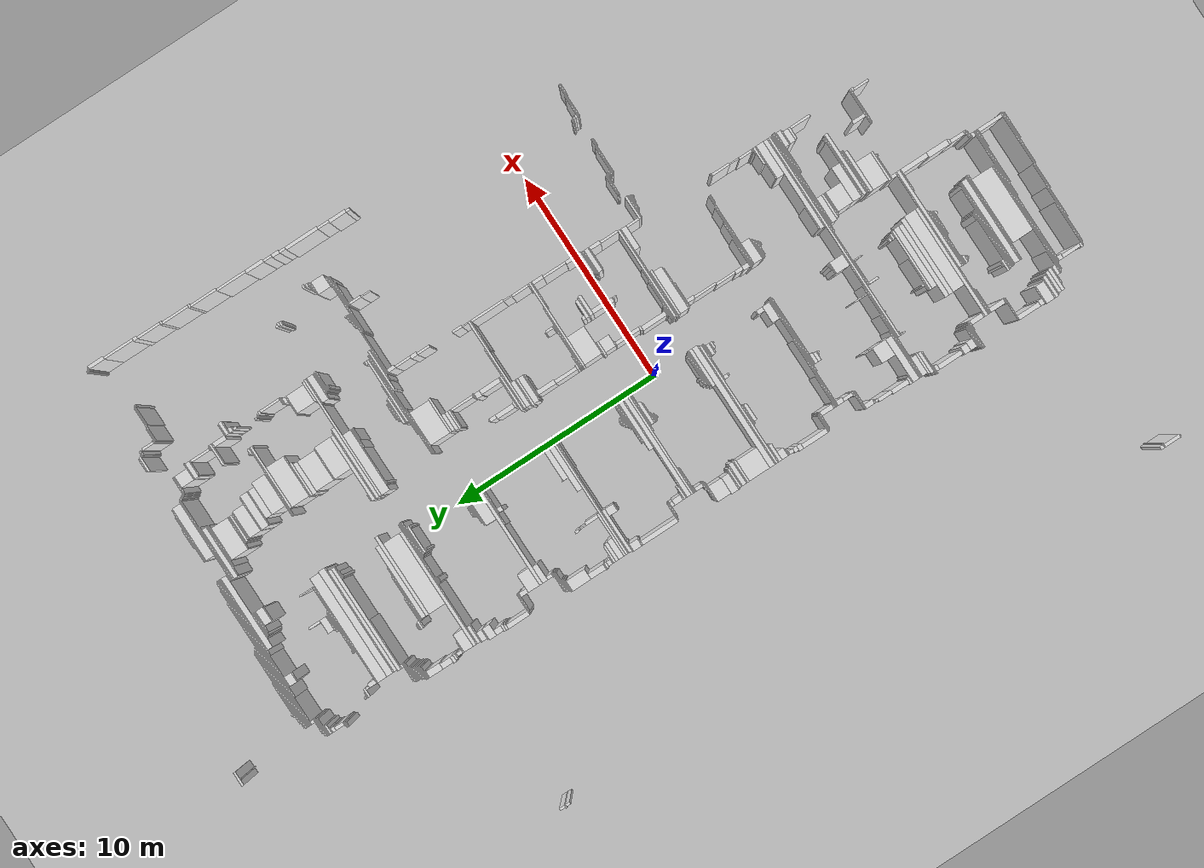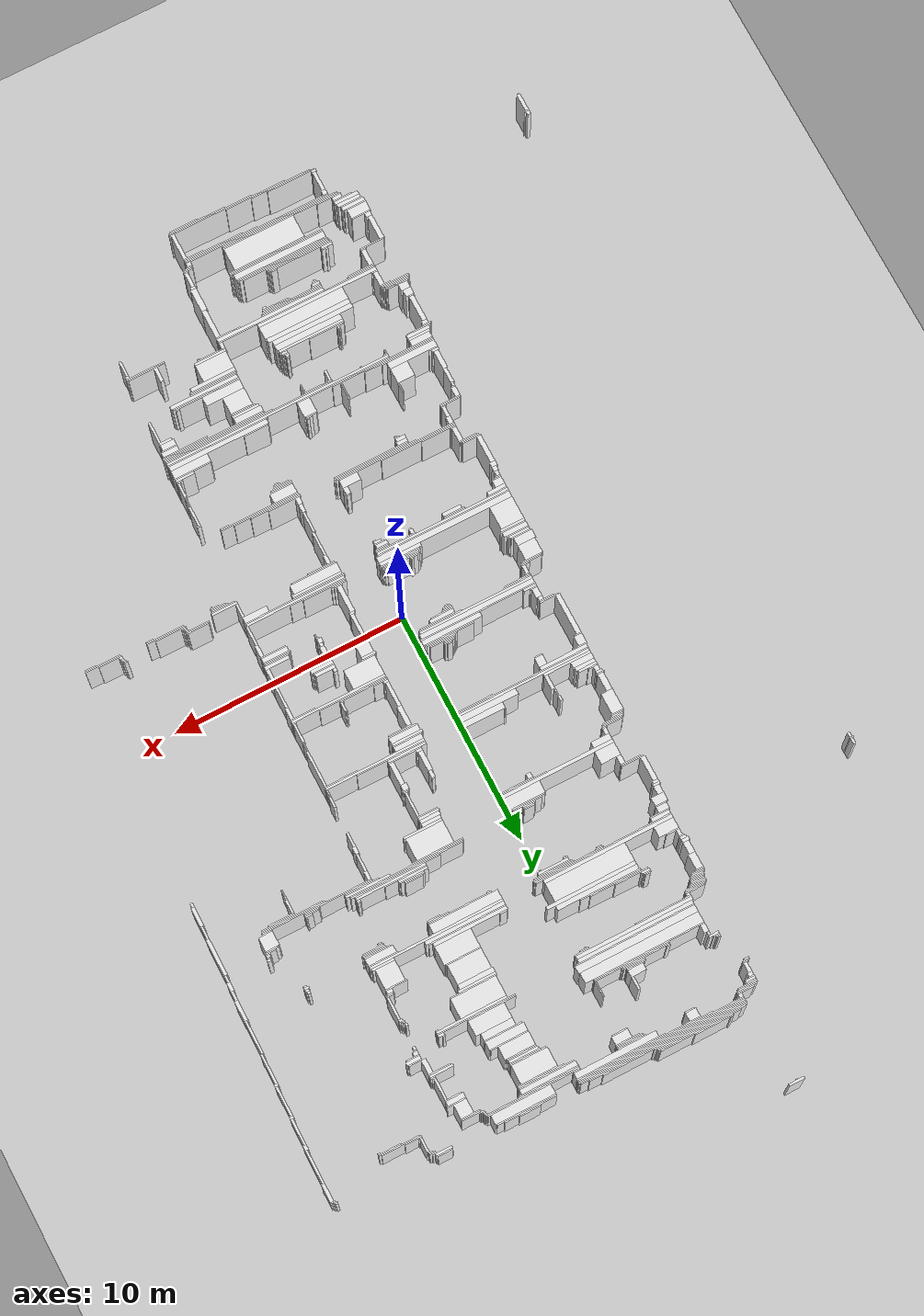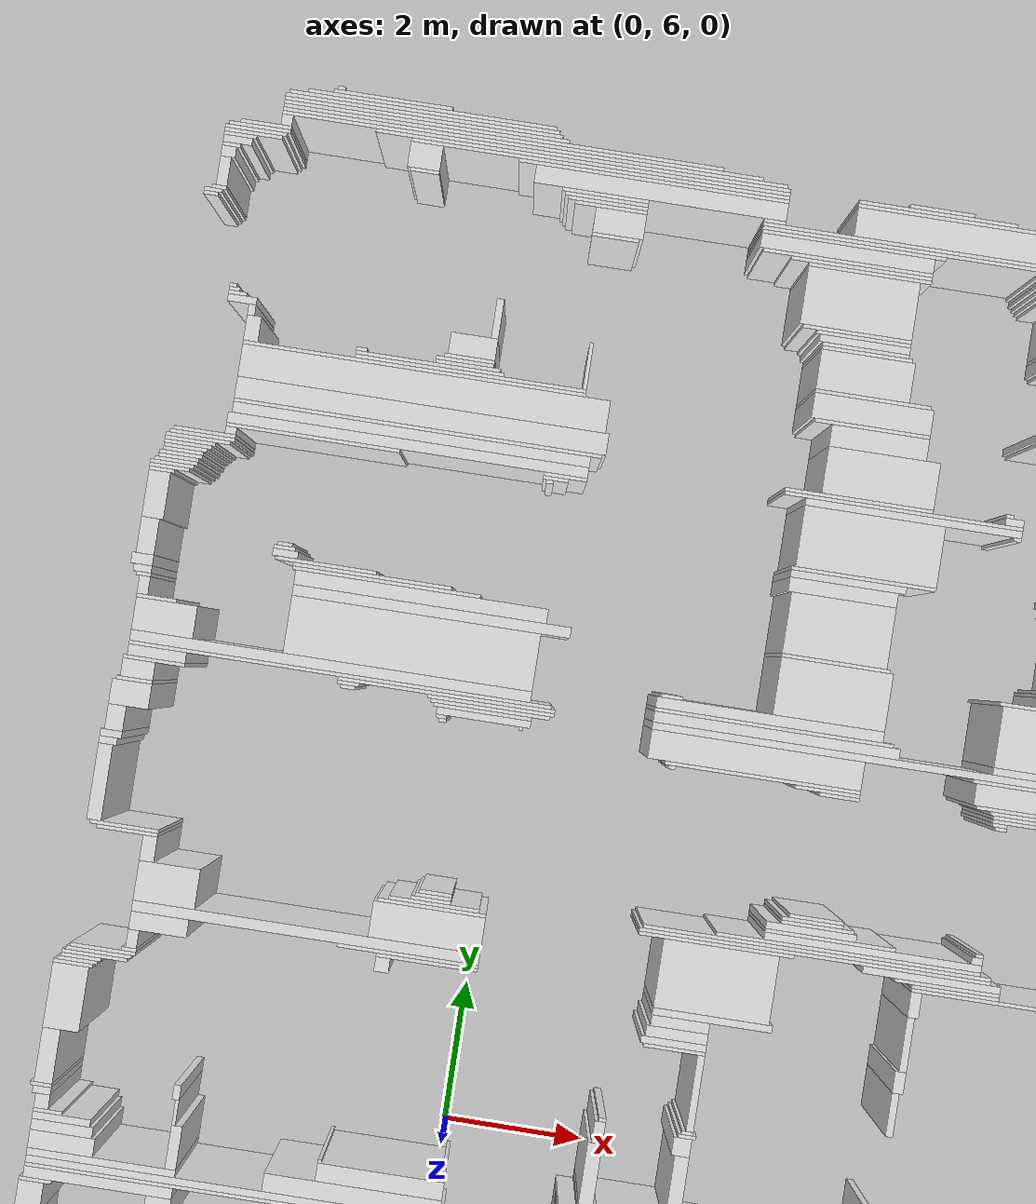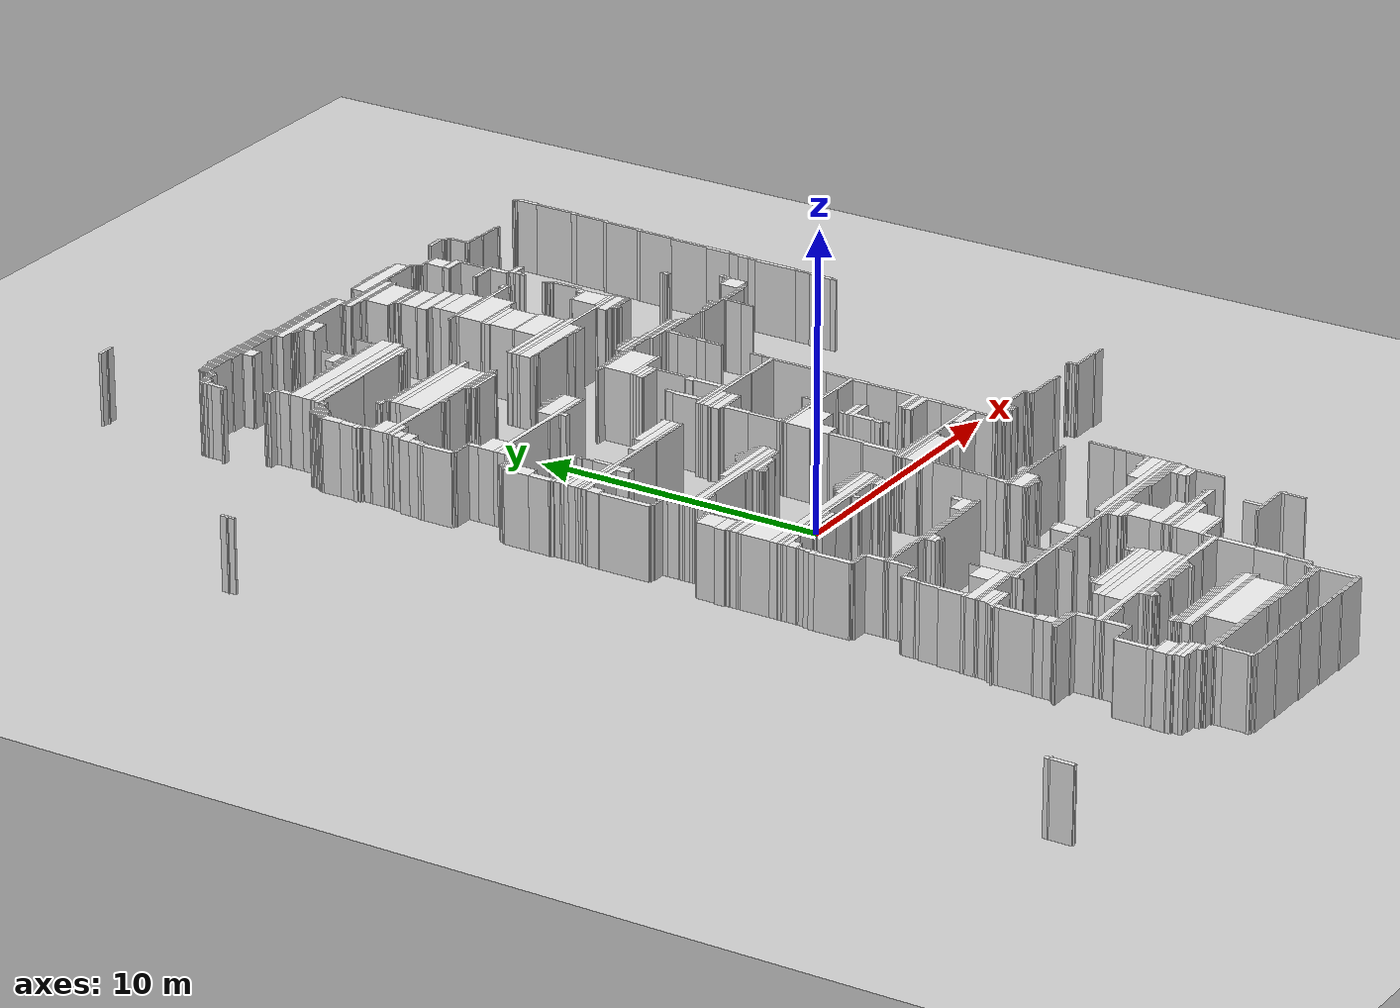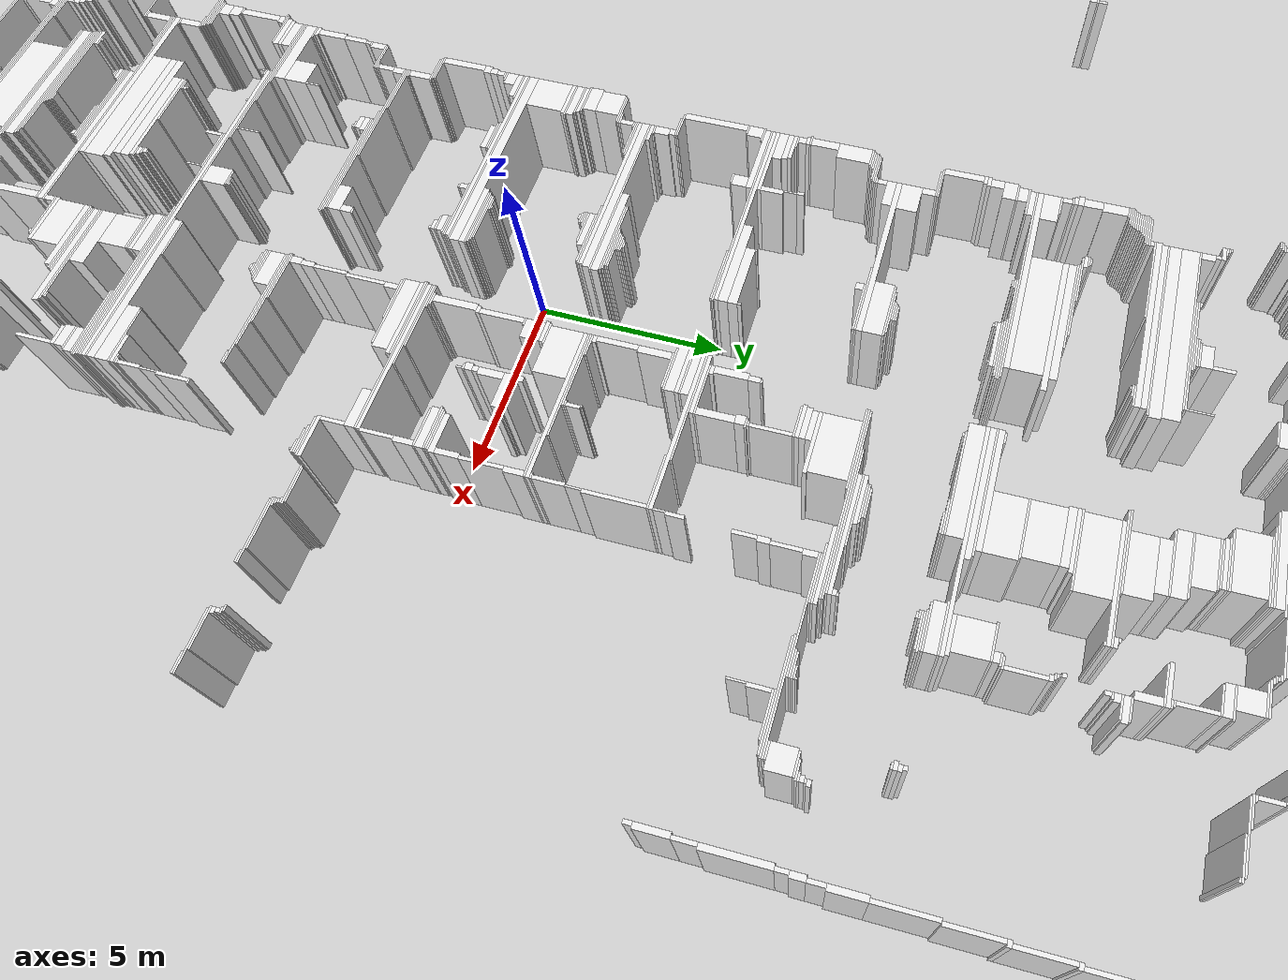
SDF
<?xml version="1.0" encoding="utf-8"?>
<sdf version="1.7">
  <world name="occupancy_map_world">
    <physics name="default_physics" default="0" type="ode">
      <max_step_size>0.001</max_step_size>
      <real_time_factor>1</real_time_factor>
      <real_time_update_rate>1000</real_time_update_rate>
    </physics>
    <light name="sun" type="directional">
      <cast_shadows>1</cast_shadows>
      <pose>0 0 10 0 0 0</pose>
      <diffuse>0.8 0.8 0.8 1</diffuse>
      <specular>0.2 0.2 0.2 1</specular>
      <attenuation>
        <range>1000</range>
        <constant>0.9</constant>
        <linear>0.01</linear>
        <quadratic>0.001</quadratic>
      </attenuation>
      <direction>-0.5 0.1 -0.9</direction>
    </light>
    <model name="ground_plane">
      <static>true</static>
      <link name="link">
        <collision name="collision">
          <geometry>
            <plane>
              <normal>0 0 1</normal>
              <size>32.46 49.62000000000001</size>
            </plane>
          </geometry>
        </collision>
        <visual name="visual">
          <geometry>
            <plane>
              <normal>0 0 1</normal>
              <size>32.46 49.62000000000001</size>
            </plane>
          </geometry>
          <material>
            <script>
              <uri>file://media/materials/scripts/gazebo.material</uri>
              <name>Gazebo/Grey</name>
            </script>
          </material>
        </visual>
      </link>
    </model>
    <model name="wall_0">
      <static>true</static>
      <pose>-4.549999999999997 23.425000000000004 1.25 0 0 0.0</pose>
      <link name="link">
        <collision name="collision">
          <geometry>
            <box>
              <size>0.65 0.1 2.5</size>
            </box>
          </geometry>
        </collision>
        <visual name="visual">
          <geometry>
            <box>
              <size>0.65 0.1 2.5</size>
            </box>
          </geometry>
          <material>
            <script>
              <uri>file://media/materials/scripts/gazebo.material</uri>
              <name>Gazebo/White</name>
            </script>
          </material>
        </visual>
      </link>
    </model>
    <model name="wall_1">
      <static>true</static>
      <pose>-4.599999999999998 23.35 1.25 0 0 0.0</pose>
      <link name="link">
        <collision name="collision">
          <geometry>
            <box>
              <size>0.05 0.05 2.5</size>
            </box>
          </geometry>
        </collision>
        <visual name="visual">
          <geometry>
            <box>
              <size>0.05 0.05 2.5</size>
            </box>
          </geometry>
          <material>
            <script>
              <uri>file://media/materials/scripts/gazebo.material</uri>
              <name>Gazebo/White</name>
            </script>
          </material>
        </visual>
      </link>
    </model>
    <model name="wall_2">
      <static>true</static>
      <pose>-3.5749999999999975 20.150000000000006 1.25 0 0 0.0</pose>
      <link name="link">
        <collision name="collision">
          <geometry>
            <box>
              <size>0.1 0.05 2.5</size>
            </box>
          </geometry>
        </collision>
        <visual name="visual">
          <geometry>
            <box>
              <size>0.1 0.05 2.5</size>
            </box>
          </geometry>
          <material>
            <script>
              <uri>file://media/materials/scripts/gazebo.material</uri>
              <name>Gazebo/White</name>
            </script>
          </material>
        </visual>
      </link>
    </model>
    <model name="wall_3">
      <static>true</static>
      <pose>-2.849999999999998 20.1 1.25 0 0 0.0</pose>
      <link name="link">
        <collision name="collision">
          <geometry>
            <box>
              <size>1.6500000000000001 0.05 2.5</size>
            </box>
          </geometry>
        </collision>
        <visual name="visual">
          <geometry>
            <box>
              <size>1.6500000000000001 0.05 2.5</size>
            </box>
          </geometry>
          <material>
            <script>
              <uri>file://media/materials/scripts/gazebo.material</uri>
              <name>Gazebo/White</name>
            </script>
          </material>
        </visual>
      </link>
    </model>
    <model name="wall_4">
      <static>true</static>
      <pose>-2.299999999999997 20.050000000000004 1.25 0 0 0.0</pose>
      <link name="link">
        <collision name="collision">
          <geometry>
            <box>
              <size>3.45 0.05 2.5</size>
            </box>
          </geometry>
        </collision>
        <visual name="visual">
          <geometry>
            <box>
              <size>3.45 0.05 2.5</size>
            </box>
          </geometry>
          <material>
            <script>
              <uri>file://media/materials/scripts/gazebo.material</uri>
              <name>Gazebo/White</name>
            </script>
          </material>
        </visual>
      </link>
    </model>
    <model name="wall_5">
      <static>true</static>
      <pose>-2.3999999999999986 20.0 1.25 0 0 0.0</pose>
      <link name="link">
        <collision name="collision">
          <geometry>
            <box>
              <size>3.75 0.05 2.5</size>
            </box>
          </geometry>
        </collision>
        <visual name="visual">
          <geometry>
            <box>
              <size>3.75 0.05 2.5</size>
            </box>
          </geometry>
          <material>
            <script>
              <uri>file://media/materials/scripts/gazebo.material</uri>
              <name>Gazebo/White</name>
            </script>
          </material>
        </visual>
      </link>
    </model>
    <model name="wall_6">
      <static>true</static>
      <pose>-2.3999999999999986 19.950000000000003 1.25 0 0 0.0</pose>
      <link name="link">
        <collision name="collision">
          <geometry>
            <box>
              <size>3.85 0.05 2.5</size>
            </box>
          </geometry>
        </collision>
        <visual name="visual">
          <geometry>
            <box>
              <size>3.85 0.05 2.5</size>
            </box>
          </geometry>
          <material>
            <script>
              <uri>file://media/materials/scripts/gazebo.material</uri>
              <name>Gazebo/White</name>
            </script>
          </material>
        </visual>
      </link>
    </model>
    <model name="wall_7">
      <static>true</static>
      <pose>-2.349999999999998 19.900000000000006 1.25 0 0 0.0</pose>
      <link name="link">
        <collision name="collision">
          <geometry>
            <box>
              <size>3.95 0.05 2.5</size>
            </box>
          </geometry>
        </collision>
        <visual name="visual">
          <geometry>
            <box>
              <size>3.95 0.05 2.5</size>
            </box>
          </geometry>
          <material>
            <script>
              <uri>file://media/materials/scripts/gazebo.material</uri>
              <name>Gazebo/White</name>
            </script>
          </material>
        </visual>
      </link>
    </model>
    <model name="wall_8">
      <static>true</static>
      <pose>-2.349999999999998 -14.8 1.25 0 0 0.0</pose>
      <link name="link">
        <collision name="collision">
          <geometry>
            <box>
              <size>3.95 0.05 2.5</size>
            </box>
          </geometry>
        </collision>
        <visual name="visual">
          <geometry>
            <box>
              <size>3.95 0.05 2.5</size>
            </box>
          </geometry>
          <material>
            <script>
              <uri>file://media/materials/scripts/gazebo.material</uri>
              <name>Gazebo/White</name>
            </script>
          </material>
        </visual>
      </link>
    </model>
    <model name="wall_9">
      <static>true</static>
      <pose>-1.2749999999999986 19.85 1.25 0 0 0.0</pose>
      <link name="link">
        <collision name="collision">
          <geometry>
            <box>
              <size>6.1000000000000005 0.05 2.5</size>
            </box>
          </geometry>
        </collision>
        <visual name="visual">
          <geometry>
            <box>
              <size>6.1000000000000005 0.05 2.5</size>
            </box>
          </geometry>
          <material>
            <script>
              <uri>file://media/materials/scripts/gazebo.material</uri>
              <name>Gazebo/White</name>
            </script>
          </material>
        </visual>
      </link>
    </model>
    <model name="wall_10">
      <static>true</static>
      <pose>-0.9999999999999964 19.800000000000004 1.25 0 0 0.0</pose>
      <link name="link">
        <collision name="collision">
          <geometry>
            <box>
              <size>6.65 0.05 2.5</size>
            </box>
          </geometry>
        </collision>
        <visual name="visual">
          <geometry>
            <box>
              <size>6.65 0.05 2.5</size>
            </box>
          </geometry>
          <material>
            <script>
              <uri>file://media/materials/scripts/gazebo.material</uri>
              <name>Gazebo/White</name>
            </script>
          </material>
        </visual>
      </link>
    </model>
    <model name="wall_11">
      <static>true</static>
      <pose>-0.8249999999999993 19.75 1.25 0 0 0.0</pose>
      <link name="link">
        <collision name="collision">
          <geometry>
            <box>
              <size>7.0 0.05 2.5</size>
            </box>
          </geometry>
        </collision>
        <visual name="visual">
          <geometry>
            <box>
              <size>7.0 0.05 2.5</size>
            </box>
          </geometry>
          <material>
            <script>
              <uri>file://media/materials/scripts/gazebo.material</uri>
              <name>Gazebo/White</name>
            </script>
          </material>
        </visual>
      </link>
    </model>
    <model name="wall_12">
      <static>true</static>
      <pose>4.825000000000003 19.75 1.25 0 0 0.0</pose>
      <link name="link">
        <collision name="collision">
          <geometry>
            <box>
              <size>0.9 0.05 2.5</size>
            </box>
          </geometry>
        </collision>
        <visual name="visual">
          <geometry>
            <box>
              <size>0.9 0.05 2.5</size>
            </box>
          </geometry>
          <material>
            <script>
              <uri>file://media/materials/scripts/gazebo.material</uri>
              <name>Gazebo/White</name>
            </script>
          </material>
        </visual>
      </link>
    </model>
    <model name="wall_13">
      <static>true</static>
      <pose>-0.7999999999999972 19.700000000000003 1.25 0 0 0.0</pose>
      <link name="link">
        <collision name="collision">
          <geometry>
            <box>
              <size>7.050000000000001 0.05 2.5</size>
            </box>
          </geometry>
        </collision>
        <visual name="visual">
          <geometry>
            <box>
              <size>7.050000000000001 0.05 2.5</size>
            </box>
          </geometry>
          <material>
            <script>
              <uri>file://media/materials/scripts/gazebo.material</uri>
              <name>Gazebo/White</name>
            </script>
          </material>
        </visual>
      </link>
    </model>
    <model name="wall_14">
      <static>true</static>
      <pose>4.775000000000002 19.700000000000003 1.25 0 0 0.0</pose>
      <link name="link">
        <collision name="collision">
          <geometry>
            <box>
              <size>2.2 0.05 2.5</size>
            </box>
          </geometry>
        </collision>
        <visual name="visual">
          <geometry>
            <box>
              <size>2.2 0.05 2.5</size>
            </box>
          </geometry>
          <material>
            <script>
              <uri>file://media/materials/scripts/gazebo.material</uri>
              <name>Gazebo/White</name>
            </script>
          </material>
        </visual>
      </link>
    </model>
    <model name="wall_15">
      <static>true</static>
      <pose>-4.249999999999998 19.6 1.25 0 0 0.0</pose>
      <link name="link">
        <collision name="collision">
          <geometry>
            <box>
              <size>0.15000000000000002 0.15000000000000002 2.5</size>
            </box>
          </geometry>
        </collision>
        <visual name="visual">
          <geometry>
            <box>
              <size>0.15000000000000002 0.15000000000000002 2.5</size>
            </box>
          </geometry>
          <material>
            <script>
              <uri>file://media/materials/scripts/gazebo.material</uri>
              <name>Gazebo/White</name>
            </script>
          </material>
        </visual>
      </link>
    </model>
    <model name="wall_16">
      <static>true</static>
      <pose>-0.14999999999999858 19.650000000000006 1.25 0 0 0.0</pose>
      <link name="link">
        <collision name="collision">
          <geometry>
            <box>
              <size>5.75 0.05 2.5</size>
            </box>
          </geometry>
        </collision>
        <visual name="visual">
          <geometry>
            <box>
              <size>5.75 0.05 2.5</size>
            </box>
          </geometry>
          <material>
            <script>
              <uri>file://media/materials/scripts/gazebo.material</uri>
              <name>Gazebo/White</name>
            </script>
          </material>
        </visual>
      </link>
    </model>
    <model name="wall_17">
      <static>true</static>
      <pose>4.925000000000004 19.650000000000006 1.25 0 0 0.0</pose>
      <link name="link">
        <collision name="collision">
          <geometry>
            <box>
              <size>2.5 0.05 2.5</size>
            </box>
          </geometry>
        </collision>
        <visual name="visual">
          <geometry>
            <box>
              <size>2.5 0.05 2.5</size>
            </box>
          </geometry>
          <material>
            <script>
              <uri>file://media/materials/scripts/gazebo.material</uri>
              <name>Gazebo/White</name>
            </script>
          </material>
        </visual>
      </link>
    </model>
    <model name="wall_18">
      <static>true</static>
      <pose>8.375000000000004 19.650000000000006 1.25 0 0 0.0</pose>
      <link name="link">
        <collision name="collision">
          <geometry>
            <box>
              <size>0.6000000000000001 0.05 2.5</size>
            </box>
          </geometry>
        </collision>
        <visual name="visual">
          <geometry>
            <box>
              <size>0.6000000000000001 0.05 2.5</size>
            </box>
          </geometry>
          <material>
            <script>
              <uri>file://media/materials/scripts/gazebo.material</uri>
              <name>Gazebo/White</name>
            </script>
          </material>
        </visual>
      </link>
    </model>
    <model name="wall_19">
      <static>true</static>
      <pose>0.10000000000000142 19.6 1.25 0 0 0.0</pose>
      <link name="link">
        <collision name="collision">
          <geometry>
            <box>
              <size>5.25 0.05 2.5</size>
            </box>
          </geometry>
        </collision>
        <visual name="visual">
          <geometry>
            <box>
              <size>5.25 0.05 2.5</size>
            </box>
          </geometry>
          <material>
            <script>
              <uri>file://media/materials/scripts/gazebo.material</uri>
              <name>Gazebo/White</name>
            </script>
          </material>
        </visual>
      </link>
    </model>
    <model name="wall_20">
      <static>true</static>
      <pose>4.950000000000003 19.425000000000004 1.25 0 0 0.0</pose>
      <link name="link">
        <collision name="collision">
          <geometry>
            <box>
              <size>2.5500000000000003 0.4 2.5</size>
            </box>
          </geometry>
        </collision>
        <visual name="visual">
          <geometry>
            <box>
              <size>2.5500000000000003 0.4 2.5</size>
            </box>
          </geometry>
          <material>
            <script>
              <uri>file://media/materials/scripts/gazebo.material</uri>
              <name>Gazebo/White</name>
            </script>
          </material>
        </visual>
      </link>
    </model>
    <model name="wall_21">
      <static>true</static>
      <pose>8.375000000000004 19.575000000000003 1.25 0 0 0.0</pose>
      <link name="link">
        <collision name="collision">
          <geometry>
            <box>
              <size>0.7000000000000001 0.1 2.5</size>
            </box>
          </geometry>
        </collision>
        <visual name="visual">
          <geometry>
            <box>
              <size>0.7000000000000001 0.1 2.5</size>
            </box>
          </geometry>
          <material>
            <script>
              <uri>file://media/materials/scripts/gazebo.material</uri>
              <name>Gazebo/White</name>
            </script>
          </material>
        </visual>
      </link>
    </model>
    <model name="wall_22">
      <static>true</static>
      <pose>-2.299999999999997 19.400000000000006 1.25 0 0 0.0</pose>
      <link name="link">
        <collision name="collision">
          <geometry>
            <box>
              <size>0.45 0.35000000000000003 2.5</size>
            </box>
          </geometry>
        </collision>
        <visual name="visual">
          <geometry>
            <box>
              <size>0.45 0.35000000000000003 2.5</size>
            </box>
          </geometry>
          <material>
            <script>
              <uri>file://media/materials/scripts/gazebo.material</uri>
              <name>Gazebo/White</name>
            </script>
          </material>
        </visual>
      </link>
    </model>
    <model name="wall_23">
      <static>true</static>
      <pose>0.8500000000000014 19.550000000000004 1.25 0 0 0.0</pose>
      <link name="link">
        <collision name="collision">
          <geometry>
            <box>
              <size>3.75 0.05 2.5</size>
            </box>
          </geometry>
        </collision>
        <visual name="visual">
          <geometry>
            <box>
              <size>3.75 0.05 2.5</size>
            </box>
          </geometry>
          <material>
            <script>
              <uri>file://media/materials/scripts/gazebo.material</uri>
              <name>Gazebo/White</name>
            </script>
          </material>
        </visual>
      </link>
    </model>
    <model name="wall_24">
      <static>true</static>
      <pose>-4.524999999999999 19.5 1.25 0 0 0.0</pose>
      <link name="link">
        <collision name="collision">
          <geometry>
            <box>
              <size>0.7000000000000001 0.05 2.5</size>
            </box>
          </geometry>
        </collision>
        <visual name="visual">
          <geometry>
            <box>
              <size>0.7000000000000001 0.05 2.5</size>
            </box>
          </geometry>
          <material>
            <script>
              <uri>file://media/materials/scripts/gazebo.material</uri>
              <name>Gazebo/White</name>
            </script>
          </material>
        </visual>
      </link>
    </model>
    <model name="wall_25">
      <static>true</static>
      <pose>0.9750000000000014 19.400000000000006 1.25 0 0 0.0</pose>
      <link name="link">
        <collision name="collision">
          <geometry>
            <box>
              <size>3.5 0.25 2.5</size>
            </box>
          </geometry>
        </collision>
        <visual name="visual">
          <geometry>
            <box>
              <size>3.5 0.25 2.5</size>
            </box>
          </geometry>
          <material>
            <script>
              <uri>file://media/materials/scripts/gazebo.material</uri>
              <name>Gazebo/White</name>
            </script>
          </material>
        </visual>
      </link>
    </model>
    <model name="wall_26">
      <static>true</static>
      <pose>8.750000000000004 19.5 1.25 0 0 0.0</pose>
      <link name="link">
        <collision name="collision">
          <geometry>
            <box>
              <size>0.15000000000000002 0.05 2.5</size>
            </box>
          </geometry>
        </collision>
        <visual name="visual">
          <geometry>
            <box>
              <size>0.15000000000000002 0.05 2.5</size>
            </box>
          </geometry>
          <material>
            <script>
              <uri>file://media/materials/scripts/gazebo.material</uri>
              <name>Gazebo/White</name>
            </script>
          </material>
        </visual>
      </link>
    </model>
    <model name="wall_27">
      <static>true</static>
      <pose>-4.599999999999998 19.450000000000003 1.25 0 0 0.0</pose>
      <link name="link">
        <collision name="collision">
          <geometry>
            <box>
              <size>0.8500000000000001 0.05 2.5</size>
            </box>
          </geometry>
        </collision>
        <visual name="visual">
          <geometry>
            <box>
              <size>0.8500000000000001 0.05 2.5</size>
            </box>
          </geometry>
          <material>
            <script>
              <uri>file://media/materials/scripts/gazebo.material</uri>
              <name>Gazebo/White</name>
            </script>
          </material>
        </visual>
      </link>
    </model>
    <model name="wall_28">
      <static>true</static>
      <pose>8.800000000000004 19.450000000000003 1.25 0 0 0.0</pose>
      <link name="link">
        <collision name="collision">
          <geometry>
            <box>
              <size>0.25 0.05 2.5</size>
            </box>
          </geometry>
        </collision>
        <visual name="visual">
          <geometry>
            <box>
              <size>0.25 0.05 2.5</size>
            </box>
          </geometry>
          <material>
            <script>
              <uri>file://media/materials/scripts/gazebo.material</uri>
              <name>Gazebo/White</name>
            </script>
          </material>
        </visual>
      </link>
    </model>
    <model name="wall_29">
      <static>true</static>
      <pose>12.825000000000003 19.450000000000003 1.25 0 0 0.0</pose>
      <link name="link">
        <collision name="collision">
          <geometry>
            <box>
              <size>0.1 0.05 2.5</size>
            </box>
          </geometry>
        </collision>
        <visual name="visual">
          <geometry>
            <box>
              <size>0.1 0.05 2.5</size>
            </box>
          </geometry>
          <material>
            <script>
              <uri>file://media/materials/scripts/gazebo.material</uri>
              <name>Gazebo/White</name>
            </script>
          </material>
        </visual>
      </link>
    </model>
    <model name="wall_30">
      <static>true</static>
      <pose>12.825000000000003 15.149999999999999 1.25 0 0 0.0</pose>
      <link name="link">
        <collision name="collision">
          <geometry>
            <box>
              <size>0.1 1.25 2.5</size>
            </box>
          </geometry>
        </collision>
        <visual name="visual">
          <geometry>
            <box>
              <size>0.1 1.25 2.5</size>
            </box>
          </geometry>
          <material>
            <script>
              <uri>file://media/materials/scripts/gazebo.material</uri>
              <name>Gazebo/White</name>
            </script>
          </material>
        </visual>
      </link>
    </model>
    <model name="wall_31">
      <static>true</static>
      <pose>-4.649999999999999 19.400000000000006 1.25 0 0 0.0</pose>
      <link name="link">
        <collision name="collision">
          <geometry>
            <box>
              <size>0.8500000000000001 0.05 2.5</size>
            </box>
          </geometry>
        </collision>
        <visual name="visual">
          <geometry>
            <box>
              <size>0.8500000000000001 0.05 2.5</size>
            </box>
          </geometry>
          <material>
            <script>
              <uri>file://media/materials/scripts/gazebo.material</uri>
              <name>Gazebo/White</name>
            </script>
          </material>
        </visual>
      </link>
    </model>
    <model name="wall_32">
      <static>true</static>
      <pose>8.825000000000003 19.400000000000006 1.25 0 0 0.0</pose>
      <link name="link">
        <collision name="collision">
          <geometry>
            <box>
              <size>0.2 0.05 2.5</size>
            </box>
          </geometry>
        </collision>
        <visual name="visual">
          <geometry>
            <box>
              <size>0.2 0.05 2.5</size>
            </box>
          </geometry>
          <material>
            <script>
              <uri>file://media/materials/scripts/gazebo.material</uri>
              <name>Gazebo/White</name>
            </script>
          </material>
        </visual>
      </link>
    </model>
    <model name="wall_33">
      <static>true</static>
      <pose>12.850000000000001 19.400000000000006 1.25 0 0 0.0</pose>
      <link name="link">
        <collision name="collision">
          <geometry>
            <box>
              <size>0.15000000000000002 0.05 2.5</size>
            </box>
          </geometry>
        </collision>
        <visual name="visual">
          <geometry>
            <box>
              <size>0.15000000000000002 0.05 2.5</size>
            </box>
          </geometry>
          <material>
            <script>
              <uri>file://media/materials/scripts/gazebo.material</uri>
              <name>Gazebo/White</name>
            </script>
          </material>
        </visual>
      </link>
    </model>
    <model name="wall_34">
      <static>true</static>
      <pose>12.850000000000001 15.825000000000003 1.25 0 0 0.0</pose>
      <link name="link">
        <collision name="collision">
          <geometry>
            <box>
              <size>0.15000000000000002 0.1 2.5</size>
            </box>
          </geometry>
        </collision>
        <visual name="visual">
          <geometry>
            <box>
              <size>0.15000000000000002 0.1 2.5</size>
            </box>
          </geometry>
          <material>
            <script>
              <uri>file://media/materials/scripts/gazebo.material</uri>
              <name>Gazebo/White</name>
            </script>
          </material>
        </visual>
      </link>
    </model>
    <model name="wall_35">
      <static>true</static>
      <pose>-4.674999999999997 19.35 1.25 0 0 0.0</pose>
      <link name="link">
        <collision name="collision">
          <geometry>
            <box>
              <size>0.8 0.05 2.5</size>
            </box>
          </geometry>
        </collision>
        <visual name="visual">
          <geometry>
            <box>
              <size>0.8 0.05 2.5</size>
            </box>
          </geometry>
          <material>
            <script>
              <uri>file://media/materials/scripts/gazebo.material</uri>
              <name>Gazebo/White</name>
            </script>
          </material>
        </visual>
      </link>
    </model>
    <model name="wall_36">
      <static>true</static>
      <pose>8.900000000000002 19.35 1.25 0 0 0.0</pose>
      <link name="link">
        <collision name="collision">
          <geometry>
            <box>
              <size>0.05 0.05 2.5</size>
            </box>
          </geometry>
        </collision>
        <visual name="visual">
          <geometry>
            <box>
              <size>0.05 0.05 2.5</size>
            </box>
          </geometry>
          <material>
            <script>
              <uri>file://media/materials/scripts/gazebo.material</uri>
              <name>Gazebo/White</name>
            </script>
          </material>
        </visual>
      </link>
    </model>
    <model name="wall_37">
      <static>true</static>
      <pose>8.900000000000002 9.350000000000001 1.25 0 0 0.0</pose>
      <link name="link">
        <collision name="collision">
          <geometry>
            <box>
              <size>0.05 0.05 2.5</size>
            </box>
          </geometry>
        </collision>
        <visual name="visual">
          <geometry>
            <box>
              <size>0.05 0.05 2.5</size>
            </box>
          </geometry>
          <material>
            <script>
              <uri>file://media/materials/scripts/gazebo.material</uri>
              <name>Gazebo/White</name>
            </script>
          </material>
        </visual>
      </link>
    </model>
    <model name="wall_38">
      <static>true</static>
      <pose>12.900000000000002 19.35 1.25 0 0 0.0</pose>
      <link name="link">
        <collision name="collision">
          <geometry>
            <box>
              <size>0.15000000000000002 0.05 2.5</size>
            </box>
          </geometry>
        </collision>
        <visual name="visual">
          <geometry>
            <box>
              <size>0.15000000000000002 0.05 2.5</size>
            </box>
          </geometry>
          <material>
            <script>
              <uri>file://media/materials/scripts/gazebo.material</uri>
              <name>Gazebo/White</name>
            </script>
          </material>
        </visual>
      </link>
    </model>
    <model name="wall_39">
      <static>true</static>
      <pose>12.900000000000002 17.075000000000003 1.25 0 0 0.0</pose>
      <link name="link">
        <collision name="collision">
          <geometry>
            <box>
              <size>0.15000000000000002 0.2 2.5</size>
            </box>
          </geometry>
        </collision>
        <visual name="visual">
          <geometry>
            <box>
              <size>0.15000000000000002 0.2 2.5</size>
            </box>
          </geometry>
          <material>
            <script>
              <uri>file://media/materials/scripts/gazebo.material</uri>
              <name>Gazebo/White</name>
            </script>
          </material>
        </visual>
      </link>
    </model>
    <model name="wall_40">
      <static>true</static>
      <pose>-4.849999999999998 19.300000000000004 1.25 0 0 0.0</pose>
      <link name="link">
        <collision name="collision">
          <geometry>
            <box>
              <size>0.45 0.05 2.5</size>
            </box>
          </geometry>
        </collision>
        <visual name="visual">
          <geometry>
            <box>
              <size>0.45 0.05 2.5</size>
            </box>
          </geometry>
          <material>
            <script>
              <uri>file://media/materials/scripts/gazebo.material</uri>
              <name>Gazebo/White</name>
            </script>
          </material>
        </visual>
      </link>
    </model>
    <model name="wall_41">
      <static>true</static>
      <pose>8.925000000000004 19.050000000000004 1.25 0 0 0.0</pose>
      <link name="link">
        <collision name="collision">
          <geometry>
            <box>
              <size>0.1 0.55 2.5</size>
            </box>
          </geometry>
        </collision>
        <visual name="visual">
          <geometry>
            <box>
              <size>0.1 0.55 2.5</size>
            </box>
          </geometry>
          <material>
            <script>
              <uri>file://media/materials/scripts/gazebo.material</uri>
              <name>Gazebo/White</name>
            </script>
          </material>
        </visual>
      </link>
    </model>
    <model name="wall_42">
      <static>true</static>
      <pose>12.950000000000003 18.950000000000003 1.25 0 0 0.0</pose>
      <link name="link">
        <collision name="collision">
          <geometry>
            <box>
              <size>0.15000000000000002 0.75 2.5</size>
            </box>
          </geometry>
        </collision>
        <visual name="visual">
          <geometry>
            <box>
              <size>0.15000000000000002 0.75 2.5</size>
            </box>
          </geometry>
          <material>
            <script>
              <uri>file://media/materials/scripts/gazebo.material</uri>
              <name>Gazebo/White</name>
            </script>
          </material>
        </visual>
      </link>
    </model>
    <model name="wall_43">
      <static>true</static>
      <pose>-4.874999999999998 19.225 1.25 0 0 0.0</pose>
      <link name="link">
        <collision name="collision">
          <geometry>
            <box>
              <size>0.4 0.1 2.5</size>
            </box>
          </geometry>
        </collision>
        <visual name="visual">
          <geometry>
            <box>
              <size>0.4 0.1 2.5</size>
            </box>
          </geometry>
          <material>
            <script>
              <uri>file://media/materials/scripts/gazebo.material</uri>
              <name>Gazebo/White</name>
            </script>
          </material>
        </visual>
      </link>
    </model>
    <model name="wall_44">
      <static>true</static>
      <pose>0.22500000000000142 19.25 1.25 0 0 0.0</pose>
      <link name="link">
        <collision name="collision">
          <geometry>
            <box>
              <size>1.2000000000000002 0.05 2.5</size>
            </box>
          </geometry>
        </collision>
        <visual name="visual">
          <geometry>
            <box>
              <size>1.2000000000000002 0.05 2.5</size>
            </box>
          </geometry>
          <material>
            <script>
              <uri>file://media/materials/scripts/gazebo.material</uri>
              <name>Gazebo/White</name>
            </script>
          </material>
        </visual>
      </link>
    </model>
    <model name="wall_45">
      <static>true</static>
      <pose>2.575000000000003 19.25 1.25 0 0 0.0</pose>
      <link name="link">
        <collision name="collision">
          <geometry>
            <box>
              <size>0.30000000000000004 0.05 2.5</size>
            </box>
          </geometry>
        </collision>
        <visual name="visual">
          <geometry>
            <box>
              <size>0.30000000000000004 0.05 2.5</size>
            </box>
          </geometry>
          <material>
            <script>
              <uri>file://media/materials/scripts/gazebo.material</uri>
              <name>Gazebo/White</name>
            </script>
          </material>
        </visual>
      </link>
    </model>
    <model name="wall_46">
      <static>true</static>
      <pose>-2.2749999999999986 19.200000000000003 1.25 0 0 0.0</pose>
      <link name="link">
        <collision name="collision">
          <geometry>
            <box>
              <size>0.4 0.05 2.5</size>
            </box>
          </geometry>
        </collision>
        <visual name="visual">
          <geometry>
            <box>
              <size>0.4 0.05 2.5</size>
            </box>
          </geometry>
          <material>
            <script>
              <uri>file://media/materials/scripts/gazebo.material</uri>
              <name>Gazebo/White</name>
            </script>
          </material>
        </visual>
      </link>
    </model>
    <model name="wall_47">
      <static>true</static>
      <pose>0.25000000000000355 19.200000000000003 1.25 0 0 0.0</pose>
      <link name="link">
        <collision name="collision">
          <geometry>
            <box>
              <size>1.1500000000000001 0.05 2.5</size>
            </box>
          </geometry>
        </collision>
        <visual name="visual">
          <geometry>
            <box>
              <size>1.1500000000000001 0.05 2.5</size>
            </box>
          </geometry>
          <material>
            <script>
              <uri>file://media/materials/scripts/gazebo.material</uri>
              <name>Gazebo/White</name>
            </script>
          </material>
        </visual>
      </link>
    </model>
    <model name="wall_48">
      <static>true</static>
      <pose>4.3750000000000036 19.200000000000003 1.25 0 0 0.0</pose>
      <link name="link">
        <collision name="collision">
          <geometry>
            <box>
              <size>3.9000000000000004 0.05 2.5</size>
            </box>
          </geometry>
        </collision>
        <visual name="visual">
          <geometry>
            <box>
              <size>3.9000000000000004 0.05 2.5</size>
            </box>
          </geometry>
          <material>
            <script>
              <uri>file://media/materials/scripts/gazebo.material</uri>
              <name>Gazebo/White</name>
            </script>
          </material>
        </visual>
      </link>
    </model>
    <model name="wall_49">
      <static>true</static>
      <pose>-4.9499999999999975 19.150000000000006 1.25 0 0 0.0</pose>
      <link name="link">
        <collision name="collision">
          <geometry>
            <box>
              <size>0.25 0.05 2.5</size>
            </box>
          </geometry>
        </collision>
        <visual name="visual">
          <geometry>
            <box>
              <size>0.25 0.05 2.5</size>
            </box>
          </geometry>
          <material>
            <script>
              <uri>file://media/materials/scripts/gazebo.material</uri>
              <name>Gazebo/White</name>
            </script>
          </material>
        </visual>
      </link>
    </model>
    <model name="wall_50">
      <static>true</static>
      <pose>0.27500000000000213 19.150000000000006 1.25 0 0 0.0</pose>
      <link name="link">
        <collision name="collision">
          <geometry>
            <box>
              <size>1.1 0.05 2.5</size>
            </box>
          </geometry>
        </collision>
        <visual name="visual">
          <geometry>
            <box>
              <size>1.1 0.05 2.5</size>
            </box>
          </geometry>
          <material>
            <script>
              <uri>file://media/materials/scripts/gazebo.material</uri>
              <name>Gazebo/White</name>
            </script>
          </material>
        </visual>
      </link>
    </model>
    <model name="wall_51">
      <static>true</static>
      <pose>4.400000000000002 19.150000000000006 1.25 0 0 0.0</pose>
      <link name="link">
        <collision name="collision">
          <geometry>
            <box>
              <size>3.95 0.05 2.5</size>
            </box>
          </geometry>
        </collision>
        <visual name="visual">
          <geometry>
            <box>
              <size>3.95 0.05 2.5</size>
            </box>
          </geometry>
          <material>
            <script>
              <uri>file://media/materials/scripts/gazebo.material</uri>
              <name>Gazebo/White</name>
            </script>
          </material>
        </visual>
      </link>
    </model>
    <model name="wall_52">
      <static>true</static>
      <pose>-4.974999999999998 19.050000000000004 1.25 0 0 0.0</pose>
      <link name="link">
        <collision name="collision">
          <geometry>
            <box>
              <size>0.2 0.15000000000000002 2.5</size>
            </box>
          </geometry>
        </collision>
        <visual name="visual">
          <geometry>
            <box>
              <size>0.2 0.15000000000000002 2.5</size>
            </box>
          </geometry>
          <material>
            <script>
              <uri>file://media/materials/scripts/gazebo.material</uri>
              <name>Gazebo/White</name>
            </script>
          </material>
        </visual>
      </link>
    </model>
    <model name="wall_53">
      <static>true</static>
      <pose>0.32500000000000284 19.1 1.25 0 0 0.0</pose>
      <link name="link">
        <collision name="collision">
          <geometry>
            <box>
              <size>1.0 0.05 2.5</size>
            </box>
          </geometry>
        </collision>
        <visual name="visual">
          <geometry>
            <box>
              <size>1.0 0.05 2.5</size>
            </box>
          </geometry>
          <material>
            <script>
              <uri>file://media/materials/scripts/gazebo.material</uri>
              <name>Gazebo/White</name>
            </script>
          </material>
        </visual>
      </link>
    </model>
    <model name="wall_54">
      <static>true</static>
      <pose>3.700000000000003 19.1 1.25 0 0 0.0</pose>
      <link name="link">
        <collision name="collision">
          <geometry>
            <box>
              <size>2.5500000000000003 0.05 2.5</size>
            </box>
          </geometry>
        </collision>
        <visual name="visual">
          <geometry>
            <box>
              <size>2.5500000000000003 0.05 2.5</size>
            </box>
          </geometry>
          <material>
            <script>
              <uri>file://media/materials/scripts/gazebo.material</uri>
              <name>Gazebo/White</name>
            </script>
          </material>
        </visual>
      </link>
    </model>
    <model name="wall_55">
      <static>true</static>
      <pose>6.350000000000001 19.1 1.25 0 0 0.0</pose>
      <link name="link">
        <collision name="collision">
          <geometry>
            <box>
              <size>0.15000000000000002 0.05 2.5</size>
            </box>
          </geometry>
        </collision>
        <visual name="visual">
          <geometry>
            <box>
              <size>0.15000000000000002 0.05 2.5</size>
            </box>
          </geometry>
          <material>
            <script>
              <uri>file://media/materials/scripts/gazebo.material</uri>
              <name>Gazebo/White</name>
            </script>
          </material>
        </visual>
      </link>
    </model>
    <model name="wall_56">
      <static>true</static>
      <pose>0.4750000000000014 18.900000000000006 1.25 0 0 0.0</pose>
      <link name="link">
        <collision name="collision">
          <geometry>
            <box>
              <size>0.7000000000000001 0.35000000000000003 2.5</size>
            </box>
          </geometry>
        </collision>
        <visual name="visual">
          <geometry>
            <box>
              <size>0.7000000000000001 0.35000000000000003 2.5</size>
            </box>
          </geometry>
          <material>
            <script>
              <uri>file://media/materials/scripts/gazebo.material</uri>
              <name>Gazebo/White</name>
            </script>
          </material>
        </visual>
      </link>
    </model>
    <model name="wall_57">
      <static>true</static>
      <pose>3.6250000000000036 18.975 1.25 0 0 0.0</pose>
      <link name="link">
        <collision name="collision">
          <geometry>
            <box>
              <size>2.4000000000000004 0.2 2.5</size>
            </box>
          </geometry>
        </collision>
        <visual name="visual">
          <geometry>
            <box>
              <size>2.4000000000000004 0.2 2.5</size>
            </box>
          </geometry>
          <material>
            <script>
              <uri>file://media/materials/scripts/gazebo.material</uri>
              <name>Gazebo/White</name>
            </script>
          </material>
        </visual>
      </link>
    </model>
    <model name="wall_58">
      <static>true</static>
      <pose>6.3750000000000036 19.050000000000004 1.25 0 0 0.0</pose>
      <link name="link">
        <collision name="collision">
          <geometry>
            <box>
              <size>0.1 0.05 2.5</size>
            </box>
          </geometry>
        </collision>
        <visual name="visual">
          <geometry>
            <box>
              <size>0.1 0.05 2.5</size>
            </box>
          </geometry>
          <material>
            <script>
              <uri>file://media/materials/scripts/gazebo.material</uri>
              <name>Gazebo/White</name>
            </script>
          </material>
        </visual>
      </link>
    </model>
    <model name="wall_59">
      <static>true</static>
      <pose>6.3750000000000036 15.75 1.25 0 0 0.0</pose>
      <link name="link">
        <collision name="collision">
          <geometry>
            <box>
              <size>0.1 0.05 2.5</size>
            </box>
          </geometry>
        </collision>
        <visual name="visual">
          <geometry>
            <box>
              <size>0.1 0.05 2.5</size>
            </box>
          </geometry>
          <material>
            <script>
              <uri>file://media/materials/scripts/gazebo.material</uri>
              <name>Gazebo/White</name>
            </script>
          </material>
        </visual>
      </link>
    </model>
    <model name="wall_60">
      <static>true</static>
      <pose>6.400000000000002 19.0 1.25 0 0 0.0</pose>
      <link name="link">
        <collision name="collision">
          <geometry>
            <box>
              <size>0.15000000000000002 0.05 2.5</size>
            </box>
          </geometry>
        </collision>
        <visual name="visual">
          <geometry>
            <box>
              <size>0.15000000000000002 0.05 2.5</size>
            </box>
          </geometry>
          <material>
            <script>
              <uri>file://media/materials/scripts/gazebo.material</uri>
              <name>Gazebo/White</name>
            </script>
          </material>
        </visual>
      </link>
    </model>
    <model name="wall_61">
      <static>true</static>
      <pose>-4.999999999999998 18.775000000000006 1.25 0 0 0.0</pose>
      <link name="link">
        <collision name="collision">
          <geometry>
            <box>
              <size>0.15000000000000002 0.4 2.5</size>
            </box>
          </geometry>
        </collision>
        <visual name="visual">
          <geometry>
            <box>
              <size>0.15000000000000002 0.4 2.5</size>
            </box>
          </geometry>
          <material>
            <script>
              <uri>file://media/materials/scripts/gazebo.material</uri>
              <name>Gazebo/White</name>
            </script>
          </material>
        </visual>
      </link>
    </model>
    <model name="wall_62">
      <static>true</static>
      <pose>6.450000000000003 18.950000000000003 1.25 0 0 0.0</pose>
      <link name="link">
        <collision name="collision">
          <geometry>
            <box>
              <size>0.15000000000000002 0.05 2.5</size>
            </box>
          </geometry>
        </collision>
        <visual name="visual">
          <geometry>
            <box>
              <size>0.15000000000000002 0.05 2.5</size>
            </box>
          </geometry>
          <material>
            <script>
              <uri>file://media/materials/scripts/gazebo.material</uri>
              <name>Gazebo/White</name>
            </script>
          </material>
        </visual>
      </link>
    </model>
    <model name="wall_63">
      <static>true</static>
      <pose>6.850000000000001 18.900000000000006 1.25 0 0 0.0</pose>
      <link name="link">
        <collision name="collision">
          <geometry>
            <box>
              <size>0.8500000000000001 0.05 2.5</size>
            </box>
          </geometry>
        </collision>
        <visual name="visual">
          <geometry>
            <box>
              <size>0.8500000000000001 0.05 2.5</size>
            </box>
          </geometry>
          <material>
            <script>
              <uri>file://media/materials/scripts/gazebo.material</uri>
              <name>Gazebo/White</name>
            </script>
          </material>
        </visual>
      </link>
    </model>
    <model name="wall_64">
      <static>true</static>
      <pose>3.650000000000002 18.85 1.25 0 0 0.0</pose>
      <link name="link">
        <collision name="collision">
          <geometry>
            <box>
              <size>2.35 0.05 2.5</size>
            </box>
          </geometry>
        </collision>
        <visual name="visual">
          <geometry>
            <box>
              <size>2.35 0.05 2.5</size>
            </box>
          </geometry>
          <material>
            <script>
              <uri>file://media/materials/scripts/gazebo.material</uri>
              <name>Gazebo/White</name>
            </script>
          </material>
        </visual>
      </link>
    </model>
    <model name="wall_65">
      <static>true</static>
      <pose>6.8750000000000036 18.85 1.25 0 0 0.0</pose>
      <link name="link">
        <collision name="collision">
          <geometry>
            <box>
              <size>0.8 0.05 2.5</size>
            </box>
          </geometry>
        </collision>
        <visual name="visual">
          <geometry>
            <box>
              <size>0.8 0.05 2.5</size>
            </box>
          </geometry>
          <material>
            <script>
              <uri>file://media/materials/scripts/gazebo.material</uri>
              <name>Gazebo/White</name>
            </script>
          </material>
        </visual>
      </link>
    </model>
    <model name="wall_66">
      <static>true</static>
      <pose>3.8500000000000014 18.800000000000004 1.25 0 0 0.0</pose>
      <link name="link">
        <collision name="collision">
          <geometry>
            <box>
              <size>1.9500000000000002 0.05 2.5</size>
            </box>
          </geometry>
        </collision>
        <visual name="visual">
          <geometry>
            <box>
              <size>1.9500000000000002 0.05 2.5</size>
            </box>
          </geometry>
          <material>
            <script>
              <uri>file://media/materials/scripts/gazebo.material</uri>
              <name>Gazebo/White</name>
            </script>
          </material>
        </visual>
      </link>
    </model>
    <model name="wall_67">
      <static>true</static>
      <pose>7.0000000000000036 18.525000000000006 1.25 0 0 0.0</pose>
      <link name="link">
        <collision name="collision">
          <geometry>
            <box>
              <size>0.55 0.6000000000000001 2.5</size>
            </box>
          </geometry>
        </collision>
        <visual name="visual">
          <geometry>
            <box>
              <size>0.55 0.6000000000000001 2.5</size>
            </box>
          </geometry>
          <material>
            <script>
              <uri>file://media/materials/scripts/gazebo.material</uri>
              <name>Gazebo/White</name>
            </script>
          </material>
        </visual>
      </link>
    </model>
    <model name="wall_68">
      <static>true</static>
      <pose>3.9750000000000014 18.75 1.25 0 0 0.0</pose>
      <link name="link">
        <collision name="collision">
          <geometry>
            <box>
              <size>1.7000000000000002 0.05 2.5</size>
            </box>
          </geometry>
        </collision>
        <visual name="visual">
          <geometry>
            <box>
              <size>1.7000000000000002 0.05 2.5</size>
            </box>
          </geometry>
          <material>
            <script>
              <uri>file://media/materials/scripts/gazebo.material</uri>
              <name>Gazebo/White</name>
            </script>
          </material>
        </visual>
      </link>
    </model>
    <model name="wall_69">
      <static>true</static>
      <pose>8.950000000000003 18.75 1.25 0 0 0.0</pose>
      <link name="link">
        <collision name="collision">
          <geometry>
            <box>
              <size>0.15000000000000002 0.05 2.5</size>
            </box>
          </geometry>
        </collision>
        <visual name="visual">
          <geometry>
            <box>
              <size>0.15000000000000002 0.05 2.5</size>
            </box>
          </geometry>
          <material>
            <script>
              <uri>file://media/materials/scripts/gazebo.material</uri>
              <name>Gazebo/White</name>
            </script>
          </material>
        </visual>
      </link>
    </model>
    <model name="wall_70">
      <static>true</static>
      <pose>0.45000000000000284 18.700000000000003 1.25 0 0 0.0</pose>
      <link name="link">
        <collision name="collision">
          <geometry>
            <box>
              <size>0.65 0.05 2.5</size>
            </box>
          </geometry>
        </collision>
        <visual name="visual">
          <geometry>
            <box>
              <size>0.65 0.05 2.5</size>
            </box>
          </geometry>
          <material>
            <script>
              <uri>file://media/materials/scripts/gazebo.material</uri>
              <name>Gazebo/White</name>
            </script>
          </material>
        </visual>
      </link>
    </model>
    <model name="wall_71">
      <static>true</static>
      <pose>3.900000000000002 18.325000000000003 1.25 0 0 0.0</pose>
      <link name="link">
        <collision name="collision">
          <geometry>
            <box>
              <size>1.55 0.8 2.5</size>
            </box>
          </geometry>
        </collision>
        <visual name="visual">
          <geometry>
            <box>
              <size>1.55 0.8 2.5</size>
            </box>
          </geometry>
          <material>
            <script>
              <uri>file://media/materials/scripts/gazebo.material</uri>
              <name>Gazebo/White</name>
            </script>
          </material>
        </visual>
      </link>
    </model>
    <model name="wall_72">
      <static>true</static>
      <pose>9.225000000000001 18.700000000000003 1.25 0 0 0.0</pose>
      <link name="link">
        <collision name="collision">
          <geometry>
            <box>
              <size>0.7000000000000001 0.05 2.5</size>
            </box>
          </geometry>
        </collision>
        <visual name="visual">
          <geometry>
            <box>
              <size>0.7000000000000001 0.05 2.5</size>
            </box>
          </geometry>
          <material>
            <script>
              <uri>file://media/materials/scripts/gazebo.material</uri>
              <name>Gazebo/White</name>
            </script>
          </material>
        </visual>
      </link>
    </model>
    <model name="wall_73">
      <static>true</static>
      <pose>9.725000000000001 18.650000000000006 1.25 0 0 0.0</pose>
      <link name="link">
        <collision name="collision">
          <geometry>
            <box>
              <size>1.6 0.05 2.5</size>
            </box>
          </geometry>
        </collision>
        <visual name="visual">
          <geometry>
            <box>
              <size>1.6 0.05 2.5</size>
            </box>
          </geometry>
          <material>
            <script>
              <uri>file://media/materials/scripts/gazebo.material</uri>
              <name>Gazebo/White</name>
            </script>
          </material>
        </visual>
      </link>
    </model>
    <model name="wall_74">
      <static>true</static>
      <pose>10.150000000000002 18.6 1.25 0 0 0.0</pose>
      <link name="link">
        <collision name="collision">
          <geometry>
            <box>
              <size>0.9500000000000001 0.05 2.5</size>
            </box>
          </geometry>
        </collision>
        <visual name="visual">
          <geometry>
            <box>
              <size>0.9500000000000001 0.05 2.5</size>
            </box>
          </geometry>
          <material>
            <script>
              <uri>file://media/materials/scripts/gazebo.material</uri>
              <name>Gazebo/White</name>
            </script>
          </material>
        </visual>
      </link>
    </model>
    <model name="wall_75">
      <static>true</static>
      <pose>-5.024999999999999 18.550000000000004 1.25 0 0 0.0</pose>
      <link name="link">
        <collision name="collision">
          <geometry>
            <box>
              <size>0.2 0.05 2.5</size>
            </box>
          </geometry>
        </collision>
        <visual name="visual">
          <geometry>
            <box>
              <size>0.2 0.05 2.5</size>
            </box>
          </geometry>
          <material>
            <script>
              <uri>file://media/materials/scripts/gazebo.material</uri>
              <name>Gazebo/White</name>
            </script>
          </material>
        </visual>
      </link>
    </model>
    <model name="wall_76">
      <static>true</static>
      <pose>10.575000000000003 18.550000000000004 1.25 0 0 0.0</pose>
      <link name="link">
        <collision name="collision">
          <geometry>
            <box>
              <size>0.1 0.05 2.5</size>
            </box>
          </geometry>
        </collision>
        <visual name="visual">
          <geometry>
            <box>
              <size>0.1 0.05 2.5</size>
            </box>
          </geometry>
          <material>
            <script>
              <uri>file://media/materials/scripts/gazebo.material</uri>
              <name>Gazebo/White</name>
            </script>
          </material>
        </visual>
      </link>
    </model>
    <model name="wall_77">
      <static>true</static>
      <pose>10.575000000000003 -2.974999999999998 1.25 0 0 0.0</pose>
      <link name="link">
        <collision name="collision">
          <geometry>
            <box>
              <size>0.1 0.1 2.5</size>
            </box>
          </geometry>
        </collision>
        <visual name="visual">
          <geometry>
            <box>
              <size>0.1 0.1 2.5</size>
            </box>
          </geometry>
          <material>
            <script>
              <uri>file://media/materials/scripts/gazebo.material</uri>
              <name>Gazebo/White</name>
            </script>
          </material>
        </visual>
      </link>
    </model>
    <model name="wall_78">
      <static>true</static>
      <pose>12.925000000000004 17.875 1.25 0 0 0.0</pose>
      <link name="link">
        <collision name="collision">
          <geometry>
            <box>
              <size>0.1 1.4000000000000001 2.5</size>
            </box>
          </geometry>
        </collision>
        <visual name="visual">
          <geometry>
            <box>
              <size>0.1 1.4000000000000001 2.5</size>
            </box>
          </geometry>
          <material>
            <script>
              <uri>file://media/materials/scripts/gazebo.material</uri>
              <name>Gazebo/White</name>
            </script>
          </material>
        </visual>
      </link>
    </model>
    <model name="wall_79">
      <static>true</static>
      <pose>-5.099999999999998 18.5 1.25 0 0 0.0</pose>
      <link name="link">
        <collision name="collision">
          <geometry>
            <box>
              <size>0.25 0.05 2.5</size>
            </box>
          </geometry>
        </collision>
        <visual name="visual">
          <geometry>
            <box>
              <size>0.25 0.05 2.5</size>
            </box>
          </geometry>
          <material>
            <script>
              <uri>file://media/materials/scripts/gazebo.material</uri>
              <name>Gazebo/White</name>
            </script>
          </material>
        </visual>
      </link>
    </model>
    <model name="wall_80">
      <static>true</static>
      <pose>-5.099999999999998 -5.399999999999999 1.25 0 0 0.0</pose>
      <link name="link">
        <collision name="collision">
          <geometry>
            <box>
              <size>0.25 0.05 2.5</size>
            </box>
          </geometry>
        </collision>
        <visual name="visual">
          <geometry>
            <box>
              <size>0.25 0.05 2.5</size>
            </box>
          </geometry>
          <material>
            <script>
              <uri>file://media/materials/scripts/gazebo.material</uri>
              <name>Gazebo/White</name>
            </script>
          </material>
        </visual>
      </link>
    </model>
    <model name="wall_81">
      <static>true</static>
      <pose>-5.124999999999998 18.450000000000003 1.25 0 0 0.0</pose>
      <link name="link">
        <collision name="collision">
          <geometry>
            <box>
              <size>0.2 0.05 2.5</size>
            </box>
          </geometry>
        </collision>
        <visual name="visual">
          <geometry>
            <box>
              <size>0.2 0.05 2.5</size>
            </box>
          </geometry>
          <material>
            <script>
              <uri>file://media/materials/scripts/gazebo.material</uri>
              <name>Gazebo/White</name>
            </script>
          </material>
        </visual>
      </link>
    </model>
    <model name="wall_82">
      <static>true</static>
      <pose>-5.124999999999998 -5.074999999999999 1.25 0 0 0.0</pose>
      <link name="link">
        <collision name="collision">
          <geometry>
            <box>
              <size>0.2 0.6000000000000001 2.5</size>
            </box>
          </geometry>
        </collision>
        <visual name="visual">
          <geometry>
            <box>
              <size>0.2 0.6000000000000001 2.5</size>
            </box>
          </geometry>
          <material>
            <script>
              <uri>file://media/materials/scripts/gazebo.material</uri>
              <name>Gazebo/White</name>
            </script>
          </material>
        </visual>
      </link>
    </model>
    <model name="wall_83">
      <static>true</static>
      <pose>-5.124999999999998 -5.725 1.25 0 0 0.0</pose>
      <link name="link">
        <collision name="collision">
          <geometry>
            <box>
              <size>0.2 0.30000000000000004 2.5</size>
            </box>
          </geometry>
        </collision>
        <visual name="visual">
          <geometry>
            <box>
              <size>0.2 0.30000000000000004 2.5</size>
            </box>
          </geometry>
          <material>
            <script>
              <uri>file://media/materials/scripts/gazebo.material</uri>
              <name>Gazebo/White</name>
            </script>
          </material>
        </visual>
      </link>
    </model>
    <model name="wall_84">
      <static>true</static>
      <pose>-5.124999999999998 -16.525 1.25 0 0 0.0</pose>
      <link name="link">
        <collision name="collision">
          <geometry>
            <box>
              <size>0.2 0.2 2.5</size>
            </box>
          </geometry>
        </collision>
        <visual name="visual">
          <geometry>
            <box>
              <size>0.2 0.2 2.5</size>
            </box>
          </geometry>
          <material>
            <script>
              <uri>file://media/materials/scripts/gazebo.material</uri>
              <name>Gazebo/White</name>
            </script>
          </material>
        </visual>
      </link>
    </model>
    <model name="wall_85">
      <static>true</static>
      <pose>7.1250000000000036 18.200000000000003 1.25 0 0 0.0</pose>
      <link name="link">
        <collision name="collision">
          <geometry>
            <box>
              <size>0.8 0.05 2.5</size>
            </box>
          </geometry>
        </collision>
        <visual name="visual">
          <geometry>
            <box>
              <size>0.8 0.05 2.5</size>
            </box>
          </geometry>
          <material>
            <script>
              <uri>file://media/materials/scripts/gazebo.material</uri>
              <name>Gazebo/White</name>
            </script>
          </material>
        </visual>
      </link>
    </model>
    <model name="wall_86">
      <static>true</static>
      <pose>7.100000000000001 18.075000000000003 1.25 0 0 0.0</pose>
      <link name="link">
        <collision name="collision">
          <geometry>
            <box>
              <size>0.75 0.2 2.5</size>
            </box>
          </geometry>
        </collision>
        <visual name="visual">
          <geometry>
            <box>
              <size>0.75 0.2 2.5</size>
            </box>
          </geometry>
          <material>
            <script>
              <uri>file://media/materials/scripts/gazebo.material</uri>
              <name>Gazebo/White</name>
            </script>
          </material>
        </visual>
      </link>
    </model>
    <model name="wall_87">
      <static>true</static>
      <pose>7.1250000000000036 17.950000000000003 1.25 0 0 0.0</pose>
      <link name="link">
        <collision name="collision">
          <geometry>
            <box>
              <size>0.7000000000000001 0.05 2.5</size>
            </box>
          </geometry>
        </collision>
        <visual name="visual">
          <geometry>
            <box>
              <size>0.7000000000000001 0.05 2.5</size>
            </box>
          </geometry>
          <material>
            <script>
              <uri>file://media/materials/scripts/gazebo.material</uri>
              <name>Gazebo/White</name>
            </script>
          </material>
        </visual>
      </link>
    </model>
    <model name="wall_88">
      <static>true</static>
      <pose>3.9250000000000043 17.900000000000006 1.25 0 0 0.0</pose>
      <link name="link">
        <collision name="collision">
          <geometry>
            <box>
              <size>1.5 0.05 2.5</size>
            </box>
          </geometry>
        </collision>
        <visual name="visual">
          <geometry>
            <box>
              <size>1.5 0.05 2.5</size>
            </box>
          </geometry>
          <material>
            <script>
              <uri>file://media/materials/scripts/gazebo.material</uri>
              <name>Gazebo/White</name>
            </script>
          </material>
        </visual>
      </link>
    </model>
    <model name="wall_89">
      <static>true</static>
      <pose>7.425000000000004 17.475 1.25 0 0 0.0</pose>
      <link name="link">
        <collision name="collision">
          <geometry>
            <box>
              <size>0.1 0.9 2.5</size>
            </box>
          </geometry>
        </collision>
        <visual name="visual">
          <geometry>
            <box>
              <size>0.1 0.9 2.5</size>
            </box>
          </geometry>
          <material>
            <script>
              <uri>file://media/materials/scripts/gazebo.material</uri>
              <name>Gazebo/White</name>
            </script>
          </material>
        </visual>
      </link>
    </model>
    <model name="wall_90">
      <static>true</static>
      <pose>7.425000000000004 14.725000000000001 1.25 0 0 0.0</pose>
      <link name="link">
        <collision name="collision">
          <geometry>
            <box>
              <size>0.1 0.1 2.5</size>
            </box>
          </geometry>
        </collision>
        <visual name="visual">
          <geometry>
            <box>
              <size>0.1 0.1 2.5</size>
            </box>
          </geometry>
          <material>
            <script>
              <uri>file://media/materials/scripts/gazebo.material</uri>
              <name>Gazebo/White</name>
            </script>
          </material>
        </visual>
      </link>
    </model>
    <model name="wall_91">
      <static>true</static>
      <pose>4.025000000000002 17.85 1.25 0 0 0.0</pose>
      <link name="link">
        <collision name="collision">
          <geometry>
            <box>
              <size>1.3 0.05 2.5</size>
            </box>
          </geometry>
        </collision>
        <visual name="visual">
          <geometry>
            <box>
              <size>1.3 0.05 2.5</size>
            </box>
          </geometry>
          <material>
            <script>
              <uri>file://media/materials/scripts/gazebo.material</uri>
              <name>Gazebo/White</name>
            </script>
          </material>
        </visual>
      </link>
    </model>
    <model name="wall_92">
      <static>true</static>
      <pose>4.050000000000004 17.775000000000006 1.25 0 0 0.0</pose>
      <link name="link">
        <collision name="collision">
          <geometry>
            <box>
              <size>1.25 0.1 2.5</size>
            </box>
          </geometry>
        </collision>
        <visual name="visual">
          <geometry>
            <box>
              <size>1.25 0.1 2.5</size>
            </box>
          </geometry>
          <material>
            <script>
              <uri>file://media/materials/scripts/gazebo.material</uri>
              <name>Gazebo/White</name>
            </script>
          </material>
        </visual>
      </link>
    </model>
    <model name="wall_93">
      <static>true</static>
      <pose>4.075000000000003 17.700000000000003 1.25 0 0 0.0</pose>
      <link name="link">
        <collision name="collision">
          <geometry>
            <box>
              <size>1.2000000000000002 0.05 2.5</size>
            </box>
          </geometry>
        </collision>
        <visual name="visual">
          <geometry>
            <box>
              <size>1.2000000000000002 0.05 2.5</size>
            </box>
          </geometry>
          <material>
            <script>
              <uri>file://media/materials/scripts/gazebo.material</uri>
              <name>Gazebo/White</name>
            </script>
          </material>
        </visual>
      </link>
    </model>
    <model name="wall_94">
      <static>true</static>
      <pose>4.100000000000001 17.650000000000006 1.25 0 0 0.0</pose>
      <link name="link">
        <collision name="collision">
          <geometry>
            <box>
              <size>1.25 0.05 2.5</size>
            </box>
          </geometry>
        </collision>
        <visual name="visual">
          <geometry>
            <box>
              <size>1.25 0.05 2.5</size>
            </box>
          </geometry>
          <material>
            <script>
              <uri>file://media/materials/scripts/gazebo.material</uri>
              <name>Gazebo/White</name>
            </script>
          </material>
        </visual>
      </link>
    </model>
    <model name="wall_95">
      <static>true</static>
      <pose>-0.9749999999999979 17.35 1.25 0 0 0.0</pose>
      <link name="link">
        <collision name="collision">
          <geometry>
            <box>
              <size>0.1 0.55 2.5</size>
            </box>
          </geometry>
        </collision>
        <visual name="visual">
          <geometry>
            <box>
              <size>0.1 0.55 2.5</size>
            </box>
          </geometry>
          <material>
            <script>
              <uri>file://media/materials/scripts/gazebo.material</uri>
              <name>Gazebo/White</name>
            </script>
          </material>
        </visual>
      </link>
    </model>
    <model name="wall_96">
      <static>true</static>
      <pose>4.1250000000000036 17.35 1.25 0 0 0.0</pose>
      <link name="link">
        <collision name="collision">
          <geometry>
            <box>
              <size>1.3 0.55 2.5</size>
            </box>
          </geometry>
        </collision>
        <visual name="visual">
          <geometry>
            <box>
              <size>1.3 0.55 2.5</size>
            </box>
          </geometry>
          <material>
            <script>
              <uri>file://media/materials/scripts/gazebo.material</uri>
              <name>Gazebo/White</name>
            </script>
          </material>
        </visual>
      </link>
    </model>
    <model name="wall_97">
      <static>true</static>
      <pose>-4.624999999999998 17.25 1.25 0 0 0.0</pose>
      <link name="link">
        <collision name="collision">
          <geometry>
            <box>
              <size>0.1 0.05 2.5</size>
            </box>
          </geometry>
        </collision>
        <visual name="visual">
          <geometry>
            <box>
              <size>0.1 0.05 2.5</size>
            </box>
          </geometry>
          <material>
            <script>
              <uri>file://media/materials/scripts/gazebo.material</uri>
              <name>Gazebo/White</name>
            </script>
          </material>
        </visual>
      </link>
    </model>
    <model name="wall_98">
      <static>true</static>
      <pose>-4.599999999999998 17.200000000000003 1.25 0 0 0.0</pose>
      <link name="link">
        <collision name="collision">
          <geometry>
            <box>
              <size>0.15000000000000002 0.05 2.5</size>
            </box>
          </geometry>
        </collision>
        <visual name="visual">
          <geometry>
            <box>
              <size>0.15000000000000002 0.05 2.5</size>
            </box>
          </geometry>
          <material>
            <script>
              <uri>file://media/materials/scripts/gazebo.material</uri>
              <name>Gazebo/White</name>
            </script>
          </material>
        </visual>
      </link>
    </model>
    <model name="wall_99">
      <static>true</static>
      <pose>-4.599999999999998 8.200000000000003 1.25 0 0 0.0</pose>
      <link name="link">
        <collision name="collision">
          <geometry>
            <box>
              <size>0.15000000000000002 0.25 2.5</size>
            </box>
          </geometry>
        </collision>
        <visual name="visual">
          <geometry>
            <box>
              <size>0.15000000000000002 0.25 2.5</size>
            </box>
          </geometry>
          <material>
            <script>
              <uri>file://media/materials/scripts/gazebo.material</uri>
              <name>Gazebo/White</name>
            </script>
          </material>
        </visual>
      </link>
    </model>
    <model name="wall_100">
      <static>true</static>
      <pose>0.3500000000000014 16.9 1.25 0 0 0.0</pose>
      <link name="link">
        <collision name="collision">
          <geometry>
            <box>
              <size>0.05 0.65 2.5</size>
            </box>
          </geometry>
        </collision>
        <visual name="visual">
          <geometry>
            <box>
              <size>0.05 0.65 2.5</size>
            </box>
          </geometry>
          <material>
            <script>
              <uri>file://media/materials/scripts/gazebo.material</uri>
              <name>Gazebo/White</name>
            </script>
          </material>
        </visual>
      </link>
    </model>
    <model name="wall_101">
      <static>true</static>
      <pose>-4.549999999999997 17.15 1.25 0 0 0.0</pose>
      <link name="link">
        <collision name="collision">
          <geometry>
            <box>
              <size>0.25 0.05 2.5</size>
            </box>
          </geometry>
        </collision>
        <visual name="visual">
          <geometry>
            <box>
              <size>0.25 0.05 2.5</size>
            </box>
          </geometry>
          <material>
            <script>
              <uri>file://media/materials/scripts/gazebo.material</uri>
              <name>Gazebo/White</name>
            </script>
          </material>
        </visual>
      </link>
    </model>
    <model name="wall_102">
      <static>true</static>
      <pose>-4.474999999999998 17.075000000000003 1.25 0 0 0.0</pose>
      <link name="link">
        <collision name="collision">
          <geometry>
            <box>
              <size>0.4 0.1 2.5</size>
            </box>
          </geometry>
        </collision>
        <visual name="visual">
          <geometry>
            <box>
              <size>0.4 0.1 2.5</size>
            </box>
          </geometry>
          <material>
            <script>
              <uri>file://media/materials/scripts/gazebo.material</uri>
              <name>Gazebo/White</name>
            </script>
          </material>
        </visual>
      </link>
    </model>
    <model name="wall_103">
      <static>true</static>
      <pose>-1.2499999999999964 16.925000000000004 1.25 0 0 0.0</pose>
      <link name="link">
        <collision name="collision">
          <geometry>
            <box>
              <size>0.65 0.30000000000000004 2.5</size>
            </box>
          </geometry>
        </collision>
        <visual name="visual">
          <geometry>
            <box>
              <size>0.65 0.30000000000000004 2.5</size>
            </box>
          </geometry>
          <material>
            <script>
              <uri>file://media/materials/scripts/gazebo.material</uri>
              <name>Gazebo/White</name>
            </script>
          </material>
        </visual>
      </link>
    </model>
    <model name="wall_104">
      <static>true</static>
      <pose>4.275000000000002 17.050000000000004 1.25 0 0 0.0</pose>
      <link name="link">
        <collision name="collision">
          <geometry>
            <box>
              <size>1.6 0.05 2.5</size>
            </box>
          </geometry>
        </collision>
        <visual name="visual">
          <geometry>
            <box>
              <size>1.6 0.05 2.5</size>
            </box>
          </geometry>
          <material>
            <script>
              <uri>file://media/materials/scripts/gazebo.material</uri>
              <name>Gazebo/White</name>
            </script>
          </material>
        </visual>
      </link>
    </model>
    <model name="wall_105">
      <static>true</static>
      <pose>-4.3249999999999975 16.950000000000003 1.25 0 0 0.0</pose>
      <link name="link">
        <collision name="collision">
          <geometry>
            <box>
              <size>0.1 0.15000000000000002 2.5</size>
            </box>
          </geometry>
        </collision>
        <visual name="visual">
          <geometry>
            <box>
              <size>0.1 0.15000000000000002 2.5</size>
            </box>
          </geometry>
          <material>
            <script>
              <uri>file://media/materials/scripts/gazebo.material</uri>
              <name>Gazebo/White</name>
            </script>
          </material>
        </visual>
      </link>
    </model>
    <model name="wall_106">
      <static>true</static>
      <pose>4.300000000000004 16.85 1.25 0 0 0.0</pose>
      <link name="link">
        <collision name="collision">
          <geometry>
            <box>
              <size>1.6500000000000001 0.35000000000000003 2.5</size>
            </box>
          </geometry>
        </collision>
        <visual name="visual">
          <geometry>
            <box>
              <size>1.6500000000000001 0.35000000000000003 2.5</size>
            </box>
          </geometry>
          <material>
            <script>
              <uri>file://media/materials/scripts/gazebo.material</uri>
              <name>Gazebo/White</name>
            </script>
          </material>
        </visual>
      </link>
    </model>
    <model name="wall_107">
      <static>true</static>
      <pose>7.450000000000003 17.0 1.25 0 0 0.0</pose>
      <link name="link">
        <collision name="collision">
          <geometry>
            <box>
              <size>0.15000000000000002 0.05 2.5</size>
            </box>
          </geometry>
        </collision>
        <visual name="visual">
          <geometry>
            <box>
              <size>0.15000000000000002 0.05 2.5</size>
            </box>
          </geometry>
          <material>
            <script>
              <uri>file://media/materials/scripts/gazebo.material</uri>
              <name>Gazebo/White</name>
            </script>
          </material>
        </visual>
      </link>
    </model>
    <model name="wall_108">
      <static>true</static>
      <pose>7.475000000000001 16.950000000000003 1.25 0 0 0.0</pose>
      <link name="link">
        <collision name="collision">
          <geometry>
            <box>
              <size>0.2 0.05 2.5</size>
            </box>
          </geometry>
        </collision>
        <visual name="visual">
          <geometry>
            <box>
              <size>0.2 0.05 2.5</size>
            </box>
          </geometry>
          <material>
            <script>
              <uri>file://media/materials/scripts/gazebo.material</uri>
              <name>Gazebo/White</name>
            </script>
          </material>
        </visual>
      </link>
    </model>
    <model name="wall_109">
      <static>true</static>
      <pose>7.475000000000001 16.475 1.25 0 0 0.0</pose>
      <link name="link">
        <collision name="collision">
          <geometry>
            <box>
              <size>0.2 0.6000000000000001 2.5</size>
            </box>
          </geometry>
        </collision>
        <visual name="visual">
          <geometry>
            <box>
              <size>0.2 0.6000000000000001 2.5</size>
            </box>
          </geometry>
          <material>
            <script>
              <uri>file://media/materials/scripts/gazebo.material</uri>
              <name>Gazebo/White</name>
            </script>
          </material>
        </visual>
      </link>
    </model>
    <model name="wall_110">
      <static>true</static>
      <pose>12.875000000000004 16.425000000000004 1.25 0 0 0.0</pose>
      <link name="link">
        <collision name="collision">
          <geometry>
            <box>
              <size>0.1 1.1 2.5</size>
            </box>
          </geometry>
        </collision>
        <visual name="visual">
          <geometry>
            <box>
              <size>0.1 1.1 2.5</size>
            </box>
          </geometry>
          <material>
            <script>
              <uri>file://media/materials/scripts/gazebo.material</uri>
              <name>Gazebo/White</name>
            </script>
          </material>
        </visual>
      </link>
    </model>
    <model name="wall_111">
      <static>true</static>
      <pose>7.075000000000003 16.875 1.25 0 0 0.0</pose>
      <link name="link">
        <collision name="collision">
          <geometry>
            <box>
              <size>1.0 0.1 2.5</size>
            </box>
          </geometry>
        </collision>
        <visual name="visual">
          <geometry>
            <box>
              <size>1.0 0.1 2.5</size>
            </box>
          </geometry>
          <material>
            <script>
              <uri>file://media/materials/scripts/gazebo.material</uri>
              <name>Gazebo/White</name>
            </script>
          </material>
        </visual>
      </link>
    </model>
    <model name="wall_112">
      <static>true</static>
      <pose>-4.274999999999999 16.700000000000003 1.25 0 0 0.0</pose>
      <link name="link">
        <collision name="collision">
          <geometry>
            <box>
              <size>0.2 0.35000000000000003 2.5</size>
            </box>
          </geometry>
        </collision>
        <visual name="visual">
          <geometry>
            <box>
              <size>0.2 0.35000000000000003 2.5</size>
            </box>
          </geometry>
          <material>
            <script>
              <uri>file://media/materials/scripts/gazebo.material</uri>
              <name>Gazebo/White</name>
            </script>
          </material>
        </visual>
      </link>
    </model>
    <model name="wall_113">
      <static>true</static>
      <pose>7.100000000000001 16.800000000000004 1.25 0 0 0.0</pose>
      <link name="link">
        <collision name="collision">
          <geometry>
            <box>
              <size>0.9500000000000001 0.05 2.5</size>
            </box>
          </geometry>
        </collision>
        <visual name="visual">
          <geometry>
            <box>
              <size>0.9500000000000001 0.05 2.5</size>
            </box>
          </geometry>
          <material>
            <script>
              <uri>file://media/materials/scripts/gazebo.material</uri>
              <name>Gazebo/White</name>
            </script>
          </material>
        </visual>
      </link>
    </model>
    <model name="wall_114">
      <static>true</static>
      <pose>-1.2749999999999986 16.75 1.25 0 0 0.0</pose>
      <link name="link">
        <collision name="collision">
          <geometry>
            <box>
              <size>0.7000000000000001 0.05 2.5</size>
            </box>
          </geometry>
        </collision>
        <visual name="visual">
          <geometry>
            <box>
              <size>0.7000000000000001 0.05 2.5</size>
            </box>
          </geometry>
          <material>
            <script>
              <uri>file://media/materials/scripts/gazebo.material</uri>
              <name>Gazebo/White</name>
            </script>
          </material>
        </visual>
      </link>
    </model>
    <model name="wall_115">
      <static>true</static>
      <pose>-1.3249999999999993 16.700000000000003 1.25 0 0 0.0</pose>
      <link name="link">
        <collision name="collision">
          <geometry>
            <box>
              <size>0.8 0.05 2.5</size>
            </box>
          </geometry>
        </collision>
        <visual name="visual">
          <geometry>
            <box>
              <size>0.8 0.05 2.5</size>
            </box>
          </geometry>
          <material>
            <script>
              <uri>file://media/materials/scripts/gazebo.material</uri>
              <name>Gazebo/White</name>
            </script>
          </material>
        </visual>
      </link>
    </model>
    <model name="wall_116">
      <static>true</static>
      <pose>-2.7499999999999982 16.65 1.25 0 0 0.0</pose>
      <link name="link">
        <collision name="collision">
          <geometry>
            <box>
              <size>0.15000000000000002 0.05 2.5</size>
            </box>
          </geometry>
        </collision>
        <visual name="visual">
          <geometry>
            <box>
              <size>0.15000000000000002 0.05 2.5</size>
            </box>
          </geometry>
          <material>
            <script>
              <uri>file://media/materials/scripts/gazebo.material</uri>
              <name>Gazebo/White</name>
            </script>
          </material>
        </visual>
      </link>
    </model>
    <model name="wall_117">
      <static>true</static>
      <pose>-1.2749999999999986 16.65 1.25 0 0 0.0</pose>
      <link name="link">
        <collision name="collision">
          <geometry>
            <box>
              <size>0.9 0.05 2.5</size>
            </box>
          </geometry>
        </collision>
        <visual name="visual">
          <geometry>
            <box>
              <size>0.9 0.05 2.5</size>
            </box>
          </geometry>
          <material>
            <script>
              <uri>file://media/materials/scripts/gazebo.material</uri>
              <name>Gazebo/White</name>
            </script>
          </material>
        </visual>
      </link>
    </model>
    <model name="wall_118">
      <static>true</static>
      <pose>4.325000000000003 16.65 1.25 0 0 0.0</pose>
      <link name="link">
        <collision name="collision">
          <geometry>
            <box>
              <size>1.6 0.05 2.5</size>
            </box>
          </geometry>
        </collision>
        <visual name="visual">
          <geometry>
            <box>
              <size>1.6 0.05 2.5</size>
            </box>
          </geometry>
          <material>
            <script>
              <uri>file://media/materials/scripts/gazebo.material</uri>
              <name>Gazebo/White</name>
            </script>
          </material>
        </visual>
      </link>
    </model>
    <model name="wall_119">
      <static>true</static>
      <pose>4.325000000000003 14.524999999999999 1.25 0 0 0.0</pose>
      <link name="link">
        <collision name="collision">
          <geometry>
            <box>
              <size>1.6 0.1 2.5</size>
            </box>
          </geometry>
        </collision>
        <visual name="visual">
          <geometry>
            <box>
              <size>1.6 0.1 2.5</size>
            </box>
          </geometry>
          <material>
            <script>
              <uri>file://media/materials/scripts/gazebo.material</uri>
              <name>Gazebo/White</name>
            </script>
          </material>
        </visual>
      </link>
    </model>
    <model name="wall_120">
      <static>true</static>
      <pose>-1.7999999999999972 16.6 1.25 0 0 0.0</pose>
      <link name="link">
        <collision name="collision">
          <geometry>
            <box>
              <size>2.0500000000000003 0.05 2.5</size>
            </box>
          </geometry>
        </collision>
        <visual name="visual">
          <geometry>
            <box>
              <size>2.0500000000000003 0.05 2.5</size>
            </box>
          </geometry>
          <material>
            <script>
              <uri>file://media/materials/scripts/gazebo.material</uri>
              <name>Gazebo/White</name>
            </script>
          </material>
        </visual>
      </link>
    </model>
    <model name="wall_121">
      <static>true</static>
      <pose>4.450000000000003 16.475 1.25 0 0 0.0</pose>
      <link name="link">
        <collision name="collision">
          <geometry>
            <box>
              <size>1.35 0.30000000000000004 2.5</size>
            </box>
          </geometry>
        </collision>
        <visual name="visual">
          <geometry>
            <box>
              <size>1.35 0.30000000000000004 2.5</size>
            </box>
          </geometry>
          <material>
            <script>
              <uri>file://media/materials/scripts/gazebo.material</uri>
              <name>Gazebo/White</name>
            </script>
          </material>
        </visual>
      </link>
    </model>
    <model name="wall_122">
      <static>true</static>
      <pose>-1.2249999999999979 16.550000000000004 1.25 0 0 0.0</pose>
      <link name="link">
        <collision name="collision">
          <geometry>
            <box>
              <size>3.2 0.05 2.5</size>
            </box>
          </geometry>
        </collision>
        <visual name="visual">
          <geometry>
            <box>
              <size>3.2 0.05 2.5</size>
            </box>
          </geometry>
          <material>
            <script>
              <uri>file://media/materials/scripts/gazebo.material</uri>
              <name>Gazebo/White</name>
            </script>
          </material>
        </visual>
      </link>
    </model>
    <model name="wall_123">
      <static>true</static>
      <pose>-1.9999999999999982 16.5 1.25 0 0 0.0</pose>
      <link name="link">
        <collision name="collision">
          <geometry>
            <box>
              <size>4.75 0.05 2.5</size>
            </box>
          </geometry>
        </collision>
        <visual name="visual">
          <geometry>
            <box>
              <size>4.75 0.05 2.5</size>
            </box>
          </geometry>
          <material>
            <script>
              <uri>file://media/materials/scripts/gazebo.material</uri>
              <name>Gazebo/White</name>
            </script>
          </material>
        </visual>
      </link>
    </model>
    <model name="wall_124">
      <static>true</static>
      <pose>-1.8249999999999993 16.25 1.25 0 0 0.0</pose>
      <link name="link">
        <collision name="collision">
          <geometry>
            <box>
              <size>5.1000000000000005 0.45 2.5</size>
            </box>
          </geometry>
        </collision>
        <visual name="visual">
          <geometry>
            <box>
              <size>5.1000000000000005 0.45 2.5</size>
            </box>
          </geometry>
          <material>
            <script>
              <uri>file://media/materials/scripts/gazebo.material</uri>
              <name>Gazebo/White</name>
            </script>
          </material>
        </visual>
      </link>
    </model>
    <model name="wall_125">
      <static>true</static>
      <pose>-1.8249999999999993 15.700000000000003 1.25 0 0 0.0</pose>
      <link name="link">
        <collision name="collision">
          <geometry>
            <box>
              <size>5.1000000000000005 0.05 2.5</size>
            </box>
          </geometry>
        </collision>
        <visual name="visual">
          <geometry>
            <box>
              <size>5.1000000000000005 0.05 2.5</size>
            </box>
          </geometry>
          <material>
            <script>
              <uri>file://media/materials/scripts/gazebo.material</uri>
              <name>Gazebo/White</name>
            </script>
          </material>
        </visual>
      </link>
    </model>
    <model name="wall_126">
      <static>true</static>
      <pose>4.550000000000004 16.0 1.25 0 0 0.0</pose>
      <link name="link">
        <collision name="collision">
          <geometry>
            <box>
              <size>1.55 0.65 2.5</size>
            </box>
          </geometry>
        </collision>
        <visual name="visual">
          <geometry>
            <box>
              <size>1.55 0.65 2.5</size>
            </box>
          </geometry>
          <material>
            <script>
              <uri>file://media/materials/scripts/gazebo.material</uri>
              <name>Gazebo/White</name>
            </script>
          </material>
        </visual>
      </link>
    </model>
    <model name="wall_127">
      <static>true</static>
      <pose>7.800000000000004 16.15 1.25 0 0 0.0</pose>
      <link name="link">
        <collision name="collision">
          <geometry>
            <box>
              <size>0.55 0.05 2.5</size>
            </box>
          </geometry>
        </collision>
        <visual name="visual">
          <geometry>
            <box>
              <size>0.55 0.05 2.5</size>
            </box>
          </geometry>
          <material>
            <script>
              <uri>file://media/materials/scripts/gazebo.material</uri>
              <name>Gazebo/White</name>
            </script>
          </material>
        </visual>
      </link>
    </model>
    <model name="wall_128">
      <static>true</static>
      <pose>7.800000000000004 15.950000000000003 1.25 0 0 0.0</pose>
      <link name="link">
        <collision name="collision">
          <geometry>
            <box>
              <size>0.55 0.05 2.5</size>
            </box>
          </geometry>
        </collision>
        <visual name="visual">
          <geometry>
            <box>
              <size>0.55 0.05 2.5</size>
            </box>
          </geometry>
          <material>
            <script>
              <uri>file://media/materials/scripts/gazebo.material</uri>
              <name>Gazebo/White</name>
            </script>
          </material>
        </visual>
      </link>
    </model>
    <model name="wall_129">
      <static>true</static>
      <pose>7.825000000000003 16.050000000000004 1.25 0 0 0.0</pose>
      <link name="link">
        <collision name="collision">
          <geometry>
            <box>
              <size>0.6000000000000001 0.15000000000000002 2.5</size>
            </box>
          </geometry>
        </collision>
        <visual name="visual">
          <geometry>
            <box>
              <size>0.6000000000000001 0.15000000000000002 2.5</size>
            </box>
          </geometry>
          <material>
            <script>
              <uri>file://media/materials/scripts/gazebo.material</uri>
              <name>Gazebo/White</name>
            </script>
          </material>
        </visual>
      </link>
    </model>
    <model name="wall_130">
      <static>true</static>
      <pose>-1.7999999999999972 15.875 1.25 0 0 0.0</pose>
      <link name="link">
        <collision name="collision">
          <geometry>
            <box>
              <size>5.15 0.30000000000000004 2.5</size>
            </box>
          </geometry>
        </collision>
        <visual name="visual">
          <geometry>
            <box>
              <size>5.15 0.30000000000000004 2.5</size>
            </box>
          </geometry>
          <material>
            <script>
              <uri>file://media/materials/scripts/gazebo.material</uri>
              <name>Gazebo/White</name>
            </script>
          </material>
        </visual>
      </link>
    </model>
    <model name="wall_131">
      <static>true</static>
      <pose>7.6250000000000036 15.850000000000001 1.25 0 0 0.0</pose>
      <link name="link">
        <collision name="collision">
          <geometry>
            <box>
              <size>0.2 0.15000000000000002 2.5</size>
            </box>
          </geometry>
        </collision>
        <visual name="visual">
          <geometry>
            <box>
              <size>0.2 0.15000000000000002 2.5</size>
            </box>
          </geometry>
          <material>
            <script>
              <uri>file://media/materials/scripts/gazebo.material</uri>
              <name>Gazebo/White</name>
            </script>
          </material>
        </visual>
      </link>
    </model>
    <model name="wall_132">
      <static>true</static>
      <pose>7.600000000000001 15.75 1.25 0 0 0.0</pose>
      <link name="link">
        <collision name="collision">
          <geometry>
            <box>
              <size>0.15000000000000002 0.05 2.5</size>
            </box>
          </geometry>
        </collision>
        <visual name="visual">
          <geometry>
            <box>
              <size>0.15000000000000002 0.05 2.5</size>
            </box>
          </geometry>
          <material>
            <script>
              <uri>file://media/materials/scripts/gazebo.material</uri>
              <name>Gazebo/White</name>
            </script>
          </material>
        </visual>
      </link>
    </model>
    <model name="wall_133">
      <static>true</static>
      <pose>6.450000000000003 15.675000000000004 1.25 0 0 0.0</pose>
      <link name="link">
        <collision name="collision">
          <geometry>
            <box>
              <size>0.25 0.1 2.5</size>
            </box>
          </geometry>
        </collision>
        <visual name="visual">
          <geometry>
            <box>
              <size>0.25 0.1 2.5</size>
            </box>
          </geometry>
          <material>
            <script>
              <uri>file://media/materials/scripts/gazebo.material</uri>
              <name>Gazebo/White</name>
            </script>
          </material>
        </visual>
      </link>
    </model>
    <model name="wall_134">
      <static>true</static>
      <pose>7.575000000000003 15.649999999999999 1.25 0 0 0.0</pose>
      <link name="link">
        <collision name="collision">
          <geometry>
            <box>
              <size>0.1 0.15000000000000002 2.5</size>
            </box>
          </geometry>
        </collision>
        <visual name="visual">
          <geometry>
            <box>
              <size>0.1 0.15000000000000002 2.5</size>
            </box>
          </geometry>
          <material>
            <script>
              <uri>file://media/materials/scripts/gazebo.material</uri>
              <name>Gazebo/White</name>
            </script>
          </material>
        </visual>
      </link>
    </model>
    <model name="wall_135">
      <static>true</static>
      <pose>7.575000000000003 13.950000000000003 1.25 0 0 0.0</pose>
      <link name="link">
        <collision name="collision">
          <geometry>
            <box>
              <size>0.1 0.9500000000000001 2.5</size>
            </box>
          </geometry>
        </collision>
        <visual name="visual">
          <geometry>
            <box>
              <size>0.1 0.9500000000000001 2.5</size>
            </box>
          </geometry>
          <material>
            <script>
              <uri>file://media/materials/scripts/gazebo.material</uri>
              <name>Gazebo/White</name>
            </script>
          </material>
        </visual>
      </link>
    </model>
    <model name="wall_136">
      <static>true</static>
      <pose>-1.8999999999999986 15.600000000000001 1.25 0 0 0.0</pose>
      <link name="link">
        <collision name="collision">
          <geometry>
            <box>
              <size>4.95 0.15000000000000002 2.5</size>
            </box>
          </geometry>
        </collision>
        <visual name="visual">
          <geometry>
            <box>
              <size>4.95 0.15000000000000002 2.5</size>
            </box>
          </geometry>
          <material>
            <script>
              <uri>file://media/materials/scripts/gazebo.material</uri>
              <name>Gazebo/White</name>
            </script>
          </material>
        </visual>
      </link>
    </model>
    <model name="wall_137">
      <static>true</static>
      <pose>4.300000000000004 15.649999999999999 1.25 0 0 0.0</pose>
      <link name="link">
        <collision name="collision">
          <geometry>
            <box>
              <size>2.0500000000000003 0.05 2.5</size>
            </box>
          </geometry>
        </collision>
        <visual name="visual">
          <geometry>
            <box>
              <size>2.0500000000000003 0.05 2.5</size>
            </box>
          </geometry>
          <material>
            <script>
              <uri>file://media/materials/scripts/gazebo.material</uri>
              <name>Gazebo/White</name>
            </script>
          </material>
        </visual>
      </link>
    </model>
    <model name="wall_138">
      <static>true</static>
      <pose>4.925000000000004 15.600000000000001 1.25 0 0 0.0</pose>
      <link name="link">
        <collision name="collision">
          <geometry>
            <box>
              <size>3.3000000000000003 0.05 2.5</size>
            </box>
          </geometry>
        </collision>
        <visual name="visual">
          <geometry>
            <box>
              <size>3.3000000000000003 0.05 2.5</size>
            </box>
          </geometry>
          <material>
            <script>
              <uri>file://media/materials/scripts/gazebo.material</uri>
              <name>Gazebo/White</name>
            </script>
          </material>
        </visual>
      </link>
    </model>
    <model name="wall_139">
      <static>true</static>
      <pose>5.075000000000003 15.524999999999999 1.25 0 0 0.0</pose>
      <link name="link">
        <collision name="collision">
          <geometry>
            <box>
              <size>3.0 0.1 2.5</size>
            </box>
          </geometry>
        </collision>
        <visual name="visual">
          <geometry>
            <box>
              <size>3.0 0.1 2.5</size>
            </box>
          </geometry>
          <material>
            <script>
              <uri>file://media/materials/scripts/gazebo.material</uri>
              <name>Gazebo/White</name>
            </script>
          </material>
        </visual>
      </link>
    </model>
    <model name="wall_140">
      <static>true</static>
      <pose>-1.9249999999999972 15.450000000000003 1.25 0 0 0.0</pose>
      <link name="link">
        <collision name="collision">
          <geometry>
            <box>
              <size>5.0 0.15000000000000002 2.5</size>
            </box>
          </geometry>
        </collision>
        <visual name="visual">
          <geometry>
            <box>
              <size>5.0 0.15000000000000002 2.5</size>
            </box>
          </geometry>
          <material>
            <script>
              <uri>file://media/materials/scripts/gazebo.material</uri>
              <name>Gazebo/White</name>
            </script>
          </material>
        </visual>
      </link>
    </model>
    <model name="wall_141">
      <static>true</static>
      <pose>4.550000000000004 15.050000000000004 1.25 0 0 0.0</pose>
      <link name="link">
        <collision name="collision">
          <geometry>
            <box>
              <size>1.9500000000000002 0.8500000000000001 2.5</size>
            </box>
          </geometry>
        </collision>
        <visual name="visual">
          <geometry>
            <box>
              <size>1.9500000000000002 0.8500000000000001 2.5</size>
            </box>
          </geometry>
          <material>
            <script>
              <uri>file://media/materials/scripts/gazebo.material</uri>
              <name>Gazebo/White</name>
            </script>
          </material>
        </visual>
      </link>
    </model>
    <model name="wall_142">
      <static>true</static>
      <pose>6.525000000000002 15.450000000000003 1.25 0 0 0.0</pose>
      <link name="link">
        <collision name="collision">
          <geometry>
            <box>
              <size>0.1 0.05 2.5</size>
            </box>
          </geometry>
        </collision>
        <visual name="visual">
          <geometry>
            <box>
              <size>0.1 0.05 2.5</size>
            </box>
          </geometry>
          <material>
            <script>
              <uri>file://media/materials/scripts/gazebo.material</uri>
              <name>Gazebo/White</name>
            </script>
          </material>
        </visual>
      </link>
    </model>
    <model name="wall_143">
      <static>true</static>
      <pose>-3.224999999999998 15.350000000000001 1.25 0 0 0.0</pose>
      <link name="link">
        <collision name="collision">
          <geometry>
            <box>
              <size>2.4000000000000004 0.05 2.5</size>
            </box>
          </geometry>
        </collision>
        <visual name="visual">
          <geometry>
            <box>
              <size>2.4000000000000004 0.05 2.5</size>
            </box>
          </geometry>
          <material>
            <script>
              <uri>file://media/materials/scripts/gazebo.material</uri>
              <name>Gazebo/White</name>
            </script>
          </material>
        </visual>
      </link>
    </model>
    <model name="wall_144">
      <static>true</static>
      <pose>0.27500000000000213 15.350000000000001 1.25 0 0 0.0</pose>
      <link name="link">
        <collision name="collision">
          <geometry>
            <box>
              <size>0.6000000000000001 0.05 2.5</size>
            </box>
          </geometry>
        </collision>
        <visual name="visual">
          <geometry>
            <box>
              <size>0.6000000000000001 0.05 2.5</size>
            </box>
          </geometry>
          <material>
            <script>
              <uri>file://media/materials/scripts/gazebo.material</uri>
              <name>Gazebo/White</name>
            </script>
          </material>
        </visual>
      </link>
    </model>
    <model name="wall_145">
      <static>true</static>
      <pose>-4.349999999999998 15.274999999999999 1.25 0 0 0.0</pose>
      <link name="link">
        <collision name="collision">
          <geometry>
            <box>
              <size>0.15000000000000002 0.1 2.5</size>
            </box>
          </geometry>
        </collision>
        <visual name="visual">
          <geometry>
            <box>
              <size>0.15000000000000002 0.1 2.5</size>
            </box>
          </geometry>
          <material>
            <script>
              <uri>file://media/materials/scripts/gazebo.material</uri>
              <name>Gazebo/White</name>
            </script>
          </material>
        </visual>
      </link>
    </model>
    <model name="wall_146">
      <static>true</static>
      <pose>0.15000000000000213 15.300000000000004 1.25 0 0 0.0</pose>
      <link name="link">
        <collision name="collision">
          <geometry>
            <box>
              <size>0.35000000000000003 0.05 2.5</size>
            </box>
          </geometry>
        </collision>
        <visual name="visual">
          <geometry>
            <box>
              <size>0.35000000000000003 0.05 2.5</size>
            </box>
          </geometry>
          <material>
            <script>
              <uri>file://media/materials/scripts/gazebo.material</uri>
              <name>Gazebo/White</name>
            </script>
          </material>
        </visual>
      </link>
    </model>
    <model name="wall_147">
      <static>true</static>
      <pose>0.07500000000000284 15.25 1.25 0 0 0.0</pose>
      <link name="link">
        <collision name="collision">
          <geometry>
            <box>
              <size>0.1 0.05 2.5</size>
            </box>
          </geometry>
        </collision>
        <visual name="visual">
          <geometry>
            <box>
              <size>0.1 0.05 2.5</size>
            </box>
          </geometry>
          <material>
            <script>
              <uri>file://media/materials/scripts/gazebo.material</uri>
              <name>Gazebo/White</name>
            </script>
          </material>
        </visual>
      </link>
    </model>
    <model name="wall_148">
      <static>true</static>
      <pose>-4.6999999999999975 15.200000000000003 1.25 0 0 0.0</pose>
      <link name="link">
        <collision name="collision">
          <geometry>
            <box>
              <size>0.8500000000000001 0.05 2.5</size>
            </box>
          </geometry>
        </collision>
        <visual name="visual">
          <geometry>
            <box>
              <size>0.8500000000000001 0.05 2.5</size>
            </box>
          </geometry>
          <material>
            <script>
              <uri>file://media/materials/scripts/gazebo.material</uri>
              <name>Gazebo/White</name>
            </script>
          </material>
        </visual>
      </link>
    </model>
    <model name="wall_149">
      <static>true</static>
      <pose>-4.724999999999998 15.149999999999999 1.25 0 0 0.0</pose>
      <link name="link">
        <collision name="collision">
          <geometry>
            <box>
              <size>0.9 0.05 2.5</size>
            </box>
          </geometry>
        </collision>
        <visual name="visual">
          <geometry>
            <box>
              <size>0.9 0.05 2.5</size>
            </box>
          </geometry>
          <material>
            <script>
              <uri>file://media/materials/scripts/gazebo.material</uri>
              <name>Gazebo/White</name>
            </script>
          </material>
        </visual>
      </link>
    </model>
    <model name="wall_150">
      <static>true</static>
      <pose>-4.774999999999999 15.100000000000001 1.25 0 0 0.0</pose>
      <link name="link">
        <collision name="collision">
          <geometry>
            <box>
              <size>0.9 0.05 2.5</size>
            </box>
          </geometry>
        </collision>
        <visual name="visual">
          <geometry>
            <box>
              <size>0.9 0.05 2.5</size>
            </box>
          </geometry>
          <material>
            <script>
              <uri>file://media/materials/scripts/gazebo.material</uri>
              <name>Gazebo/White</name>
            </script>
          </material>
        </visual>
      </link>
    </model>
    <model name="wall_151">
      <static>true</static>
      <pose>-4.874999999999998 15.050000000000004 1.25 0 0 0.0</pose>
      <link name="link">
        <collision name="collision">
          <geometry>
            <box>
              <size>0.7000000000000001 0.05 2.5</size>
            </box>
          </geometry>
        </collision>
        <visual name="visual">
          <geometry>
            <box>
              <size>0.7000000000000001 0.05 2.5</size>
            </box>
          </geometry>
          <material>
            <script>
              <uri>file://media/materials/scripts/gazebo.material</uri>
              <name>Gazebo/White</name>
            </script>
          </material>
        </visual>
      </link>
    </model>
    <model name="wall_152">
      <static>true</static>
      <pose>-4.899999999999999 15.0 1.25 0 0 0.0</pose>
      <link name="link">
        <collision name="collision">
          <geometry>
            <box>
              <size>0.65 0.05 2.5</size>
            </box>
          </geometry>
        </collision>
        <visual name="visual">
          <geometry>
            <box>
              <size>0.65 0.05 2.5</size>
            </box>
          </geometry>
          <material>
            <script>
              <uri>file://media/materials/scripts/gazebo.material</uri>
              <name>Gazebo/White</name>
            </script>
          </material>
        </visual>
      </link>
    </model>
    <model name="wall_153">
      <static>true</static>
      <pose>-4.924999999999997 14.950000000000003 1.25 0 0 0.0</pose>
      <link name="link">
        <collision name="collision">
          <geometry>
            <box>
              <size>0.6000000000000001 0.05 2.5</size>
            </box>
          </geometry>
        </collision>
        <visual name="visual">
          <geometry>
            <box>
              <size>0.6000000000000001 0.05 2.5</size>
            </box>
          </geometry>
          <material>
            <script>
              <uri>file://media/materials/scripts/gazebo.material</uri>
              <name>Gazebo/White</name>
            </script>
          </material>
        </visual>
      </link>
    </model>
    <model name="wall_154">
      <static>true</static>
      <pose>-4.9499999999999975 14.899999999999999 1.25 0 0 0.0</pose>
      <link name="link">
        <collision name="collision">
          <geometry>
            <box>
              <size>0.55 0.05 2.5</size>
            </box>
          </geometry>
        </collision>
        <visual name="visual">
          <geometry>
            <box>
              <size>0.55 0.05 2.5</size>
            </box>
          </geometry>
          <material>
            <script>
              <uri>file://media/materials/scripts/gazebo.material</uri>
              <name>Gazebo/White</name>
            </script>
          </material>
        </visual>
      </link>
    </model>
    <model name="wall_155">
      <static>true</static>
      <pose>-4.974999999999998 14.850000000000001 1.25 0 0 0.0</pose>
      <link name="link">
        <collision name="collision">
          <geometry>
            <box>
              <size>0.6000000000000001 0.05 2.5</size>
            </box>
          </geometry>
        </collision>
        <visual name="visual">
          <geometry>
            <box>
              <size>0.6000000000000001 0.05 2.5</size>
            </box>
          </geometry>
          <material>
            <script>
              <uri>file://media/materials/scripts/gazebo.material</uri>
              <name>Gazebo/White</name>
            </script>
          </material>
        </visual>
      </link>
    </model>
    <model name="wall_156">
      <static>true</static>
      <pose>-4.999999999999998 14.800000000000004 1.25 0 0 0.0</pose>
      <link name="link">
        <collision name="collision">
          <geometry>
            <box>
              <size>0.55 0.05 2.5</size>
            </box>
          </geometry>
        </collision>
        <visual name="visual">
          <geometry>
            <box>
              <size>0.55 0.05 2.5</size>
            </box>
          </geometry>
          <material>
            <script>
              <uri>file://media/materials/scripts/gazebo.material</uri>
              <name>Gazebo/White</name>
            </script>
          </material>
        </visual>
      </link>
    </model>
    <model name="wall_157">
      <static>true</static>
      <pose>-4.999999999999998 12.850000000000001 1.25 0 0 0.0</pose>
      <link name="link">
        <collision name="collision">
          <geometry>
            <box>
              <size>0.55 0.05 2.5</size>
            </box>
          </geometry>
        </collision>
        <visual name="visual">
          <geometry>
            <box>
              <size>0.55 0.05 2.5</size>
            </box>
          </geometry>
          <material>
            <script>
              <uri>file://media/materials/scripts/gazebo.material</uri>
              <name>Gazebo/White</name>
            </script>
          </material>
        </visual>
      </link>
    </model>
    <model name="wall_158">
      <static>true</static>
      <pose>-5.024999999999999 14.75 1.25 0 0 0.0</pose>
      <link name="link">
        <collision name="collision">
          <geometry>
            <box>
              <size>0.6000000000000001 0.05 2.5</size>
            </box>
          </geometry>
        </collision>
        <visual name="visual">
          <geometry>
            <box>
              <size>0.6000000000000001 0.05 2.5</size>
            </box>
          </geometry>
          <material>
            <script>
              <uri>file://media/materials/scripts/gazebo.material</uri>
              <name>Gazebo/White</name>
            </script>
          </material>
        </visual>
      </link>
    </model>
    <model name="wall_159">
      <static>true</static>
      <pose>-5.0749999999999975 14.700000000000003 1.25 0 0 0.0</pose>
      <link name="link">
        <collision name="collision">
          <geometry>
            <box>
              <size>0.6000000000000001 0.05 2.5</size>
            </box>
          </geometry>
        </collision>
        <visual name="visual">
          <geometry>
            <box>
              <size>0.6000000000000001 0.05 2.5</size>
            </box>
          </geometry>
          <material>
            <script>
              <uri>file://media/materials/scripts/gazebo.material</uri>
              <name>Gazebo/White</name>
            </script>
          </material>
        </visual>
      </link>
    </model>
    <model name="wall_160">
      <static>true</static>
      <pose>-5.099999999999998 14.649999999999999 1.25 0 0 0.0</pose>
      <link name="link">
        <collision name="collision">
          <geometry>
            <box>
              <size>0.55 0.05 2.5</size>
            </box>
          </geometry>
        </collision>
        <visual name="visual">
          <geometry>
            <box>
              <size>0.55 0.05 2.5</size>
            </box>
          </geometry>
          <material>
            <script>
              <uri>file://media/materials/scripts/gazebo.material</uri>
              <name>Gazebo/White</name>
            </script>
          </material>
        </visual>
      </link>
    </model>
    <model name="wall_161">
      <static>true</static>
      <pose>7.450000000000003 14.649999999999999 1.25 0 0 0.0</pose>
      <link name="link">
        <collision name="collision">
          <geometry>
            <box>
              <size>0.05 0.05 2.5</size>
            </box>
          </geometry>
        </collision>
        <visual name="visual">
          <geometry>
            <box>
              <size>0.05 0.05 2.5</size>
            </box>
          </geometry>
          <material>
            <script>
              <uri>file://media/materials/scripts/gazebo.material</uri>
              <name>Gazebo/White</name>
            </script>
          </material>
        </visual>
      </link>
    </model>
    <model name="wall_162">
      <static>true</static>
      <pose>-5.1999999999999975 14.600000000000001 1.25 0 0 0.0</pose>
      <link name="link">
        <collision name="collision">
          <geometry>
            <box>
              <size>0.35000000000000003 0.05 2.5</size>
            </box>
          </geometry>
        </collision>
        <visual name="visual">
          <geometry>
            <box>
              <size>0.35000000000000003 0.05 2.5</size>
            </box>
          </geometry>
          <material>
            <script>
              <uri>file://media/materials/scripts/gazebo.material</uri>
              <name>Gazebo/White</name>
            </script>
          </material>
        </visual>
      </link>
    </model>
    <model name="wall_163">
      <static>true</static>
      <pose>4.525000000000002 14.600000000000001 1.25 0 0 0.0</pose>
      <link name="link">
        <collision name="collision">
          <geometry>
            <box>
              <size>2.0 0.05 2.5</size>
            </box>
          </geometry>
        </collision>
        <visual name="visual">
          <geometry>
            <box>
              <size>2.0 0.05 2.5</size>
            </box>
          </geometry>
          <material>
            <script>
              <uri>file://media/materials/scripts/gazebo.material</uri>
              <name>Gazebo/White</name>
            </script>
          </material>
        </visual>
      </link>
    </model>
    <model name="wall_164">
      <static>true</static>
      <pose>7.475000000000001 14.600000000000001 1.25 0 0 0.0</pose>
      <link name="link">
        <collision name="collision">
          <geometry>
            <box>
              <size>0.1 0.05 2.5</size>
            </box>
          </geometry>
        </collision>
        <visual name="visual">
          <geometry>
            <box>
              <size>0.1 0.05 2.5</size>
            </box>
          </geometry>
          <material>
            <script>
              <uri>file://media/materials/scripts/gazebo.material</uri>
              <name>Gazebo/White</name>
            </script>
          </material>
        </visual>
      </link>
    </model>
    <model name="wall_165">
      <static>true</static>
      <pose>-5.224999999999998 14.25 1.25 0 0 0.0</pose>
      <link name="link">
        <collision name="collision">
          <geometry>
            <box>
              <size>0.30000000000000004 0.65 2.5</size>
            </box>
          </geometry>
        </collision>
        <visual name="visual">
          <geometry>
            <box>
              <size>0.30000000000000004 0.65 2.5</size>
            </box>
          </geometry>
          <material>
            <script>
              <uri>file://media/materials/scripts/gazebo.material</uri>
              <name>Gazebo/White</name>
            </script>
          </material>
        </visual>
      </link>
    </model>
    <model name="wall_166">
      <static>true</static>
      <pose>7.5000000000000036 14.550000000000004 1.25 0 0 0.0</pose>
      <link name="link">
        <collision name="collision">
          <geometry>
            <box>
              <size>0.15000000000000002 0.05 2.5</size>
            </box>
          </geometry>
        </collision>
        <visual name="visual">
          <geometry>
            <box>
              <size>0.15000000000000002 0.05 2.5</size>
            </box>
          </geometry>
          <material>
            <script>
              <uri>file://media/materials/scripts/gazebo.material</uri>
              <name>Gazebo/White</name>
            </script>
          </material>
        </visual>
      </link>
    </model>
    <model name="wall_167">
      <static>true</static>
      <pose>7.550000000000004 14.475000000000001 1.25 0 0 0.0</pose>
      <link name="link">
        <collision name="collision">
          <geometry>
            <box>
              <size>0.15000000000000002 0.1 2.5</size>
            </box>
          </geometry>
        </collision>
        <visual name="visual">
          <geometry>
            <box>
              <size>0.15000000000000002 0.1 2.5</size>
            </box>
          </geometry>
          <material>
            <script>
              <uri>file://media/materials/scripts/gazebo.material</uri>
              <name>Gazebo/White</name>
            </script>
          </material>
        </visual>
      </link>
    </model>
    <model name="wall_168">
      <static>true</static>
      <pose>12.800000000000004 14.475000000000001 1.25 0 0 0.0</pose>
      <link name="link">
        <collision name="collision">
          <geometry>
            <box>
              <size>0.15000000000000002 0.1 2.5</size>
            </box>
          </geometry>
        </collision>
        <visual name="visual">
          <geometry>
            <box>
              <size>0.15000000000000002 0.1 2.5</size>
            </box>
          </geometry>
          <material>
            <script>
              <uri>file://media/materials/scripts/gazebo.material</uri>
              <name>Gazebo/White</name>
            </script>
          </material>
        </visual>
      </link>
    </model>
    <model name="wall_169">
      <static>true</static>
      <pose>4.275000000000002 14.375 1.25 0 0 0.0</pose>
      <link name="link">
        <collision name="collision">
          <geometry>
            <box>
              <size>1.5 0.2 2.5</size>
            </box>
          </geometry>
        </collision>
        <visual name="visual">
          <geometry>
            <box>
              <size>1.5 0.2 2.5</size>
            </box>
          </geometry>
          <material>
            <script>
              <uri>file://media/materials/scripts/gazebo.material</uri>
              <name>Gazebo/White</name>
            </script>
          </material>
        </visual>
      </link>
    </model>
    <model name="wall_170">
      <static>true</static>
      <pose>12.775000000000002 13.800000000000004 1.25 0 0 0.0</pose>
      <link name="link">
        <collision name="collision">
          <geometry>
            <box>
              <size>0.1 1.25 2.5</size>
            </box>
          </geometry>
        </collision>
        <visual name="visual">
          <geometry>
            <box>
              <size>0.1 1.25 2.5</size>
            </box>
          </geometry>
          <material>
            <script>
              <uri>file://media/materials/scripts/gazebo.material</uri>
              <name>Gazebo/White</name>
            </script>
          </material>
        </visual>
      </link>
    </model>
    <model name="wall_171">
      <static>true</static>
      <pose>4.300000000000004 13.850000000000001 1.25 0 0 0.0</pose>
      <link name="link">
        <collision name="collision">
          <geometry>
            <box>
              <size>1.4500000000000002 0.8500000000000001 2.5</size>
            </box>
          </geometry>
        </collision>
        <visual name="visual">
          <geometry>
            <box>
              <size>1.4500000000000002 0.8500000000000001 2.5</size>
            </box>
          </geometry>
          <material>
            <script>
              <uri>file://media/materials/scripts/gazebo.material</uri>
              <name>Gazebo/White</name>
            </script>
          </material>
        </visual>
      </link>
    </model>
    <model name="wall_172">
      <static>true</static>
      <pose>-5.249999999999998 13.675000000000004 1.25 0 0 0.0</pose>
      <link name="link">
        <collision name="collision">
          <geometry>
            <box>
              <size>0.25 0.5 2.5</size>
            </box>
          </geometry>
        </collision>
        <visual name="visual">
          <geometry>
            <box>
              <size>0.25 0.5 2.5</size>
            </box>
          </geometry>
          <material>
            <script>
              <uri>file://media/materials/scripts/gazebo.material</uri>
              <name>Gazebo/White</name>
            </script>
          </material>
        </visual>
      </link>
    </model>
    <model name="wall_173">
      <static>true</static>
      <pose>-5.249999999999998 13.225000000000001 1.25 0 0 0.0</pose>
      <link name="link">
        <collision name="collision">
          <geometry>
            <box>
              <size>0.25 0.1 2.5</size>
            </box>
          </geometry>
        </collision>
        <visual name="visual">
          <geometry>
            <box>
              <size>0.25 0.1 2.5</size>
            </box>
          </geometry>
          <material>
            <script>
              <uri>file://media/materials/scripts/gazebo.material</uri>
              <name>Gazebo/White</name>
            </script>
          </material>
        </visual>
      </link>
    </model>
    <model name="wall_174">
      <static>true</static>
      <pose>-3.3749999999999982 13.850000000000001 1.25 0 0 0.0</pose>
      <link name="link">
        <collision name="collision">
          <geometry>
            <box>
              <size>0.2 0.05 2.5</size>
            </box>
          </geometry>
        </collision>
        <visual name="visual">
          <geometry>
            <box>
              <size>0.2 0.05 2.5</size>
            </box>
          </geometry>
          <material>
            <script>
              <uri>file://media/materials/scripts/gazebo.material</uri>
              <name>Gazebo/White</name>
            </script>
          </material>
        </visual>
      </link>
    </model>
    <model name="wall_175">
      <static>true</static>
      <pose>-3.3749999999999982 13.800000000000004 1.25 0 0 0.0</pose>
      <link name="link">
        <collision name="collision">
          <geometry>
            <box>
              <size>0.30000000000000004 0.05 2.5</size>
            </box>
          </geometry>
        </collision>
        <visual name="visual">
          <geometry>
            <box>
              <size>0.30000000000000004 0.05 2.5</size>
            </box>
          </geometry>
          <material>
            <script>
              <uri>file://media/materials/scripts/gazebo.material</uri>
              <name>Gazebo/White</name>
            </script>
          </material>
        </visual>
      </link>
    </model>
    <model name="wall_176">
      <static>true</static>
      <pose>-3.349999999999998 13.725000000000001 1.25 0 0 0.0</pose>
      <link name="link">
        <collision name="collision">
          <geometry>
            <box>
              <size>0.35000000000000003 0.1 2.5</size>
            </box>
          </geometry>
        </collision>
        <visual name="visual">
          <geometry>
            <box>
              <size>0.35000000000000003 0.1 2.5</size>
            </box>
          </geometry>
          <material>
            <script>
              <uri>file://media/materials/scripts/gazebo.material</uri>
              <name>Gazebo/White</name>
            </script>
          </material>
        </visual>
      </link>
    </model>
    <model name="wall_177">
      <static>true</static>
      <pose>-2.7749999999999986 13.649999999999999 1.25 0 0 0.0</pose>
      <link name="link">
        <collision name="collision">
          <geometry>
            <box>
              <size>1.4000000000000001 0.05 2.5</size>
            </box>
          </geometry>
        </collision>
        <visual name="visual">
          <geometry>
            <box>
              <size>1.4000000000000001 0.05 2.5</size>
            </box>
          </geometry>
          <material>
            <script>
              <uri>file://media/materials/scripts/gazebo.material</uri>
              <name>Gazebo/White</name>
            </script>
          </material>
        </visual>
      </link>
    </model>
    <model name="wall_178">
      <static>true</static>
      <pose>-2.1249999999999982 13.600000000000001 1.25 0 0 0.0</pose>
      <link name="link">
        <collision name="collision">
          <geometry>
            <box>
              <size>2.2 0.05 2.5</size>
            </box>
          </geometry>
        </collision>
        <visual name="visual">
          <geometry>
            <box>
              <size>2.2 0.05 2.5</size>
            </box>
          </geometry>
          <material>
            <script>
              <uri>file://media/materials/scripts/gazebo.material</uri>
              <name>Gazebo/White</name>
            </script>
          </material>
        </visual>
      </link>
    </model>
    <model name="wall_179">
      <static>true</static>
      <pose>-1.9249999999999972 13.550000000000004 1.25 0 0 0.0</pose>
      <link name="link">
        <collision name="collision">
          <geometry>
            <box>
              <size>2.6 0.05 2.5</size>
            </box>
          </geometry>
        </collision>
        <visual name="visual">
          <geometry>
            <box>
              <size>2.6 0.05 2.5</size>
            </box>
          </geometry>
          <material>
            <script>
              <uri>file://media/materials/scripts/gazebo.material</uri>
              <name>Gazebo/White</name>
            </script>
          </material>
        </visual>
      </link>
    </model>
    <model name="wall_180">
      <static>true</static>
      <pose>-1.9249999999999972 -13.1 1.25 0 0 0.0</pose>
      <link name="link">
        <collision name="collision">
          <geometry>
            <box>
              <size>2.6 0.05 2.5</size>
            </box>
          </geometry>
        </collision>
        <visual name="visual">
          <geometry>
            <box>
              <size>2.6 0.05 2.5</size>
            </box>
          </geometry>
          <material>
            <script>
              <uri>file://media/materials/scripts/gazebo.material</uri>
              <name>Gazebo/White</name>
            </script>
          </material>
        </visual>
      </link>
    </model>
    <model name="wall_181">
      <static>true</static>
      <pose>-1.4249999999999972 13.425000000000004 1.25 0 0 0.0</pose>
      <link name="link">
        <collision name="collision">
          <geometry>
            <box>
              <size>3.5 0.2 2.5</size>
            </box>
          </geometry>
        </collision>
        <visual name="visual">
          <geometry>
            <box>
              <size>3.5 0.2 2.5</size>
            </box>
          </geometry>
          <material>
            <script>
              <uri>file://media/materials/scripts/gazebo.material</uri>
              <name>Gazebo/White</name>
            </script>
          </material>
        </visual>
      </link>
    </model>
    <model name="wall_182">
      <static>true</static>
      <pose>7.475000000000001 13.450000000000003 1.25 0 0 0.0</pose>
      <link name="link">
        <collision name="collision">
          <geometry>
            <box>
              <size>0.30000000000000004 0.05 2.5</size>
            </box>
          </geometry>
        </collision>
        <visual name="visual">
          <geometry>
            <box>
              <size>0.30000000000000004 0.05 2.5</size>
            </box>
          </geometry>
          <material>
            <script>
              <uri>file://media/materials/scripts/gazebo.material</uri>
              <name>Gazebo/White</name>
            </script>
          </material>
        </visual>
      </link>
    </model>
    <model name="wall_183">
      <static>true</static>
      <pose>-5.274999999999999 13.350000000000001 1.25 0 0 0.0</pose>
      <link name="link">
        <collision name="collision">
          <geometry>
            <box>
              <size>0.30000000000000004 0.15000000000000002 2.5</size>
            </box>
          </geometry>
        </collision>
        <visual name="visual">
          <geometry>
            <box>
              <size>0.30000000000000004 0.15000000000000002 2.5</size>
            </box>
          </geometry>
          <material>
            <script>
              <uri>file://media/materials/scripts/gazebo.material</uri>
              <name>Gazebo/White</name>
            </script>
          </material>
        </visual>
      </link>
    </model>
    <model name="wall_184">
      <static>true</static>
      <pose>4.325000000000003 13.399999999999999 1.25 0 0 0.0</pose>
      <link name="link">
        <collision name="collision">
          <geometry>
            <box>
              <size>1.5 0.05 2.5</size>
            </box>
          </geometry>
        </collision>
        <visual name="visual">
          <geometry>
            <box>
              <size>1.5 0.05 2.5</size>
            </box>
          </geometry>
          <material>
            <script>
              <uri>file://media/materials/scripts/gazebo.material</uri>
              <name>Gazebo/White</name>
            </script>
          </material>
        </visual>
      </link>
    </model>
    <model name="wall_185">
      <static>true</static>
      <pose>7.425000000000004 13.399999999999999 1.25 0 0 0.0</pose>
      <link name="link">
        <collision name="collision">
          <geometry>
            <box>
              <size>0.30000000000000004 0.05 2.5</size>
            </box>
          </geometry>
        </collision>
        <visual name="visual">
          <geometry>
            <box>
              <size>0.30000000000000004 0.05 2.5</size>
            </box>
          </geometry>
          <material>
            <script>
              <uri>file://media/materials/scripts/gazebo.material</uri>
              <name>Gazebo/White</name>
            </script>
          </material>
        </visual>
      </link>
    </model>
    <model name="wall_186">
      <static>true</static>
      <pose>4.350000000000001 12.975000000000001 1.25 0 0 0.0</pose>
      <link name="link">
        <collision name="collision">
          <geometry>
            <box>
              <size>1.55 0.8 2.5</size>
            </box>
          </geometry>
        </collision>
        <visual name="visual">
          <geometry>
            <box>
              <size>1.55 0.8 2.5</size>
            </box>
          </geometry>
          <material>
            <script>
              <uri>file://media/materials/scripts/gazebo.material</uri>
              <name>Gazebo/White</name>
            </script>
          </material>
        </visual>
      </link>
    </model>
    <model name="wall_187">
      <static>true</static>
      <pose>7.400000000000002 13.300000000000004 1.25 0 0 0.0</pose>
      <link name="link">
        <collision name="collision">
          <geometry>
            <box>
              <size>0.25 0.15000000000000002 2.5</size>
            </box>
          </geometry>
        </collision>
        <visual name="visual">
          <geometry>
            <box>
              <size>0.25 0.15000000000000002 2.5</size>
            </box>
          </geometry>
          <material>
            <script>
              <uri>file://media/materials/scripts/gazebo.material</uri>
              <name>Gazebo/White</name>
            </script>
          </material>
        </visual>
      </link>
    </model>
    <model name="wall_188">
      <static>true</static>
      <pose>-1.2499999999999964 13.25 1.25 0 0 0.0</pose>
      <link name="link">
        <collision name="collision">
          <geometry>
            <box>
              <size>3.85 0.15000000000000002 2.5</size>
            </box>
          </geometry>
        </collision>
        <visual name="visual">
          <geometry>
            <box>
              <size>3.85 0.15000000000000002 2.5</size>
            </box>
          </geometry>
          <material>
            <script>
              <uri>file://media/materials/scripts/gazebo.material</uri>
              <name>Gazebo/White</name>
            </script>
          </material>
        </visual>
      </link>
    </model>
    <model name="wall_189">
      <static>true</static>
      <pose>7.075000000000003 13.200000000000003 1.25 0 0 0.0</pose>
      <link name="link">
        <collision name="collision">
          <geometry>
            <box>
              <size>0.9 0.05 2.5</size>
            </box>
          </geometry>
        </collision>
        <visual name="visual">
          <geometry>
            <box>
              <size>0.9 0.05 2.5</size>
            </box>
          </geometry>
          <material>
            <script>
              <uri>file://media/materials/scripts/gazebo.material</uri>
              <name>Gazebo/White</name>
            </script>
          </material>
        </visual>
      </link>
    </model>
    <model name="wall_190">
      <static>true</static>
      <pose>-5.224999999999998 13.149999999999999 1.25 0 0 0.0</pose>
      <link name="link">
        <collision name="collision">
          <geometry>
            <box>
              <size>0.2 0.05 2.5</size>
            </box>
          </geometry>
        </collision>
        <visual name="visual">
          <geometry>
            <box>
              <size>0.2 0.05 2.5</size>
            </box>
          </geometry>
          <material>
            <script>
              <uri>file://media/materials/scripts/gazebo.material</uri>
              <name>Gazebo/White</name>
            </script>
          </material>
        </visual>
      </link>
    </model>
    <model name="wall_191">
      <static>true</static>
      <pose>-1.4499999999999993 12.774999999999999 1.25 0 0 0.0</pose>
      <link name="link">
        <collision name="collision">
          <geometry>
            <box>
              <size>3.45 0.8 2.5</size>
            </box>
          </geometry>
        </collision>
        <visual name="visual">
          <geometry>
            <box>
              <size>3.45 0.8 2.5</size>
            </box>
          </geometry>
          <material>
            <script>
              <uri>file://media/materials/scripts/gazebo.material</uri>
              <name>Gazebo/White</name>
            </script>
          </material>
        </visual>
      </link>
    </model>
    <model name="wall_192">
      <static>true</static>
      <pose>7.100000000000001 12.75 1.25 0 0 0.0</pose>
      <link name="link">
        <collision name="collision">
          <geometry>
            <box>
              <size>0.8500000000000001 0.8500000000000001 2.5</size>
            </box>
          </geometry>
        </collision>
        <visual name="visual">
          <geometry>
            <box>
              <size>0.8500000000000001 0.8500000000000001 2.5</size>
            </box>
          </geometry>
          <material>
            <script>
              <uri>file://media/materials/scripts/gazebo.material</uri>
              <name>Gazebo/White</name>
            </script>
          </material>
        </visual>
      </link>
    </model>
    <model name="wall_193">
      <static>true</static>
      <pose>12.725000000000001 12.475000000000001 1.25 0 0 0.0</pose>
      <link name="link">
        <collision name="collision">
          <geometry>
            <box>
              <size>0.1 1.4000000000000001 2.5</size>
            </box>
          </geometry>
        </collision>
        <visual name="visual">
          <geometry>
            <box>
              <size>0.1 1.4000000000000001 2.5</size>
            </box>
          </geometry>
          <material>
            <script>
              <uri>file://media/materials/scripts/gazebo.material</uri>
              <name>Gazebo/White</name>
            </script>
          </material>
        </visual>
      </link>
    </model>
    <model name="wall_194">
      <static>true</static>
      <pose>-5.1999999999999975 13.0 1.25 0 0 0.0</pose>
      <link name="link">
        <collision name="collision">
          <geometry>
            <box>
              <size>0.15000000000000002 0.25 2.5</size>
            </box>
          </geometry>
        </collision>
        <visual name="visual">
          <geometry>
            <box>
              <size>0.15000000000000002 0.25 2.5</size>
            </box>
          </geometry>
          <material>
            <script>
              <uri>file://media/materials/scripts/gazebo.material</uri>
              <name>Gazebo/White</name>
            </script>
          </material>
        </visual>
      </link>
    </model>
    <model name="wall_195">
      <static>true</static>
      <pose>-12.825 12.950000000000003 1.25 0 0 0.0</pose>
      <link name="link">
        <collision name="collision">
          <geometry>
            <box>
              <size>0.1 0.25 2.5</size>
            </box>
          </geometry>
        </collision>
        <visual name="visual">
          <geometry>
            <box>
              <size>0.1 0.25 2.5</size>
            </box>
          </geometry>
          <material>
            <script>
              <uri>file://media/materials/scripts/gazebo.material</uri>
              <name>Gazebo/White</name>
            </script>
          </material>
        </visual>
      </link>
    </model>
    <model name="wall_196">
      <static>true</static>
      <pose>-12.825 12.675000000000004 1.25 0 0 0.0</pose>
      <link name="link">
        <collision name="collision">
          <geometry>
            <box>
              <size>0.1 0.2 2.5</size>
            </box>
          </geometry>
        </collision>
        <visual name="visual">
          <geometry>
            <box>
              <size>0.1 0.2 2.5</size>
            </box>
          </geometry>
          <material>
            <script>
              <uri>file://media/materials/scripts/gazebo.material</uri>
              <name>Gazebo/White</name>
            </script>
          </material>
        </visual>
      </link>
    </model>
    <model name="wall_197">
      <static>true</static>
      <pose>-12.849999999999998 12.800000000000004 1.25 0 0 0.0</pose>
      <link name="link">
        <collision name="collision">
          <geometry>
            <box>
              <size>0.15000000000000002 0.05 2.5</size>
            </box>
          </geometry>
        </collision>
        <visual name="visual">
          <geometry>
            <box>
              <size>0.15000000000000002 0.05 2.5</size>
            </box>
          </geometry>
          <material>
            <script>
              <uri>file://media/materials/scripts/gazebo.material</uri>
              <name>Gazebo/White</name>
            </script>
          </material>
        </visual>
      </link>
    </model>
    <model name="wall_198">
      <static>true</static>
      <pose>-4.849999999999998 12.600000000000001 1.25 0 0 0.0</pose>
      <link name="link">
        <collision name="collision">
          <geometry>
            <box>
              <size>0.8500000000000001 0.45 2.5</size>
            </box>
          </geometry>
        </collision>
        <visual name="visual">
          <geometry>
            <box>
              <size>0.8500000000000001 0.45 2.5</size>
            </box>
          </geometry>
          <material>
            <script>
              <uri>file://media/materials/scripts/gazebo.material</uri>
              <name>Gazebo/White</name>
            </script>
          </material>
        </visual>
      </link>
    </model>
    <model name="wall_199">
      <static>true</static>
      <pose>2.1750000000000043 12.600000000000001 1.25 0 0 0.0</pose>
      <link name="link">
        <collision name="collision">
          <geometry>
            <box>
              <size>0.30000000000000004 0.05 2.5</size>
            </box>
          </geometry>
        </collision>
        <visual name="visual">
          <geometry>
            <box>
              <size>0.30000000000000004 0.05 2.5</size>
            </box>
          </geometry>
          <material>
            <script>
              <uri>file://media/materials/scripts/gazebo.material</uri>
              <name>Gazebo/White</name>
            </script>
          </material>
        </visual>
      </link>
    </model>
    <model name="wall_200">
      <static>true</static>
      <pose>3.5500000000000043 12.5 1.25 0 0 0.0</pose>
      <link name="link">
        <collision name="collision">
          <geometry>
            <box>
              <size>3.1500000000000004 0.15000000000000002 2.5</size>
            </box>
          </geometry>
        </collision>
        <visual name="visual">
          <geometry>
            <box>
              <size>3.1500000000000004 0.15000000000000002 2.5</size>
            </box>
          </geometry>
          <material>
            <script>
              <uri>file://media/materials/scripts/gazebo.material</uri>
              <name>Gazebo/White</name>
            </script>
          </material>
        </visual>
      </link>
    </model>
    <model name="wall_201">
      <static>true</static>
      <pose>3.6250000000000036 12.399999999999999 1.25 0 0 0.0</pose>
      <link name="link">
        <collision name="collision">
          <geometry>
            <box>
              <size>3.3000000000000003 0.05 2.5</size>
            </box>
          </geometry>
        </collision>
        <visual name="visual">
          <geometry>
            <box>
              <size>3.3000000000000003 0.05 2.5</size>
            </box>
          </geometry>
          <material>
            <script>
              <uri>file://media/materials/scripts/gazebo.material</uri>
              <name>Gazebo/White</name>
            </script>
          </material>
        </visual>
      </link>
    </model>
    <model name="wall_202">
      <static>true</static>
      <pose>-2.4999999999999982 12.300000000000004 1.25 0 0 0.0</pose>
      <link name="link">
        <collision name="collision">
          <geometry>
            <box>
              <size>5.550000000000001 0.15000000000000002 2.5</size>
            </box>
          </geometry>
        </collision>
        <visual name="visual">
          <geometry>
            <box>
              <size>5.550000000000001 0.15000000000000002 2.5</size>
            </box>
          </geometry>
          <material>
            <script>
              <uri>file://media/materials/scripts/gazebo.material</uri>
              <name>Gazebo/White</name>
            </script>
          </material>
        </visual>
      </link>
    </model>
    <model name="wall_203">
      <static>true</static>
      <pose>3.6750000000000043 12.300000000000004 1.25 0 0 0.0</pose>
      <link name="link">
        <collision name="collision">
          <geometry>
            <box>
              <size>3.4000000000000004 0.15000000000000002 2.5</size>
            </box>
          </geometry>
        </collision>
        <visual name="visual">
          <geometry>
            <box>
              <size>3.4000000000000004 0.15000000000000002 2.5</size>
            </box>
          </geometry>
          <material>
            <script>
              <uri>file://media/materials/scripts/gazebo.material</uri>
              <name>Gazebo/White</name>
            </script>
          </material>
        </visual>
      </link>
    </model>
    <model name="wall_204">
      <static>true</static>
      <pose>7.150000000000002 12.274999999999999 1.25 0 0 0.0</pose>
      <link name="link">
        <collision name="collision">
          <geometry>
            <box>
              <size>0.9500000000000001 0.1 2.5</size>
            </box>
          </geometry>
        </collision>
        <visual name="visual">
          <geometry>
            <box>
              <size>0.9500000000000001 0.1 2.5</size>
            </box>
          </geometry>
          <material>
            <script>
              <uri>file://media/materials/scripts/gazebo.material</uri>
              <name>Gazebo/White</name>
            </script>
          </material>
        </visual>
      </link>
    </model>
    <model name="wall_205">
      <static>true</static>
      <pose>-2.349999999999998 12.200000000000003 1.25 0 0 0.0</pose>
      <link name="link">
        <collision name="collision">
          <geometry>
            <box>
              <size>5.8500000000000005 0.05 2.5</size>
            </box>
          </geometry>
        </collision>
        <visual name="visual">
          <geometry>
            <box>
              <size>5.8500000000000005 0.05 2.5</size>
            </box>
          </geometry>
          <material>
            <script>
              <uri>file://media/materials/scripts/gazebo.material</uri>
              <name>Gazebo/White</name>
            </script>
          </material>
        </visual>
      </link>
    </model>
    <model name="wall_206">
      <static>true</static>
      <pose>4.825000000000003 12.175000000000004 1.25 0 0 0.0</pose>
      <link name="link">
        <collision name="collision">
          <geometry>
            <box>
              <size>5.7 0.1 2.5</size>
            </box>
          </geometry>
        </collision>
        <visual name="visual">
          <geometry>
            <box>
              <size>5.7 0.1 2.5</size>
            </box>
          </geometry>
          <material>
            <script>
              <uri>file://media/materials/scripts/gazebo.material</uri>
              <name>Gazebo/White</name>
            </script>
          </material>
        </visual>
      </link>
    </model>
    <model name="wall_207">
      <static>true</static>
      <pose>-4.874999999999998 12.100000000000001 1.25 0 0 0.0</pose>
      <link name="link">
        <collision name="collision">
          <geometry>
            <box>
              <size>0.8 0.15000000000000002 2.5</size>
            </box>
          </geometry>
        </collision>
        <visual name="visual">
          <geometry>
            <box>
              <size>0.8 0.15000000000000002 2.5</size>
            </box>
          </geometry>
          <material>
            <script>
              <uri>file://media/materials/scripts/gazebo.material</uri>
              <name>Gazebo/White</name>
            </script>
          </material>
        </visual>
      </link>
    </model>
    <model name="wall_208">
      <static>true</static>
      <pose>-0.8749999999999964 12.149999999999999 1.25 0 0 0.0</pose>
      <link name="link">
        <collision name="collision">
          <geometry>
            <box>
              <size>3.0 0.05 2.5</size>
            </box>
          </geometry>
        </collision>
        <visual name="visual">
          <geometry>
            <box>
              <size>3.0 0.05 2.5</size>
            </box>
          </geometry>
          <material>
            <script>
              <uri>file://media/materials/scripts/gazebo.material</uri>
              <name>Gazebo/White</name>
            </script>
          </material>
        </visual>
      </link>
    </model>
    <model name="wall_209">
      <static>true</static>
      <pose>-2.224999999999998 12.100000000000001 1.25 0 0 0.0</pose>
      <link name="link">
        <collision name="collision">
          <geometry>
            <box>
              <size>0.30000000000000004 0.05 2.5</size>
            </box>
          </geometry>
        </collision>
        <visual name="visual">
          <geometry>
            <box>
              <size>0.30000000000000004 0.05 2.5</size>
            </box>
          </geometry>
          <material>
            <script>
              <uri>file://media/materials/scripts/gazebo.material</uri>
              <name>Gazebo/White</name>
            </script>
          </material>
        </visual>
      </link>
    </model>
    <model name="wall_210">
      <static>true</static>
      <pose>-0.24999999999999645 12.100000000000001 1.25 0 0 0.0</pose>
      <link name="link">
        <collision name="collision">
          <geometry>
            <box>
              <size>1.75 0.05 2.5</size>
            </box>
          </geometry>
        </collision>
        <visual name="visual">
          <geometry>
            <box>
              <size>1.75 0.05 2.5</size>
            </box>
          </geometry>
          <material>
            <script>
              <uri>file://media/materials/scripts/gazebo.material</uri>
              <name>Gazebo/White</name>
            </script>
          </material>
        </visual>
      </link>
    </model>
    <model name="wall_211">
      <static>true</static>
      <pose>3.450000000000003 11.925000000000004 1.25 0 0 0.0</pose>
      <link name="link">
        <collision name="collision">
          <geometry>
            <box>
              <size>2.95 0.4 2.5</size>
            </box>
          </geometry>
        </collision>
        <visual name="visual">
          <geometry>
            <box>
              <size>2.95 0.4 2.5</size>
            </box>
          </geometry>
          <material>
            <script>
              <uri>file://media/materials/scripts/gazebo.material</uri>
              <name>Gazebo/White</name>
            </script>
          </material>
        </visual>
      </link>
    </model>
    <model name="wall_212">
      <static>true</static>
      <pose>7.050000000000004 12.100000000000001 1.25 0 0 0.0</pose>
      <link name="link">
        <collision name="collision">
          <geometry>
            <box>
              <size>1.25 0.05 2.5</size>
            </box>
          </geometry>
        </collision>
        <visual name="visual">
          <geometry>
            <box>
              <size>1.25 0.05 2.5</size>
            </box>
          </geometry>
          <material>
            <script>
              <uri>file://media/materials/scripts/gazebo.material</uri>
              <name>Gazebo/White</name>
            </script>
          </material>
        </visual>
      </link>
    </model>
    <model name="wall_213">
      <static>true</static>
      <pose>-2.224999999999998 12.050000000000004 1.25 0 0 0.0</pose>
      <link name="link">
        <collision name="collision">
          <geometry>
            <box>
              <size>0.2 0.05 2.5</size>
            </box>
          </geometry>
        </collision>
        <visual name="visual">
          <geometry>
            <box>
              <size>0.2 0.05 2.5</size>
            </box>
          </geometry>
          <material>
            <script>
              <uri>file://media/materials/scripts/gazebo.material</uri>
              <name>Gazebo/White</name>
            </script>
          </material>
        </visual>
      </link>
    </model>
    <model name="wall_214">
      <static>true</static>
      <pose>-0.24999999999999645 12.050000000000004 1.25 0 0 0.0</pose>
      <link name="link">
        <collision name="collision">
          <geometry>
            <box>
              <size>1.6500000000000001 0.05 2.5</size>
            </box>
          </geometry>
        </collision>
        <visual name="visual">
          <geometry>
            <box>
              <size>1.6500000000000001 0.05 2.5</size>
            </box>
          </geometry>
          <material>
            <script>
              <uri>file://media/materials/scripts/gazebo.material</uri>
              <name>Gazebo/White</name>
            </script>
          </material>
        </visual>
      </link>
    </model>
    <model name="wall_215">
      <static>true</static>
      <pose>7.075000000000003 11.925000000000004 1.25 0 0 0.0</pose>
      <link name="link">
        <collision name="collision">
          <geometry>
            <box>
              <size>1.2000000000000002 0.30000000000000004 2.5</size>
            </box>
          </geometry>
        </collision>
        <visual name="visual">
          <geometry>
            <box>
              <size>1.2000000000000002 0.30000000000000004 2.5</size>
            </box>
          </geometry>
          <material>
            <script>
              <uri>file://media/materials/scripts/gazebo.material</uri>
              <name>Gazebo/White</name>
            </script>
          </material>
        </visual>
      </link>
    </model>
    <model name="wall_216">
      <static>true</static>
      <pose>-4.899999999999999 12.0 1.25 0 0 0.0</pose>
      <link name="link">
        <collision name="collision">
          <geometry>
            <box>
              <size>0.8500000000000001 0.05 2.5</size>
            </box>
          </geometry>
        </collision>
        <visual name="visual">
          <geometry>
            <box>
              <size>0.8500000000000001 0.05 2.5</size>
            </box>
          </geometry>
          <material>
            <script>
              <uri>file://media/materials/scripts/gazebo.material</uri>
              <name>Gazebo/White</name>
            </script>
          </material>
        </visual>
      </link>
    </model>
    <model name="wall_217">
      <static>true</static>
      <pose>-4.899999999999999 9.650000000000002 1.25 0 0 0.0</pose>
      <link name="link">
        <collision name="collision">
          <geometry>
            <box>
              <size>0.8500000000000001 0.05 2.5</size>
            </box>
          </geometry>
        </collision>
        <visual name="visual">
          <geometry>
            <box>
              <size>0.8500000000000001 0.05 2.5</size>
            </box>
          </geometry>
          <material>
            <script>
              <uri>file://media/materials/scripts/gazebo.material</uri>
              <name>Gazebo/White</name>
            </script>
          </material>
        </visual>
      </link>
    </model>
    <model name="wall_218">
      <static>true</static>
      <pose>-0.34999999999999787 12.0 1.25 0 0 0.0</pose>
      <link name="link">
        <collision name="collision">
          <geometry>
            <box>
              <size>1.35 0.05 2.5</size>
            </box>
          </geometry>
        </collision>
        <visual name="visual">
          <geometry>
            <box>
              <size>1.35 0.05 2.5</size>
            </box>
          </geometry>
          <material>
            <script>
              <uri>file://media/materials/scripts/gazebo.material</uri>
              <name>Gazebo/White</name>
            </script>
          </material>
        </visual>
      </link>
    </model>
    <model name="wall_219">
      <static>true</static>
      <pose>-5.099999999999998 11.850000000000001 1.25 0 0 0.0</pose>
      <link name="link">
        <collision name="collision">
          <geometry>
            <box>
              <size>0.45 0.25 2.5</size>
            </box>
          </geometry>
        </collision>
        <visual name="visual">
          <geometry>
            <box>
              <size>0.45 0.25 2.5</size>
            </box>
          </geometry>
          <material>
            <script>
              <uri>file://media/materials/scripts/gazebo.material</uri>
              <name>Gazebo/White</name>
            </script>
          </material>
        </visual>
      </link>
    </model>
    <model name="wall_220">
      <static>true</static>
      <pose>-0.3249999999999993 11.925000000000004 1.25 0 0 0.0</pose>
      <link name="link">
        <collision name="collision">
          <geometry>
            <box>
              <size>1.3 0.1 2.5</size>
            </box>
          </geometry>
        </collision>
        <visual name="visual">
          <geometry>
            <box>
              <size>1.3 0.1 2.5</size>
            </box>
          </geometry>
          <material>
            <script>
              <uri>file://media/materials/scripts/gazebo.material</uri>
              <name>Gazebo/White</name>
            </script>
          </material>
        </visual>
      </link>
    </model>
    <model name="wall_221">
      <static>true</static>
      <pose>10.125000000000004 11.925000000000004 1.25 0 0 0.0</pose>
      <link name="link">
        <collision name="collision">
          <geometry>
            <box>
              <size>0.1 0.1 2.5</size>
            </box>
          </geometry>
        </collision>
        <visual name="visual">
          <geometry>
            <box>
              <size>0.1 0.1 2.5</size>
            </box>
          </geometry>
          <material>
            <script>
              <uri>file://media/materials/scripts/gazebo.material</uri>
              <name>Gazebo/White</name>
            </script>
          </material>
        </visual>
      </link>
    </model>
    <model name="wall_222">
      <static>true</static>
      <pose>-0.8999999999999986 11.850000000000001 1.25 0 0 0.0</pose>
      <link name="link">
        <collision name="collision">
          <geometry>
            <box>
              <size>0.15000000000000002 0.05 2.5</size>
            </box>
          </geometry>
        </collision>
        <visual name="visual">
          <geometry>
            <box>
              <size>0.15000000000000002 0.05 2.5</size>
            </box>
          </geometry>
          <material>
            <script>
              <uri>file://media/materials/scripts/gazebo.material</uri>
              <name>Gazebo/White</name>
            </script>
          </material>
        </visual>
      </link>
    </model>
    <model name="wall_223">
      <static>true</static>
      <pose>0.20000000000000284 11.850000000000001 1.25 0 0 0.0</pose>
      <link name="link">
        <collision name="collision">
          <geometry>
            <box>
              <size>0.05 0.05 2.5</size>
            </box>
          </geometry>
        </collision>
        <visual name="visual">
          <geometry>
            <box>
              <size>0.05 0.05 2.5</size>
            </box>
          </geometry>
          <material>
            <script>
              <uri>file://media/materials/scripts/gazebo.material</uri>
              <name>Gazebo/White</name>
            </script>
          </material>
        </visual>
      </link>
    </model>
    <model name="wall_224">
      <static>true</static>
      <pose>10.150000000000002 11.825000000000003 1.25 0 0 0.0</pose>
      <link name="link">
        <collision name="collision">
          <geometry>
            <box>
              <size>0.15000000000000002 0.1 2.5</size>
            </box>
          </geometry>
        </collision>
        <visual name="visual">
          <geometry>
            <box>
              <size>0.15000000000000002 0.1 2.5</size>
            </box>
          </geometry>
          <material>
            <script>
              <uri>file://media/materials/scripts/gazebo.material</uri>
              <name>Gazebo/White</name>
            </script>
          </material>
        </visual>
      </link>
    </model>
    <model name="wall_225">
      <static>true</static>
      <pose>10.150000000000002 11.649999999999999 1.25 0 0 0.0</pose>
      <link name="link">
        <collision name="collision">
          <geometry>
            <box>
              <size>0.15000000000000002 0.05 2.5</size>
            </box>
          </geometry>
        </collision>
        <visual name="visual">
          <geometry>
            <box>
              <size>0.15000000000000002 0.05 2.5</size>
            </box>
          </geometry>
          <material>
            <script>
              <uri>file://media/materials/scripts/gazebo.material</uri>
              <name>Gazebo/White</name>
            </script>
          </material>
        </visual>
      </link>
    </model>
    <model name="wall_226">
      <static>true</static>
      <pose>-0.8749999999999964 11.800000000000004 1.25 0 0 0.0</pose>
      <link name="link">
        <collision name="collision">
          <geometry>
            <box>
              <size>0.1 0.05 2.5</size>
            </box>
          </geometry>
        </collision>
        <visual name="visual">
          <geometry>
            <box>
              <size>0.1 0.05 2.5</size>
            </box>
          </geometry>
          <material>
            <script>
              <uri>file://media/materials/scripts/gazebo.material</uri>
              <name>Gazebo/White</name>
            </script>
          </material>
        </visual>
      </link>
    </model>
    <model name="wall_227">
      <static>true</static>
      <pose>7.100000000000001 11.75 1.25 0 0 0.0</pose>
      <link name="link">
        <collision name="collision">
          <geometry>
            <box>
              <size>1.1500000000000001 0.05 2.5</size>
            </box>
          </geometry>
        </collision>
        <visual name="visual">
          <geometry>
            <box>
              <size>1.1500000000000001 0.05 2.5</size>
            </box>
          </geometry>
          <material>
            <script>
              <uri>file://media/materials/scripts/gazebo.material</uri>
              <name>Gazebo/White</name>
            </script>
          </material>
        </visual>
      </link>
    </model>
    <model name="wall_228">
      <static>true</static>
      <pose>10.125000000000004 11.725000000000001 1.25 0 0 0.0</pose>
      <link name="link">
        <collision name="collision">
          <geometry>
            <box>
              <size>0.2 0.1 2.5</size>
            </box>
          </geometry>
        </collision>
        <visual name="visual">
          <geometry>
            <box>
              <size>0.2 0.1 2.5</size>
            </box>
          </geometry>
          <material>
            <script>
              <uri>file://media/materials/scripts/gazebo.material</uri>
              <name>Gazebo/White</name>
            </script>
          </material>
        </visual>
      </link>
    </model>
    <model name="wall_229">
      <static>true</static>
      <pose>12.700000000000003 11.350000000000001 1.25 0 0 0.0</pose>
      <link name="link">
        <collision name="collision">
          <geometry>
            <box>
              <size>0.15000000000000002 0.8500000000000001 2.5</size>
            </box>
          </geometry>
        </collision>
        <visual name="visual">
          <geometry>
            <box>
              <size>0.15000000000000002 0.8500000000000001 2.5</size>
            </box>
          </geometry>
          <material>
            <script>
              <uri>file://media/materials/scripts/gazebo.material</uri>
              <name>Gazebo/White</name>
            </script>
          </material>
        </visual>
      </link>
    </model>
    <model name="wall_230">
      <static>true</static>
      <pose>-5.124999999999998 11.700000000000003 1.25 0 0 0.0</pose>
      <link name="link">
        <collision name="collision">
          <geometry>
            <box>
              <size>0.5 0.05 2.5</size>
            </box>
          </geometry>
        </collision>
        <visual name="visual">
          <geometry>
            <box>
              <size>0.5 0.05 2.5</size>
            </box>
          </geometry>
          <material>
            <script>
              <uri>file://media/materials/scripts/gazebo.material</uri>
              <name>Gazebo/White</name>
            </script>
          </material>
        </visual>
      </link>
    </model>
    <model name="wall_231">
      <static>true</static>
      <pose>3.575000000000003 11.700000000000003 1.25 0 0 0.0</pose>
      <link name="link">
        <collision name="collision">
          <geometry>
            <box>
              <size>2.7 0.05 2.5</size>
            </box>
          </geometry>
        </collision>
        <visual name="visual">
          <geometry>
            <box>
              <size>2.7 0.05 2.5</size>
            </box>
          </geometry>
          <material>
            <script>
              <uri>file://media/materials/scripts/gazebo.material</uri>
              <name>Gazebo/White</name>
            </script>
          </material>
        </visual>
      </link>
    </model>
    <model name="wall_232">
      <static>true</static>
      <pose>7.200000000000003 11.700000000000003 1.25 0 0 0.0</pose>
      <link name="link">
        <collision name="collision">
          <geometry>
            <box>
              <size>0.9500000000000001 0.05 2.5</size>
            </box>
          </geometry>
        </collision>
        <visual name="visual">
          <geometry>
            <box>
              <size>0.9500000000000001 0.05 2.5</size>
            </box>
          </geometry>
          <material>
            <script>
              <uri>file://media/materials/scripts/gazebo.material</uri>
              <name>Gazebo/White</name>
            </script>
          </material>
        </visual>
      </link>
    </model>
    <model name="wall_233">
      <static>true</static>
      <pose>-5.149999999999999 11.5 1.25 0 0 0.0</pose>
      <link name="link">
        <collision name="collision">
          <geometry>
            <box>
              <size>0.55 0.35000000000000003 2.5</size>
            </box>
          </geometry>
        </collision>
        <visual name="visual">
          <geometry>
            <box>
              <size>0.55 0.35000000000000003 2.5</size>
            </box>
          </geometry>
          <material>
            <script>
              <uri>file://media/materials/scripts/gazebo.material</uri>
              <name>Gazebo/White</name>
            </script>
          </material>
        </visual>
      </link>
    </model>
    <model name="wall_234">
      <static>true</static>
      <pose>2.325000000000003 11.649999999999999 1.25 0 0 0.0</pose>
      <link name="link">
        <collision name="collision">
          <geometry>
            <box>
              <size>0.1 0.05 2.5</size>
            </box>
          </geometry>
        </collision>
        <visual name="visual">
          <geometry>
            <box>
              <size>0.1 0.05 2.5</size>
            </box>
          </geometry>
          <material>
            <script>
              <uri>file://media/materials/scripts/gazebo.material</uri>
              <name>Gazebo/White</name>
            </script>
          </material>
        </visual>
      </link>
    </model>
    <model name="wall_235">
      <static>true</static>
      <pose>4.475000000000001 11.649999999999999 1.25 0 0 0.0</pose>
      <link name="link">
        <collision name="collision">
          <geometry>
            <box>
              <size>0.9 0.05 2.5</size>
            </box>
          </geometry>
        </collision>
        <visual name="visual">
          <geometry>
            <box>
              <size>0.9 0.05 2.5</size>
            </box>
          </geometry>
          <material>
            <script>
              <uri>file://media/materials/scripts/gazebo.material</uri>
              <name>Gazebo/White</name>
            </script>
          </material>
        </visual>
      </link>
    </model>
    <model name="wall_236">
      <static>true</static>
      <pose>7.2500000000000036 11.649999999999999 1.25 0 0 0.0</pose>
      <link name="link">
        <collision name="collision">
          <geometry>
            <box>
              <size>0.9500000000000001 0.05 2.5</size>
            </box>
          </geometry>
        </collision>
        <visual name="visual">
          <geometry>
            <box>
              <size>0.9500000000000001 0.05 2.5</size>
            </box>
          </geometry>
          <material>
            <script>
              <uri>file://media/materials/scripts/gazebo.material</uri>
              <name>Gazebo/White</name>
            </script>
          </material>
        </visual>
      </link>
    </model>
    <model name="wall_237">
      <static>true</static>
      <pose>4.650000000000002 11.600000000000001 1.25 0 0 0.0</pose>
      <link name="link">
        <collision name="collision">
          <geometry>
            <box>
              <size>0.55 0.05 2.5</size>
            </box>
          </geometry>
        </collision>
        <visual name="visual">
          <geometry>
            <box>
              <size>0.55 0.05 2.5</size>
            </box>
          </geometry>
          <material>
            <script>
              <uri>file://media/materials/scripts/gazebo.material</uri>
              <name>Gazebo/White</name>
            </script>
          </material>
        </visual>
      </link>
    </model>
    <model name="wall_238">
      <static>true</static>
      <pose>7.225000000000001 11.600000000000001 1.25 0 0 0.0</pose>
      <link name="link">
        <collision name="collision">
          <geometry>
            <box>
              <size>0.9 0.05 2.5</size>
            </box>
          </geometry>
        </collision>
        <visual name="visual">
          <geometry>
            <box>
              <size>0.9 0.05 2.5</size>
            </box>
          </geometry>
          <material>
            <script>
              <uri>file://media/materials/scripts/gazebo.material</uri>
              <name>Gazebo/White</name>
            </script>
          </material>
        </visual>
      </link>
    </model>
    <model name="wall_239">
      <static>true</static>
      <pose>6.8750000000000036 11.550000000000004 1.25 0 0 0.0</pose>
      <link name="link">
        <collision name="collision">
          <geometry>
            <box>
              <size>0.2 0.05 2.5</size>
            </box>
          </geometry>
        </collision>
        <visual name="visual">
          <geometry>
            <box>
              <size>0.2 0.05 2.5</size>
            </box>
          </geometry>
          <material>
            <script>
              <uri>file://media/materials/scripts/gazebo.material</uri>
              <name>Gazebo/White</name>
            </script>
          </material>
        </visual>
      </link>
    </model>
    <model name="wall_240">
      <static>true</static>
      <pose>6.900000000000002 11.5 1.25 0 0 0.0</pose>
      <link name="link">
        <collision name="collision">
          <geometry>
            <box>
              <size>0.15000000000000002 0.05 2.5</size>
            </box>
          </geometry>
        </collision>
        <visual name="visual">
          <geometry>
            <box>
              <size>0.15000000000000002 0.05 2.5</size>
            </box>
          </geometry>
          <material>
            <script>
              <uri>file://media/materials/scripts/gazebo.material</uri>
              <name>Gazebo/White</name>
            </script>
          </material>
        </visual>
      </link>
    </model>
    <model name="wall_241">
      <static>true</static>
      <pose>-5.299999999999997 11.149999999999999 1.25 0 0 0.0</pose>
      <link name="link">
        <collision name="collision">
          <geometry>
            <box>
              <size>0.25 0.35000000000000003 2.5</size>
            </box>
          </geometry>
        </collision>
        <visual name="visual">
          <geometry>
            <box>
              <size>0.25 0.35000000000000003 2.5</size>
            </box>
          </geometry>
          <material>
            <script>
              <uri>file://media/materials/scripts/gazebo.material</uri>
              <name>Gazebo/White</name>
            </script>
          </material>
        </visual>
      </link>
    </model>
    <model name="wall_242">
      <static>true</static>
      <pose>-5.3249999999999975 10.925 1.25 0 0 0.0</pose>
      <link name="link">
        <collision name="collision">
          <geometry>
            <box>
              <size>0.30000000000000004 0.1 2.5</size>
            </box>
          </geometry>
        </collision>
        <visual name="visual">
          <geometry>
            <box>
              <size>0.30000000000000004 0.1 2.5</size>
            </box>
          </geometry>
          <material>
            <script>
              <uri>file://media/materials/scripts/gazebo.material</uri>
              <name>Gazebo/White</name>
            </script>
          </material>
        </visual>
      </link>
    </model>
    <model name="wall_243">
      <static>true</static>
      <pose>12.675000000000004 10.725000000000001 1.25 0 0 0.0</pose>
      <link name="link">
        <collision name="collision">
          <geometry>
            <box>
              <size>0.1 0.4 2.5</size>
            </box>
          </geometry>
        </collision>
        <visual name="visual">
          <geometry>
            <box>
              <size>0.1 0.4 2.5</size>
            </box>
          </geometry>
          <material>
            <script>
              <uri>file://media/materials/scripts/gazebo.material</uri>
              <name>Gazebo/White</name>
            </script>
          </material>
        </visual>
      </link>
    </model>
    <model name="wall_244">
      <static>true</static>
      <pose>-5.349999999999998 10.825000000000003 1.25 0 0 0.0</pose>
      <link name="link">
        <collision name="collision">
          <geometry>
            <box>
              <size>0.25 0.1 2.5</size>
            </box>
          </geometry>
        </collision>
        <visual name="visual">
          <geometry>
            <box>
              <size>0.25 0.1 2.5</size>
            </box>
          </geometry>
          <material>
            <script>
              <uri>file://media/materials/scripts/gazebo.material</uri>
              <name>Gazebo/White</name>
            </script>
          </material>
        </visual>
      </link>
    </model>
    <model name="wall_245">
      <static>true</static>
      <pose>-5.349999999999998 -12.6 1.25 0 0 0.0</pose>
      <link name="link">
        <collision name="collision">
          <geometry>
            <box>
              <size>0.25 0.05 2.5</size>
            </box>
          </geometry>
        </collision>
        <visual name="visual">
          <geometry>
            <box>
              <size>0.25 0.05 2.5</size>
            </box>
          </geometry>
          <material>
            <script>
              <uri>file://media/materials/scripts/gazebo.material</uri>
              <name>Gazebo/White</name>
            </script>
          </material>
        </visual>
      </link>
    </model>
    <model name="wall_246">
      <static>true</static>
      <pose>-5.374999999999998 10.25 1.25 0 0 0.0</pose>
      <link name="link">
        <collision name="collision">
          <geometry>
            <box>
              <size>0.2 1.05 2.5</size>
            </box>
          </geometry>
        </collision>
        <visual name="visual">
          <geometry>
            <box>
              <size>0.2 1.05 2.5</size>
            </box>
          </geometry>
          <material>
            <script>
              <uri>file://media/materials/scripts/gazebo.material</uri>
              <name>Gazebo/White</name>
            </script>
          </material>
        </visual>
      </link>
    </model>
    <model name="wall_247">
      <static>true</static>
      <pose>-5.374999999999998 -12.275 1.25 0 0 0.0</pose>
      <link name="link">
        <collision name="collision">
          <geometry>
            <box>
              <size>0.2 0.6000000000000001 2.5</size>
            </box>
          </geometry>
        </collision>
        <visual name="visual">
          <geometry>
            <box>
              <size>0.2 0.6000000000000001 2.5</size>
            </box>
          </geometry>
          <material>
            <script>
              <uri>file://media/materials/scripts/gazebo.material</uri>
              <name>Gazebo/White</name>
            </script>
          </material>
        </visual>
      </link>
    </model>
    <model name="wall_248">
      <static>true</static>
      <pose>-5.374999999999998 -13.274999999999999 1.25 0 0 0.0</pose>
      <link name="link">
        <collision name="collision">
          <geometry>
            <box>
              <size>0.2 0.7000000000000001 2.5</size>
            </box>
          </geometry>
        </collision>
        <visual name="visual">
          <geometry>
            <box>
              <size>0.2 0.7000000000000001 2.5</size>
            </box>
          </geometry>
          <material>
            <script>
              <uri>file://media/materials/scripts/gazebo.material</uri>
              <name>Gazebo/White</name>
            </script>
          </material>
        </visual>
      </link>
    </model>
    <model name="wall_249">
      <static>true</static>
      <pose>12.650000000000002 10.350000000000001 1.25 0 0 0.0</pose>
      <link name="link">
        <collision name="collision">
          <geometry>
            <box>
              <size>0.15000000000000002 0.35000000000000003 2.5</size>
            </box>
          </geometry>
        </collision>
        <visual name="visual">
          <geometry>
            <box>
              <size>0.15000000000000002 0.35000000000000003 2.5</size>
            </box>
          </geometry>
          <material>
            <script>
              <uri>file://media/materials/scripts/gazebo.material</uri>
              <name>Gazebo/White</name>
            </script>
          </material>
        </visual>
      </link>
    </model>
    <model name="wall_250">
      <static>true</static>
      <pose>10.900000000000002 10.125 1.25 0 0 0.0</pose>
      <link name="link">
        <collision name="collision">
          <geometry>
            <box>
              <size>0.15000000000000002 0.1 2.5</size>
            </box>
          </geometry>
        </collision>
        <visual name="visual">
          <geometry>
            <box>
              <size>0.15000000000000002 0.1 2.5</size>
            </box>
          </geometry>
          <material>
            <script>
              <uri>file://media/materials/scripts/gazebo.material</uri>
              <name>Gazebo/White</name>
            </script>
          </material>
        </visual>
      </link>
    </model>
    <model name="wall_251">
      <static>true</static>
      <pose>12.625000000000004 10.025000000000002 1.25 0 0 0.0</pose>
      <link name="link">
        <collision name="collision">
          <geometry>
            <box>
              <size>0.1 0.30000000000000004 2.5</size>
            </box>
          </geometry>
        </collision>
        <visual name="visual">
          <geometry>
            <box>
              <size>0.1 0.30000000000000004 2.5</size>
            </box>
          </geometry>
          <material>
            <script>
              <uri>file://media/materials/scripts/gazebo.material</uri>
              <name>Gazebo/White</name>
            </script>
          </material>
        </visual>
      </link>
    </model>
    <model name="wall_252">
      <static>true</static>
      <pose>10.875000000000004 10.05 1.25 0 0 0.0</pose>
      <link name="link">
        <collision name="collision">
          <geometry>
            <box>
              <size>0.1 0.05 2.5</size>
            </box>
          </geometry>
        </collision>
        <visual name="visual">
          <geometry>
            <box>
              <size>0.1 0.05 2.5</size>
            </box>
          </geometry>
          <material>
            <script>
              <uri>file://media/materials/scripts/gazebo.material</uri>
              <name>Gazebo/White</name>
            </script>
          </material>
        </visual>
      </link>
    </model>
    <model name="wall_253">
      <static>true</static>
      <pose>10.850000000000001 9.975000000000001 1.25 0 0 0.0</pose>
      <link name="link">
        <collision name="collision">
          <geometry>
            <box>
              <size>0.15000000000000002 0.1 2.5</size>
            </box>
          </geometry>
        </collision>
        <visual name="visual">
          <geometry>
            <box>
              <size>0.15000000000000002 0.1 2.5</size>
            </box>
          </geometry>
          <material>
            <script>
              <uri>file://media/materials/scripts/gazebo.material</uri>
              <name>Gazebo/White</name>
            </script>
          </material>
        </visual>
      </link>
    </model>
    <model name="wall_254">
      <static>true</static>
      <pose>4.600000000000001 9.900000000000002 1.25 0 0 0.0</pose>
      <link name="link">
        <collision name="collision">
          <geometry>
            <box>
              <size>0.75 0.05 2.5</size>
            </box>
          </geometry>
        </collision>
        <visual name="visual">
          <geometry>
            <box>
              <size>0.75 0.05 2.5</size>
            </box>
          </geometry>
          <material>
            <script>
              <uri>file://media/materials/scripts/gazebo.material</uri>
              <name>Gazebo/White</name>
            </script>
          </material>
        </visual>
      </link>
    </model>
    <model name="wall_255">
      <static>true</static>
      <pose>10.825000000000003 9.900000000000002 1.25 0 0 0.0</pose>
      <link name="link">
        <collision name="collision">
          <geometry>
            <box>
              <size>0.2 0.05 2.5</size>
            </box>
          </geometry>
        </collision>
        <visual name="visual">
          <geometry>
            <box>
              <size>0.2 0.05 2.5</size>
            </box>
          </geometry>
          <material>
            <script>
              <uri>file://media/materials/scripts/gazebo.material</uri>
              <name>Gazebo/White</name>
            </script>
          </material>
        </visual>
      </link>
    </model>
    <model name="wall_256">
      <static>true</static>
      <pose>4.550000000000004 9.850000000000001 1.25 0 0 0.0</pose>
      <link name="link">
        <collision name="collision">
          <geometry>
            <box>
              <size>0.8500000000000001 0.05 2.5</size>
            </box>
          </geometry>
        </collision>
        <visual name="visual">
          <geometry>
            <box>
              <size>0.8500000000000001 0.05 2.5</size>
            </box>
          </geometry>
          <material>
            <script>
              <uri>file://media/materials/scripts/gazebo.material</uri>
              <name>Gazebo/White</name>
            </script>
          </material>
        </visual>
      </link>
    </model>
    <model name="wall_257">
      <static>true</static>
      <pose>10.700000000000003 9.850000000000001 1.25 0 0 0.0</pose>
      <link name="link">
        <collision name="collision">
          <geometry>
            <box>
              <size>0.45 0.05 2.5</size>
            </box>
          </geometry>
        </collision>
        <visual name="visual">
          <geometry>
            <box>
              <size>0.45 0.05 2.5</size>
            </box>
          </geometry>
          <material>
            <script>
              <uri>file://media/materials/scripts/gazebo.material</uri>
              <name>Gazebo/White</name>
            </script>
          </material>
        </visual>
      </link>
    </model>
    <model name="wall_258">
      <static>true</static>
      <pose>12.600000000000001 9.100000000000001 1.25 0 0 0.0</pose>
      <link name="link">
        <collision name="collision">
          <geometry>
            <box>
              <size>0.15000000000000002 1.55 2.5</size>
            </box>
          </geometry>
        </collision>
        <visual name="visual">
          <geometry>
            <box>
              <size>0.15000000000000002 1.55 2.5</size>
            </box>
          </geometry>
          <material>
            <script>
              <uri>file://media/materials/scripts/gazebo.material</uri>
              <name>Gazebo/White</name>
            </script>
          </material>
        </visual>
      </link>
    </model>
    <model name="wall_259">
      <static>true</static>
      <pose>4.6250000000000036 9.8 1.25 0 0 0.0</pose>
      <link name="link">
        <collision name="collision">
          <geometry>
            <box>
              <size>1.0 0.05 2.5</size>
            </box>
          </geometry>
        </collision>
        <visual name="visual">
          <geometry>
            <box>
              <size>1.0 0.05 2.5</size>
            </box>
          </geometry>
          <material>
            <script>
              <uri>file://media/materials/scripts/gazebo.material</uri>
              <name>Gazebo/White</name>
            </script>
          </material>
        </visual>
      </link>
    </model>
    <model name="wall_260">
      <static>true</static>
      <pose>10.600000000000001 9.8 1.25 0 0 0.0</pose>
      <link name="link">
        <collision name="collision">
          <geometry>
            <box>
              <size>0.55 0.05 2.5</size>
            </box>
          </geometry>
        </collision>
        <visual name="visual">
          <geometry>
            <box>
              <size>0.55 0.05 2.5</size>
            </box>
          </geometry>
          <material>
            <script>
              <uri>file://media/materials/scripts/gazebo.material</uri>
              <name>Gazebo/White</name>
            </script>
          </material>
        </visual>
      </link>
    </model>
    <model name="wall_261">
      <static>true</static>
      <pose>4.550000000000004 9.725000000000001 1.25 0 0 0.0</pose>
      <link name="link">
        <collision name="collision">
          <geometry>
            <box>
              <size>1.25 0.1 2.5</size>
            </box>
          </geometry>
        </collision>
        <visual name="visual">
          <geometry>
            <box>
              <size>1.25 0.1 2.5</size>
            </box>
          </geometry>
          <material>
            <script>
              <uri>file://media/materials/scripts/gazebo.material</uri>
              <name>Gazebo/White</name>
            </script>
          </material>
        </visual>
      </link>
    </model>
    <model name="wall_262">
      <static>true</static>
      <pose>6.8750000000000036 9.75 1.25 0 0 0.0</pose>
      <link name="link">
        <collision name="collision">
          <geometry>
            <box>
              <size>0.1 0.05 2.5</size>
            </box>
          </geometry>
        </collision>
        <visual name="visual">
          <geometry>
            <box>
              <size>0.1 0.05 2.5</size>
            </box>
          </geometry>
          <material>
            <script>
              <uri>file://media/materials/scripts/gazebo.material</uri>
              <name>Gazebo/White</name>
            </script>
          </material>
        </visual>
      </link>
    </model>
    <model name="wall_263">
      <static>true</static>
      <pose>10.575000000000003 9.475000000000001 1.25 0 0 0.0</pose>
      <link name="link">
        <collision name="collision">
          <geometry>
            <box>
              <size>0.6000000000000001 0.6000000000000001 2.5</size>
            </box>
          </geometry>
        </collision>
        <visual name="visual">
          <geometry>
            <box>
              <size>0.6000000000000001 0.6000000000000001 2.5</size>
            </box>
          </geometry>
          <material>
            <script>
              <uri>file://media/materials/scripts/gazebo.material</uri>
              <name>Gazebo/White</name>
            </script>
          </material>
        </visual>
      </link>
    </model>
    <model name="wall_264">
      <static>true</static>
      <pose>-4.9499999999999975 9.700000000000003 1.25 0 0 0.0</pose>
      <link name="link">
        <collision name="collision">
          <geometry>
            <box>
              <size>0.9500000000000001 0.05 2.5</size>
            </box>
          </geometry>
        </collision>
        <visual name="visual">
          <geometry>
            <box>
              <size>0.9500000000000001 0.05 2.5</size>
            </box>
          </geometry>
          <material>
            <script>
              <uri>file://media/materials/scripts/gazebo.material</uri>
              <name>Gazebo/White</name>
            </script>
          </material>
        </visual>
      </link>
    </model>
    <model name="wall_265">
      <static>true</static>
      <pose>6.850000000000001 9.675 1.25 0 0 0.0</pose>
      <link name="link">
        <collision name="collision">
          <geometry>
            <box>
              <size>0.15000000000000002 0.1 2.5</size>
            </box>
          </geometry>
        </collision>
        <visual name="visual">
          <geometry>
            <box>
              <size>0.15000000000000002 0.1 2.5</size>
            </box>
          </geometry>
          <material>
            <script>
              <uri>file://media/materials/scripts/gazebo.material</uri>
              <name>Gazebo/White</name>
            </script>
          </material>
        </visual>
      </link>
    </model>
    <model name="wall_266">
      <static>true</static>
      <pose>4.825000000000003 9.650000000000002 1.25 0 0 0.0</pose>
      <link name="link">
        <collision name="collision">
          <geometry>
            <box>
              <size>1.8 0.05 2.5</size>
            </box>
          </geometry>
        </collision>
        <visual name="visual">
          <geometry>
            <box>
              <size>1.8 0.05 2.5</size>
            </box>
          </geometry>
          <material>
            <script>
              <uri>file://media/materials/scripts/gazebo.material</uri>
              <name>Gazebo/White</name>
            </script>
          </material>
        </visual>
      </link>
    </model>
    <model name="wall_267">
      <static>true</static>
      <pose>-4.5749999999999975 9.450000000000003 1.25 0 0 0.0</pose>
      <link name="link">
        <collision name="collision">
          <geometry>
            <box>
              <size>0.2 0.35000000000000003 2.5</size>
            </box>
          </geometry>
        </collision>
        <visual name="visual">
          <geometry>
            <box>
              <size>0.2 0.35000000000000003 2.5</size>
            </box>
          </geometry>
          <material>
            <script>
              <uri>file://media/materials/scripts/gazebo.material</uri>
              <name>Gazebo/White</name>
            </script>
          </material>
        </visual>
      </link>
    </model>
    <model name="wall_268">
      <static>true</static>
      <pose>5.425000000000004 9.575000000000003 1.25 0 0 0.0</pose>
      <link name="link">
        <collision name="collision">
          <geometry>
            <box>
              <size>3.0 0.1 2.5</size>
            </box>
          </geometry>
        </collision>
        <visual name="visual">
          <geometry>
            <box>
              <size>3.0 0.1 2.5</size>
            </box>
          </geometry>
          <material>
            <script>
              <uri>file://media/materials/scripts/gazebo.material</uri>
              <name>Gazebo/White</name>
            </script>
          </material>
        </visual>
      </link>
    </model>
    <model name="wall_269">
      <static>true</static>
      <pose>5.100000000000001 9.5 1.25 0 0 0.0</pose>
      <link name="link">
        <collision name="collision">
          <geometry>
            <box>
              <size>3.6500000000000004 0.05 2.5</size>
            </box>
          </geometry>
        </collision>
        <visual name="visual">
          <geometry>
            <box>
              <size>3.6500000000000004 0.05 2.5</size>
            </box>
          </geometry>
          <material>
            <script>
              <uri>file://media/materials/scripts/gazebo.material</uri>
              <name>Gazebo/White</name>
            </script>
          </material>
        </visual>
      </link>
    </model>
    <model name="wall_270">
      <static>true</static>
      <pose>-0.5999999999999979 9.450000000000003 1.25 0 0 0.0</pose>
      <link name="link">
        <collision name="collision">
          <geometry>
            <box>
              <size>0.45 0.05 2.5</size>
            </box>
          </geometry>
        </collision>
        <visual name="visual">
          <geometry>
            <box>
              <size>0.45 0.05 2.5</size>
            </box>
          </geometry>
          <material>
            <script>
              <uri>file://media/materials/scripts/gazebo.material</uri>
              <name>Gazebo/White</name>
            </script>
          </material>
        </visual>
      </link>
    </model>
    <model name="wall_271">
      <static>true</static>
      <pose>4.675000000000004 9.450000000000003 1.25 0 0 0.0</pose>
      <link name="link">
        <collision name="collision">
          <geometry>
            <box>
              <size>4.800000000000001 0.05 2.5</size>
            </box>
          </geometry>
        </collision>
        <visual name="visual">
          <geometry>
            <box>
              <size>4.800000000000001 0.05 2.5</size>
            </box>
          </geometry>
          <material>
            <script>
              <uri>file://media/materials/scripts/gazebo.material</uri>
              <name>Gazebo/White</name>
            </script>
          </material>
        </visual>
      </link>
    </model>
    <model name="wall_272">
      <static>true</static>
      <pose>-0.6249999999999964 9.400000000000002 1.25 0 0 0.0</pose>
      <link name="link">
        <collision name="collision">
          <geometry>
            <box>
              <size>0.5 0.05 2.5</size>
            </box>
          </geometry>
        </collision>
        <visual name="visual">
          <geometry>
            <box>
              <size>0.5 0.05 2.5</size>
            </box>
          </geometry>
          <material>
            <script>
              <uri>file://media/materials/scripts/gazebo.material</uri>
              <name>Gazebo/White</name>
            </script>
          </material>
        </visual>
      </link>
    </model>
    <model name="wall_273">
      <static>true</static>
      <pose>4.650000000000002 9.400000000000002 1.25 0 0 0.0</pose>
      <link name="link">
        <collision name="collision">
          <geometry>
            <box>
              <size>4.8500000000000005 0.05 2.5</size>
            </box>
          </geometry>
        </collision>
        <visual name="visual">
          <geometry>
            <box>
              <size>4.8500000000000005 0.05 2.5</size>
            </box>
          </geometry>
          <material>
            <script>
              <uri>file://media/materials/scripts/gazebo.material</uri>
              <name>Gazebo/White</name>
            </script>
          </material>
        </visual>
      </link>
    </model>
    <model name="wall_274">
      <static>true</static>
      <pose>-0.6499999999999986 9.350000000000001 1.25 0 0 0.0</pose>
      <link name="link">
        <collision name="collision">
          <geometry>
            <box>
              <size>0.55 0.05 2.5</size>
            </box>
          </geometry>
        </collision>
        <visual name="visual">
          <geometry>
            <box>
              <size>0.55 0.05 2.5</size>
            </box>
          </geometry>
          <material>
            <script>
              <uri>file://media/materials/scripts/gazebo.material</uri>
              <name>Gazebo/White</name>
            </script>
          </material>
        </visual>
      </link>
    </model>
    <model name="wall_275">
      <static>true</static>
      <pose>3.3000000000000043 9.350000000000001 1.25 0 0 0.0</pose>
      <link name="link">
        <collision name="collision">
          <geometry>
            <box>
              <size>2.15 0.05 2.5</size>
            </box>
          </geometry>
        </collision>
        <visual name="visual">
          <geometry>
            <box>
              <size>2.15 0.05 2.5</size>
            </box>
          </geometry>
          <material>
            <script>
              <uri>file://media/materials/scripts/gazebo.material</uri>
              <name>Gazebo/White</name>
            </script>
          </material>
        </visual>
      </link>
    </model>
    <model name="wall_276">
      <static>true</static>
      <pose>6.275000000000002 9.325000000000003 1.25 0 0 0.0</pose>
      <link name="link">
        <collision name="collision">
          <geometry>
            <box>
              <size>1.9000000000000001 0.1 2.5</size>
            </box>
          </geometry>
        </collision>
        <visual name="visual">
          <geometry>
            <box>
              <size>1.9000000000000001 0.1 2.5</size>
            </box>
          </geometry>
          <material>
            <script>
              <uri>file://media/materials/scripts/gazebo.material</uri>
              <name>Gazebo/White</name>
            </script>
          </material>
        </visual>
      </link>
    </model>
    <model name="wall_277">
      <static>true</static>
      <pose>-0.5999999999999979 9.3 1.25 0 0 0.0</pose>
      <link name="link">
        <collision name="collision">
          <geometry>
            <box>
              <size>1.25 0.05 2.5</size>
            </box>
          </geometry>
        </collision>
        <visual name="visual">
          <geometry>
            <box>
              <size>1.25 0.05 2.5</size>
            </box>
          </geometry>
          <material>
            <script>
              <uri>file://media/materials/scripts/gazebo.material</uri>
              <name>Gazebo/White</name>
            </script>
          </material>
        </visual>
      </link>
    </model>
    <model name="wall_278">
      <static>true</static>
      <pose>3.3750000000000036 8.850000000000001 1.25 0 0 0.0</pose>
      <link name="link">
        <collision name="collision">
          <geometry>
            <box>
              <size>1.6 0.9500000000000001 2.5</size>
            </box>
          </geometry>
        </collision>
        <visual name="visual">
          <geometry>
            <box>
              <size>1.6 0.9500000000000001 2.5</size>
            </box>
          </geometry>
          <material>
            <script>
              <uri>file://media/materials/scripts/gazebo.material</uri>
              <name>Gazebo/White</name>
            </script>
          </material>
        </visual>
      </link>
    </model>
    <model name="wall_279">
      <static>true</static>
      <pose>8.775000000000002 9.3 1.25 0 0 0.0</pose>
      <link name="link">
        <collision name="collision">
          <geometry>
            <box>
              <size>0.30000000000000004 0.05 2.5</size>
            </box>
          </geometry>
        </collision>
        <visual name="visual">
          <geometry>
            <box>
              <size>0.30000000000000004 0.05 2.5</size>
            </box>
          </geometry>
          <material>
            <script>
              <uri>file://media/materials/scripts/gazebo.material</uri>
              <name>Gazebo/White</name>
            </script>
          </material>
        </visual>
      </link>
    </model>
    <model name="wall_280">
      <static>true</static>
      <pose>-4.249999999999998 9.0 1.25 0 0 0.0</pose>
      <link name="link">
        <collision name="collision">
          <geometry>
            <box>
              <size>0.8500000000000001 0.55 2.5</size>
            </box>
          </geometry>
        </collision>
        <visual name="visual">
          <geometry>
            <box>
              <size>0.8500000000000001 0.55 2.5</size>
            </box>
          </geometry>
          <material>
            <script>
              <uri>file://media/materials/scripts/gazebo.material</uri>
              <name>Gazebo/White</name>
            </script>
          </material>
        </visual>
      </link>
    </model>
    <model name="wall_281">
      <static>true</static>
      <pose>-0.6249999999999964 9.25 1.25 0 0 0.0</pose>
      <link name="link">
        <collision name="collision">
          <geometry>
            <box>
              <size>1.5 0.05 2.5</size>
            </box>
          </geometry>
        </collision>
        <visual name="visual">
          <geometry>
            <box>
              <size>1.5 0.05 2.5</size>
            </box>
          </geometry>
          <material>
            <script>
              <uri>file://media/materials/scripts/gazebo.material</uri>
              <name>Gazebo/White</name>
            </script>
          </material>
        </visual>
      </link>
    </model>
    <model name="wall_282">
      <static>true</static>
      <pose>6.5000000000000036 9.25 1.25 0 0 0.0</pose>
      <link name="link">
        <collision name="collision">
          <geometry>
            <box>
              <size>1.4500000000000002 0.05 2.5</size>
            </box>
          </geometry>
        </collision>
        <visual name="visual">
          <geometry>
            <box>
              <size>1.4500000000000002 0.05 2.5</size>
            </box>
          </geometry>
          <material>
            <script>
              <uri>file://media/materials/scripts/gazebo.material</uri>
              <name>Gazebo/White</name>
            </script>
          </material>
        </visual>
      </link>
    </model>
    <model name="wall_283">
      <static>true</static>
      <pose>8.625000000000004 9.25 1.25 0 0 0.0</pose>
      <link name="link">
        <collision name="collision">
          <geometry>
            <box>
              <size>0.6000000000000001 0.05 2.5</size>
            </box>
          </geometry>
        </collision>
        <visual name="visual">
          <geometry>
            <box>
              <size>0.6000000000000001 0.05 2.5</size>
            </box>
          </geometry>
          <material>
            <script>
              <uri>file://media/materials/scripts/gazebo.material</uri>
              <name>Gazebo/White</name>
            </script>
          </material>
        </visual>
      </link>
    </model>
    <model name="wall_284">
      <static>true</static>
      <pose>-0.6499999999999986 8.975000000000001 1.25 0 0 0.0</pose>
      <link name="link">
        <collision name="collision">
          <geometry>
            <box>
              <size>1.55 0.5 2.5</size>
            </box>
          </geometry>
        </collision>
        <visual name="visual">
          <geometry>
            <box>
              <size>1.55 0.5 2.5</size>
            </box>
          </geometry>
          <material>
            <script>
              <uri>file://media/materials/scripts/gazebo.material</uri>
              <name>Gazebo/White</name>
            </script>
          </material>
        </visual>
      </link>
    </model>
    <model name="wall_285">
      <static>true</static>
      <pose>-0.6499999999999986 4.900000000000002 1.25 0 0 0.0</pose>
      <link name="link">
        <collision name="collision">
          <geometry>
            <box>
              <size>1.55 0.05 2.5</size>
            </box>
          </geometry>
        </collision>
        <visual name="visual">
          <geometry>
            <box>
              <size>1.55 0.05 2.5</size>
            </box>
          </geometry>
          <material>
            <script>
              <uri>file://media/materials/scripts/gazebo.material</uri>
              <name>Gazebo/White</name>
            </script>
          </material>
        </visual>
      </link>
    </model>
    <model name="wall_286">
      <static>true</static>
      <pose>6.6250000000000036 9.200000000000003 1.25 0 0 0.0</pose>
      <link name="link">
        <collision name="collision">
          <geometry>
            <box>
              <size>1.2000000000000002 0.05 2.5</size>
            </box>
          </geometry>
        </collision>
        <visual name="visual">
          <geometry>
            <box>
              <size>1.2000000000000002 0.05 2.5</size>
            </box>
          </geometry>
          <material>
            <script>
              <uri>file://media/materials/scripts/gazebo.material</uri>
              <name>Gazebo/White</name>
            </script>
          </material>
        </visual>
      </link>
    </model>
    <model name="wall_287">
      <static>true</static>
      <pose>8.600000000000001 9.200000000000003 1.25 0 0 0.0</pose>
      <link name="link">
        <collision name="collision">
          <geometry>
            <box>
              <size>0.65 0.05 2.5</size>
            </box>
          </geometry>
        </collision>
        <visual name="visual">
          <geometry>
            <box>
              <size>0.65 0.05 2.5</size>
            </box>
          </geometry>
          <material>
            <script>
              <uri>file://media/materials/scripts/gazebo.material</uri>
              <name>Gazebo/White</name>
            </script>
          </material>
        </visual>
      </link>
    </model>
    <model name="wall_288">
      <static>true</static>
      <pose>7.475000000000001 9.150000000000002 1.25 0 0 0.0</pose>
      <link name="link">
        <collision name="collision">
          <geometry>
            <box>
              <size>2.9000000000000004 0.05 2.5</size>
            </box>
          </geometry>
        </collision>
        <visual name="visual">
          <geometry>
            <box>
              <size>2.9000000000000004 0.05 2.5</size>
            </box>
          </geometry>
          <material>
            <script>
              <uri>file://media/materials/scripts/gazebo.material</uri>
              <name>Gazebo/White</name>
            </script>
          </material>
        </visual>
      </link>
    </model>
    <model name="wall_289">
      <static>true</static>
      <pose>10.475000000000001 9.150000000000002 1.25 0 0 0.0</pose>
      <link name="link">
        <collision name="collision">
          <geometry>
            <box>
              <size>0.4 0.05 2.5</size>
            </box>
          </geometry>
        </collision>
        <visual name="visual">
          <geometry>
            <box>
              <size>0.4 0.05 2.5</size>
            </box>
          </geometry>
          <material>
            <script>
              <uri>file://media/materials/scripts/gazebo.material</uri>
              <name>Gazebo/White</name>
            </script>
          </material>
        </visual>
      </link>
    </model>
    <model name="wall_290">
      <static>true</static>
      <pose>6.100000000000001 8.950000000000003 1.25 0 0 0.0</pose>
      <link name="link">
        <collision name="collision">
          <geometry>
            <box>
              <size>0.15000000000000002 0.35000000000000003 2.5</size>
            </box>
          </geometry>
        </collision>
        <visual name="visual">
          <geometry>
            <box>
              <size>0.15000000000000002 0.35000000000000003 2.5</size>
            </box>
          </geometry>
          <material>
            <script>
              <uri>file://media/materials/scripts/gazebo.material</uri>
              <name>Gazebo/White</name>
            </script>
          </material>
        </visual>
      </link>
    </model>
    <model name="wall_291">
      <static>true</static>
      <pose>9.325000000000003 9.100000000000001 1.25 0 0 0.0</pose>
      <link name="link">
        <collision name="collision">
          <geometry>
            <box>
              <size>2.7 0.05 2.5</size>
            </box>
          </geometry>
        </collision>
        <visual name="visual">
          <geometry>
            <box>
              <size>2.7 0.05 2.5</size>
            </box>
          </geometry>
          <material>
            <script>
              <uri>file://media/materials/scripts/gazebo.material</uri>
              <name>Gazebo/White</name>
            </script>
          </material>
        </visual>
      </link>
    </model>
    <model name="wall_292">
      <static>true</static>
      <pose>9.350000000000001 9.05 1.25 0 0 0.0</pose>
      <link name="link">
        <collision name="collision">
          <geometry>
            <box>
              <size>2.6500000000000004 0.05 2.5</size>
            </box>
          </geometry>
        </collision>
        <visual name="visual">
          <geometry>
            <box>
              <size>2.6500000000000004 0.05 2.5</size>
            </box>
          </geometry>
          <material>
            <script>
              <uri>file://media/materials/scripts/gazebo.material</uri>
              <name>Gazebo/White</name>
            </script>
          </material>
        </visual>
      </link>
    </model>
    <model name="wall_293">
      <static>true</static>
      <pose>9.925000000000004 9.0 1.25 0 0 0.0</pose>
      <link name="link">
        <collision name="collision">
          <geometry>
            <box>
              <size>1.4000000000000001 0.05 2.5</size>
            </box>
          </geometry>
        </collision>
        <visual name="visual">
          <geometry>
            <box>
              <size>1.4000000000000001 0.05 2.5</size>
            </box>
          </geometry>
          <material>
            <script>
              <uri>file://media/materials/scripts/gazebo.material</uri>
              <name>Gazebo/White</name>
            </script>
          </material>
        </visual>
      </link>
    </model>
    <model name="wall_294">
      <static>true</static>
      <pose>9.775000000000002 8.950000000000003 1.25 0 0 0.0</pose>
      <link name="link">
        <collision name="collision">
          <geometry>
            <box>
              <size>1.1 0.05 2.5</size>
            </box>
          </geometry>
        </collision>
        <visual name="visual">
          <geometry>
            <box>
              <size>1.1 0.05 2.5</size>
            </box>
          </geometry>
          <material>
            <script>
              <uri>file://media/materials/scripts/gazebo.material</uri>
              <name>Gazebo/White</name>
            </script>
          </material>
        </visual>
      </link>
    </model>
    <model name="wall_295">
      <static>true</static>
      <pose>9.275000000000002 8.650000000000002 1.25 0 0 0.0</pose>
      <link name="link">
        <collision name="collision">
          <geometry>
            <box>
              <size>0.1 0.55 2.5</size>
            </box>
          </geometry>
        </collision>
        <visual name="visual">
          <geometry>
            <box>
              <size>0.1 0.55 2.5</size>
            </box>
          </geometry>
          <material>
            <script>
              <uri>file://media/materials/scripts/gazebo.material</uri>
              <name>Gazebo/White</name>
            </script>
          </material>
        </visual>
      </link>
    </model>
    <model name="wall_296">
      <static>true</static>
      <pose>6.075000000000003 8.400000000000002 1.25 0 0 0.0</pose>
      <link name="link">
        <collision name="collision">
          <geometry>
            <box>
              <size>0.1 0.75 2.5</size>
            </box>
          </geometry>
        </collision>
        <visual name="visual">
          <geometry>
            <box>
              <size>0.1 0.75 2.5</size>
            </box>
          </geometry>
          <material>
            <script>
              <uri>file://media/materials/scripts/gazebo.material</uri>
              <name>Gazebo/White</name>
            </script>
          </material>
        </visual>
      </link>
    </model>
    <model name="wall_297">
      <static>true</static>
      <pose>-2.2749999999999986 8.650000000000002 1.25 0 0 0.0</pose>
      <link name="link">
        <collision name="collision">
          <geometry>
            <box>
              <size>4.800000000000001 0.15000000000000002 2.5</size>
            </box>
          </geometry>
        </collision>
        <visual name="visual">
          <geometry>
            <box>
              <size>4.800000000000001 0.15000000000000002 2.5</size>
            </box>
          </geometry>
          <material>
            <script>
              <uri>file://media/materials/scripts/gazebo.material</uri>
              <name>Gazebo/White</name>
            </script>
          </material>
        </visual>
      </link>
    </model>
    <model name="wall_298">
      <static>true</static>
      <pose>-4.274999999999999 8.450000000000003 1.25 0 0 0.0</pose>
      <link name="link">
        <collision name="collision">
          <geometry>
            <box>
              <size>0.8 0.25 2.5</size>
            </box>
          </geometry>
        </collision>
        <visual name="visual">
          <geometry>
            <box>
              <size>0.8 0.25 2.5</size>
            </box>
          </geometry>
          <material>
            <script>
              <uri>file://media/materials/scripts/gazebo.material</uri>
              <name>Gazebo/White</name>
            </script>
          </material>
        </visual>
      </link>
    </model>
    <model name="wall_299">
      <static>true</static>
      <pose>-0.8499999999999979 8.55 1.25 0 0 0.0</pose>
      <link name="link">
        <collision name="collision">
          <geometry>
            <box>
              <size>1.9500000000000002 0.05 2.5</size>
            </box>
          </geometry>
        </collision>
        <visual name="visual">
          <geometry>
            <box>
              <size>1.9500000000000002 0.05 2.5</size>
            </box>
          </geometry>
          <material>
            <script>
              <uri>file://media/materials/scripts/gazebo.material</uri>
              <name>Gazebo/White</name>
            </script>
          </material>
        </visual>
      </link>
    </model>
    <model name="wall_300">
      <static>true</static>
      <pose>-0.5749999999999993 8.5 1.25 0 0 0.0</pose>
      <link name="link">
        <collision name="collision">
          <geometry>
            <box>
              <size>1.4000000000000001 0.05 2.5</size>
            </box>
          </geometry>
        </collision>
        <visual name="visual">
          <geometry>
            <box>
              <size>1.4000000000000001 0.05 2.5</size>
            </box>
          </geometry>
          <material>
            <script>
              <uri>file://media/materials/scripts/gazebo.material</uri>
              <name>Gazebo/White</name>
            </script>
          </material>
        </visual>
      </link>
    </model>
    <model name="wall_301">
      <static>true</static>
      <pose>-1.1749999999999972 8.375 1.25 0 0 0.0</pose>
      <link name="link">
        <collision name="collision">
          <geometry>
            <box>
              <size>0.2 0.2 2.5</size>
            </box>
          </geometry>
        </collision>
        <visual name="visual">
          <geometry>
            <box>
              <size>0.2 0.2 2.5</size>
            </box>
          </geometry>
          <material>
            <script>
              <uri>file://media/materials/scripts/gazebo.material</uri>
              <name>Gazebo/White</name>
            </script>
          </material>
        </visual>
      </link>
    </model>
    <model name="wall_302">
      <static>true</static>
      <pose>3.400000000000002 8.325000000000003 1.25 0 0 0.0</pose>
      <link name="link">
        <collision name="collision">
          <geometry>
            <box>
              <size>1.6500000000000001 0.1 2.5</size>
            </box>
          </geometry>
        </collision>
        <visual name="visual">
          <geometry>
            <box>
              <size>1.6500000000000001 0.1 2.5</size>
            </box>
          </geometry>
          <material>
            <script>
              <uri>file://media/materials/scripts/gazebo.material</uri>
              <name>Gazebo/White</name>
            </script>
          </material>
        </visual>
      </link>
    </model>
    <model name="wall_303">
      <static>true</static>
      <pose>9.250000000000004 8.150000000000002 1.25 0 0 0.0</pose>
      <link name="link">
        <collision name="collision">
          <geometry>
            <box>
              <size>0.05 0.45 2.5</size>
            </box>
          </geometry>
        </collision>
        <visual name="visual">
          <geometry>
            <box>
              <size>0.05 0.45 2.5</size>
            </box>
          </geometry>
          <material>
            <script>
              <uri>file://media/materials/scripts/gazebo.material</uri>
              <name>Gazebo/White</name>
            </script>
          </material>
        </visual>
      </link>
    </model>
    <model name="wall_304">
      <static>true</static>
      <pose>12.575000000000003 8.05 1.25 0 0 0.0</pose>
      <link name="link">
        <collision name="collision">
          <geometry>
            <box>
              <size>0.1 0.55 2.5</size>
            </box>
          </geometry>
        </collision>
        <visual name="visual">
          <geometry>
            <box>
              <size>0.1 0.55 2.5</size>
            </box>
          </geometry>
          <material>
            <script>
              <uri>file://media/materials/scripts/gazebo.material</uri>
              <name>Gazebo/White</name>
            </script>
          </material>
        </visual>
      </link>
    </model>
    <model name="wall_305">
      <static>true</static>
      <pose>2.9750000000000014 8.200000000000003 1.25 0 0 0.0</pose>
      <link name="link">
        <collision name="collision">
          <geometry>
            <box>
              <size>0.8 0.15000000000000002 2.5</size>
            </box>
          </geometry>
        </collision>
        <visual name="visual">
          <geometry>
            <box>
              <size>0.8 0.15000000000000002 2.5</size>
            </box>
          </geometry>
          <material>
            <script>
              <uri>file://media/materials/scripts/gazebo.material</uri>
              <name>Gazebo/White</name>
            </script>
          </material>
        </visual>
      </link>
    </model>
    <model name="wall_306">
      <static>true</static>
      <pose>2.950000000000003 8.05 1.25 0 0 0.0</pose>
      <link name="link">
        <collision name="collision">
          <geometry>
            <box>
              <size>0.8500000000000001 0.15000000000000002 2.5</size>
            </box>
          </geometry>
        </collision>
        <visual name="visual">
          <geometry>
            <box>
              <size>0.8500000000000001 0.15000000000000002 2.5</size>
            </box>
          </geometry>
          <material>
            <script>
              <uri>file://media/materials/scripts/gazebo.material</uri>
              <name>Gazebo/White</name>
            </script>
          </material>
        </visual>
      </link>
    </model>
    <model name="wall_307">
      <static>true</static>
      <pose>2.950000000000003 7.850000000000001 1.25 0 0 0.0</pose>
      <link name="link">
        <collision name="collision">
          <geometry>
            <box>
              <size>0.8500000000000001 0.05 2.5</size>
            </box>
          </geometry>
        </collision>
        <visual name="visual">
          <geometry>
            <box>
              <size>0.8500000000000001 0.05 2.5</size>
            </box>
          </geometry>
          <material>
            <script>
              <uri>file://media/materials/scripts/gazebo.material</uri>
              <name>Gazebo/White</name>
            </script>
          </material>
        </visual>
      </link>
    </model>
    <model name="wall_308">
      <static>true</static>
      <pose>-4.624999999999998 8.05 1.25 0 0 0.0</pose>
      <link name="link">
        <collision name="collision">
          <geometry>
            <box>
              <size>0.2 0.05 2.5</size>
            </box>
          </geometry>
        </collision>
        <visual name="visual">
          <geometry>
            <box>
              <size>0.2 0.05 2.5</size>
            </box>
          </geometry>
          <material>
            <script>
              <uri>file://media/materials/scripts/gazebo.material</uri>
              <name>Gazebo/White</name>
            </script>
          </material>
        </visual>
      </link>
    </model>
    <model name="wall_309">
      <static>true</static>
      <pose>-4.974999999999998 8.0 1.25 0 0 0.0</pose>
      <link name="link">
        <collision name="collision">
          <geometry>
            <box>
              <size>0.9 0.05 2.5</size>
            </box>
          </geometry>
        </collision>
        <visual name="visual">
          <geometry>
            <box>
              <size>0.9 0.05 2.5</size>
            </box>
          </geometry>
          <material>
            <script>
              <uri>file://media/materials/scripts/gazebo.material</uri>
              <name>Gazebo/White</name>
            </script>
          </material>
        </visual>
      </link>
    </model>
    <model name="wall_310">
      <static>true</static>
      <pose>6.050000000000004 7.875 1.25 0 0 0.0</pose>
      <link name="link">
        <collision name="collision">
          <geometry>
            <box>
              <size>0.15000000000000002 0.30000000000000004 2.5</size>
            </box>
          </geometry>
        </collision>
        <visual name="visual">
          <geometry>
            <box>
              <size>0.15000000000000002 0.30000000000000004 2.5</size>
            </box>
          </geometry>
          <material>
            <script>
              <uri>file://media/materials/scripts/gazebo.material</uri>
              <name>Gazebo/White</name>
            </script>
          </material>
        </visual>
      </link>
    </model>
    <model name="wall_311">
      <static>true</static>
      <pose>-5.024999999999999 7.950000000000003 1.25 0 0 0.0</pose>
      <link name="link">
        <collision name="collision">
          <geometry>
            <box>
              <size>0.9 0.05 2.5</size>
            </box>
          </geometry>
        </collision>
        <visual name="visual">
          <geometry>
            <box>
              <size>0.9 0.05 2.5</size>
            </box>
          </geometry>
          <material>
            <script>
              <uri>file://media/materials/scripts/gazebo.material</uri>
              <name>Gazebo/White</name>
            </script>
          </material>
        </visual>
      </link>
    </model>
    <model name="wall_312">
      <static>true</static>
      <pose>2.9250000000000043 7.925000000000001 1.25 0 0 0.0</pose>
      <link name="link">
        <collision name="collision">
          <geometry>
            <box>
              <size>0.9 0.1 2.5</size>
            </box>
          </geometry>
        </collision>
        <visual name="visual">
          <geometry>
            <box>
              <size>0.9 0.1 2.5</size>
            </box>
          </geometry>
          <material>
            <script>
              <uri>file://media/materials/scripts/gazebo.material</uri>
              <name>Gazebo/White</name>
            </script>
          </material>
        </visual>
      </link>
    </model>
    <model name="wall_313">
      <static>true</static>
      <pose>-5.0749999999999975 7.900000000000002 1.25 0 0 0.0</pose>
      <link name="link">
        <collision name="collision">
          <geometry>
            <box>
              <size>0.9 0.05 2.5</size>
            </box>
          </geometry>
        </collision>
        <visual name="visual">
          <geometry>
            <box>
              <size>0.9 0.05 2.5</size>
            </box>
          </geometry>
          <material>
            <script>
              <uri>file://media/materials/scripts/gazebo.material</uri>
              <name>Gazebo/White</name>
            </script>
          </material>
        </visual>
      </link>
    </model>
    <model name="wall_314">
      <static>true</static>
      <pose>-5.249999999999998 7.850000000000001 1.25 0 0 0.0</pose>
      <link name="link">
        <collision name="collision">
          <geometry>
            <box>
              <size>0.55 0.05 2.5</size>
            </box>
          </geometry>
        </collision>
        <visual name="visual">
          <geometry>
            <box>
              <size>0.55 0.05 2.5</size>
            </box>
          </geometry>
          <material>
            <script>
              <uri>file://media/materials/scripts/gazebo.material</uri>
              <name>Gazebo/White</name>
            </script>
          </material>
        </visual>
      </link>
    </model>
    <model name="wall_315">
      <static>true</static>
      <pose>-5.299999999999997 7.800000000000001 1.25 0 0 0.0</pose>
      <link name="link">
        <collision name="collision">
          <geometry>
            <box>
              <size>0.55 0.05 2.5</size>
            </box>
          </geometry>
        </collision>
        <visual name="visual">
          <geometry>
            <box>
              <size>0.55 0.05 2.5</size>
            </box>
          </geometry>
          <material>
            <script>
              <uri>file://media/materials/scripts/gazebo.material</uri>
              <name>Gazebo/White</name>
            </script>
          </material>
        </visual>
      </link>
    </model>
    <model name="wall_316">
      <static>true</static>
      <pose>3.325000000000003 7.300000000000001 1.25 0 0 0.0</pose>
      <link name="link">
        <collision name="collision">
          <geometry>
            <box>
              <size>0.1 1.05 2.5</size>
            </box>
          </geometry>
        </collision>
        <visual name="visual">
          <geometry>
            <box>
              <size>0.1 1.05 2.5</size>
            </box>
          </geometry>
          <material>
            <script>
              <uri>file://media/materials/scripts/gazebo.material</uri>
              <name>Gazebo/White</name>
            </script>
          </material>
        </visual>
      </link>
    </model>
    <model name="wall_317">
      <static>true</static>
      <pose>-5.349999999999998 7.75 1.25 0 0 0.0</pose>
      <link name="link">
        <collision name="collision">
          <geometry>
            <box>
              <size>0.55 0.05 2.5</size>
            </box>
          </geometry>
        </collision>
        <visual name="visual">
          <geometry>
            <box>
              <size>0.55 0.05 2.5</size>
            </box>
          </geometry>
          <material>
            <script>
              <uri>file://media/materials/scripts/gazebo.material</uri>
              <name>Gazebo/White</name>
            </script>
          </material>
        </visual>
      </link>
    </model>
    <model name="wall_318">
      <static>true</static>
      <pose>12.550000000000004 7.375 1.25 0 0 0.0</pose>
      <link name="link">
        <collision name="collision">
          <geometry>
            <box>
              <size>0.15000000000000002 0.8 2.5</size>
            </box>
          </geometry>
        </collision>
        <visual name="visual">
          <geometry>
            <box>
              <size>0.15000000000000002 0.8 2.5</size>
            </box>
          </geometry>
          <material>
            <script>
              <uri>file://media/materials/scripts/gazebo.material</uri>
              <name>Gazebo/White</name>
            </script>
          </material>
        </visual>
      </link>
    </model>
    <model name="wall_319">
      <static>true</static>
      <pose>-5.374999999999998 7.275000000000002 1.25 0 0 0.0</pose>
      <link name="link">
        <collision name="collision">
          <geometry>
            <box>
              <size>0.5 0.9 2.5</size>
            </box>
          </geometry>
        </collision>
        <visual name="visual">
          <geometry>
            <box>
              <size>0.5 0.9 2.5</size>
            </box>
          </geometry>
          <material>
            <script>
              <uri>file://media/materials/scripts/gazebo.material</uri>
              <name>Gazebo/White</name>
            </script>
          </material>
        </visual>
      </link>
    </model>
    <model name="wall_320">
      <static>true</static>
      <pose>6.025000000000002 7.425000000000001 1.25 0 0 0.0</pose>
      <link name="link">
        <collision name="collision">
          <geometry>
            <box>
              <size>0.1 0.6000000000000001 2.5</size>
            </box>
          </geometry>
        </collision>
        <visual name="visual">
          <geometry>
            <box>
              <size>0.1 0.6000000000000001 2.5</size>
            </box>
          </geometry>
          <material>
            <script>
              <uri>file://media/materials/scripts/gazebo.material</uri>
              <name>Gazebo/White</name>
            </script>
          </material>
        </visual>
      </link>
    </model>
    <model name="wall_321">
      <static>true</static>
      <pose>12.525000000000002 6.875 1.25 0 0 0.0</pose>
      <link name="link">
        <collision name="collision">
          <geometry>
            <box>
              <size>0.1 0.2 2.5</size>
            </box>
          </geometry>
        </collision>
        <visual name="visual">
          <geometry>
            <box>
              <size>0.1 0.2 2.5</size>
            </box>
          </geometry>
          <material>
            <script>
              <uri>file://media/materials/scripts/gazebo.material</uri>
              <name>Gazebo/White</name>
            </script>
          </material>
        </visual>
      </link>
    </model>
    <model name="wall_322">
      <static>true</static>
      <pose>-5.499999999999998 6.450000000000003 1.25 0 0 0.0</pose>
      <link name="link">
        <collision name="collision">
          <geometry>
            <box>
              <size>0.25 0.75 2.5</size>
            </box>
          </geometry>
        </collision>
        <visual name="visual">
          <geometry>
            <box>
              <size>0.25 0.75 2.5</size>
            </box>
          </geometry>
          <material>
            <script>
              <uri>file://media/materials/scripts/gazebo.material</uri>
              <name>Gazebo/White</name>
            </script>
          </material>
        </visual>
      </link>
    </model>
    <model name="wall_323">
      <static>true</static>
      <pose>-5.499999999999998 5.975000000000001 1.25 0 0 0.0</pose>
      <link name="link">
        <collision name="collision">
          <geometry>
            <box>
              <size>0.25 0.1 2.5</size>
            </box>
          </geometry>
        </collision>
        <visual name="visual">
          <geometry>
            <box>
              <size>0.25 0.1 2.5</size>
            </box>
          </geometry>
          <material>
            <script>
              <uri>file://media/materials/scripts/gazebo.material</uri>
              <name>Gazebo/White</name>
            </script>
          </material>
        </visual>
      </link>
    </model>
    <model name="wall_324">
      <static>true</static>
      <pose>2.1250000000000036 6.75 1.25 0 0 0.0</pose>
      <link name="link">
        <collision name="collision">
          <geometry>
            <box>
              <size>0.1 0.05 2.5</size>
            </box>
          </geometry>
        </collision>
        <visual name="visual">
          <geometry>
            <box>
              <size>0.1 0.05 2.5</size>
            </box>
          </geometry>
          <material>
            <script>
              <uri>file://media/materials/scripts/gazebo.material</uri>
              <name>Gazebo/White</name>
            </script>
          </material>
        </visual>
      </link>
    </model>
    <model name="wall_325">
      <static>true</static>
      <pose>3.3000000000000043 6.75 1.25 0 0 0.0</pose>
      <link name="link">
        <collision name="collision">
          <geometry>
            <box>
              <size>0.15000000000000002 0.05 2.5</size>
            </box>
          </geometry>
        </collision>
        <visual name="visual">
          <geometry>
            <box>
              <size>0.15000000000000002 0.05 2.5</size>
            </box>
          </geometry>
          <material>
            <script>
              <uri>file://media/materials/scripts/gazebo.material</uri>
              <name>Gazebo/White</name>
            </script>
          </material>
        </visual>
      </link>
    </model>
    <model name="wall_326">
      <static>true</static>
      <pose>2.1000000000000014 6.575000000000003 1.25 0 0 0.0</pose>
      <link name="link">
        <collision name="collision">
          <geometry>
            <box>
              <size>0.15000000000000002 0.30000000000000004 2.5</size>
            </box>
          </geometry>
        </collision>
        <visual name="visual">
          <geometry>
            <box>
              <size>0.15000000000000002 0.30000000000000004 2.5</size>
            </box>
          </geometry>
          <material>
            <script>
              <uri>file://media/materials/scripts/gazebo.material</uri>
              <name>Gazebo/White</name>
            </script>
          </material>
        </visual>
      </link>
    </model>
    <model name="wall_327">
      <static>true</static>
      <pose>2.1000000000000014 -6.549999999999999 1.25 0 0 0.0</pose>
      <link name="link">
        <collision name="collision">
          <geometry>
            <box>
              <size>0.15000000000000002 0.05 2.5</size>
            </box>
          </geometry>
        </collision>
        <visual name="visual">
          <geometry>
            <box>
              <size>0.15000000000000002 0.05 2.5</size>
            </box>
          </geometry>
          <material>
            <script>
              <uri>file://media/materials/scripts/gazebo.material</uri>
              <name>Gazebo/White</name>
            </script>
          </material>
        </visual>
      </link>
    </model>
    <model name="wall_328">
      <static>true</static>
      <pose>3.3000000000000043 6.700000000000003 1.25 0 0 0.0</pose>
      <link name="link">
        <collision name="collision">
          <geometry>
            <box>
              <size>0.25 0.05 2.5</size>
            </box>
          </geometry>
        </collision>
        <visual name="visual">
          <geometry>
            <box>
              <size>0.25 0.05 2.5</size>
            </box>
          </geometry>
          <material>
            <script>
              <uri>file://media/materials/scripts/gazebo.material</uri>
              <name>Gazebo/White</name>
            </script>
          </material>
        </visual>
      </link>
    </model>
    <model name="wall_329">
      <static>true</static>
      <pose>3.2500000000000036 6.550000000000001 1.25 0 0 0.0</pose>
      <link name="link">
        <collision name="collision">
          <geometry>
            <box>
              <size>0.25 0.25 2.5</size>
            </box>
          </geometry>
        </collision>
        <visual name="visual">
          <geometry>
            <box>
              <size>0.25 0.25 2.5</size>
            </box>
          </geometry>
          <material>
            <script>
              <uri>file://media/materials/scripts/gazebo.material</uri>
              <name>Gazebo/White</name>
            </script>
          </material>
        </visual>
      </link>
    </model>
    <model name="wall_330">
      <static>true</static>
      <pose>2.075000000000003 6.0 1.25 0 0 0.0</pose>
      <link name="link">
        <collision name="collision">
          <geometry>
            <box>
              <size>0.2 0.8500000000000001 2.5</size>
            </box>
          </geometry>
        </collision>
        <visual name="visual">
          <geometry>
            <box>
              <size>0.2 0.8500000000000001 2.5</size>
            </box>
          </geometry>
          <material>
            <script>
              <uri>file://media/materials/scripts/gazebo.material</uri>
              <name>Gazebo/White</name>
            </script>
          </material>
        </visual>
      </link>
    </model>
    <model name="wall_331">
      <static>true</static>
      <pose>3.275000000000002 5.950000000000003 1.25 0 0 0.0</pose>
      <link name="link">
        <collision name="collision">
          <geometry>
            <box>
              <size>0.2 0.9500000000000001 2.5</size>
            </box>
          </geometry>
        </collision>
        <visual name="visual">
          <geometry>
            <box>
              <size>0.2 0.9500000000000001 2.5</size>
            </box>
          </geometry>
          <material>
            <script>
              <uri>file://media/materials/scripts/gazebo.material</uri>
              <name>Gazebo/White</name>
            </script>
          </material>
        </visual>
      </link>
    </model>
    <model name="wall_332">
      <static>true</static>
      <pose>-3.674999999999997 6.225000000000001 1.25 0 0 0.0</pose>
      <link name="link">
        <collision name="collision">
          <geometry>
            <box>
              <size>0.1 0.2 2.5</size>
            </box>
          </geometry>
        </collision>
        <visual name="visual">
          <geometry>
            <box>
              <size>0.1 0.2 2.5</size>
            </box>
          </geometry>
          <material>
            <script>
              <uri>file://media/materials/scripts/gazebo.material</uri>
              <name>Gazebo/White</name>
            </script>
          </material>
        </visual>
      </link>
    </model>
    <model name="wall_333">
      <static>true</static>
      <pose>-3.6499999999999986 5.950000000000003 1.25 0 0 0.0</pose>
      <link name="link">
        <collision name="collision">
          <geometry>
            <box>
              <size>0.05 0.35000000000000003 2.5</size>
            </box>
          </geometry>
        </collision>
        <visual name="visual">
          <geometry>
            <box>
              <size>0.05 0.35000000000000003 2.5</size>
            </box>
          </geometry>
          <material>
            <script>
              <uri>file://media/materials/scripts/gazebo.material</uri>
              <name>Gazebo/White</name>
            </script>
          </material>
        </visual>
      </link>
    </model>
    <model name="wall_334">
      <static>true</static>
      <pose>-5.524999999999999 6.050000000000001 1.25 0 0 0.0</pose>
      <link name="link">
        <collision name="collision">
          <geometry>
            <box>
              <size>0.30000000000000004 0.05 2.5</size>
            </box>
          </geometry>
        </collision>
        <visual name="visual">
          <geometry>
            <box>
              <size>0.30000000000000004 0.05 2.5</size>
            </box>
          </geometry>
          <material>
            <script>
              <uri>file://media/materials/scripts/gazebo.material</uri>
              <name>Gazebo/White</name>
            </script>
          </material>
        </visual>
      </link>
    </model>
    <model name="wall_335">
      <static>true</static>
      <pose>5.975000000000001 5.800000000000001 1.25 0 0 0.0</pose>
      <link name="link">
        <collision name="collision">
          <geometry>
            <box>
              <size>0.1 0.45 2.5</size>
            </box>
          </geometry>
        </collision>
        <visual name="visual">
          <geometry>
            <box>
              <size>0.1 0.45 2.5</size>
            </box>
          </geometry>
          <material>
            <script>
              <uri>file://media/materials/scripts/gazebo.material</uri>
              <name>Gazebo/White</name>
            </script>
          </material>
        </visual>
      </link>
    </model>
    <model name="wall_336">
      <static>true</static>
      <pose>-5.474999999999998 5.825000000000003 1.25 0 0 0.0</pose>
      <link name="link">
        <collision name="collision">
          <geometry>
            <box>
              <size>0.2 0.2 2.5</size>
            </box>
          </geometry>
        </collision>
        <visual name="visual">
          <geometry>
            <box>
              <size>0.2 0.2 2.5</size>
            </box>
          </geometry>
          <material>
            <script>
              <uri>file://media/materials/scripts/gazebo.material</uri>
              <name>Gazebo/White</name>
            </script>
          </material>
        </visual>
      </link>
    </model>
    <model name="wall_337">
      <static>true</static>
      <pose>-3.599999999999998 5.475000000000001 1.25 0 0 0.0</pose>
      <link name="link">
        <collision name="collision">
          <geometry>
            <box>
              <size>0.15000000000000002 0.6000000000000001 2.5</size>
            </box>
          </geometry>
        </collision>
        <visual name="visual">
          <geometry>
            <box>
              <size>0.15000000000000002 0.6000000000000001 2.5</size>
            </box>
          </geometry>
          <material>
            <script>
              <uri>file://media/materials/scripts/gazebo.material</uri>
              <name>Gazebo/White</name>
            </script>
          </material>
        </visual>
      </link>
    </model>
    <model name="wall_338">
      <static>true</static>
      <pose>-5.374999999999998 5.700000000000003 1.25 0 0 0.0</pose>
      <link name="link">
        <collision name="collision">
          <geometry>
            <box>
              <size>0.4 0.05 2.5</size>
            </box>
          </geometry>
        </collision>
        <visual name="visual">
          <geometry>
            <box>
              <size>0.4 0.05 2.5</size>
            </box>
          </geometry>
          <material>
            <script>
              <uri>file://media/materials/scripts/gazebo.material</uri>
              <name>Gazebo/White</name>
            </script>
          </material>
        </visual>
      </link>
    </model>
    <model name="wall_339">
      <static>true</static>
      <pose>-5.174999999999997 5.625 1.25 0 0 0.0</pose>
      <link name="link">
        <collision name="collision">
          <geometry>
            <box>
              <size>0.8 0.1 2.5</size>
            </box>
          </geometry>
        </collision>
        <visual name="visual">
          <geometry>
            <box>
              <size>0.8 0.1 2.5</size>
            </box>
          </geometry>
          <material>
            <script>
              <uri>file://media/materials/scripts/gazebo.material</uri>
              <name>Gazebo/White</name>
            </script>
          </material>
        </visual>
      </link>
    </model>
    <model name="wall_340">
      <static>true</static>
      <pose>-5.174999999999997 2.5 1.25 0 0 0.0</pose>
      <link name="link">
        <collision name="collision">
          <geometry>
            <box>
              <size>0.8 0.05 2.5</size>
            </box>
          </geometry>
        </collision>
        <visual name="visual">
          <geometry>
            <box>
              <size>0.8 0.05 2.5</size>
            </box>
          </geometry>
          <material>
            <script>
              <uri>file://media/materials/scripts/gazebo.material</uri>
              <name>Gazebo/White</name>
            </script>
          </material>
        </visual>
      </link>
    </model>
    <model name="wall_341">
      <static>true</static>
      <pose>0.10000000000000142 5.625 1.25 0 0 0.0</pose>
      <link name="link">
        <collision name="collision">
          <geometry>
            <box>
              <size>0.05 0.1 2.5</size>
            </box>
          </geometry>
        </collision>
        <visual name="visual">
          <geometry>
            <box>
              <size>0.05 0.1 2.5</size>
            </box>
          </geometry>
          <material>
            <script>
              <uri>file://media/materials/scripts/gazebo.material</uri>
              <name>Gazebo/White</name>
            </script>
          </material>
        </visual>
      </link>
    </model>
    <model name="wall_342">
      <static>true</static>
      <pose>-1.5999999999999979 5.600000000000001 1.25 0 0 0.0</pose>
      <link name="link">
        <collision name="collision">
          <geometry>
            <box>
              <size>0.05 0.05 2.5</size>
            </box>
          </geometry>
        </collision>
        <visual name="visual">
          <geometry>
            <box>
              <size>0.05 0.05 2.5</size>
            </box>
          </geometry>
          <material>
            <script>
              <uri>file://media/materials/scripts/gazebo.material</uri>
              <name>Gazebo/White</name>
            </script>
          </material>
        </visual>
      </link>
    </model>
    <model name="wall_343">
      <static>true</static>
      <pose>-5.149999999999999 5.5 1.25 0 0 0.0</pose>
      <link name="link">
        <collision name="collision">
          <geometry>
            <box>
              <size>0.8500000000000001 0.15000000000000002 2.5</size>
            </box>
          </geometry>
        </collision>
        <visual name="visual">
          <geometry>
            <box>
              <size>0.8500000000000001 0.15000000000000002 2.5</size>
            </box>
          </geometry>
          <material>
            <script>
              <uri>file://media/materials/scripts/gazebo.material</uri>
              <name>Gazebo/White</name>
            </script>
          </material>
        </visual>
      </link>
    </model>
    <model name="wall_344">
      <static>true</static>
      <pose>-0.7499999999999964 5.450000000000003 1.25 0 0 0.0</pose>
      <link name="link">
        <collision name="collision">
          <geometry>
            <box>
              <size>1.75 0.25 2.5</size>
            </box>
          </geometry>
        </collision>
        <visual name="visual">
          <geometry>
            <box>
              <size>1.75 0.25 2.5</size>
            </box>
          </geometry>
          <material>
            <script>
              <uri>file://media/materials/scripts/gazebo.material</uri>
              <name>Gazebo/White</name>
            </script>
          </material>
        </visual>
      </link>
    </model>
    <model name="wall_345">
      <static>true</static>
      <pose>2.1000000000000014 5.525000000000002 1.25 0 0 0.0</pose>
      <link name="link">
        <collision name="collision">
          <geometry>
            <box>
              <size>0.25 0.1 2.5</size>
            </box>
          </geometry>
        </collision>
        <visual name="visual">
          <geometry>
            <box>
              <size>0.25 0.1 2.5</size>
            </box>
          </geometry>
          <material>
            <script>
              <uri>file://media/materials/scripts/gazebo.material</uri>
              <name>Gazebo/White</name>
            </script>
          </material>
        </visual>
      </link>
    </model>
    <model name="wall_346">
      <static>true</static>
      <pose>2.1000000000000014 -6.5 1.25 0 0 0.0</pose>
      <link name="link">
        <collision name="collision">
          <geometry>
            <box>
              <size>0.25 0.05 2.5</size>
            </box>
          </geometry>
        </collision>
        <visual name="visual">
          <geometry>
            <box>
              <size>0.25 0.05 2.5</size>
            </box>
          </geometry>
          <material>
            <script>
              <uri>file://media/materials/scripts/gazebo.material</uri>
              <name>Gazebo/White</name>
            </script>
          </material>
        </visual>
      </link>
    </model>
    <model name="wall_347">
      <static>true</static>
      <pose>5.950000000000003 5.425000000000001 1.25 0 0 0.0</pose>
      <link name="link">
        <collision name="collision">
          <geometry>
            <box>
              <size>0.05 0.30000000000000004 2.5</size>
            </box>
          </geometry>
        </collision>
        <visual name="visual">
          <geometry>
            <box>
              <size>0.05 0.30000000000000004 2.5</size>
            </box>
          </geometry>
          <material>
            <script>
              <uri>file://media/materials/scripts/gazebo.material</uri>
              <name>Gazebo/White</name>
            </script>
          </material>
        </visual>
      </link>
    </model>
    <model name="wall_348">
      <static>true</static>
      <pose>2.6750000000000043 5.450000000000003 1.25 0 0 0.0</pose>
      <link name="link">
        <collision name="collision">
          <geometry>
            <box>
              <size>1.4000000000000001 0.05 2.5</size>
            </box>
          </geometry>
        </collision>
        <visual name="visual">
          <geometry>
            <box>
              <size>1.4000000000000001 0.05 2.5</size>
            </box>
          </geometry>
          <material>
            <script>
              <uri>file://media/materials/scripts/gazebo.material</uri>
              <name>Gazebo/White</name>
            </script>
          </material>
        </visual>
      </link>
    </model>
    <model name="wall_349">
      <static>true</static>
      <pose>-5.124999999999998 5.300000000000001 1.25 0 0 0.0</pose>
      <link name="link">
        <collision name="collision">
          <geometry>
            <box>
              <size>0.9 0.25 2.5</size>
            </box>
          </geometry>
        </collision>
        <visual name="visual">
          <geometry>
            <box>
              <size>0.9 0.25 2.5</size>
            </box>
          </geometry>
          <material>
            <script>
              <uri>file://media/materials/scripts/gazebo.material</uri>
              <name>Gazebo/White</name>
            </script>
          </material>
        </visual>
      </link>
    </model>
    <model name="wall_350">
      <static>true</static>
      <pose>2.5500000000000043 5.375 1.25 0 0 0.0</pose>
      <link name="link">
        <collision name="collision">
          <geometry>
            <box>
              <size>1.6500000000000001 0.1 2.5</size>
            </box>
          </geometry>
        </collision>
        <visual name="visual">
          <geometry>
            <box>
              <size>1.6500000000000001 0.1 2.5</size>
            </box>
          </geometry>
          <material>
            <script>
              <uri>file://media/materials/scripts/gazebo.material</uri>
              <name>Gazebo/White</name>
            </script>
          </material>
        </visual>
      </link>
    </model>
    <model name="wall_351">
      <static>true</static>
      <pose>-1.0999999999999979 5.200000000000003 1.25 0 0 0.0</pose>
      <link name="link">
        <collision name="collision">
          <geometry>
            <box>
              <size>2.45 0.25 2.5</size>
            </box>
          </geometry>
        </collision>
        <visual name="visual">
          <geometry>
            <box>
              <size>2.45 0.25 2.5</size>
            </box>
          </geometry>
          <material>
            <script>
              <uri>file://media/materials/scripts/gazebo.material</uri>
              <name>Gazebo/White</name>
            </script>
          </material>
        </visual>
      </link>
    </model>
    <model name="wall_352">
      <static>true</static>
      <pose>3.200000000000003 5.300000000000001 1.25 0 0 0.0</pose>
      <link name="link">
        <collision name="collision">
          <geometry>
            <box>
              <size>2.95 0.05 2.5</size>
            </box>
          </geometry>
        </collision>
        <visual name="visual">
          <geometry>
            <box>
              <size>2.95 0.05 2.5</size>
            </box>
          </geometry>
          <material>
            <script>
              <uri>file://media/materials/scripts/gazebo.material</uri>
              <name>Gazebo/White</name>
            </script>
          </material>
        </visual>
      </link>
    </model>
    <model name="wall_353">
      <static>true</static>
      <pose>3.8500000000000014 5.225000000000001 1.25 0 0 0.0</pose>
      <link name="link">
        <collision name="collision">
          <geometry>
            <box>
              <size>4.25 0.1 2.5</size>
            </box>
          </geometry>
        </collision>
        <visual name="visual">
          <geometry>
            <box>
              <size>4.25 0.1 2.5</size>
            </box>
          </geometry>
          <material>
            <script>
              <uri>file://media/materials/scripts/gazebo.material</uri>
              <name>Gazebo/White</name>
            </script>
          </material>
        </visual>
      </link>
    </model>
    <model name="wall_354">
      <static>true</static>
      <pose>-4.549999999999997 5.125 1.25 0 0 0.0</pose>
      <link name="link">
        <collision name="collision">
          <geometry>
            <box>
              <size>2.0500000000000003 0.1 2.5</size>
            </box>
          </geometry>
        </collision>
        <visual name="visual">
          <geometry>
            <box>
              <size>2.0500000000000003 0.1 2.5</size>
            </box>
          </geometry>
          <material>
            <script>
              <uri>file://media/materials/scripts/gazebo.material</uri>
              <name>Gazebo/White</name>
            </script>
          </material>
        </visual>
      </link>
    </model>
    <model name="wall_355">
      <static>true</static>
      <pose>-4.549999999999997 4.850000000000001 1.25 0 0 0.0</pose>
      <link name="link">
        <collision name="collision">
          <geometry>
            <box>
              <size>2.0500000000000003 0.15000000000000002 2.5</size>
            </box>
          </geometry>
        </collision>
        <visual name="visual">
          <geometry>
            <box>
              <size>2.0500000000000003 0.15000000000000002 2.5</size>
            </box>
          </geometry>
          <material>
            <script>
              <uri>file://media/materials/scripts/gazebo.material</uri>
              <name>Gazebo/White</name>
            </script>
          </material>
        </visual>
      </link>
    </model>
    <model name="wall_356">
      <static>true</static>
      <pose>2.325000000000003 5.075000000000003 1.25 0 0 0.0</pose>
      <link name="link">
        <collision name="collision">
          <geometry>
            <box>
              <size>1.2000000000000002 0.2 2.5</size>
            </box>
          </geometry>
        </collision>
        <visual name="visual">
          <geometry>
            <box>
              <size>1.2000000000000002 0.2 2.5</size>
            </box>
          </geometry>
          <material>
            <script>
              <uri>file://media/materials/scripts/gazebo.material</uri>
              <name>Gazebo/White</name>
            </script>
          </material>
        </visual>
      </link>
    </model>
    <model name="wall_357">
      <static>true</static>
      <pose>2.325000000000003 4.550000000000001 1.25 0 0 0.0</pose>
      <link name="link">
        <collision name="collision">
          <geometry>
            <box>
              <size>1.2000000000000002 0.05 2.5</size>
            </box>
          </geometry>
        </collision>
        <visual name="visual">
          <geometry>
            <box>
              <size>1.2000000000000002 0.05 2.5</size>
            </box>
          </geometry>
          <material>
            <script>
              <uri>file://media/materials/scripts/gazebo.material</uri>
              <name>Gazebo/White</name>
            </script>
          </material>
        </visual>
      </link>
    </model>
    <model name="wall_358">
      <static>true</static>
      <pose>5.275000000000002 5.150000000000002 1.25 0 0 0.0</pose>
      <link name="link">
        <collision name="collision">
          <geometry>
            <box>
              <size>1.4000000000000001 0.05 2.5</size>
            </box>
          </geometry>
        </collision>
        <visual name="visual">
          <geometry>
            <box>
              <size>1.4000000000000001 0.05 2.5</size>
            </box>
          </geometry>
          <material>
            <script>
              <uri>file://media/materials/scripts/gazebo.material</uri>
              <name>Gazebo/White</name>
            </script>
          </material>
        </visual>
      </link>
    </model>
    <model name="wall_359">
      <static>true</static>
      <pose>5.925000000000004 4.350000000000001 1.25 0 0 0.0</pose>
      <link name="link">
        <collision name="collision">
          <geometry>
            <box>
              <size>0.1 1.55 2.5</size>
            </box>
          </geometry>
        </collision>
        <visual name="visual">
          <geometry>
            <box>
              <size>0.1 1.55 2.5</size>
            </box>
          </geometry>
          <material>
            <script>
              <uri>file://media/materials/scripts/gazebo.material</uri>
              <name>Gazebo/White</name>
            </script>
          </material>
        </visual>
      </link>
    </model>
    <model name="wall_360">
      <static>true</static>
      <pose>-2.724999999999998 5.025000000000002 1.25 0 0 0.0</pose>
      <link name="link">
        <collision name="collision">
          <geometry>
            <box>
              <size>5.7 0.1 2.5</size>
            </box>
          </geometry>
        </collision>
        <visual name="visual">
          <geometry>
            <box>
              <size>5.7 0.1 2.5</size>
            </box>
          </geometry>
          <material>
            <script>
              <uri>file://media/materials/scripts/gazebo.material</uri>
              <name>Gazebo/White</name>
            </script>
          </material>
        </visual>
      </link>
    </model>
    <model name="wall_361">
      <static>true</static>
      <pose>-2.6999999999999975 4.950000000000003 1.25 0 0 0.0</pose>
      <link name="link">
        <collision name="collision">
          <geometry>
            <box>
              <size>5.75 0.05 2.5</size>
            </box>
          </geometry>
        </collision>
        <visual name="visual">
          <geometry>
            <box>
              <size>5.75 0.05 2.5</size>
            </box>
          </geometry>
          <material>
            <script>
              <uri>file://media/materials/scripts/gazebo.material</uri>
              <name>Gazebo/White</name>
            </script>
          </material>
        </visual>
      </link>
    </model>
    <model name="wall_362">
      <static>true</static>
      <pose>2.3000000000000043 4.950000000000003 1.25 0 0 0.0</pose>
      <link name="link">
        <collision name="collision">
          <geometry>
            <box>
              <size>1.25 0.05 2.5</size>
            </box>
          </geometry>
        </collision>
        <visual name="visual">
          <geometry>
            <box>
              <size>1.25 0.05 2.5</size>
            </box>
          </geometry>
          <material>
            <script>
              <uri>file://media/materials/scripts/gazebo.material</uri>
              <name>Gazebo/White</name>
            </script>
          </material>
        </visual>
      </link>
    </model>
    <model name="wall_363">
      <static>true</static>
      <pose>2.3000000000000043 4.700000000000003 1.25 0 0 0.0</pose>
      <link name="link">
        <collision name="collision">
          <geometry>
            <box>
              <size>1.25 0.25 2.5</size>
            </box>
          </geometry>
        </collision>
        <visual name="visual">
          <geometry>
            <box>
              <size>1.25 0.25 2.5</size>
            </box>
          </geometry>
          <material>
            <script>
              <uri>file://media/materials/scripts/gazebo.material</uri>
              <name>Gazebo/White</name>
            </script>
          </material>
        </visual>
      </link>
    </model>
    <model name="wall_364">
      <static>true</static>
      <pose>2.275000000000002 4.875 1.25 0 0 0.0</pose>
      <link name="link">
        <collision name="collision">
          <geometry>
            <box>
              <size>1.3 0.1 2.5</size>
            </box>
          </geometry>
        </collision>
        <visual name="visual">
          <geometry>
            <box>
              <size>1.3 0.1 2.5</size>
            </box>
          </geometry>
          <material>
            <script>
              <uri>file://media/materials/scripts/gazebo.material</uri>
              <name>Gazebo/White</name>
            </script>
          </material>
        </visual>
      </link>
    </model>
    <model name="wall_365">
      <static>true</static>
      <pose>-5.399999999999999 4.75 1.25 0 0 0.0</pose>
      <link name="link">
        <collision name="collision">
          <geometry>
            <box>
              <size>0.45 0.05 2.5</size>
            </box>
          </geometry>
        </collision>
        <visual name="visual">
          <geometry>
            <box>
              <size>0.45 0.05 2.5</size>
            </box>
          </geometry>
          <material>
            <script>
              <uri>file://media/materials/scripts/gazebo.material</uri>
              <name>Gazebo/White</name>
            </script>
          </material>
        </visual>
      </link>
    </model>
    <model name="wall_366">
      <static>true</static>
      <pose>-3.6999999999999975 4.575000000000003 1.25 0 0 0.0</pose>
      <link name="link">
        <collision name="collision">
          <geometry>
            <box>
              <size>0.35000000000000003 0.4 2.5</size>
            </box>
          </geometry>
        </collision>
        <visual name="visual">
          <geometry>
            <box>
              <size>0.35000000000000003 0.4 2.5</size>
            </box>
          </geometry>
          <material>
            <script>
              <uri>file://media/materials/scripts/gazebo.material</uri>
              <name>Gazebo/White</name>
            </script>
          </material>
        </visual>
      </link>
    </model>
    <model name="wall_367">
      <static>true</static>
      <pose>-5.4499999999999975 4.525000000000002 1.25 0 0 0.0</pose>
      <link name="link">
        <collision name="collision">
          <geometry>
            <box>
              <size>0.35000000000000003 0.4 2.5</size>
            </box>
          </geometry>
        </collision>
        <visual name="visual">
          <geometry>
            <box>
              <size>0.35000000000000003 0.4 2.5</size>
            </box>
          </geometry>
          <material>
            <script>
              <uri>file://media/materials/scripts/gazebo.material</uri>
              <name>Gazebo/White</name>
            </script>
          </material>
        </visual>
      </link>
    </model>
    <model name="wall_368">
      <static>true</static>
      <pose>2.3750000000000036 4.5 1.25 0 0 0.0</pose>
      <link name="link">
        <collision name="collision">
          <geometry>
            <box>
              <size>1.0 0.05 2.5</size>
            </box>
          </geometry>
        </collision>
        <visual name="visual">
          <geometry>
            <box>
              <size>1.0 0.05 2.5</size>
            </box>
          </geometry>
          <material>
            <script>
              <uri>file://media/materials/scripts/gazebo.material</uri>
              <name>Gazebo/White</name>
            </script>
          </material>
        </visual>
      </link>
    </model>
    <model name="wall_369">
      <static>true</static>
      <pose>1.9750000000000014 4.050000000000001 1.25 0 0 0.0</pose>
      <link name="link">
        <collision name="collision">
          <geometry>
            <box>
              <size>0.2 0.8500000000000001 2.5</size>
            </box>
          </geometry>
        </collision>
        <visual name="visual">
          <geometry>
            <box>
              <size>0.2 0.8500000000000001 2.5</size>
            </box>
          </geometry>
          <material>
            <script>
              <uri>file://media/materials/scripts/gazebo.material</uri>
              <name>Gazebo/White</name>
            </script>
          </material>
        </visual>
      </link>
    </model>
    <model name="wall_370">
      <static>true</static>
      <pose>1.9750000000000014 2.525000000000002 1.25 0 0 0.0</pose>
      <link name="link">
        <collision name="collision">
          <geometry>
            <box>
              <size>0.2 0.1 2.5</size>
            </box>
          </geometry>
        </collision>
        <visual name="visual">
          <geometry>
            <box>
              <size>0.2 0.1 2.5</size>
            </box>
          </geometry>
          <material>
            <script>
              <uri>file://media/materials/scripts/gazebo.material</uri>
              <name>Gazebo/White</name>
            </script>
          </material>
        </visual>
      </link>
    </model>
    <model name="wall_371">
      <static>true</static>
      <pose>-3.724999999999998 4.350000000000001 1.25 0 0 0.0</pose>
      <link name="link">
        <collision name="collision">
          <geometry>
            <box>
              <size>0.30000000000000004 0.05 2.5</size>
            </box>
          </geometry>
        </collision>
        <visual name="visual">
          <geometry>
            <box>
              <size>0.30000000000000004 0.05 2.5</size>
            </box>
          </geometry>
          <material>
            <script>
              <uri>file://media/materials/scripts/gazebo.material</uri>
              <name>Gazebo/White</name>
            </script>
          </material>
        </visual>
      </link>
    </model>
    <model name="wall_372">
      <static>true</static>
      <pose>-5.474999999999998 4.300000000000001 1.25 0 0 0.0</pose>
      <link name="link">
        <collision name="collision">
          <geometry>
            <box>
              <size>0.30000000000000004 0.05 2.5</size>
            </box>
          </geometry>
        </collision>
        <visual name="visual">
          <geometry>
            <box>
              <size>0.30000000000000004 0.05 2.5</size>
            </box>
          </geometry>
          <material>
            <script>
              <uri>file://media/materials/scripts/gazebo.material</uri>
              <name>Gazebo/White</name>
            </script>
          </material>
        </visual>
      </link>
    </model>
    <model name="wall_373">
      <static>true</static>
      <pose>-5.524999999999999 3.400000000000002 1.25 0 0 0.0</pose>
      <link name="link">
        <collision name="collision">
          <geometry>
            <box>
              <size>0.2 1.75 2.5</size>
            </box>
          </geometry>
        </collision>
        <visual name="visual">
          <geometry>
            <box>
              <size>0.2 1.75 2.5</size>
            </box>
          </geometry>
          <material>
            <script>
              <uri>file://media/materials/scripts/gazebo.material</uri>
              <name>Gazebo/White</name>
            </script>
          </material>
        </visual>
      </link>
    </model>
    <model name="wall_374">
      <static>true</static>
      <pose>1.9500000000000028 3.1000000000000014 1.25 0 0 0.0</pose>
      <link name="link">
        <collision name="collision">
          <geometry>
            <box>
              <size>0.15000000000000002 1.05 2.5</size>
            </box>
          </geometry>
        </collision>
        <visual name="visual">
          <geometry>
            <box>
              <size>0.15000000000000002 1.05 2.5</size>
            </box>
          </geometry>
          <material>
            <script>
              <uri>file://media/materials/scripts/gazebo.material</uri>
              <name>Gazebo/White</name>
            </script>
          </material>
        </visual>
      </link>
    </model>
    <model name="wall_375">
      <static>true</static>
      <pose>5.900000000000002 3.375 1.25 0 0 0.0</pose>
      <link name="link">
        <collision name="collision">
          <geometry>
            <box>
              <size>0.05 0.4 2.5</size>
            </box>
          </geometry>
        </collision>
        <visual name="visual">
          <geometry>
            <box>
              <size>0.05 0.4 2.5</size>
            </box>
          </geometry>
          <material>
            <script>
              <uri>file://media/materials/scripts/gazebo.material</uri>
              <name>Gazebo/White</name>
            </script>
          </material>
        </visual>
      </link>
    </model>
    <model name="wall_376">
      <static>true</static>
      <pose>5.8750000000000036 2.775000000000002 1.25 0 0 0.0</pose>
      <link name="link">
        <collision name="collision">
          <geometry>
            <box>
              <size>0.1 0.8 2.5</size>
            </box>
          </geometry>
        </collision>
        <visual name="visual">
          <geometry>
            <box>
              <size>0.1 0.8 2.5</size>
            </box>
          </geometry>
          <material>
            <script>
              <uri>file://media/materials/scripts/gazebo.material</uri>
              <name>Gazebo/White</name>
            </script>
          </material>
        </visual>
      </link>
    </model>
    <model name="wall_377">
      <static>true</static>
      <pose>3.8500000000000014 2.8500000000000014 1.25 0 0 0.0</pose>
      <link name="link">
        <collision name="collision">
          <geometry>
            <box>
              <size>0.05 0.05 2.5</size>
            </box>
          </geometry>
        </collision>
        <visual name="visual">
          <geometry>
            <box>
              <size>0.05 0.05 2.5</size>
            </box>
          </geometry>
          <material>
            <script>
              <uri>file://media/materials/scripts/gazebo.material</uri>
              <name>Gazebo/White</name>
            </script>
          </material>
        </visual>
      </link>
    </model>
    <model name="wall_378">
      <static>true</static>
      <pose>3.8750000000000036 2.650000000000002 1.25 0 0 0.0</pose>
      <link name="link">
        <collision name="collision">
          <geometry>
            <box>
              <size>0.1 0.35000000000000003 2.5</size>
            </box>
          </geometry>
        </collision>
        <visual name="visual">
          <geometry>
            <box>
              <size>0.1 0.35000000000000003 2.5</size>
            </box>
          </geometry>
          <material>
            <script>
              <uri>file://media/materials/scripts/gazebo.material</uri>
              <name>Gazebo/White</name>
            </script>
          </material>
        </visual>
      </link>
    </model>
    <model name="wall_379">
      <static>true</static>
      <pose>-5.099999999999998 2.450000000000003 1.25 0 0 0.0</pose>
      <link name="link">
        <collision name="collision">
          <geometry>
            <box>
              <size>0.65 0.05 2.5</size>
            </box>
          </geometry>
        </collision>
        <visual name="visual">
          <geometry>
            <box>
              <size>0.65 0.05 2.5</size>
            </box>
          </geometry>
          <material>
            <script>
              <uri>file://media/materials/scripts/gazebo.material</uri>
              <name>Gazebo/White</name>
            </script>
          </material>
        </visual>
      </link>
    </model>
    <model name="wall_380">
      <static>true</static>
      <pose>2.1750000000000043 2.450000000000003 1.25 0 0 0.0</pose>
      <link name="link">
        <collision name="collision">
          <geometry>
            <box>
              <size>0.6000000000000001 0.05 2.5</size>
            </box>
          </geometry>
        </collision>
        <visual name="visual">
          <geometry>
            <box>
              <size>0.6000000000000001 0.05 2.5</size>
            </box>
          </geometry>
          <material>
            <script>
              <uri>file://media/materials/scripts/gazebo.material</uri>
              <name>Gazebo/White</name>
            </script>
          </material>
        </visual>
      </link>
    </model>
    <model name="wall_381">
      <static>true</static>
      <pose>3.8500000000000014 2.450000000000003 1.25 0 0 0.0</pose>
      <link name="link">
        <collision name="collision">
          <geometry>
            <box>
              <size>0.15000000000000002 0.05 2.5</size>
            </box>
          </geometry>
        </collision>
        <visual name="visual">
          <geometry>
            <box>
              <size>0.15000000000000002 0.05 2.5</size>
            </box>
          </geometry>
          <material>
            <script>
              <uri>file://media/materials/scripts/gazebo.material</uri>
              <name>Gazebo/White</name>
            </script>
          </material>
        </visual>
      </link>
    </model>
    <model name="wall_382">
      <static>true</static>
      <pose>-4.874999999999998 2.3500000000000014 1.25 0 0 0.0</pose>
      <link name="link">
        <collision name="collision">
          <geometry>
            <box>
              <size>0.2 0.15000000000000002 2.5</size>
            </box>
          </geometry>
        </collision>
        <visual name="visual">
          <geometry>
            <box>
              <size>0.2 0.15000000000000002 2.5</size>
            </box>
          </geometry>
          <material>
            <script>
              <uri>file://media/materials/scripts/gazebo.material</uri>
              <name>Gazebo/White</name>
            </script>
          </material>
        </visual>
      </link>
    </model>
    <model name="wall_383">
      <static>true</static>
      <pose>-4.874999999999998 1.25 1.25 0 0 0.0</pose>
      <link name="link">
        <collision name="collision">
          <geometry>
            <box>
              <size>0.2 0.05 2.5</size>
            </box>
          </geometry>
        </collision>
        <visual name="visual">
          <geometry>
            <box>
              <size>0.2 0.05 2.5</size>
            </box>
          </geometry>
          <material>
            <script>
              <uri>file://media/materials/scripts/gazebo.material</uri>
              <name>Gazebo/White</name>
            </script>
          </material>
        </visual>
      </link>
    </model>
    <model name="wall_384">
      <static>true</static>
      <pose>2.900000000000002 2.400000000000002 1.25 0 0 0.0</pose>
      <link name="link">
        <collision name="collision">
          <geometry>
            <box>
              <size>2.0500000000000003 0.05 2.5</size>
            </box>
          </geometry>
        </collision>
        <visual name="visual">
          <geometry>
            <box>
              <size>2.0500000000000003 0.05 2.5</size>
            </box>
          </geometry>
          <material>
            <script>
              <uri>file://media/materials/scripts/gazebo.material</uri>
              <name>Gazebo/White</name>
            </script>
          </material>
        </visual>
      </link>
    </model>
    <model name="wall_385">
      <static>true</static>
      <pose>3.325000000000003 2.3500000000000014 1.25 0 0 0.0</pose>
      <link name="link">
        <collision name="collision">
          <geometry>
            <box>
              <size>2.9000000000000004 0.05 2.5</size>
            </box>
          </geometry>
        </collision>
        <visual name="visual">
          <geometry>
            <box>
              <size>2.9000000000000004 0.05 2.5</size>
            </box>
          </geometry>
          <material>
            <script>
              <uri>file://media/materials/scripts/gazebo.material</uri>
              <name>Gazebo/White</name>
            </script>
          </material>
        </visual>
      </link>
    </model>
    <model name="wall_386">
      <static>true</static>
      <pose>5.850000000000001 2.3500000000000014 1.25 0 0 0.0</pose>
      <link name="link">
        <collision name="collision">
          <geometry>
            <box>
              <size>0.15000000000000002 0.05 2.5</size>
            </box>
          </geometry>
        </collision>
        <visual name="visual">
          <geometry>
            <box>
              <size>0.15000000000000002 0.05 2.5</size>
            </box>
          </geometry>
          <material>
            <script>
              <uri>file://media/materials/scripts/gazebo.material</uri>
              <name>Gazebo/White</name>
            </script>
          </material>
        </visual>
      </link>
    </model>
    <model name="wall_387">
      <static>true</static>
      <pose>5.850000000000001 1.9250000000000007 1.25 0 0 0.0</pose>
      <link name="link">
        <collision name="collision">
          <geometry>
            <box>
              <size>0.15000000000000002 0.5 2.5</size>
            </box>
          </geometry>
        </collision>
        <visual name="visual">
          <geometry>
            <box>
              <size>0.15000000000000002 0.5 2.5</size>
            </box>
          </geometry>
          <material>
            <script>
              <uri>file://media/materials/scripts/gazebo.material</uri>
              <name>Gazebo/White</name>
            </script>
          </material>
        </visual>
      </link>
    </model>
    <model name="wall_388">
      <static>true</static>
      <pose>-0.9249999999999972 2.3000000000000007 1.25 0 0 0.0</pose>
      <link name="link">
        <collision name="collision">
          <geometry>
            <box>
              <size>0.2 0.05 2.5</size>
            </box>
          </geometry>
        </collision>
        <visual name="visual">
          <geometry>
            <box>
              <size>0.2 0.05 2.5</size>
            </box>
          </geometry>
          <material>
            <script>
              <uri>file://media/materials/scripts/gazebo.material</uri>
              <name>Gazebo/White</name>
            </script>
          </material>
        </visual>
      </link>
    </model>
    <model name="wall_389">
      <static>true</static>
      <pose>3.900000000000002 2.275000000000002 1.25 0 0 0.0</pose>
      <link name="link">
        <collision name="collision">
          <geometry>
            <box>
              <size>4.05 0.1 2.5</size>
            </box>
          </geometry>
        </collision>
        <visual name="visual">
          <geometry>
            <box>
              <size>4.05 0.1 2.5</size>
            </box>
          </geometry>
          <material>
            <script>
              <uri>file://media/materials/scripts/gazebo.material</uri>
              <name>Gazebo/White</name>
            </script>
          </material>
        </visual>
      </link>
    </model>
    <model name="wall_390">
      <static>true</static>
      <pose>-4.849999999999998 2.075000000000003 1.25 0 0 0.0</pose>
      <link name="link">
        <collision name="collision">
          <geometry>
            <box>
              <size>0.25 0.4 2.5</size>
            </box>
          </geometry>
        </collision>
        <visual name="visual">
          <geometry>
            <box>
              <size>0.25 0.4 2.5</size>
            </box>
          </geometry>
          <material>
            <script>
              <uri>file://media/materials/scripts/gazebo.material</uri>
              <name>Gazebo/White</name>
            </script>
          </material>
        </visual>
      </link>
    </model>
    <model name="wall_391">
      <static>true</static>
      <pose>-0.8999999999999986 2.25 1.25 0 0 0.0</pose>
      <link name="link">
        <collision name="collision">
          <geometry>
            <box>
              <size>0.35000000000000003 0.05 2.5</size>
            </box>
          </geometry>
        </collision>
        <visual name="visual">
          <geometry>
            <box>
              <size>0.35000000000000003 0.05 2.5</size>
            </box>
          </geometry>
          <material>
            <script>
              <uri>file://media/materials/scripts/gazebo.material</uri>
              <name>Gazebo/White</name>
            </script>
          </material>
        </visual>
      </link>
    </model>
    <model name="wall_392">
      <static>true</static>
      <pose>-0.9499999999999993 2.200000000000003 1.25 0 0 0.0</pose>
      <link name="link">
        <collision name="collision">
          <geometry>
            <box>
              <size>0.45 0.05 2.5</size>
            </box>
          </geometry>
        </collision>
        <visual name="visual">
          <geometry>
            <box>
              <size>0.45 0.05 2.5</size>
            </box>
          </geometry>
          <material>
            <script>
              <uri>file://media/materials/scripts/gazebo.material</uri>
              <name>Gazebo/White</name>
            </script>
          </material>
        </visual>
      </link>
    </model>
    <model name="wall_393">
      <static>true</static>
      <pose>2.5500000000000043 1.8000000000000007 1.25 0 0 0.0</pose>
      <link name="link">
        <collision name="collision">
          <geometry>
            <box>
              <size>1.35 0.8500000000000001 2.5</size>
            </box>
          </geometry>
        </collision>
        <visual name="visual">
          <geometry>
            <box>
              <size>1.35 0.8500000000000001 2.5</size>
            </box>
          </geometry>
          <material>
            <script>
              <uri>file://media/materials/scripts/gazebo.material</uri>
              <name>Gazebo/White</name>
            </script>
          </material>
        </visual>
      </link>
    </model>
    <model name="wall_394">
      <static>true</static>
      <pose>5.400000000000002 2.200000000000003 1.25 0 0 0.0</pose>
      <link name="link">
        <collision name="collision">
          <geometry>
            <box>
              <size>1.05 0.05 2.5</size>
            </box>
          </geometry>
        </collision>
        <visual name="visual">
          <geometry>
            <box>
              <size>1.05 0.05 2.5</size>
            </box>
          </geometry>
          <material>
            <script>
              <uri>file://media/materials/scripts/gazebo.material</uri>
              <name>Gazebo/White</name>
            </script>
          </material>
        </visual>
      </link>
    </model>
    <model name="wall_395">
      <static>true</static>
      <pose>-0.9749999999999979 2.150000000000002 1.25 0 0 0.0</pose>
      <link name="link">
        <collision name="collision">
          <geometry>
            <box>
              <size>0.5 0.05 2.5</size>
            </box>
          </geometry>
        </collision>
        <visual name="visual">
          <geometry>
            <box>
              <size>0.5 0.05 2.5</size>
            </box>
          </geometry>
          <material>
            <script>
              <uri>file://media/materials/scripts/gazebo.material</uri>
              <name>Gazebo/White</name>
            </script>
          </material>
        </visual>
      </link>
    </model>
    <model name="wall_396">
      <static>true</static>
      <pose>-0.7249999999999979 2.1000000000000014 1.25 0 0 0.0</pose>
      <link name="link">
        <collision name="collision">
          <geometry>
            <box>
              <size>1.1 0.05 2.5</size>
            </box>
          </geometry>
        </collision>
        <visual name="visual">
          <geometry>
            <box>
              <size>1.1 0.05 2.5</size>
            </box>
          </geometry>
          <material>
            <script>
              <uri>file://media/materials/scripts/gazebo.material</uri>
              <name>Gazebo/White</name>
            </script>
          </material>
        </visual>
      </link>
    </model>
    <model name="wall_397">
      <static>true</static>
      <pose>-0.7749999999999986 2.0500000000000007 1.25 0 0 0.0</pose>
      <link name="link">
        <collision name="collision">
          <geometry>
            <box>
              <size>1.2000000000000002 0.05 2.5</size>
            </box>
          </geometry>
        </collision>
        <visual name="visual">
          <geometry>
            <box>
              <size>1.2000000000000002 0.05 2.5</size>
            </box>
          </geometry>
          <material>
            <script>
              <uri>file://media/materials/scripts/gazebo.material</uri>
              <name>Gazebo/White</name>
            </script>
          </material>
        </visual>
      </link>
    </model>
    <model name="wall_398">
      <static>true</static>
      <pose>-1.0999999999999979 2.0 1.25 0 0 0.0</pose>
      <link name="link">
        <collision name="collision">
          <geometry>
            <box>
              <size>2.0500000000000003 0.05 2.5</size>
            </box>
          </geometry>
        </collision>
        <visual name="visual">
          <geometry>
            <box>
              <size>2.0500000000000003 0.05 2.5</size>
            </box>
          </geometry>
          <material>
            <script>
              <uri>file://media/materials/scripts/gazebo.material</uri>
              <name>Gazebo/White</name>
            </script>
          </material>
        </visual>
      </link>
    </model>
    <model name="wall_399">
      <static>true</static>
      <pose>-1.0749999999999993 1.9500000000000028 1.25 0 0 0.0</pose>
      <link name="link">
        <collision name="collision">
          <geometry>
            <box>
              <size>2.1 0.05 2.5</size>
            </box>
          </geometry>
        </collision>
        <visual name="visual">
          <geometry>
            <box>
              <size>2.1 0.05 2.5</size>
            </box>
          </geometry>
          <material>
            <script>
              <uri>file://media/materials/scripts/gazebo.material</uri>
              <name>Gazebo/White</name>
            </script>
          </material>
        </visual>
      </link>
    </model>
    <model name="wall_400">
      <static>true</static>
      <pose>-1.2499999999999964 1.8250000000000028 1.25 0 0 0.0</pose>
      <link name="link">
        <collision name="collision">
          <geometry>
            <box>
              <size>2.5500000000000003 0.2 2.5</size>
            </box>
          </geometry>
        </collision>
        <visual name="visual">
          <geometry>
            <box>
              <size>2.5500000000000003 0.2 2.5</size>
            </box>
          </geometry>
          <material>
            <script>
              <uri>file://media/materials/scripts/gazebo.material</uri>
              <name>Gazebo/White</name>
            </script>
          </material>
        </visual>
      </link>
    </model>
    <model name="wall_401">
      <static>true</static>
      <pose>-4.8249999999999975 1.8500000000000014 1.25 0 0 0.0</pose>
      <link name="link">
        <collision name="collision">
          <geometry>
            <box>
              <size>0.30000000000000004 0.05 2.5</size>
            </box>
          </geometry>
        </collision>
        <visual name="visual">
          <geometry>
            <box>
              <size>0.30000000000000004 0.05 2.5</size>
            </box>
          </geometry>
          <material>
            <script>
              <uri>file://media/materials/scripts/gazebo.material</uri>
              <name>Gazebo/White</name>
            </script>
          </material>
        </visual>
      </link>
    </model>
    <model name="wall_402">
      <static>true</static>
      <pose>-4.6999999999999975 1.7750000000000021 1.25 0 0 0.0</pose>
      <link name="link">
        <collision name="collision">
          <geometry>
            <box>
              <size>0.55 0.1 2.5</size>
            </box>
          </geometry>
        </collision>
        <visual name="visual">
          <geometry>
            <box>
              <size>0.55 0.1 2.5</size>
            </box>
          </geometry>
          <material>
            <script>
              <uri>file://media/materials/scripts/gazebo.material</uri>
              <name>Gazebo/White</name>
            </script>
          </material>
        </visual>
      </link>
    </model>
    <model name="wall_403">
      <static>true</static>
      <pose>-2.474999999999998 1.7000000000000028 1.25 0 0 0.0</pose>
      <link name="link">
        <collision name="collision">
          <geometry>
            <box>
              <size>5.0 0.05 2.5</size>
            </box>
          </geometry>
        </collision>
        <visual name="visual">
          <geometry>
            <box>
              <size>5.0 0.05 2.5</size>
            </box>
          </geometry>
          <material>
            <script>
              <uri>file://media/materials/scripts/gazebo.material</uri>
              <name>Gazebo/White</name>
            </script>
          </material>
        </visual>
      </link>
    </model>
    <model name="wall_404">
      <static>true</static>
      <pose>-2.4999999999999982 1.5750000000000028 1.25 0 0 0.0</pose>
      <link name="link">
        <collision name="collision">
          <geometry>
            <box>
              <size>4.95 0.2 2.5</size>
            </box>
          </geometry>
        </collision>
        <visual name="visual">
          <geometry>
            <box>
              <size>4.95 0.2 2.5</size>
            </box>
          </geometry>
          <material>
            <script>
              <uri>file://media/materials/scripts/gazebo.material</uri>
              <name>Gazebo/White</name>
            </script>
          </material>
        </visual>
      </link>
    </model>
    <model name="wall_405">
      <static>true</static>
      <pose>5.825000000000003 1.125 1.25 0 0 0.0</pose>
      <link name="link">
        <collision name="collision">
          <geometry>
            <box>
              <size>0.1 1.1 2.5</size>
            </box>
          </geometry>
        </collision>
        <visual name="visual">
          <geometry>
            <box>
              <size>0.1 1.1 2.5</size>
            </box>
          </geometry>
          <material>
            <script>
              <uri>file://media/materials/scripts/gazebo.material</uri>
              <name>Gazebo/White</name>
            </script>
          </material>
        </visual>
      </link>
    </model>
    <model name="wall_406">
      <static>true</static>
      <pose>-2.5249999999999986 1.4250000000000007 1.25 0 0 0.0</pose>
      <link name="link">
        <collision name="collision">
          <geometry>
            <box>
              <size>4.9 0.1 2.5</size>
            </box>
          </geometry>
        </collision>
        <visual name="visual">
          <geometry>
            <box>
              <size>4.9 0.1 2.5</size>
            </box>
          </geometry>
          <material>
            <script>
              <uri>file://media/materials/scripts/gazebo.material</uri>
              <name>Gazebo/White</name>
            </script>
          </material>
        </visual>
      </link>
    </model>
    <model name="wall_407">
      <static>true</static>
      <pose>-4.374999999999998 1.3500000000000014 1.25 0 0 0.0</pose>
      <link name="link">
        <collision name="collision">
          <geometry>
            <box>
              <size>1.2000000000000002 0.05 2.5</size>
            </box>
          </geometry>
        </collision>
        <visual name="visual">
          <geometry>
            <box>
              <size>1.2000000000000002 0.05 2.5</size>
            </box>
          </geometry>
          <material>
            <script>
              <uri>file://media/materials/scripts/gazebo.material</uri>
              <name>Gazebo/White</name>
            </script>
          </material>
        </visual>
      </link>
    </model>
    <model name="wall_408">
      <static>true</static>
      <pose>-1.0249999999999986 1.3500000000000014 1.25 0 0 0.0</pose>
      <link name="link">
        <collision name="collision">
          <geometry>
            <box>
              <size>1.9000000000000001 0.05 2.5</size>
            </box>
          </geometry>
        </collision>
        <visual name="visual">
          <geometry>
            <box>
              <size>1.9000000000000001 0.05 2.5</size>
            </box>
          </geometry>
          <material>
            <script>
              <uri>file://media/materials/scripts/gazebo.material</uri>
              <name>Gazebo/White</name>
            </script>
          </material>
        </visual>
      </link>
    </model>
    <model name="wall_409">
      <static>true</static>
      <pose>2.1250000000000036 1.3500000000000014 1.25 0 0 0.0</pose>
      <link name="link">
        <collision name="collision">
          <geometry>
            <box>
              <size>0.6000000000000001 0.05 2.5</size>
            </box>
          </geometry>
        </collision>
        <visual name="visual">
          <geometry>
            <box>
              <size>0.6000000000000001 0.05 2.5</size>
            </box>
          </geometry>
          <material>
            <script>
              <uri>file://media/materials/scripts/gazebo.material</uri>
              <name>Gazebo/White</name>
            </script>
          </material>
        </visual>
      </link>
    </model>
    <model name="wall_410">
      <static>true</static>
      <pose>-4.399999999999999 1.3000000000000007 1.25 0 0 0.0</pose>
      <link name="link">
        <collision name="collision">
          <geometry>
            <box>
              <size>1.1500000000000001 0.05 2.5</size>
            </box>
          </geometry>
        </collision>
        <visual name="visual">
          <geometry>
            <box>
              <size>1.1500000000000001 0.05 2.5</size>
            </box>
          </geometry>
          <material>
            <script>
              <uri>file://media/materials/scripts/gazebo.material</uri>
              <name>Gazebo/White</name>
            </script>
          </material>
        </visual>
      </link>
    </model>
    <model name="wall_411">
      <static>true</static>
      <pose>-0.8999999999999986 1.3000000000000007 1.25 0 0 0.0</pose>
      <link name="link">
        <collision name="collision">
          <geometry>
            <box>
              <size>1.55 0.05 2.5</size>
            </box>
          </geometry>
        </collision>
        <visual name="visual">
          <geometry>
            <box>
              <size>1.55 0.05 2.5</size>
            </box>
          </geometry>
          <material>
            <script>
              <uri>file://media/materials/scripts/gazebo.material</uri>
              <name>Gazebo/White</name>
            </script>
          </material>
        </visual>
      </link>
    </model>
    <model name="wall_412">
      <static>true</static>
      <pose>2.075000000000003 1.2750000000000021 1.25 0 0 0.0</pose>
      <link name="link">
        <collision name="collision">
          <geometry>
            <box>
              <size>0.6000000000000001 0.1 2.5</size>
            </box>
          </geometry>
        </collision>
        <visual name="visual">
          <geometry>
            <box>
              <size>0.6000000000000001 0.1 2.5</size>
            </box>
          </geometry>
          <material>
            <script>
              <uri>file://media/materials/scripts/gazebo.material</uri>
              <name>Gazebo/White</name>
            </script>
          </material>
        </visual>
      </link>
    </model>
    <model name="wall_413">
      <static>true</static>
      <pose>-1.1499999999999986 1.2000000000000028 1.25 0 0 0.0</pose>
      <link name="link">
        <collision name="collision">
          <geometry>
            <box>
              <size>1.05 0.15000000000000002 2.5</size>
            </box>
          </geometry>
        </collision>
        <visual name="visual">
          <geometry>
            <box>
              <size>1.05 0.15000000000000002 2.5</size>
            </box>
          </geometry>
          <material>
            <script>
              <uri>file://media/materials/scripts/gazebo.material</uri>
              <name>Gazebo/White</name>
            </script>
          </material>
        </visual>
      </link>
    </model>
    <model name="wall_414">
      <static>true</static>
      <pose>3.5000000000000036 1.2000000000000028 1.25 0 0 0.0</pose>
      <link name="link">
        <collision name="collision">
          <geometry>
            <box>
              <size>0.15000000000000002 0.15000000000000002 2.5</size>
            </box>
          </geometry>
        </collision>
        <visual name="visual">
          <geometry>
            <box>
              <size>0.15000000000000002 0.15000000000000002 2.5</size>
            </box>
          </geometry>
          <material>
            <script>
              <uri>file://media/materials/scripts/gazebo.material</uri>
              <name>Gazebo/White</name>
            </script>
          </material>
        </visual>
      </link>
    </model>
    <model name="wall_415">
      <static>true</static>
      <pose>3.5000000000000036 0.05000000000000071 1.25 0 0 0.0</pose>
      <link name="link">
        <collision name="collision">
          <geometry>
            <box>
              <size>0.15000000000000002 0.15000000000000002 2.5</size>
            </box>
          </geometry>
        </collision>
        <visual name="visual">
          <geometry>
            <box>
              <size>0.15000000000000002 0.15000000000000002 2.5</size>
            </box>
          </geometry>
          <material>
            <script>
              <uri>file://media/materials/scripts/gazebo.material</uri>
              <name>Gazebo/White</name>
            </script>
          </material>
        </visual>
      </link>
    </model>
    <model name="wall_416">
      <static>true</static>
      <pose>3.5000000000000036 -0.25 1.25 0 0 0.0</pose>
      <link name="link">
        <collision name="collision">
          <geometry>
            <box>
              <size>0.15000000000000002 0.05 2.5</size>
            </box>
          </geometry>
        </collision>
        <visual name="visual">
          <geometry>
            <box>
              <size>0.15000000000000002 0.05 2.5</size>
            </box>
          </geometry>
          <material>
            <script>
              <uri>file://media/materials/scripts/gazebo.material</uri>
              <name>Gazebo/White</name>
            </script>
          </material>
        </visual>
      </link>
    </model>
    <model name="wall_417">
      <static>true</static>
      <pose>-4.899999999999999 1.0500000000000007 1.25 0 0 0.0</pose>
      <link name="link">
        <collision name="collision">
          <geometry>
            <box>
              <size>0.15000000000000002 0.35000000000000003 2.5</size>
            </box>
          </geometry>
        </collision>
        <visual name="visual">
          <geometry>
            <box>
              <size>0.15000000000000002 0.35000000000000003 2.5</size>
            </box>
          </geometry>
          <material>
            <script>
              <uri>file://media/materials/scripts/gazebo.material</uri>
              <name>Gazebo/White</name>
            </script>
          </material>
        </visual>
      </link>
    </model>
    <model name="wall_418">
      <static>true</static>
      <pose>2.1000000000000014 0.9750000000000014 1.25 0 0 0.0</pose>
      <link name="link">
        <collision name="collision">
          <geometry>
            <box>
              <size>0.55 0.5 2.5</size>
            </box>
          </geometry>
        </collision>
        <visual name="visual">
          <geometry>
            <box>
              <size>0.55 0.5 2.5</size>
            </box>
          </geometry>
          <material>
            <script>
              <uri>file://media/materials/scripts/gazebo.material</uri>
              <name>Gazebo/White</name>
            </script>
          </material>
        </visual>
      </link>
    </model>
    <model name="wall_419">
      <static>true</static>
      <pose>-1.1999999999999993 1.1000000000000014 1.25 0 0 0.0</pose>
      <link name="link">
        <collision name="collision">
          <geometry>
            <box>
              <size>0.9500000000000001 0.05 2.5</size>
            </box>
          </geometry>
        </collision>
        <visual name="visual">
          <geometry>
            <box>
              <size>0.9500000000000001 0.05 2.5</size>
            </box>
          </geometry>
          <material>
            <script>
              <uri>file://media/materials/scripts/gazebo.material</uri>
              <name>Gazebo/White</name>
            </script>
          </material>
        </visual>
      </link>
    </model>
    <model name="wall_420">
      <static>true</static>
      <pose>3.8500000000000014 1.0500000000000007 1.25 0 0 0.0</pose>
      <link name="link">
        <collision name="collision">
          <geometry>
            <box>
              <size>0.8500000000000001 0.15000000000000002 2.5</size>
            </box>
          </geometry>
        </collision>
        <visual name="visual">
          <geometry>
            <box>
              <size>0.8500000000000001 0.15000000000000002 2.5</size>
            </box>
          </geometry>
          <material>
            <script>
              <uri>file://media/materials/scripts/gazebo.material</uri>
              <name>Gazebo/White</name>
            </script>
          </material>
        </visual>
      </link>
    </model>
    <model name="wall_421">
      <static>true</static>
      <pose>-1.4499999999999993 1.0500000000000007 1.25 0 0 0.0</pose>
      <link name="link">
        <collision name="collision">
          <geometry>
            <box>
              <size>0.45 0.05 2.5</size>
            </box>
          </geometry>
        </collision>
        <visual name="visual">
          <geometry>
            <box>
              <size>0.45 0.05 2.5</size>
            </box>
          </geometry>
          <material>
            <script>
              <uri>file://media/materials/scripts/gazebo.material</uri>
              <name>Gazebo/White</name>
            </script>
          </material>
        </visual>
      </link>
    </model>
    <model name="wall_422">
      <static>true</static>
      <pose>-1.4999999999999964 1.0 1.25 0 0 0.0</pose>
      <link name="link">
        <collision name="collision">
          <geometry>
            <box>
              <size>0.35000000000000003 0.05 2.5</size>
            </box>
          </geometry>
        </collision>
        <visual name="visual">
          <geometry>
            <box>
              <size>0.35000000000000003 0.05 2.5</size>
            </box>
          </geometry>
          <material>
            <script>
              <uri>file://media/materials/scripts/gazebo.material</uri>
              <name>Gazebo/White</name>
            </script>
          </material>
        </visual>
      </link>
    </model>
    <model name="wall_423">
      <static>true</static>
      <pose>-1.4749999999999979 0.9500000000000028 1.25 0 0 0.0</pose>
      <link name="link">
        <collision name="collision">
          <geometry>
            <box>
              <size>0.30000000000000004 0.05 2.5</size>
            </box>
          </geometry>
        </collision>
        <visual name="visual">
          <geometry>
            <box>
              <size>0.30000000000000004 0.05 2.5</size>
            </box>
          </geometry>
          <material>
            <script>
              <uri>file://media/materials/scripts/gazebo.material</uri>
              <name>Gazebo/White</name>
            </script>
          </material>
        </visual>
      </link>
    </model>
    <model name="wall_424">
      <static>true</static>
      <pose>3.8750000000000036 0.9500000000000028 1.25 0 0 0.0</pose>
      <link name="link">
        <collision name="collision">
          <geometry>
            <box>
              <size>0.9 0.05 2.5</size>
            </box>
          </geometry>
        </collision>
        <visual name="visual">
          <geometry>
            <box>
              <size>0.9 0.05 2.5</size>
            </box>
          </geometry>
          <material>
            <script>
              <uri>file://media/materials/scripts/gazebo.material</uri>
              <name>Gazebo/White</name>
            </script>
          </material>
        </visual>
      </link>
    </model>
    <model name="wall_425">
      <static>true</static>
      <pose>-1.4999999999999964 0.9000000000000021 1.25 0 0 0.0</pose>
      <link name="link">
        <collision name="collision">
          <geometry>
            <box>
              <size>0.15000000000000002 0.05 2.5</size>
            </box>
          </geometry>
        </collision>
        <visual name="visual">
          <geometry>
            <box>
              <size>0.15000000000000002 0.05 2.5</size>
            </box>
          </geometry>
          <material>
            <script>
              <uri>file://media/materials/scripts/gazebo.material</uri>
              <name>Gazebo/White</name>
            </script>
          </material>
        </visual>
      </link>
    </model>
    <model name="wall_426">
      <static>true</static>
      <pose>3.900000000000002 0.8500000000000014 1.25 0 0 0.0</pose>
      <link name="link">
        <collision name="collision">
          <geometry>
            <box>
              <size>0.9500000000000001 0.15000000000000002 2.5</size>
            </box>
          </geometry>
        </collision>
        <visual name="visual">
          <geometry>
            <box>
              <size>0.9500000000000001 0.15000000000000002 2.5</size>
            </box>
          </geometry>
          <material>
            <script>
              <uri>file://media/materials/scripts/gazebo.material</uri>
              <name>Gazebo/White</name>
            </script>
          </material>
        </visual>
      </link>
    </model>
    <model name="wall_427">
      <static>true</static>
      <pose>-4.999999999999998 0.8500000000000014 1.25 0 0 0.0</pose>
      <link name="link">
        <collision name="collision">
          <geometry>
            <box>
              <size>0.35000000000000003 0.05 2.5</size>
            </box>
          </geometry>
        </collision>
        <visual name="visual">
          <geometry>
            <box>
              <size>0.35000000000000003 0.05 2.5</size>
            </box>
          </geometry>
          <material>
            <script>
              <uri>file://media/materials/scripts/gazebo.material</uri>
              <name>Gazebo/White</name>
            </script>
          </material>
        </visual>
      </link>
    </model>
    <model name="wall_428">
      <static>true</static>
      <pose>-5.274999999999999 0.8000000000000007 1.25 0 0 0.0</pose>
      <link name="link">
        <collision name="collision">
          <geometry>
            <box>
              <size>0.9 0.05 2.5</size>
            </box>
          </geometry>
        </collision>
        <visual name="visual">
          <geometry>
            <box>
              <size>0.9 0.05 2.5</size>
            </box>
          </geometry>
          <material>
            <script>
              <uri>file://media/materials/scripts/gazebo.material</uri>
              <name>Gazebo/White</name>
            </script>
          </material>
        </visual>
      </link>
    </model>
    <model name="wall_429">
      <static>true</static>
      <pose>-5.3249999999999975 0.75 1.25 0 0 0.0</pose>
      <link name="link">
        <collision name="collision">
          <geometry>
            <box>
              <size>0.9 0.05 2.5</size>
            </box>
          </geometry>
        </collision>
        <visual name="visual">
          <geometry>
            <box>
              <size>0.9 0.05 2.5</size>
            </box>
          </geometry>
          <material>
            <script>
              <uri>file://media/materials/scripts/gazebo.material</uri>
              <name>Gazebo/White</name>
            </script>
          </material>
        </visual>
      </link>
    </model>
    <model name="wall_430">
      <static>true</static>
      <pose>3.525000000000002 0.45000000000000284 1.25 0 0 0.0</pose>
      <link name="link">
        <collision name="collision">
          <geometry>
            <box>
              <size>0.2 0.65 2.5</size>
            </box>
          </geometry>
        </collision>
        <visual name="visual">
          <geometry>
            <box>
              <size>0.2 0.65 2.5</size>
            </box>
          </geometry>
          <material>
            <script>
              <uri>file://media/materials/scripts/gazebo.material</uri>
              <name>Gazebo/White</name>
            </script>
          </material>
        </visual>
      </link>
    </model>
    <model name="wall_431">
      <static>true</static>
      <pose>-5.4499999999999975 0.40000000000000213 1.25 0 0 0.0</pose>
      <link name="link">
        <collision name="collision">
          <geometry>
            <box>
              <size>0.75 0.65 2.5</size>
            </box>
          </geometry>
        </collision>
        <visual name="visual">
          <geometry>
            <box>
              <size>0.75 0.65 2.5</size>
            </box>
          </geometry>
          <material>
            <script>
              <uri>file://media/materials/scripts/gazebo.material</uri>
              <name>Gazebo/White</name>
            </script>
          </material>
        </visual>
      </link>
    </model>
    <model name="wall_432">
      <static>true</static>
      <pose>1.9250000000000043 0.7000000000000028 1.25 0 0 0.0</pose>
      <link name="link">
        <collision name="collision">
          <geometry>
            <box>
              <size>0.2 0.05 2.5</size>
            </box>
          </geometry>
        </collision>
        <visual name="visual">
          <geometry>
            <box>
              <size>0.2 0.05 2.5</size>
            </box>
          </geometry>
          <material>
            <script>
              <uri>file://media/materials/scripts/gazebo.material</uri>
              <name>Gazebo/White</name>
            </script>
          </material>
        </visual>
      </link>
    </model>
    <model name="wall_433">
      <static>true</static>
      <pose>1.9000000000000021 0.10000000000000142 1.25 0 0 0.0</pose>
      <link name="link">
        <collision name="collision">
          <geometry>
            <box>
              <size>0.15000000000000002 1.1500000000000001 2.5</size>
            </box>
          </geometry>
        </collision>
        <visual name="visual">
          <geometry>
            <box>
              <size>0.15000000000000002 1.1500000000000001 2.5</size>
            </box>
          </geometry>
          <material>
            <script>
              <uri>file://media/materials/scripts/gazebo.material</uri>
              <name>Gazebo/White</name>
            </script>
          </material>
        </visual>
      </link>
    </model>
    <model name="wall_434">
      <static>true</static>
      <pose>5.800000000000004 0.27500000000000213 1.25 0 0 0.0</pose>
      <link name="link">
        <collision name="collision">
          <geometry>
            <box>
              <size>0.15000000000000002 0.6000000000000001 2.5</size>
            </box>
          </geometry>
        </collision>
        <visual name="visual">
          <geometry>
            <box>
              <size>0.15000000000000002 0.6000000000000001 2.5</size>
            </box>
          </geometry>
          <material>
            <script>
              <uri>file://media/materials/scripts/gazebo.material</uri>
              <name>Gazebo/White</name>
            </script>
          </material>
        </visual>
      </link>
    </model>
    <model name="wall_435">
      <static>true</static>
      <pose>-5.474999999999998 -0.09999999999999787 1.25 0 0 0.0</pose>
      <link name="link">
        <collision name="collision">
          <geometry>
            <box>
              <size>0.8 0.35000000000000003 2.5</size>
            </box>
          </geometry>
        </collision>
        <visual name="visual">
          <geometry>
            <box>
              <size>0.8 0.35000000000000003 2.5</size>
            </box>
          </geometry>
          <material>
            <script>
              <uri>file://media/materials/scripts/gazebo.material</uri>
              <name>Gazebo/White</name>
            </script>
          </material>
        </visual>
      </link>
    </model>
    <model name="wall_436">
      <static>true</static>
      <pose>-5.474999999999998 -4.699999999999999 1.25 0 0 0.0</pose>
      <link name="link">
        <collision name="collision">
          <geometry>
            <box>
              <size>0.8 0.05 2.5</size>
            </box>
          </geometry>
        </collision>
        <visual name="visual">
          <geometry>
            <box>
              <size>0.8 0.05 2.5</size>
            </box>
          </geometry>
          <material>
            <script>
              <uri>file://media/materials/scripts/gazebo.material</uri>
              <name>Gazebo/White</name>
            </script>
          </material>
        </visual>
      </link>
    </model>
    <model name="wall_437">
      <static>true</static>
      <pose>3.4750000000000014 -0.125 1.25 0 0 0.0</pose>
      <link name="link">
        <collision name="collision">
          <geometry>
            <box>
              <size>0.2 0.2 2.5</size>
            </box>
          </geometry>
        </collision>
        <visual name="visual">
          <geometry>
            <box>
              <size>0.2 0.2 2.5</size>
            </box>
          </geometry>
          <material>
            <script>
              <uri>file://media/materials/scripts/gazebo.material</uri>
              <name>Gazebo/White</name>
            </script>
          </material>
        </visual>
      </link>
    </model>
    <model name="wall_438">
      <static>true</static>
      <pose>5.350000000000001 -0.09999999999999787 1.25 0 0 0.0</pose>
      <link name="link">
        <collision name="collision">
          <geometry>
            <box>
              <size>1.05 0.15000000000000002 2.5</size>
            </box>
          </geometry>
        </collision>
        <visual name="visual">
          <geometry>
            <box>
              <size>1.05 0.15000000000000002 2.5</size>
            </box>
          </geometry>
          <material>
            <script>
              <uri>file://media/materials/scripts/gazebo.material</uri>
              <name>Gazebo/White</name>
            </script>
          </material>
        </visual>
      </link>
    </model>
    <model name="wall_439">
      <static>true</static>
      <pose>5.300000000000004 -0.1999999999999993 1.25 0 0 0.0</pose>
      <link name="link">
        <collision name="collision">
          <geometry>
            <box>
              <size>1.05 0.05 2.5</size>
            </box>
          </geometry>
        </collision>
        <visual name="visual">
          <geometry>
            <box>
              <size>1.05 0.05 2.5</size>
            </box>
          </geometry>
          <material>
            <script>
              <uri>file://media/materials/scripts/gazebo.material</uri>
              <name>Gazebo/White</name>
            </script>
          </material>
        </visual>
      </link>
    </model>
    <model name="wall_440">
      <static>true</static>
      <pose>5.300000000000004 -0.5499999999999972 1.25 0 0 0.0</pose>
      <link name="link">
        <collision name="collision">
          <geometry>
            <box>
              <size>1.05 0.05 2.5</size>
            </box>
          </geometry>
        </collision>
        <visual name="visual">
          <geometry>
            <box>
              <size>1.05 0.05 2.5</size>
            </box>
          </geometry>
          <material>
            <script>
              <uri>file://media/materials/scripts/gazebo.material</uri>
              <name>Gazebo/White</name>
            </script>
          </material>
        </visual>
      </link>
    </model>
    <model name="wall_441">
      <static>true</static>
      <pose>5.275000000000002 -0.25 1.25 0 0 0.0</pose>
      <link name="link">
        <collision name="collision">
          <geometry>
            <box>
              <size>1.1 0.05 2.5</size>
            </box>
          </geometry>
        </collision>
        <visual name="visual">
          <geometry>
            <box>
              <size>1.1 0.05 2.5</size>
            </box>
          </geometry>
          <material>
            <script>
              <uri>file://media/materials/scripts/gazebo.material</uri>
              <name>Gazebo/White</name>
            </script>
          </material>
        </visual>
      </link>
    </model>
    <model name="wall_442">
      <static>true</static>
      <pose>5.275000000000002 -0.42499999999999716 1.25 0 0 0.0</pose>
      <link name="link">
        <collision name="collision">
          <geometry>
            <box>
              <size>1.1 0.2 2.5</size>
            </box>
          </geometry>
        </collision>
        <visual name="visual">
          <geometry>
            <box>
              <size>1.1 0.2 2.5</size>
            </box>
          </geometry>
          <material>
            <script>
              <uri>file://media/materials/scripts/gazebo.material</uri>
              <name>Gazebo/White</name>
            </script>
          </material>
        </visual>
      </link>
    </model>
    <model name="wall_443">
      <static>true</static>
      <pose>-5.424999999999997 -0.29999999999999716 1.25 0 0 0.0</pose>
      <link name="link">
        <collision name="collision">
          <geometry>
            <box>
              <size>0.9 0.05 2.5</size>
            </box>
          </geometry>
        </collision>
        <visual name="visual">
          <geometry>
            <box>
              <size>0.9 0.05 2.5</size>
            </box>
          </geometry>
          <material>
            <script>
              <uri>file://media/materials/scripts/gazebo.material</uri>
              <name>Gazebo/White</name>
            </script>
          </material>
        </visual>
      </link>
    </model>
    <model name="wall_444">
      <static>true</static>
      <pose>3.5500000000000043 -0.34999999999999787 1.25 0 0 0.0</pose>
      <link name="link">
        <collision name="collision">
          <geometry>
            <box>
              <size>0.05 0.15000000000000002 2.5</size>
            </box>
          </geometry>
        </collision>
        <visual name="visual">
          <geometry>
            <box>
              <size>0.05 0.15000000000000002 2.5</size>
            </box>
          </geometry>
          <material>
            <script>
              <uri>file://media/materials/scripts/gazebo.material</uri>
              <name>Gazebo/White</name>
            </script>
          </material>
        </visual>
      </link>
    </model>
    <model name="wall_445">
      <static>true</static>
      <pose>5.2500000000000036 -0.29999999999999716 1.25 0 0 0.0</pose>
      <link name="link">
        <collision name="collision">
          <geometry>
            <box>
              <size>1.1500000000000001 0.05 2.5</size>
            </box>
          </geometry>
        </collision>
        <visual name="visual">
          <geometry>
            <box>
              <size>1.1500000000000001 0.05 2.5</size>
            </box>
          </geometry>
          <material>
            <script>
              <uri>file://media/materials/scripts/gazebo.material</uri>
              <name>Gazebo/White</name>
            </script>
          </material>
        </visual>
      </link>
    </model>
    <model name="wall_446">
      <static>true</static>
      <pose>-5.374999999999998 -0.375 1.25 0 0 0.0</pose>
      <link name="link">
        <collision name="collision">
          <geometry>
            <box>
              <size>0.9 0.1 2.5</size>
            </box>
          </geometry>
        </collision>
        <visual name="visual">
          <geometry>
            <box>
              <size>0.9 0.1 2.5</size>
            </box>
          </geometry>
          <material>
            <script>
              <uri>file://media/materials/scripts/gazebo.material</uri>
              <name>Gazebo/White</name>
            </script>
          </material>
        </visual>
      </link>
    </model>
    <model name="wall_447">
      <static>true</static>
      <pose>-5.349999999999998 -0.4499999999999993 1.25 0 0 0.0</pose>
      <link name="link">
        <collision name="collision">
          <geometry>
            <box>
              <size>0.9500000000000001 0.05 2.5</size>
            </box>
          </geometry>
        </collision>
        <visual name="visual">
          <geometry>
            <box>
              <size>0.9500000000000001 0.05 2.5</size>
            </box>
          </geometry>
          <material>
            <script>
              <uri>file://media/materials/scripts/gazebo.material</uri>
              <name>Gazebo/White</name>
            </script>
          </material>
        </visual>
      </link>
    </model>
    <model name="wall_448">
      <static>true</static>
      <pose>-5.299999999999997 -0.5749999999999993 1.25 0 0 0.0</pose>
      <link name="link">
        <collision name="collision">
          <geometry>
            <box>
              <size>1.05 0.2 2.5</size>
            </box>
          </geometry>
        </collision>
        <visual name="visual">
          <geometry>
            <box>
              <size>1.05 0.2 2.5</size>
            </box>
          </geometry>
          <material>
            <script>
              <uri>file://media/materials/scripts/gazebo.material</uri>
              <name>Gazebo/White</name>
            </script>
          </material>
        </visual>
      </link>
    </model>
    <model name="wall_449">
      <static>true</static>
      <pose>-5.299999999999997 -0.7749999999999986 1.25 0 0 0.0</pose>
      <link name="link">
        <collision name="collision">
          <geometry>
            <box>
              <size>1.05 0.1 2.5</size>
            </box>
          </geometry>
        </collision>
        <visual name="visual">
          <geometry>
            <box>
              <size>1.05 0.1 2.5</size>
            </box>
          </geometry>
          <material>
            <script>
              <uri>file://media/materials/scripts/gazebo.material</uri>
              <name>Gazebo/White</name>
            </script>
          </material>
        </visual>
      </link>
    </model>
    <model name="wall_450">
      <static>true</static>
      <pose>1.8750000000000036 -0.5249999999999986 1.25 0 0 0.0</pose>
      <link name="link">
        <collision name="collision">
          <geometry>
            <box>
              <size>0.2 0.1 2.5</size>
            </box>
          </geometry>
        </collision>
        <visual name="visual">
          <geometry>
            <box>
              <size>0.2 0.1 2.5</size>
            </box>
          </geometry>
          <material>
            <script>
              <uri>file://media/materials/scripts/gazebo.material</uri>
              <name>Gazebo/White</name>
            </script>
          </material>
        </visual>
      </link>
    </model>
    <model name="wall_451">
      <static>true</static>
      <pose>1.8250000000000028 -1.1499999999999986 1.25 0 0 0.0</pose>
      <link name="link">
        <collision name="collision">
          <geometry>
            <box>
              <size>0.2 1.1500000000000001 2.5</size>
            </box>
          </geometry>
        </collision>
        <visual name="visual">
          <geometry>
            <box>
              <size>0.2 1.1500000000000001 2.5</size>
            </box>
          </geometry>
          <material>
            <script>
              <uri>file://media/materials/scripts/gazebo.material</uri>
              <name>Gazebo/White</name>
            </script>
          </material>
        </visual>
      </link>
    </model>
    <model name="wall_452">
      <static>true</static>
      <pose>5.7500000000000036 -0.8249999999999993 1.25 0 0 0.0</pose>
      <link name="link">
        <collision name="collision">
          <geometry>
            <box>
              <size>0.15000000000000002 0.5 2.5</size>
            </box>
          </geometry>
        </collision>
        <visual name="visual">
          <geometry>
            <box>
              <size>0.15000000000000002 0.5 2.5</size>
            </box>
          </geometry>
          <material>
            <script>
              <uri>file://media/materials/scripts/gazebo.material</uri>
              <name>Gazebo/White</name>
            </script>
          </material>
        </visual>
      </link>
    </model>
    <model name="wall_453">
      <static>true</static>
      <pose>-5.274999999999999 -0.6999999999999993 1.25 0 0 0.0</pose>
      <link name="link">
        <collision name="collision">
          <geometry>
            <box>
              <size>1.1 0.05 2.5</size>
            </box>
          </geometry>
        </collision>
        <visual name="visual">
          <geometry>
            <box>
              <size>1.1 0.05 2.5</size>
            </box>
          </geometry>
          <material>
            <script>
              <uri>file://media/materials/scripts/gazebo.material</uri>
              <name>Gazebo/White</name>
            </script>
          </material>
        </visual>
      </link>
    </model>
    <model name="wall_454">
      <static>true</static>
      <pose>-5.3249999999999975 -1.3249999999999993 1.25 0 0 0.0</pose>
      <link name="link">
        <collision name="collision">
          <geometry>
            <box>
              <size>1.0 1.0 2.5</size>
            </box>
          </geometry>
        </collision>
        <visual name="visual">
          <geometry>
            <box>
              <size>1.0 1.0 2.5</size>
            </box>
          </geometry>
          <material>
            <script>
              <uri>file://media/materials/scripts/gazebo.material</uri>
              <name>Gazebo/White</name>
            </script>
          </material>
        </visual>
      </link>
    </model>
    <model name="wall_455">
      <static>true</static>
      <pose>5.725000000000001 -1.5 1.25 0 0 0.0</pose>
      <link name="link">
        <collision name="collision">
          <geometry>
            <box>
              <size>0.1 0.8500000000000001 2.5</size>
            </box>
          </geometry>
        </collision>
        <visual name="visual">
          <geometry>
            <box>
              <size>0.1 0.8500000000000001 2.5</size>
            </box>
          </geometry>
          <material>
            <script>
              <uri>file://media/materials/scripts/gazebo.material</uri>
              <name>Gazebo/White</name>
            </script>
          </material>
        </visual>
      </link>
    </model>
    <model name="wall_456">
      <static>true</static>
      <pose>-1.2249999999999979 -1.3999999999999986 1.25 0 0 0.0</pose>
      <link name="link">
        <collision name="collision">
          <geometry>
            <box>
              <size>0.1 0.05 2.5</size>
            </box>
          </geometry>
        </collision>
        <visual name="visual">
          <geometry>
            <box>
              <size>0.1 0.05 2.5</size>
            </box>
          </geometry>
          <material>
            <script>
              <uri>file://media/materials/scripts/gazebo.material</uri>
              <name>Gazebo/White</name>
            </script>
          </material>
        </visual>
      </link>
    </model>
    <model name="wall_457">
      <static>true</static>
      <pose>-1.2999999999999972 -1.4499999999999993 1.25 0 0 0.0</pose>
      <link name="link">
        <collision name="collision">
          <geometry>
            <box>
              <size>0.35000000000000003 0.05 2.5</size>
            </box>
          </geometry>
        </collision>
        <visual name="visual">
          <geometry>
            <box>
              <size>0.35000000000000003 0.05 2.5</size>
            </box>
          </geometry>
          <material>
            <script>
              <uri>file://media/materials/scripts/gazebo.material</uri>
              <name>Gazebo/White</name>
            </script>
          </material>
        </visual>
      </link>
    </model>
    <model name="wall_458">
      <static>true</static>
      <pose>-0.8749999999999964 -1.5 1.25 0 0 0.0</pose>
      <link name="link">
        <collision name="collision">
          <geometry>
            <box>
              <size>1.4000000000000001 0.05 2.5</size>
            </box>
          </geometry>
        </collision>
        <visual name="visual">
          <geometry>
            <box>
              <size>1.4000000000000001 0.05 2.5</size>
            </box>
          </geometry>
          <material>
            <script>
              <uri>file://media/materials/scripts/gazebo.material</uri>
              <name>Gazebo/White</name>
            </script>
          </material>
        </visual>
      </link>
    </model>
    <model name="wall_459">
      <static>true</static>
      <pose>-0.8249999999999993 -1.5499999999999972 1.25 0 0 0.0</pose>
      <link name="link">
        <collision name="collision">
          <geometry>
            <box>
              <size>1.5 0.05 2.5</size>
            </box>
          </geometry>
        </collision>
        <visual name="visual">
          <geometry>
            <box>
              <size>1.5 0.05 2.5</size>
            </box>
          </geometry>
          <material>
            <script>
              <uri>file://media/materials/scripts/gazebo.material</uri>
              <name>Gazebo/White</name>
            </script>
          </material>
        </visual>
      </link>
    </model>
    <model name="wall_460">
      <static>true</static>
      <pose>-0.8499999999999979 -1.5999999999999979 1.25 0 0 0.0</pose>
      <link name="link">
        <collision name="collision">
          <geometry>
            <box>
              <size>1.6500000000000001 0.05 2.5</size>
            </box>
          </geometry>
        </collision>
        <visual name="visual">
          <geometry>
            <box>
              <size>1.6500000000000001 0.05 2.5</size>
            </box>
          </geometry>
          <material>
            <script>
              <uri>file://media/materials/scripts/gazebo.material</uri>
              <name>Gazebo/White</name>
            </script>
          </material>
        </visual>
      </link>
    </model>
    <model name="wall_461">
      <static>true</static>
      <pose>-0.8249999999999993 -1.6499999999999986 1.25 0 0 0.0</pose>
      <link name="link">
        <collision name="collision">
          <geometry>
            <box>
              <size>1.7000000000000002 0.05 2.5</size>
            </box>
          </geometry>
        </collision>
        <visual name="visual">
          <geometry>
            <box>
              <size>1.7000000000000002 0.05 2.5</size>
            </box>
          </geometry>
          <material>
            <script>
              <uri>file://media/materials/scripts/gazebo.material</uri>
              <name>Gazebo/White</name>
            </script>
          </material>
        </visual>
      </link>
    </model>
    <model name="wall_462">
      <static>true</static>
      <pose>-0.8749999999999964 -1.75 1.25 0 0 0.0</pose>
      <link name="link">
        <collision name="collision">
          <geometry>
            <box>
              <size>1.8 0.15000000000000002 2.5</size>
            </box>
          </geometry>
        </collision>
        <visual name="visual">
          <geometry>
            <box>
              <size>1.8 0.15000000000000002 2.5</size>
            </box>
          </geometry>
          <material>
            <script>
              <uri>file://media/materials/scripts/gazebo.material</uri>
              <name>Gazebo/White</name>
            </script>
          </material>
        </visual>
      </link>
    </model>
    <model name="wall_463">
      <static>true</static>
      <pose>1.8500000000000014 -1.75 1.25 0 0 0.0</pose>
      <link name="link">
        <collision name="collision">
          <geometry>
            <box>
              <size>0.35000000000000003 0.05 2.5</size>
            </box>
          </geometry>
        </collision>
        <visual name="visual">
          <geometry>
            <box>
              <size>0.35000000000000003 0.05 2.5</size>
            </box>
          </geometry>
          <material>
            <script>
              <uri>file://media/materials/scripts/gazebo.material</uri>
              <name>Gazebo/White</name>
            </script>
          </material>
        </visual>
      </link>
    </model>
    <model name="wall_464">
      <static>true</static>
      <pose>1.8000000000000043 -1.7999999999999972 1.25 0 0 0.0</pose>
      <link name="link">
        <collision name="collision">
          <geometry>
            <box>
              <size>0.65 0.05 2.5</size>
            </box>
          </geometry>
        </collision>
        <visual name="visual">
          <geometry>
            <box>
              <size>0.65 0.05 2.5</size>
            </box>
          </geometry>
          <material>
            <script>
              <uri>file://media/materials/scripts/gazebo.material</uri>
              <name>Gazebo/White</name>
            </script>
          </material>
        </visual>
      </link>
    </model>
    <model name="wall_465">
      <static>true</static>
      <pose>-2.8999999999999986 -1.9499999999999993 1.25 0 0 0.0</pose>
      <link name="link">
        <collision name="collision">
          <geometry>
            <box>
              <size>5.8500000000000005 0.25 2.5</size>
            </box>
          </geometry>
        </collision>
        <visual name="visual">
          <geometry>
            <box>
              <size>5.8500000000000005 0.25 2.5</size>
            </box>
          </geometry>
          <material>
            <script>
              <uri>file://media/materials/scripts/gazebo.material</uri>
              <name>Gazebo/White</name>
            </script>
          </material>
        </visual>
      </link>
    </model>
    <model name="wall_466">
      <static>true</static>
      <pose>2.400000000000002 -1.8499999999999979 1.25 0 0 0.0</pose>
      <link name="link">
        <collision name="collision">
          <geometry>
            <box>
              <size>1.85 0.05 2.5</size>
            </box>
          </geometry>
        </collision>
        <visual name="visual">
          <geometry>
            <box>
              <size>1.85 0.05 2.5</size>
            </box>
          </geometry>
          <material>
            <script>
              <uri>file://media/materials/scripts/gazebo.material</uri>
              <name>Gazebo/White</name>
            </script>
          </material>
        </visual>
      </link>
    </model>
    <model name="wall_467">
      <static>true</static>
      <pose>2.6750000000000043 -1.8999999999999986 1.25 0 0 0.0</pose>
      <link name="link">
        <collision name="collision">
          <geometry>
            <box>
              <size>2.4000000000000004 0.05 2.5</size>
            </box>
          </geometry>
        </collision>
        <visual name="visual">
          <geometry>
            <box>
              <size>2.4000000000000004 0.05 2.5</size>
            </box>
          </geometry>
          <material>
            <script>
              <uri>file://media/materials/scripts/gazebo.material</uri>
              <name>Gazebo/White</name>
            </script>
          </material>
        </visual>
      </link>
    </model>
    <model name="wall_468">
      <static>true</static>
      <pose>3.6000000000000014 -1.9749999999999979 1.25 0 0 0.0</pose>
      <link name="link">
        <collision name="collision">
          <geometry>
            <box>
              <size>4.25 0.1 2.5</size>
            </box>
          </geometry>
        </collision>
        <visual name="visual">
          <geometry>
            <box>
              <size>4.25 0.1 2.5</size>
            </box>
          </geometry>
          <material>
            <script>
              <uri>file://media/materials/scripts/gazebo.material</uri>
              <name>Gazebo/White</name>
            </script>
          </material>
        </visual>
      </link>
    </model>
    <model name="wall_469">
      <static>true</static>
      <pose>3.575000000000003 -2.0500000000000007 1.25 0 0 0.0</pose>
      <link name="link">
        <collision name="collision">
          <geometry>
            <box>
              <size>4.3 0.05 2.5</size>
            </box>
          </geometry>
        </collision>
        <visual name="visual">
          <geometry>
            <box>
              <size>4.3 0.05 2.5</size>
            </box>
          </geometry>
          <material>
            <script>
              <uri>file://media/materials/scripts/gazebo.material</uri>
              <name>Gazebo/White</name>
            </script>
          </material>
        </visual>
      </link>
    </model>
    <model name="wall_470">
      <static>true</static>
      <pose>-2.924999999999997 -2.099999999999998 1.25 0 0 0.0</pose>
      <link name="link">
        <collision name="collision">
          <geometry>
            <box>
              <size>5.800000000000001 0.05 2.5</size>
            </box>
          </geometry>
        </collision>
        <visual name="visual">
          <geometry>
            <box>
              <size>5.800000000000001 0.05 2.5</size>
            </box>
          </geometry>
          <material>
            <script>
              <uri>file://media/materials/scripts/gazebo.material</uri>
              <name>Gazebo/White</name>
            </script>
          </material>
        </visual>
      </link>
    </model>
    <model name="wall_471">
      <static>true</static>
      <pose>2.525000000000002 -2.099999999999998 1.25 0 0 0.0</pose>
      <link name="link">
        <collision name="collision">
          <geometry>
            <box>
              <size>2.2 0.05 2.5</size>
            </box>
          </geometry>
        </collision>
        <visual name="visual">
          <geometry>
            <box>
              <size>2.2 0.05 2.5</size>
            </box>
          </geometry>
          <material>
            <script>
              <uri>file://media/materials/scripts/gazebo.material</uri>
              <name>Gazebo/White</name>
            </script>
          </material>
        </visual>
      </link>
    </model>
    <model name="wall_472">
      <static>true</static>
      <pose>5.200000000000003 -2.1999999999999993 1.25 0 0 0.0</pose>
      <link name="link">
        <collision name="collision">
          <geometry>
            <box>
              <size>1.05 0.25 2.5</size>
            </box>
          </geometry>
        </collision>
        <visual name="visual">
          <geometry>
            <box>
              <size>1.05 0.25 2.5</size>
            </box>
          </geometry>
          <material>
            <script>
              <uri>file://media/materials/scripts/gazebo.material</uri>
              <name>Gazebo/White</name>
            </script>
          </material>
        </visual>
      </link>
    </model>
    <model name="wall_473">
      <static>true</static>
      <pose>-2.9499999999999975 -2.1750000000000007 1.25 0 0 0.0</pose>
      <link name="link">
        <collision name="collision">
          <geometry>
            <box>
              <size>5.75 0.1 2.5</size>
            </box>
          </geometry>
        </collision>
        <visual name="visual">
          <geometry>
            <box>
              <size>5.75 0.1 2.5</size>
            </box>
          </geometry>
          <material>
            <script>
              <uri>file://media/materials/scripts/gazebo.material</uri>
              <name>Gazebo/White</name>
            </script>
          </material>
        </visual>
      </link>
    </model>
    <model name="wall_474">
      <static>true</static>
      <pose>2.5500000000000043 -2.1750000000000007 1.25 0 0 0.0</pose>
      <link name="link">
        <collision name="collision">
          <geometry>
            <box>
              <size>2.15 0.1 2.5</size>
            </box>
          </geometry>
        </collision>
        <visual name="visual">
          <geometry>
            <box>
              <size>2.15 0.1 2.5</size>
            </box>
          </geometry>
          <material>
            <script>
              <uri>file://media/materials/scripts/gazebo.material</uri>
              <name>Gazebo/White</name>
            </script>
          </material>
        </visual>
      </link>
    </model>
    <model name="wall_475">
      <static>true</static>
      <pose>2.5500000000000043 -5.75 1.25 0 0 0.0</pose>
      <link name="link">
        <collision name="collision">
          <geometry>
            <box>
              <size>2.15 0.05 2.5</size>
            </box>
          </geometry>
        </collision>
        <visual name="visual">
          <geometry>
            <box>
              <size>2.15 0.05 2.5</size>
            </box>
          </geometry>
          <material>
            <script>
              <uri>file://media/materials/scripts/gazebo.material</uri>
              <name>Gazebo/White</name>
            </script>
          </material>
        </visual>
      </link>
    </model>
    <model name="wall_476">
      <static>true</static>
      <pose>-5.399999999999999 -2.25 1.25 0 0 0.0</pose>
      <link name="link">
        <collision name="collision">
          <geometry>
            <box>
              <size>0.8500000000000001 0.05 2.5</size>
            </box>
          </geometry>
        </collision>
        <visual name="visual">
          <geometry>
            <box>
              <size>0.8500000000000001 0.05 2.5</size>
            </box>
          </geometry>
          <material>
            <script>
              <uri>file://media/materials/scripts/gazebo.material</uri>
              <name>Gazebo/White</name>
            </script>
          </material>
        </visual>
      </link>
    </model>
    <model name="wall_477">
      <static>true</static>
      <pose>-3.549999999999997 -2.25 1.25 0 0 0.0</pose>
      <link name="link">
        <collision name="collision">
          <geometry>
            <box>
              <size>0.9500000000000001 0.05 2.5</size>
            </box>
          </geometry>
        </collision>
        <visual name="visual">
          <geometry>
            <box>
              <size>0.9500000000000001 0.05 2.5</size>
            </box>
          </geometry>
          <material>
            <script>
              <uri>file://media/materials/scripts/gazebo.material</uri>
              <name>Gazebo/White</name>
            </script>
          </material>
        </visual>
      </link>
    </model>
    <model name="wall_478">
      <static>true</static>
      <pose>-0.9499999999999993 -2.25 1.25 0 0 0.0</pose>
      <link name="link">
        <collision name="collision">
          <geometry>
            <box>
              <size>1.75 0.05 2.5</size>
            </box>
          </geometry>
        </collision>
        <visual name="visual">
          <geometry>
            <box>
              <size>1.75 0.05 2.5</size>
            </box>
          </geometry>
          <material>
            <script>
              <uri>file://media/materials/scripts/gazebo.material</uri>
              <name>Gazebo/White</name>
            </script>
          </material>
        </visual>
      </link>
    </model>
    <model name="wall_479">
      <static>true</static>
      <pose>2.5000000000000036 -2.4250000000000007 1.25 0 0 0.0</pose>
      <link name="link">
        <collision name="collision">
          <geometry>
            <box>
              <size>2.0500000000000003 0.4 2.5</size>
            </box>
          </geometry>
        </collision>
        <visual name="visual">
          <geometry>
            <box>
              <size>2.0500000000000003 0.4 2.5</size>
            </box>
          </geometry>
          <material>
            <script>
              <uri>file://media/materials/scripts/gazebo.material</uri>
              <name>Gazebo/White</name>
            </script>
          </material>
        </visual>
      </link>
    </model>
    <model name="wall_480">
      <static>true</static>
      <pose>-5.424999999999997 -2.349999999999998 1.25 0 0 0.0</pose>
      <link name="link">
        <collision name="collision">
          <geometry>
            <box>
              <size>0.8 0.15000000000000002 2.5</size>
            </box>
          </geometry>
        </collision>
        <visual name="visual">
          <geometry>
            <box>
              <size>0.8 0.15000000000000002 2.5</size>
            </box>
          </geometry>
          <material>
            <script>
              <uri>file://media/materials/scripts/gazebo.material</uri>
              <name>Gazebo/White</name>
            </script>
          </material>
        </visual>
      </link>
    </model>
    <model name="wall_481">
      <static>true</static>
      <pose>-5.424999999999997 -4.75 1.25 0 0 0.0</pose>
      <link name="link">
        <collision name="collision">
          <geometry>
            <box>
              <size>0.8 0.05 2.5</size>
            </box>
          </geometry>
        </collision>
        <visual name="visual">
          <geometry>
            <box>
              <size>0.8 0.05 2.5</size>
            </box>
          </geometry>
          <material>
            <script>
              <uri>file://media/materials/scripts/gazebo.material</uri>
              <name>Gazebo/White</name>
            </script>
          </material>
        </visual>
      </link>
    </model>
    <model name="wall_482">
      <static>true</static>
      <pose>-3.5249999999999986 -2.3000000000000007 1.25 0 0 0.0</pose>
      <link name="link">
        <collision name="collision">
          <geometry>
            <box>
              <size>0.9 0.05 2.5</size>
            </box>
          </geometry>
        </collision>
        <visual name="visual">
          <geometry>
            <box>
              <size>0.9 0.05 2.5</size>
            </box>
          </geometry>
          <material>
            <script>
              <uri>file://media/materials/scripts/gazebo.material</uri>
              <name>Gazebo/White</name>
            </script>
          </material>
        </visual>
      </link>
    </model>
    <model name="wall_483">
      <static>true</static>
      <pose>-1.6999999999999993 -2.375 1.25 0 0 0.0</pose>
      <link name="link">
        <collision name="collision">
          <geometry>
            <box>
              <size>0.15000000000000002 0.2 2.5</size>
            </box>
          </geometry>
        </collision>
        <visual name="visual">
          <geometry>
            <box>
              <size>0.15000000000000002 0.2 2.5</size>
            </box>
          </geometry>
          <material>
            <script>
              <uri>file://media/materials/scripts/gazebo.material</uri>
              <name>Gazebo/White</name>
            </script>
          </material>
        </visual>
      </link>
    </model>
    <model name="wall_484">
      <static>true</static>
      <pose>-0.37499999999999645 -2.3000000000000007 1.25 0 0 0.0</pose>
      <link name="link">
        <collision name="collision">
          <geometry>
            <box>
              <size>0.6000000000000001 0.05 2.5</size>
            </box>
          </geometry>
        </collision>
        <visual name="visual">
          <geometry>
            <box>
              <size>0.6000000000000001 0.05 2.5</size>
            </box>
          </geometry>
          <material>
            <script>
              <uri>file://media/materials/scripts/gazebo.material</uri>
              <name>Gazebo/White</name>
            </script>
          </material>
        </visual>
      </link>
    </model>
    <model name="wall_485">
      <static>true</static>
      <pose>-3.474999999999998 -2.3999999999999986 1.25 0 0 0.0</pose>
      <link name="link">
        <collision name="collision">
          <geometry>
            <box>
              <size>0.8 0.15000000000000002 2.5</size>
            </box>
          </geometry>
        </collision>
        <visual name="visual">
          <geometry>
            <box>
              <size>0.8 0.15000000000000002 2.5</size>
            </box>
          </geometry>
          <material>
            <script>
              <uri>file://media/materials/scripts/gazebo.material</uri>
              <name>Gazebo/White</name>
            </script>
          </material>
        </visual>
      </link>
    </model>
    <model name="wall_486">
      <static>true</static>
      <pose>-0.3999999999999986 -2.349999999999998 1.25 0 0 0.0</pose>
      <link name="link">
        <collision name="collision">
          <geometry>
            <box>
              <size>0.55 0.05 2.5</size>
            </box>
          </geometry>
        </collision>
        <visual name="visual">
          <geometry>
            <box>
              <size>0.55 0.05 2.5</size>
            </box>
          </geometry>
          <material>
            <script>
              <uri>file://media/materials/scripts/gazebo.material</uri>
              <name>Gazebo/White</name>
            </script>
          </material>
        </visual>
      </link>
    </model>
    <model name="wall_487">
      <static>true</static>
      <pose>-0.3999999999999986 -8.799999999999999 1.25 0 0 0.0</pose>
      <link name="link">
        <collision name="collision">
          <geometry>
            <box>
              <size>0.55 0.65 2.5</size>
            </box>
          </geometry>
        </collision>
        <visual name="visual">
          <geometry>
            <box>
              <size>0.55 0.65 2.5</size>
            </box>
          </geometry>
          <material>
            <script>
              <uri>file://media/materials/scripts/gazebo.material</uri>
              <name>Gazebo/White</name>
            </script>
          </material>
        </visual>
      </link>
    </model>
    <model name="wall_488">
      <static>true</static>
      <pose>5.675000000000004 -2.625 1.25 0 0 0.0</pose>
      <link name="link">
        <collision name="collision">
          <geometry>
            <box>
              <size>0.1 0.6000000000000001 2.5</size>
            </box>
          </geometry>
        </collision>
        <visual name="visual">
          <geometry>
            <box>
              <size>0.1 0.6000000000000001 2.5</size>
            </box>
          </geometry>
          <material>
            <script>
              <uri>file://media/materials/scripts/gazebo.material</uri>
              <name>Gazebo/White</name>
            </script>
          </material>
        </visual>
      </link>
    </model>
    <model name="wall_489">
      <static>true</static>
      <pose>-0.42499999999999716 -2.4499999999999993 1.25 0 0 0.0</pose>
      <link name="link">
        <collision name="collision">
          <geometry>
            <box>
              <size>0.5 0.15000000000000002 2.5</size>
            </box>
          </geometry>
        </collision>
        <visual name="visual">
          <geometry>
            <box>
              <size>0.5 0.15000000000000002 2.5</size>
            </box>
          </geometry>
          <material>
            <script>
              <uri>file://media/materials/scripts/gazebo.material</uri>
              <name>Gazebo/White</name>
            </script>
          </material>
        </visual>
      </link>
    </model>
    <model name="wall_490">
      <static>true</static>
      <pose>-5.624999999999998 -2.5749999999999993 1.25 0 0 0.0</pose>
      <link name="link">
        <collision name="collision">
          <geometry>
            <box>
              <size>0.4 0.30000000000000004 2.5</size>
            </box>
          </geometry>
        </collision>
        <visual name="visual">
          <geometry>
            <box>
              <size>0.4 0.30000000000000004 2.5</size>
            </box>
          </geometry>
          <material>
            <script>
              <uri>file://media/materials/scripts/gazebo.material</uri>
              <name>Gazebo/White</name>
            </script>
          </material>
        </visual>
      </link>
    </model>
    <model name="wall_491">
      <static>true</static>
      <pose>-1.6749999999999972 -2.5 1.25 0 0 0.0</pose>
      <link name="link">
        <collision name="collision">
          <geometry>
            <box>
              <size>0.1 0.05 2.5</size>
            </box>
          </geometry>
        </collision>
        <visual name="visual">
          <geometry>
            <box>
              <size>0.1 0.05 2.5</size>
            </box>
          </geometry>
          <material>
            <script>
              <uri>file://media/materials/scripts/gazebo.material</uri>
              <name>Gazebo/White</name>
            </script>
          </material>
        </visual>
      </link>
    </model>
    <model name="wall_492">
      <static>true</static>
      <pose>-0.3999999999999986 -2.5500000000000007 1.25 0 0 0.0</pose>
      <link name="link">
        <collision name="collision">
          <geometry>
            <box>
              <size>0.45 0.05 2.5</size>
            </box>
          </geometry>
        </collision>
        <visual name="visual">
          <geometry>
            <box>
              <size>0.45 0.05 2.5</size>
            </box>
          </geometry>
          <material>
            <script>
              <uri>file://media/materials/scripts/gazebo.material</uri>
              <name>Gazebo/White</name>
            </script>
          </material>
        </visual>
      </link>
    </model>
    <model name="wall_493">
      <static>true</static>
      <pose>-0.3999999999999986 -8.45 1.25 0 0 0.0</pose>
      <link name="link">
        <collision name="collision">
          <geometry>
            <box>
              <size>0.45 0.05 2.5</size>
            </box>
          </geometry>
        </collision>
        <visual name="visual">
          <geometry>
            <box>
              <size>0.45 0.05 2.5</size>
            </box>
          </geometry>
          <material>
            <script>
              <uri>file://media/materials/scripts/gazebo.material</uri>
              <name>Gazebo/White</name>
            </script>
          </material>
        </visual>
      </link>
    </model>
    <model name="wall_494">
      <static>true</static>
      <pose>-0.3249999999999993 -2.625 1.25 0 0 0.0</pose>
      <link name="link">
        <collision name="collision">
          <geometry>
            <box>
              <size>0.30000000000000004 0.1 2.5</size>
            </box>
          </geometry>
        </collision>
        <visual name="visual">
          <geometry>
            <box>
              <size>0.30000000000000004 0.1 2.5</size>
            </box>
          </geometry>
          <material>
            <script>
              <uri>file://media/materials/scripts/gazebo.material</uri>
              <name>Gazebo/White</name>
            </script>
          </material>
        </visual>
      </link>
    </model>
    <model name="wall_495">
      <static>true</static>
      <pose>2.450000000000003 -2.6499999999999986 1.25 0 0 0.0</pose>
      <link name="link">
        <collision name="collision">
          <geometry>
            <box>
              <size>1.9500000000000002 0.05 2.5</size>
            </box>
          </geometry>
        </collision>
        <visual name="visual">
          <geometry>
            <box>
              <size>1.9500000000000002 0.05 2.5</size>
            </box>
          </geometry>
          <material>
            <script>
              <uri>file://media/materials/scripts/gazebo.material</uri>
              <name>Gazebo/White</name>
            </script>
          </material>
        </visual>
      </link>
    </model>
    <model name="wall_496">
      <static>true</static>
      <pose>-0.22499999999999787 -2.6999999999999993 1.25 0 0 0.0</pose>
      <link name="link">
        <collision name="collision">
          <geometry>
            <box>
              <size>0.1 0.05 2.5</size>
            </box>
          </geometry>
        </collision>
        <visual name="visual">
          <geometry>
            <box>
              <size>0.1 0.05 2.5</size>
            </box>
          </geometry>
          <material>
            <script>
              <uri>file://media/materials/scripts/gazebo.material</uri>
              <name>Gazebo/White</name>
            </script>
          </material>
        </visual>
      </link>
    </model>
    <model name="wall_497">
      <static>true</static>
      <pose>-0.22499999999999787 -8.35 1.25 0 0 0.0</pose>
      <link name="link">
        <collision name="collision">
          <geometry>
            <box>
              <size>0.1 0.05 2.5</size>
            </box>
          </geometry>
        </collision>
        <visual name="visual">
          <geometry>
            <box>
              <size>0.1 0.05 2.5</size>
            </box>
          </geometry>
          <material>
            <script>
              <uri>file://media/materials/scripts/gazebo.material</uri>
              <name>Gazebo/White</name>
            </script>
          </material>
        </visual>
      </link>
    </model>
    <model name="wall_498">
      <static>true</static>
      <pose>2.1000000000000014 -2.6999999999999993 1.25 0 0 0.0</pose>
      <link name="link">
        <collision name="collision">
          <geometry>
            <box>
              <size>1.1500000000000001 0.05 2.5</size>
            </box>
          </geometry>
        </collision>
        <visual name="visual">
          <geometry>
            <box>
              <size>1.1500000000000001 0.05 2.5</size>
            </box>
          </geometry>
          <material>
            <script>
              <uri>file://media/materials/scripts/gazebo.material</uri>
              <name>Gazebo/White</name>
            </script>
          </material>
        </visual>
      </link>
    </model>
    <model name="wall_499">
      <static>true</static>
      <pose>-5.674999999999997 -2.75 1.25 0 0 0.0</pose>
      <link name="link">
        <collision name="collision">
          <geometry>
            <box>
              <size>0.30000000000000004 0.05 2.5</size>
            </box>
          </geometry>
        </collision>
        <visual name="visual">
          <geometry>
            <box>
              <size>0.30000000000000004 0.05 2.5</size>
            </box>
          </geometry>
          <material>
            <script>
              <uri>file://media/materials/scripts/gazebo.material</uri>
              <name>Gazebo/White</name>
            </script>
          </material>
        </visual>
      </link>
    </model>
    <model name="wall_500">
      <static>true</static>
      <pose>1.7500000000000036 -2.8999999999999986 1.25 0 0 0.0</pose>
      <link name="link">
        <collision name="collision">
          <geometry>
            <box>
              <size>0.15000000000000002 0.35000000000000003 2.5</size>
            </box>
          </geometry>
        </collision>
        <visual name="visual">
          <geometry>
            <box>
              <size>0.15000000000000002 0.35000000000000003 2.5</size>
            </box>
          </geometry>
          <material>
            <script>
              <uri>file://media/materials/scripts/gazebo.material</uri>
              <name>Gazebo/White</name>
            </script>
          </material>
        </visual>
      </link>
    </model>
    <model name="wall_501">
      <static>true</static>
      <pose>7.425000000000004 -2.75 1.25 0 0 0.0</pose>
      <link name="link">
        <collision name="collision">
          <geometry>
            <box>
              <size>0.9 0.05 2.5</size>
            </box>
          </geometry>
        </collision>
        <visual name="visual">
          <geometry>
            <box>
              <size>0.9 0.05 2.5</size>
            </box>
          </geometry>
          <material>
            <script>
              <uri>file://media/materials/scripts/gazebo.material</uri>
              <name>Gazebo/White</name>
            </script>
          </material>
        </visual>
      </link>
    </model>
    <model name="wall_502">
      <static>true</static>
      <pose>-5.724999999999998 -2.8000000000000007 1.25 0 0 0.0</pose>
      <link name="link">
        <collision name="collision">
          <geometry>
            <box>
              <size>0.2 0.05 2.5</size>
            </box>
          </geometry>
        </collision>
        <visual name="visual">
          <geometry>
            <box>
              <size>0.2 0.05 2.5</size>
            </box>
          </geometry>
          <material>
            <script>
              <uri>file://media/materials/scripts/gazebo.material</uri>
              <name>Gazebo/White</name>
            </script>
          </material>
        </visual>
      </link>
    </model>
    <model name="wall_503">
      <static>true</static>
      <pose>7.425000000000004 -2.8000000000000007 1.25 0 0 0.0</pose>
      <link name="link">
        <collision name="collision">
          <geometry>
            <box>
              <size>1.0 0.05 2.5</size>
            </box>
          </geometry>
        </collision>
        <visual name="visual">
          <geometry>
            <box>
              <size>1.0 0.05 2.5</size>
            </box>
          </geometry>
          <material>
            <script>
              <uri>file://media/materials/scripts/gazebo.material</uri>
              <name>Gazebo/White</name>
            </script>
          </material>
        </visual>
      </link>
    </model>
    <model name="wall_504">
      <static>true</static>
      <pose>-5.749999999999998 -2.9250000000000007 1.25 0 0 0.0</pose>
      <link name="link">
        <collision name="collision">
          <geometry>
            <box>
              <size>0.15000000000000002 0.2 2.5</size>
            </box>
          </geometry>
        </collision>
        <visual name="visual">
          <geometry>
            <box>
              <size>0.15000000000000002 0.2 2.5</size>
            </box>
          </geometry>
          <material>
            <script>
              <uri>file://media/materials/scripts/gazebo.material</uri>
              <name>Gazebo/White</name>
            </script>
          </material>
        </visual>
      </link>
    </model>
    <model name="wall_505">
      <static>true</static>
      <pose>7.850000000000001 -2.849999999999998 1.25 0 0 0.0</pose>
      <link name="link">
        <collision name="collision">
          <geometry>
            <box>
              <size>0.15000000000000002 0.05 2.5</size>
            </box>
          </geometry>
        </collision>
        <visual name="visual">
          <geometry>
            <box>
              <size>0.15000000000000002 0.05 2.5</size>
            </box>
          </geometry>
          <material>
            <script>
              <uri>file://media/materials/scripts/gazebo.material</uri>
              <name>Gazebo/White</name>
            </script>
          </material>
        </visual>
      </link>
    </model>
    <model name="wall_506">
      <static>true</static>
      <pose>10.500000000000004 -2.849999999999998 1.25 0 0 0.0</pose>
      <link name="link">
        <collision name="collision">
          <geometry>
            <box>
              <size>0.15000000000000002 0.05 2.5</size>
            </box>
          </geometry>
        </collision>
        <visual name="visual">
          <geometry>
            <box>
              <size>0.15000000000000002 0.05 2.5</size>
            </box>
          </geometry>
          <material>
            <script>
              <uri>file://media/materials/scripts/gazebo.material</uri>
              <name>Gazebo/White</name>
            </script>
          </material>
        </visual>
      </link>
    </model>
    <model name="wall_507">
      <static>true</static>
      <pose>7.8750000000000036 -2.8999999999999986 1.25 0 0 0.0</pose>
      <link name="link">
        <collision name="collision">
          <geometry>
            <box>
              <size>0.1 0.05 2.5</size>
            </box>
          </geometry>
        </collision>
        <visual name="visual">
          <geometry>
            <box>
              <size>0.1 0.05 2.5</size>
            </box>
          </geometry>
          <material>
            <script>
              <uri>file://media/materials/scripts/gazebo.material</uri>
              <name>Gazebo/White</name>
            </script>
          </material>
        </visual>
      </link>
    </model>
    <model name="wall_508">
      <static>true</static>
      <pose>10.550000000000004 -2.8999999999999986 1.25 0 0 0.0</pose>
      <link name="link">
        <collision name="collision">
          <geometry>
            <box>
              <size>0.15000000000000002 0.05 2.5</size>
            </box>
          </geometry>
        </collision>
        <visual name="visual">
          <geometry>
            <box>
              <size>0.15000000000000002 0.05 2.5</size>
            </box>
          </geometry>
          <material>
            <script>
              <uri>file://media/materials/scripts/gazebo.material</uri>
              <name>Gazebo/White</name>
            </script>
          </material>
        </visual>
      </link>
    </model>
    <model name="wall_509">
      <static>true</static>
      <pose>6.175000000000004 -2.974999999999998 1.25 0 0 0.0</pose>
      <link name="link">
        <collision name="collision">
          <geometry>
            <box>
              <size>1.1 0.1 2.5</size>
            </box>
          </geometry>
        </collision>
        <visual name="visual">
          <geometry>
            <box>
              <size>1.1 0.1 2.5</size>
            </box>
          </geometry>
          <material>
            <script>
              <uri>file://media/materials/scripts/gazebo.material</uri>
              <name>Gazebo/White</name>
            </script>
          </material>
        </visual>
      </link>
    </model>
    <model name="wall_510">
      <static>true</static>
      <pose>7.900000000000002 -2.9499999999999993 1.25 0 0 0.0</pose>
      <link name="link">
        <collision name="collision">
          <geometry>
            <box>
              <size>0.15000000000000002 0.05 2.5</size>
            </box>
          </geometry>
        </collision>
        <visual name="visual">
          <geometry>
            <box>
              <size>0.15000000000000002 0.05 2.5</size>
            </box>
          </geometry>
          <material>
            <script>
              <uri>file://media/materials/scripts/gazebo.material</uri>
              <name>Gazebo/White</name>
            </script>
          </material>
        </visual>
      </link>
    </model>
    <model name="wall_511">
      <static>true</static>
      <pose>7.925000000000004 -3.0 1.25 0 0 0.0</pose>
      <link name="link">
        <collision name="collision">
          <geometry>
            <box>
              <size>0.2 0.05 2.5</size>
            </box>
          </geometry>
        </collision>
        <visual name="visual">
          <geometry>
            <box>
              <size>0.2 0.05 2.5</size>
            </box>
          </geometry>
          <material>
            <script>
              <uri>file://media/materials/scripts/gazebo.material</uri>
              <name>Gazebo/White</name>
            </script>
          </material>
        </visual>
      </link>
    </model>
    <model name="wall_512">
      <static>true</static>
      <pose>-5.774999999999999 -3.125 1.25 0 0 0.0</pose>
      <link name="link">
        <collision name="collision">
          <geometry>
            <box>
              <size>0.2 0.2 2.5</size>
            </box>
          </geometry>
        </collision>
        <visual name="visual">
          <geometry>
            <box>
              <size>0.2 0.2 2.5</size>
            </box>
          </geometry>
          <material>
            <script>
              <uri>file://media/materials/scripts/gazebo.material</uri>
              <name>Gazebo/White</name>
            </script>
          </material>
        </visual>
      </link>
    </model>
    <model name="wall_513">
      <static>true</static>
      <pose>6.200000000000003 -3.0500000000000007 1.25 0 0 0.0</pose>
      <link name="link">
        <collision name="collision">
          <geometry>
            <box>
              <size>1.05 0.05 2.5</size>
            </box>
          </geometry>
        </collision>
        <visual name="visual">
          <geometry>
            <box>
              <size>1.05 0.05 2.5</size>
            </box>
          </geometry>
          <material>
            <script>
              <uri>file://media/materials/scripts/gazebo.material</uri>
              <name>Gazebo/White</name>
            </script>
          </material>
        </visual>
      </link>
    </model>
    <model name="wall_514">
      <static>true</static>
      <pose>8.475000000000001 -3.0500000000000007 1.25 0 0 0.0</pose>
      <link name="link">
        <collision name="collision">
          <geometry>
            <box>
              <size>1.3 0.05 2.5</size>
            </box>
          </geometry>
        </collision>
        <visual name="visual">
          <geometry>
            <box>
              <size>1.3 0.05 2.5</size>
            </box>
          </geometry>
          <material>
            <script>
              <uri>file://media/materials/scripts/gazebo.material</uri>
              <name>Gazebo/White</name>
            </script>
          </material>
        </visual>
      </link>
    </model>
    <model name="wall_515">
      <static>true</static>
      <pose>10.600000000000001 -3.0749999999999993 1.25 0 0 0.0</pose>
      <link name="link">
        <collision name="collision">
          <geometry>
            <box>
              <size>0.15000000000000002 0.1 2.5</size>
            </box>
          </geometry>
        </collision>
        <visual name="visual">
          <geometry>
            <box>
              <size>0.15000000000000002 0.1 2.5</size>
            </box>
          </geometry>
          <material>
            <script>
              <uri>file://media/materials/scripts/gazebo.material</uri>
              <name>Gazebo/White</name>
            </script>
          </material>
        </visual>
      </link>
    </model>
    <model name="wall_516">
      <static>true</static>
      <pose>1.7250000000000014 -3.599999999999998 1.25 0 0 0.0</pose>
      <link name="link">
        <collision name="collision">
          <geometry>
            <box>
              <size>0.1 1.05 2.5</size>
            </box>
          </geometry>
        </collision>
        <visual name="visual">
          <geometry>
            <box>
              <size>0.1 1.05 2.5</size>
            </box>
          </geometry>
          <material>
            <script>
              <uri>file://media/materials/scripts/gazebo.material</uri>
              <name>Gazebo/White</name>
            </script>
          </material>
        </visual>
      </link>
    </model>
    <model name="wall_517">
      <static>true</static>
      <pose>6.300000000000004 -3.099999999999998 1.25 0 0 0.0</pose>
      <link name="link">
        <collision name="collision">
          <geometry>
            <box>
              <size>0.75 0.05 2.5</size>
            </box>
          </geometry>
        </collision>
        <visual name="visual">
          <geometry>
            <box>
              <size>0.75 0.05 2.5</size>
            </box>
          </geometry>
          <material>
            <script>
              <uri>file://media/materials/scripts/gazebo.material</uri>
              <name>Gazebo/White</name>
            </script>
          </material>
        </visual>
      </link>
    </model>
    <model name="wall_518">
      <static>true</static>
      <pose>8.675000000000004 -3.099999999999998 1.25 0 0 0.0</pose>
      <link name="link">
        <collision name="collision">
          <geometry>
            <box>
              <size>1.6 0.05 2.5</size>
            </box>
          </geometry>
        </collision>
        <visual name="visual">
          <geometry>
            <box>
              <size>1.6 0.05 2.5</size>
            </box>
          </geometry>
          <material>
            <script>
              <uri>file://media/materials/scripts/gazebo.material</uri>
              <name>Gazebo/White</name>
            </script>
          </material>
        </visual>
      </link>
    </model>
    <model name="wall_519">
      <static>true</static>
      <pose>6.350000000000001 -3.1499999999999986 1.25 0 0 0.0</pose>
      <link name="link">
        <collision name="collision">
          <geometry>
            <box>
              <size>0.65 0.05 2.5</size>
            </box>
          </geometry>
        </collision>
        <visual name="visual">
          <geometry>
            <box>
              <size>0.65 0.05 2.5</size>
            </box>
          </geometry>
          <material>
            <script>
              <uri>file://media/materials/scripts/gazebo.material</uri>
              <name>Gazebo/White</name>
            </script>
          </material>
        </visual>
      </link>
    </model>
    <model name="wall_520">
      <static>true</static>
      <pose>9.325000000000003 -3.1499999999999986 1.25 0 0 0.0</pose>
      <link name="link">
        <collision name="collision">
          <geometry>
            <box>
              <size>0.30000000000000004 0.05 2.5</size>
            </box>
          </geometry>
        </collision>
        <visual name="visual">
          <geometry>
            <box>
              <size>0.30000000000000004 0.05 2.5</size>
            </box>
          </geometry>
          <material>
            <script>
              <uri>file://media/materials/scripts/gazebo.material</uri>
              <name>Gazebo/White</name>
            </script>
          </material>
        </visual>
      </link>
    </model>
    <model name="wall_521">
      <static>true</static>
      <pose>11.025000000000002 -3.1499999999999986 1.25 0 0 0.0</pose>
      <link name="link">
        <collision name="collision">
          <geometry>
            <box>
              <size>1.0 0.05 2.5</size>
            </box>
          </geometry>
        </collision>
        <visual name="visual">
          <geometry>
            <box>
              <size>1.0 0.05 2.5</size>
            </box>
          </geometry>
          <material>
            <script>
              <uri>file://media/materials/scripts/gazebo.material</uri>
              <name>Gazebo/White</name>
            </script>
          </material>
        </visual>
      </link>
    </model>
    <model name="wall_522">
      <static>true</static>
      <pose>6.5000000000000036 -3.1999999999999993 1.25 0 0 0.0</pose>
      <link name="link">
        <collision name="collision">
          <geometry>
            <box>
              <size>0.35000000000000003 0.05 2.5</size>
            </box>
          </geometry>
        </collision>
        <visual name="visual">
          <geometry>
            <box>
              <size>0.35000000000000003 0.05 2.5</size>
            </box>
          </geometry>
          <material>
            <script>
              <uri>file://media/materials/scripts/gazebo.material</uri>
              <name>Gazebo/White</name>
            </script>
          </material>
        </visual>
      </link>
    </model>
    <model name="wall_523">
      <static>true</static>
      <pose>11.325000000000003 -3.1999999999999993 1.25 0 0 0.0</pose>
      <link name="link">
        <collision name="collision">
          <geometry>
            <box>
              <size>1.5 0.05 2.5</size>
            </box>
          </geometry>
        </collision>
        <visual name="visual">
          <geometry>
            <box>
              <size>1.5 0.05 2.5</size>
            </box>
          </geometry>
          <material>
            <script>
              <uri>file://media/materials/scripts/gazebo.material</uri>
              <name>Gazebo/White</name>
            </script>
          </material>
        </visual>
      </link>
    </model>
    <model name="wall_524">
      <static>true</static>
      <pose>-5.799999999999997 -3.3249999999999993 1.25 0 0 0.0</pose>
      <link name="link">
        <collision name="collision">
          <geometry>
            <box>
              <size>0.25 0.2 2.5</size>
            </box>
          </geometry>
        </collision>
        <visual name="visual">
          <geometry>
            <box>
              <size>0.25 0.2 2.5</size>
            </box>
          </geometry>
          <material>
            <script>
              <uri>file://media/materials/scripts/gazebo.material</uri>
              <name>Gazebo/White</name>
            </script>
          </material>
        </visual>
      </link>
    </model>
    <model name="wall_525">
      <static>true</static>
      <pose>6.600000000000001 -3.25 1.25 0 0 0.0</pose>
      <link name="link">
        <collision name="collision">
          <geometry>
            <box>
              <size>0.05 0.05 2.5</size>
            </box>
          </geometry>
        </collision>
        <visual name="visual">
          <geometry>
            <box>
              <size>0.05 0.05 2.5</size>
            </box>
          </geometry>
          <material>
            <script>
              <uri>file://media/materials/scripts/gazebo.material</uri>
              <name>Gazebo/White</name>
            </script>
          </material>
        </visual>
      </link>
    </model>
    <model name="wall_526">
      <static>true</static>
      <pose>11.825000000000003 -3.25 1.25 0 0 0.0</pose>
      <link name="link">
        <collision name="collision">
          <geometry>
            <box>
              <size>0.5 0.05 2.5</size>
            </box>
          </geometry>
        </collision>
        <visual name="visual">
          <geometry>
            <box>
              <size>0.5 0.05 2.5</size>
            </box>
          </geometry>
          <material>
            <script>
              <uri>file://media/materials/scripts/gazebo.material</uri>
              <name>Gazebo/White</name>
            </script>
          </material>
        </visual>
      </link>
    </model>
    <model name="wall_527">
      <static>true</static>
      <pose>-5.8249999999999975 -4.024999999999999 1.25 0 0 0.0</pose>
      <link name="link">
        <collision name="collision">
          <geometry>
            <box>
              <size>0.2 1.2000000000000002 2.5</size>
            </box>
          </geometry>
        </collision>
        <visual name="visual">
          <geometry>
            <box>
              <size>0.2 1.2000000000000002 2.5</size>
            </box>
          </geometry>
          <material>
            <script>
              <uri>file://media/materials/scripts/gazebo.material</uri>
              <name>Gazebo/White</name>
            </script>
          </material>
        </visual>
      </link>
    </model>
    <model name="wall_528">
      <static>true</static>
      <pose>1.6750000000000043 -4.574999999999999 1.25 0 0 0.0</pose>
      <link name="link">
        <collision name="collision">
          <geometry>
            <box>
              <size>0.1 0.9 2.5</size>
            </box>
          </geometry>
        </collision>
        <visual name="visual">
          <geometry>
            <box>
              <size>0.1 0.9 2.5</size>
            </box>
          </geometry>
          <material>
            <script>
              <uri>file://media/materials/scripts/gazebo.material</uri>
              <name>Gazebo/White</name>
            </script>
          </material>
        </visual>
      </link>
    </model>
    <model name="wall_529">
      <static>true</static>
      <pose>-5.524999999999999 -4.649999999999999 1.25 0 0 0.0</pose>
      <link name="link">
        <collision name="collision">
          <geometry>
            <box>
              <size>0.8 0.05 2.5</size>
            </box>
          </geometry>
        </collision>
        <visual name="visual">
          <geometry>
            <box>
              <size>0.8 0.05 2.5</size>
            </box>
          </geometry>
          <material>
            <script>
              <uri>file://media/materials/scripts/gazebo.material</uri>
              <name>Gazebo/White</name>
            </script>
          </material>
        </visual>
      </link>
    </model>
    <model name="wall_530">
      <static>true</static>
      <pose>-0.1999999999999993 -4.849999999999998 1.25 0 0 0.0</pose>
      <link name="link">
        <collision name="collision">
          <geometry>
            <box>
              <size>0.15000000000000002 0.05 2.5</size>
            </box>
          </geometry>
        </collision>
        <visual name="visual">
          <geometry>
            <box>
              <size>0.15000000000000002 0.05 2.5</size>
            </box>
          </geometry>
          <material>
            <script>
              <uri>file://media/materials/scripts/gazebo.material</uri>
              <name>Gazebo/White</name>
            </script>
          </material>
        </visual>
      </link>
    </model>
    <model name="wall_531">
      <static>true</static>
      <pose>-0.22499999999999787 -5.024999999999999 1.25 0 0 0.0</pose>
      <link name="link">
        <collision name="collision">
          <geometry>
            <box>
              <size>0.2 0.30000000000000004 2.5</size>
            </box>
          </geometry>
        </collision>
        <visual name="visual">
          <geometry>
            <box>
              <size>0.2 0.30000000000000004 2.5</size>
            </box>
          </geometry>
          <material>
            <script>
              <uri>file://media/materials/scripts/gazebo.material</uri>
              <name>Gazebo/White</name>
            </script>
          </material>
        </visual>
      </link>
    </model>
    <model name="wall_532">
      <static>true</static>
      <pose>1.6500000000000021 -5.199999999999999 1.25 0 0 0.0</pose>
      <link name="link">
        <collision name="collision">
          <geometry>
            <box>
              <size>0.15000000000000002 0.35000000000000003 2.5</size>
            </box>
          </geometry>
        </collision>
        <visual name="visual">
          <geometry>
            <box>
              <size>0.15000000000000002 0.35000000000000003 2.5</size>
            </box>
          </geometry>
          <material>
            <script>
              <uri>file://media/materials/scripts/gazebo.material</uri>
              <name>Gazebo/White</name>
            </script>
          </material>
        </visual>
      </link>
    </model>
    <model name="wall_533">
      <static>true</static>
      <pose>-0.5249999999999986 -5.35 1.25 0 0 0.0</pose>
      <link name="link">
        <collision name="collision">
          <geometry>
            <box>
              <size>0.8 0.35000000000000003 2.5</size>
            </box>
          </geometry>
        </collision>
        <visual name="visual">
          <geometry>
            <box>
              <size>0.8 0.35000000000000003 2.5</size>
            </box>
          </geometry>
          <material>
            <script>
              <uri>file://media/materials/scripts/gazebo.material</uri>
              <name>Gazebo/White</name>
            </script>
          </material>
        </visual>
      </link>
    </model>
    <model name="wall_534">
      <static>true</static>
      <pose>1.6250000000000036 -5.524999999999999 1.25 0 0 0.0</pose>
      <link name="link">
        <collision name="collision">
          <geometry>
            <box>
              <size>0.2 0.30000000000000004 2.5</size>
            </box>
          </geometry>
        </collision>
        <visual name="visual">
          <geometry>
            <box>
              <size>0.2 0.30000000000000004 2.5</size>
            </box>
          </geometry>
          <material>
            <script>
              <uri>file://media/materials/scripts/gazebo.material</uri>
              <name>Gazebo/White</name>
            </script>
          </material>
        </visual>
      </link>
    </model>
    <model name="wall_535">
      <static>true</static>
      <pose>-4.474999999999998 -5.449999999999999 1.25 0 0 0.0</pose>
      <link name="link">
        <collision name="collision">
          <geometry>
            <box>
              <size>1.5 0.05 2.5</size>
            </box>
          </geometry>
        </collision>
        <visual name="visual">
          <geometry>
            <box>
              <size>1.5 0.05 2.5</size>
            </box>
          </geometry>
          <material>
            <script>
              <uri>file://media/materials/scripts/gazebo.material</uri>
              <name>Gazebo/White</name>
            </script>
          </material>
        </visual>
      </link>
    </model>
    <model name="wall_536">
      <static>true</static>
      <pose>-3.599999999999998 -5.5 1.25 0 0 0.0</pose>
      <link name="link">
        <collision name="collision">
          <geometry>
            <box>
              <size>3.25 0.05 2.5</size>
            </box>
          </geometry>
        </collision>
        <visual name="visual">
          <geometry>
            <box>
              <size>3.25 0.05 2.5</size>
            </box>
          </geometry>
          <material>
            <script>
              <uri>file://media/materials/scripts/gazebo.material</uri>
              <name>Gazebo/White</name>
            </script>
          </material>
        </visual>
      </link>
    </model>
    <model name="wall_537">
      <static>true</static>
      <pose>-2.674999999999997 -5.549999999999999 1.25 0 0 0.0</pose>
      <link name="link">
        <collision name="collision">
          <geometry>
            <box>
              <size>5.1000000000000005 0.05 2.5</size>
            </box>
          </geometry>
        </collision>
        <visual name="visual">
          <geometry>
            <box>
              <size>5.1000000000000005 0.05 2.5</size>
            </box>
          </geometry>
          <material>
            <script>
              <uri>file://media/materials/scripts/gazebo.material</uri>
              <name>Gazebo/White</name>
            </script>
          </material>
        </visual>
      </link>
    </model>
    <model name="wall_538">
      <static>true</static>
      <pose>-1.7999999999999972 -5.6 1.25 0 0 0.0</pose>
      <link name="link">
        <collision name="collision">
          <geometry>
            <box>
              <size>3.5500000000000003 0.05 2.5</size>
            </box>
          </geometry>
        </collision>
        <visual name="visual">
          <geometry>
            <box>
              <size>3.5500000000000003 0.05 2.5</size>
            </box>
          </geometry>
          <material>
            <script>
              <uri>file://media/materials/scripts/gazebo.material</uri>
              <name>Gazebo/White</name>
            </script>
          </material>
        </visual>
      </link>
    </model>
    <model name="wall_539">
      <static>true</static>
      <pose>-1.6249999999999964 -5.649999999999999 1.25 0 0 0.0</pose>
      <link name="link">
        <collision name="collision">
          <geometry>
            <box>
              <size>3.3000000000000003 0.05 2.5</size>
            </box>
          </geometry>
        </collision>
        <visual name="visual">
          <geometry>
            <box>
              <size>3.3000000000000003 0.05 2.5</size>
            </box>
          </geometry>
          <material>
            <script>
              <uri>file://media/materials/scripts/gazebo.material</uri>
              <name>Gazebo/White</name>
            </script>
          </material>
        </visual>
      </link>
    </model>
    <model name="wall_540">
      <static>true</static>
      <pose>-1.6499999999999986 -5.699999999999999 1.25 0 0 0.0</pose>
      <link name="link">
        <collision name="collision">
          <geometry>
            <box>
              <size>3.25 0.05 2.5</size>
            </box>
          </geometry>
        </collision>
        <visual name="visual">
          <geometry>
            <box>
              <size>3.25 0.05 2.5</size>
            </box>
          </geometry>
          <material>
            <script>
              <uri>file://media/materials/scripts/gazebo.material</uri>
              <name>Gazebo/White</name>
            </script>
          </material>
        </visual>
      </link>
    </model>
    <model name="wall_541">
      <static>true</static>
      <pose>2.1750000000000043 -5.699999999999999 1.25 0 0 0.0</pose>
      <link name="link">
        <collision name="collision">
          <geometry>
            <box>
              <size>1.4000000000000001 0.05 2.5</size>
            </box>
          </geometry>
        </collision>
        <visual name="visual">
          <geometry>
            <box>
              <size>1.4000000000000001 0.05 2.5</size>
            </box>
          </geometry>
          <material>
            <script>
              <uri>file://media/materials/scripts/gazebo.material</uri>
              <name>Gazebo/White</name>
            </script>
          </material>
        </visual>
      </link>
    </model>
    <model name="wall_542">
      <static>true</static>
      <pose>-3.049999999999997 -5.799999999999999 1.25 0 0 0.0</pose>
      <link name="link">
        <collision name="collision">
          <geometry>
            <box>
              <size>0.45 0.15000000000000002 2.5</size>
            </box>
          </geometry>
        </collision>
        <visual name="visual">
          <geometry>
            <box>
              <size>0.45 0.15000000000000002 2.5</size>
            </box>
          </geometry>
          <material>
            <script>
              <uri>file://media/materials/scripts/gazebo.material</uri>
              <name>Gazebo/White</name>
            </script>
          </material>
        </visual>
      </link>
    </model>
    <model name="wall_543">
      <static>true</static>
      <pose>2.9250000000000043 -5.799999999999999 1.25 0 0 0.0</pose>
      <link name="link">
        <collision name="collision">
          <geometry>
            <box>
              <size>2.8000000000000003 0.05 2.5</size>
            </box>
          </geometry>
        </collision>
        <visual name="visual">
          <geometry>
            <box>
              <size>2.8000000000000003 0.05 2.5</size>
            </box>
          </geometry>
          <material>
            <script>
              <uri>file://media/materials/scripts/gazebo.material</uri>
              <name>Gazebo/White</name>
            </script>
          </material>
        </visual>
      </link>
    </model>
    <model name="wall_544">
      <static>true</static>
      <pose>3.200000000000003 -5.85 1.25 0 0 0.0</pose>
      <link name="link">
        <collision name="collision">
          <geometry>
            <box>
              <size>3.35 0.05 2.5</size>
            </box>
          </geometry>
        </collision>
        <visual name="visual">
          <geometry>
            <box>
              <size>3.35 0.05 2.5</size>
            </box>
          </geometry>
          <material>
            <script>
              <uri>file://media/materials/scripts/gazebo.material</uri>
              <name>Gazebo/White</name>
            </script>
          </material>
        </visual>
      </link>
    </model>
    <model name="wall_545">
      <static>true</static>
      <pose>-5.149999999999999 -6.1 1.25 0 0 0.0</pose>
      <link name="link">
        <collision name="collision">
          <geometry>
            <box>
              <size>0.15000000000000002 0.45 2.5</size>
            </box>
          </geometry>
        </collision>
        <visual name="visual">
          <geometry>
            <box>
              <size>0.15000000000000002 0.45 2.5</size>
            </box>
          </geometry>
          <material>
            <script>
              <uri>file://media/materials/scripts/gazebo.material</uri>
              <name>Gazebo/White</name>
            </script>
          </material>
        </visual>
      </link>
    </model>
    <model name="wall_546">
      <static>true</static>
      <pose>-5.149999999999999 -17.05 1.25 0 0 0.0</pose>
      <link name="link">
        <collision name="collision">
          <geometry>
            <box>
              <size>0.15000000000000002 0.8500000000000001 2.5</size>
            </box>
          </geometry>
        </collision>
        <visual name="visual">
          <geometry>
            <box>
              <size>0.15000000000000002 0.8500000000000001 2.5</size>
            </box>
          </geometry>
          <material>
            <script>
              <uri>file://media/materials/scripts/gazebo.material</uri>
              <name>Gazebo/White</name>
            </script>
          </material>
        </visual>
      </link>
    </model>
    <model name="wall_547">
      <static>true</static>
      <pose>-3.0749999999999975 -5.949999999999999 1.25 0 0 0.0</pose>
      <link name="link">
        <collision name="collision">
          <geometry>
            <box>
              <size>0.4 0.15000000000000002 2.5</size>
            </box>
          </geometry>
        </collision>
        <visual name="visual">
          <geometry>
            <box>
              <size>0.4 0.15000000000000002 2.5</size>
            </box>
          </geometry>
          <material>
            <script>
              <uri>file://media/materials/scripts/gazebo.material</uri>
              <name>Gazebo/White</name>
            </script>
          </material>
        </visual>
      </link>
    </model>
    <model name="wall_548">
      <static>true</static>
      <pose>2.025000000000002 -6.074999999999999 1.25 0 0 0.0</pose>
      <link name="link">
        <collision name="collision">
          <geometry>
            <box>
              <size>1.0 0.4 2.5</size>
            </box>
          </geometry>
        </collision>
        <visual name="visual">
          <geometry>
            <box>
              <size>1.0 0.4 2.5</size>
            </box>
          </geometry>
          <material>
            <script>
              <uri>file://media/materials/scripts/gazebo.material</uri>
              <name>Gazebo/White</name>
            </script>
          </material>
        </visual>
      </link>
    </model>
    <model name="wall_549">
      <static>true</static>
      <pose>4.700000000000003 -5.899999999999999 1.25 0 0 0.0</pose>
      <link name="link">
        <collision name="collision">
          <geometry>
            <box>
              <size>0.35000000000000003 0.05 2.5</size>
            </box>
          </geometry>
        </collision>
        <visual name="visual">
          <geometry>
            <box>
              <size>0.35000000000000003 0.05 2.5</size>
            </box>
          </geometry>
          <material>
            <script>
              <uri>file://media/materials/scripts/gazebo.material</uri>
              <name>Gazebo/White</name>
            </script>
          </material>
        </visual>
      </link>
    </model>
    <model name="wall_550">
      <static>true</static>
      <pose>-2.974999999999998 -6.049999999999999 1.25 0 0 0.0</pose>
      <link name="link">
        <collision name="collision">
          <geometry>
            <box>
              <size>0.2 0.05 2.5</size>
            </box>
          </geometry>
        </collision>
        <visual name="visual">
          <geometry>
            <box>
              <size>0.2 0.05 2.5</size>
            </box>
          </geometry>
          <material>
            <script>
              <uri>file://media/materials/scripts/gazebo.material</uri>
              <name>Gazebo/White</name>
            </script>
          </material>
        </visual>
      </link>
    </model>
    <model name="wall_551">
      <static>true</static>
      <pose>-2.924999999999997 -6.1 1.25 0 0 0.0</pose>
      <link name="link">
        <collision name="collision">
          <geometry>
            <box>
              <size>0.1 0.05 2.5</size>
            </box>
          </geometry>
        </collision>
        <visual name="visual">
          <geometry>
            <box>
              <size>0.1 0.05 2.5</size>
            </box>
          </geometry>
          <material>
            <script>
              <uri>file://media/materials/scripts/gazebo.material</uri>
              <name>Gazebo/White</name>
            </script>
          </material>
        </visual>
      </link>
    </model>
    <model name="wall_552">
      <static>true</static>
      <pose>2.0000000000000036 -6.299999999999999 1.25 0 0 0.0</pose>
      <link name="link">
        <collision name="collision">
          <geometry>
            <box>
              <size>0.9500000000000001 0.05 2.5</size>
            </box>
          </geometry>
        </collision>
        <visual name="visual">
          <geometry>
            <box>
              <size>0.9500000000000001 0.05 2.5</size>
            </box>
          </geometry>
          <material>
            <script>
              <uri>file://media/materials/scripts/gazebo.material</uri>
              <name>Gazebo/White</name>
            </script>
          </material>
        </visual>
      </link>
    </model>
    <model name="wall_553">
      <static>true</static>
      <pose>-5.174999999999997 -6.35 1.25 0 0 0.0</pose>
      <link name="link">
        <collision name="collision">
          <geometry>
            <box>
              <size>0.2 0.05 2.5</size>
            </box>
          </geometry>
        </collision>
        <visual name="visual">
          <geometry>
            <box>
              <size>0.2 0.05 2.5</size>
            </box>
          </geometry>
          <material>
            <script>
              <uri>file://media/materials/scripts/gazebo.material</uri>
              <name>Gazebo/White</name>
            </script>
          </material>
        </visual>
      </link>
    </model>
    <model name="wall_554">
      <static>true</static>
      <pose>-5.174999999999997 -17.525 1.25 0 0 0.0</pose>
      <link name="link">
        <collision name="collision">
          <geometry>
            <box>
              <size>0.2 0.1 2.5</size>
            </box>
          </geometry>
        </collision>
        <visual name="visual">
          <geometry>
            <box>
              <size>0.2 0.1 2.5</size>
            </box>
          </geometry>
          <material>
            <script>
              <uri>file://media/materials/scripts/gazebo.material</uri>
              <name>Gazebo/White</name>
            </script>
          </material>
        </visual>
      </link>
    </model>
    <model name="wall_555">
      <static>true</static>
      <pose>1.9750000000000014 -6.35 1.25 0 0 0.0</pose>
      <link name="link">
        <collision name="collision">
          <geometry>
            <box>
              <size>0.9 0.05 2.5</size>
            </box>
          </geometry>
        </collision>
        <visual name="visual">
          <geometry>
            <box>
              <size>0.9 0.05 2.5</size>
            </box>
          </geometry>
          <material>
            <script>
              <uri>file://media/materials/scripts/gazebo.material</uri>
              <name>Gazebo/White</name>
            </script>
          </material>
        </visual>
      </link>
    </model>
    <model name="wall_556">
      <static>true</static>
      <pose>-5.499999999999998 -6.399999999999999 1.25 0 0 0.0</pose>
      <link name="link">
        <collision name="collision">
          <geometry>
            <box>
              <size>0.8500000000000001 0.05 2.5</size>
            </box>
          </geometry>
        </collision>
        <visual name="visual">
          <geometry>
            <box>
              <size>0.8500000000000001 0.05 2.5</size>
            </box>
          </geometry>
          <material>
            <script>
              <uri>file://media/materials/scripts/gazebo.material</uri>
              <name>Gazebo/White</name>
            </script>
          </material>
        </visual>
      </link>
    </model>
    <model name="wall_557">
      <static>true</static>
      <pose>1.9250000000000043 -6.399999999999999 1.25 0 0 0.0</pose>
      <link name="link">
        <collision name="collision">
          <geometry>
            <box>
              <size>0.8 0.05 2.5</size>
            </box>
          </geometry>
        </collision>
        <visual name="visual">
          <geometry>
            <box>
              <size>0.8 0.05 2.5</size>
            </box>
          </geometry>
          <material>
            <script>
              <uri>file://media/materials/scripts/gazebo.material</uri>
              <name>Gazebo/White</name>
            </script>
          </material>
        </visual>
      </link>
    </model>
    <model name="wall_558">
      <static>true</static>
      <pose>5.550000000000004 -6.399999999999999 1.25 0 0 0.0</pose>
      <link name="link">
        <collision name="collision">
          <geometry>
            <box>
              <size>0.15000000000000002 0.05 2.5</size>
            </box>
          </geometry>
        </collision>
        <visual name="visual">
          <geometry>
            <box>
              <size>0.15000000000000002 0.05 2.5</size>
            </box>
          </geometry>
          <material>
            <script>
              <uri>file://media/materials/scripts/gazebo.material</uri>
              <name>Gazebo/White</name>
            </script>
          </material>
        </visual>
      </link>
    </model>
    <model name="wall_559">
      <static>true</static>
      <pose>-5.524999999999999 -6.449999999999999 1.25 0 0 0.0</pose>
      <link name="link">
        <collision name="collision">
          <geometry>
            <box>
              <size>0.9 0.05 2.5</size>
            </box>
          </geometry>
        </collision>
        <visual name="visual">
          <geometry>
            <box>
              <size>0.9 0.05 2.5</size>
            </box>
          </geometry>
          <material>
            <script>
              <uri>file://media/materials/scripts/gazebo.material</uri>
              <name>Gazebo/White</name>
            </script>
          </material>
        </visual>
      </link>
    </model>
    <model name="wall_560">
      <static>true</static>
      <pose>1.9500000000000028 -6.449999999999999 1.25 0 0 0.0</pose>
      <link name="link">
        <collision name="collision">
          <geometry>
            <box>
              <size>0.65 0.05 2.5</size>
            </box>
          </geometry>
        </collision>
        <visual name="visual">
          <geometry>
            <box>
              <size>0.65 0.05 2.5</size>
            </box>
          </geometry>
          <material>
            <script>
              <uri>file://media/materials/scripts/gazebo.material</uri>
              <name>Gazebo/White</name>
            </script>
          </material>
        </visual>
      </link>
    </model>
    <model name="wall_561">
      <static>true</static>
      <pose>5.525000000000002 -6.85 1.25 0 0 0.0</pose>
      <link name="link">
        <collision name="collision">
          <geometry>
            <box>
              <size>0.1 0.8500000000000001 2.5</size>
            </box>
          </geometry>
        </collision>
        <visual name="visual">
          <geometry>
            <box>
              <size>0.1 0.8500000000000001 2.5</size>
            </box>
          </geometry>
          <material>
            <script>
              <uri>file://media/materials/scripts/gazebo.material</uri>
              <name>Gazebo/White</name>
            </script>
          </material>
        </visual>
      </link>
    </model>
    <model name="wall_562">
      <static>true</static>
      <pose>-5.874999999999998 -6.674999999999999 1.25 0 0 0.0</pose>
      <link name="link">
        <collision name="collision">
          <geometry>
            <box>
              <size>0.2 0.4 2.5</size>
            </box>
          </geometry>
        </collision>
        <visual name="visual">
          <geometry>
            <box>
              <size>0.2 0.4 2.5</size>
            </box>
          </geometry>
          <material>
            <script>
              <uri>file://media/materials/scripts/gazebo.material</uri>
              <name>Gazebo/White</name>
            </script>
          </material>
        </visual>
      </link>
    </model>
    <model name="wall_563">
      <static>true</static>
      <pose>-5.899999999999999 -6.899999999999999 1.25 0 0 0.0</pose>
      <link name="link">
        <collision name="collision">
          <geometry>
            <box>
              <size>0.15000000000000002 0.05 2.5</size>
            </box>
          </geometry>
        </collision>
        <visual name="visual">
          <geometry>
            <box>
              <size>0.15000000000000002 0.05 2.5</size>
            </box>
          </geometry>
          <material>
            <script>
              <uri>file://media/materials/scripts/gazebo.material</uri>
              <name>Gazebo/White</name>
            </script>
          </material>
        </visual>
      </link>
    </model>
    <model name="wall_564">
      <static>true</static>
      <pose>-5.924999999999997 -7.0 1.25 0 0 0.0</pose>
      <link name="link">
        <collision name="collision">
          <geometry>
            <box>
              <size>0.1 0.15000000000000002 2.5</size>
            </box>
          </geometry>
        </collision>
        <visual name="visual">
          <geometry>
            <box>
              <size>0.1 0.15000000000000002 2.5</size>
            </box>
          </geometry>
          <material>
            <script>
              <uri>file://media/materials/scripts/gazebo.material</uri>
              <name>Gazebo/White</name>
            </script>
          </material>
        </visual>
      </link>
    </model>
    <model name="wall_565">
      <static>true</static>
      <pose>-5.9499999999999975 -7.399999999999999 1.25 0 0 0.0</pose>
      <link name="link">
        <collision name="collision">
          <geometry>
            <box>
              <size>0.15000000000000002 0.65 2.5</size>
            </box>
          </geometry>
        </collision>
        <visual name="visual">
          <geometry>
            <box>
              <size>0.15000000000000002 0.65 2.5</size>
            </box>
          </geometry>
          <material>
            <script>
              <uri>file://media/materials/scripts/gazebo.material</uri>
              <name>Gazebo/White</name>
            </script>
          </material>
        </visual>
      </link>
    </model>
    <model name="wall_566">
      <static>true</static>
      <pose>5.5000000000000036 -7.5 1.25 0 0 0.0</pose>
      <link name="link">
        <collision name="collision">
          <geometry>
            <box>
              <size>0.05 0.45 2.5</size>
            </box>
          </geometry>
        </collision>
        <visual name="visual">
          <geometry>
            <box>
              <size>0.05 0.45 2.5</size>
            </box>
          </geometry>
          <material>
            <script>
              <uri>file://media/materials/scripts/gazebo.material</uri>
              <name>Gazebo/White</name>
            </script>
          </material>
        </visual>
      </link>
    </model>
    <model name="wall_567">
      <static>true</static>
      <pose>-4.049999999999997 -7.824999999999999 1.25 0 0 0.0</pose>
      <link name="link">
        <collision name="collision">
          <geometry>
            <box>
              <size>0.05 0.4 2.5</size>
            </box>
          </geometry>
        </collision>
        <visual name="visual">
          <geometry>
            <box>
              <size>0.05 0.4 2.5</size>
            </box>
          </geometry>
          <material>
            <script>
              <uri>file://media/materials/scripts/gazebo.material</uri>
              <name>Gazebo/White</name>
            </script>
          </material>
        </visual>
      </link>
    </model>
    <model name="wall_568">
      <static>true</static>
      <pose>-5.974999999999998 -8.125 1.25 0 0 0.0</pose>
      <link name="link">
        <collision name="collision">
          <geometry>
            <box>
              <size>0.2 0.8 2.5</size>
            </box>
          </geometry>
        </collision>
        <visual name="visual">
          <geometry>
            <box>
              <size>0.2 0.8 2.5</size>
            </box>
          </geometry>
          <material>
            <script>
              <uri>file://media/materials/scripts/gazebo.material</uri>
              <name>Gazebo/White</name>
            </script>
          </material>
        </visual>
      </link>
    </model>
    <model name="wall_569">
      <static>true</static>
      <pose>5.475000000000001 -8.024999999999999 1.25 0 0 0.0</pose>
      <link name="link">
        <collision name="collision">
          <geometry>
            <box>
              <size>0.1 0.6000000000000001 2.5</size>
            </box>
          </geometry>
        </collision>
        <visual name="visual">
          <geometry>
            <box>
              <size>0.1 0.6000000000000001 2.5</size>
            </box>
          </geometry>
          <material>
            <script>
              <uri>file://media/materials/scripts/gazebo.material</uri>
              <name>Gazebo/White</name>
            </script>
          </material>
        </visual>
      </link>
    </model>
    <model name="wall_570">
      <static>true</static>
      <pose>-4.399999999999999 -8.35 1.25 0 0 0.0</pose>
      <link name="link">
        <collision name="collision">
          <geometry>
            <box>
              <size>0.75 0.65 2.5</size>
            </box>
          </geometry>
        </collision>
        <visual name="visual">
          <geometry>
            <box>
              <size>0.75 0.65 2.5</size>
            </box>
          </geometry>
          <material>
            <script>
              <uri>file://media/materials/scripts/gazebo.material</uri>
              <name>Gazebo/White</name>
            </script>
          </material>
        </visual>
      </link>
    </model>
    <model name="wall_571">
      <static>true</static>
      <pose>5.450000000000003 -8.35 1.25 0 0 0.0</pose>
      <link name="link">
        <collision name="collision">
          <geometry>
            <box>
              <size>0.15000000000000002 0.05 2.5</size>
            </box>
          </geometry>
        </collision>
        <visual name="visual">
          <geometry>
            <box>
              <size>0.15000000000000002 0.05 2.5</size>
            </box>
          </geometry>
          <material>
            <script>
              <uri>file://media/materials/scripts/gazebo.material</uri>
              <name>Gazebo/White</name>
            </script>
          </material>
        </visual>
      </link>
    </model>
    <model name="wall_572">
      <static>true</static>
      <pose>-0.29999999999999716 -8.399999999999999 1.25 0 0 0.0</pose>
      <link name="link">
        <collision name="collision">
          <geometry>
            <box>
              <size>0.25 0.05 2.5</size>
            </box>
          </geometry>
        </collision>
        <visual name="visual">
          <geometry>
            <box>
              <size>0.25 0.05 2.5</size>
            </box>
          </geometry>
          <material>
            <script>
              <uri>file://media/materials/scripts/gazebo.material</uri>
              <name>Gazebo/White</name>
            </script>
          </material>
        </visual>
      </link>
    </model>
    <model name="wall_573">
      <static>true</static>
      <pose>5.400000000000002 -8.399999999999999 1.25 0 0 0.0</pose>
      <link name="link">
        <collision name="collision">
          <geometry>
            <box>
              <size>0.25 0.05 2.5</size>
            </box>
          </geometry>
        </collision>
        <visual name="visual">
          <geometry>
            <box>
              <size>0.25 0.05 2.5</size>
            </box>
          </geometry>
          <material>
            <script>
              <uri>file://media/materials/scripts/gazebo.material</uri>
              <name>Gazebo/White</name>
            </script>
          </material>
        </visual>
      </link>
    </model>
    <model name="wall_574">
      <static>true</static>
      <pose>-2.049999999999997 -8.75 1.25 0 0 0.0</pose>
      <link name="link">
        <collision name="collision">
          <geometry>
            <box>
              <size>0.05 0.65 2.5</size>
            </box>
          </geometry>
        </collision>
        <visual name="visual">
          <geometry>
            <box>
              <size>0.05 0.65 2.5</size>
            </box>
          </geometry>
          <material>
            <script>
              <uri>file://media/materials/scripts/gazebo.material</uri>
              <name>Gazebo/White</name>
            </script>
          </material>
        </visual>
      </link>
    </model>
    <model name="wall_575">
      <static>true</static>
      <pose>5.1250000000000036 -8.475 1.25 0 0 0.0</pose>
      <link name="link">
        <collision name="collision">
          <geometry>
            <box>
              <size>0.8 0.1 2.5</size>
            </box>
          </geometry>
        </collision>
        <visual name="visual">
          <geometry>
            <box>
              <size>0.8 0.1 2.5</size>
            </box>
          </geometry>
          <material>
            <script>
              <uri>file://media/materials/scripts/gazebo.material</uri>
              <name>Gazebo/White</name>
            </script>
          </material>
        </visual>
      </link>
    </model>
    <model name="wall_576">
      <static>true</static>
      <pose>-5.974999999999998 -8.575 1.25 0 0 0.0</pose>
      <link name="link">
        <collision name="collision">
          <geometry>
            <box>
              <size>0.30000000000000004 0.1 2.5</size>
            </box>
          </geometry>
        </collision>
        <visual name="visual">
          <geometry>
            <box>
              <size>0.30000000000000004 0.1 2.5</size>
            </box>
          </geometry>
          <material>
            <script>
              <uri>file://media/materials/scripts/gazebo.material</uri>
              <name>Gazebo/White</name>
            </script>
          </material>
        </visual>
      </link>
    </model>
    <model name="wall_577">
      <static>true</static>
      <pose>4.7500000000000036 -8.549999999999999 1.25 0 0 0.0</pose>
      <link name="link">
        <collision name="collision">
          <geometry>
            <box>
              <size>1.55 0.05 2.5</size>
            </box>
          </geometry>
        </collision>
        <visual name="visual">
          <geometry>
            <box>
              <size>1.55 0.05 2.5</size>
            </box>
          </geometry>
          <material>
            <script>
              <uri>file://media/materials/scripts/gazebo.material</uri>
              <name>Gazebo/White</name>
            </script>
          </material>
        </visual>
      </link>
    </model>
    <model name="wall_578">
      <static>true</static>
      <pose>4.725000000000001 -8.75 1.25 0 0 0.0</pose>
      <link name="link">
        <collision name="collision">
          <geometry>
            <box>
              <size>1.6 0.35000000000000003 2.5</size>
            </box>
          </geometry>
        </collision>
        <visual name="visual">
          <geometry>
            <box>
              <size>1.6 0.35000000000000003 2.5</size>
            </box>
          </geometry>
          <material>
            <script>
              <uri>file://media/materials/scripts/gazebo.material</uri>
              <name>Gazebo/White</name>
            </script>
          </material>
        </visual>
      </link>
    </model>
    <model name="wall_579">
      <static>true</static>
      <pose>-5.924999999999997 -8.649999999999999 1.25 0 0 0.0</pose>
      <link name="link">
        <collision name="collision">
          <geometry>
            <box>
              <size>0.4 0.05 2.5</size>
            </box>
          </geometry>
        </collision>
        <visual name="visual">
          <geometry>
            <box>
              <size>0.4 0.05 2.5</size>
            </box>
          </geometry>
          <material>
            <script>
              <uri>file://media/materials/scripts/gazebo.material</uri>
              <name>Gazebo/White</name>
            </script>
          </material>
        </visual>
      </link>
    </model>
    <model name="wall_580">
      <static>true</static>
      <pose>-5.0749999999999975 -8.825 1.25 0 0 0.0</pose>
      <link name="link">
        <collision name="collision">
          <geometry>
            <box>
              <size>2.1 0.30000000000000004 2.5</size>
            </box>
          </geometry>
        </collision>
        <visual name="visual">
          <geometry>
            <box>
              <size>2.1 0.30000000000000004 2.5</size>
            </box>
          </geometry>
          <material>
            <script>
              <uri>file://media/materials/scripts/gazebo.material</uri>
              <name>Gazebo/White</name>
            </script>
          </material>
        </visual>
      </link>
    </model>
    <model name="wall_581">
      <static>true</static>
      <pose>1.8000000000000043 -8.899999999999999 1.25 0 0 0.0</pose>
      <link name="link">
        <collision name="collision">
          <geometry>
            <box>
              <size>1.05 0.05 2.5</size>
            </box>
          </geometry>
        </collision>
        <visual name="visual">
          <geometry>
            <box>
              <size>1.05 0.05 2.5</size>
            </box>
          </geometry>
          <material>
            <script>
              <uri>file://media/materials/scripts/gazebo.material</uri>
              <name>Gazebo/White</name>
            </script>
          </material>
        </visual>
      </link>
    </model>
    <model name="wall_582">
      <static>true</static>
      <pose>3.3750000000000036 -9.024999999999999 1.25 0 0 0.0</pose>
      <link name="link">
        <collision name="collision">
          <geometry>
            <box>
              <size>4.3 0.2 2.5</size>
            </box>
          </geometry>
        </collision>
        <visual name="visual">
          <geometry>
            <box>
              <size>4.3 0.2 2.5</size>
            </box>
          </geometry>
          <material>
            <script>
              <uri>file://media/materials/scripts/gazebo.material</uri>
              <name>Gazebo/White</name>
            </script>
          </material>
        </visual>
      </link>
    </model>
    <model name="wall_583">
      <static>true</static>
      <pose>-4.974999999999998 -9.0 1.25 0 0 0.0</pose>
      <link name="link">
        <collision name="collision">
          <geometry>
            <box>
              <size>2.3000000000000003 0.05 2.5</size>
            </box>
          </geometry>
        </collision>
        <visual name="visual">
          <geometry>
            <box>
              <size>2.3000000000000003 0.05 2.5</size>
            </box>
          </geometry>
          <material>
            <script>
              <uri>file://media/materials/scripts/gazebo.material</uri>
              <name>Gazebo/White</name>
            </script>
          </material>
        </visual>
      </link>
    </model>
    <model name="wall_584">
      <static>true</static>
      <pose>-4.599999999999998 -9.049999999999999 1.25 0 0 0.0</pose>
      <link name="link">
        <collision name="collision">
          <geometry>
            <box>
              <size>3.0500000000000003 0.05 2.5</size>
            </box>
          </geometry>
        </collision>
        <visual name="visual">
          <geometry>
            <box>
              <size>3.0500000000000003 0.05 2.5</size>
            </box>
          </geometry>
          <material>
            <script>
              <uri>file://media/materials/scripts/gazebo.material</uri>
              <name>Gazebo/White</name>
            </script>
          </material>
        </visual>
      </link>
    </model>
    <model name="wall_585">
      <static>true</static>
      <pose>-3.8999999999999986 -9.1 1.25 0 0 0.0</pose>
      <link name="link">
        <collision name="collision">
          <geometry>
            <box>
              <size>4.45 0.05 2.5</size>
            </box>
          </geometry>
        </collision>
        <visual name="visual">
          <geometry>
            <box>
              <size>4.45 0.05 2.5</size>
            </box>
          </geometry>
          <material>
            <script>
              <uri>file://media/materials/scripts/gazebo.material</uri>
              <name>Gazebo/White</name>
            </script>
          </material>
        </visual>
      </link>
    </model>
    <model name="wall_586">
      <static>true</static>
      <pose>-5.674999999999997 -9.25 1.25 0 0 0.0</pose>
      <link name="link">
        <collision name="collision">
          <geometry>
            <box>
              <size>0.9 0.25 2.5</size>
            </box>
          </geometry>
        </collision>
        <visual name="visual">
          <geometry>
            <box>
              <size>0.9 0.25 2.5</size>
            </box>
          </geometry>
          <material>
            <script>
              <uri>file://media/materials/scripts/gazebo.material</uri>
              <name>Gazebo/White</name>
            </script>
          </material>
        </visual>
      </link>
    </model>
    <model name="wall_587">
      <static>true</static>
      <pose>-2.174999999999997 -9.149999999999999 1.25 0 0 0.0</pose>
      <link name="link">
        <collision name="collision">
          <geometry>
            <box>
              <size>4.1000000000000005 0.05 2.5</size>
            </box>
          </geometry>
        </collision>
        <visual name="visual">
          <geometry>
            <box>
              <size>4.1000000000000005 0.05 2.5</size>
            </box>
          </geometry>
          <material>
            <script>
              <uri>file://media/materials/scripts/gazebo.material</uri>
              <name>Gazebo/White</name>
            </script>
          </material>
        </visual>
      </link>
    </model>
    <model name="wall_588">
      <static>true</static>
      <pose>3.3500000000000014 -9.149999999999999 1.25 0 0 0.0</pose>
      <link name="link">
        <collision name="collision">
          <geometry>
            <box>
              <size>4.3500000000000005 0.05 2.5</size>
            </box>
          </geometry>
        </collision>
        <visual name="visual">
          <geometry>
            <box>
              <size>4.3500000000000005 0.05 2.5</size>
            </box>
          </geometry>
          <material>
            <script>
              <uri>file://media/materials/scripts/gazebo.material</uri>
              <name>Gazebo/White</name>
            </script>
          </material>
        </visual>
      </link>
    </model>
    <model name="wall_589">
      <static>true</static>
      <pose>3.3500000000000014 -9.399999999999999 1.25 0 0 0.0</pose>
      <link name="link">
        <collision name="collision">
          <geometry>
            <box>
              <size>4.3500000000000005 0.05 2.5</size>
            </box>
          </geometry>
        </collision>
        <visual name="visual">
          <geometry>
            <box>
              <size>4.3500000000000005 0.05 2.5</size>
            </box>
          </geometry>
          <material>
            <script>
              <uri>file://media/materials/scripts/gazebo.material</uri>
              <name>Gazebo/White</name>
            </script>
          </material>
        </visual>
      </link>
    </model>
    <model name="wall_590">
      <static>true</static>
      <pose>0.6500000000000021 -9.225 1.25 0 0 0.0</pose>
      <link name="link">
        <collision name="collision">
          <geometry>
            <box>
              <size>9.75 0.1 2.5</size>
            </box>
          </geometry>
        </collision>
        <visual name="visual">
          <geometry>
            <box>
              <size>9.75 0.1 2.5</size>
            </box>
          </geometry>
          <material>
            <script>
              <uri>file://media/materials/scripts/gazebo.material</uri>
              <name>Gazebo/White</name>
            </script>
          </material>
        </visual>
      </link>
    </model>
    <model name="wall_591">
      <static>true</static>
      <pose>-4.124999999999998 -9.299999999999999 1.25 0 0 0.0</pose>
      <link name="link">
        <collision name="collision">
          <geometry>
            <box>
              <size>0.2 0.05 2.5</size>
            </box>
          </geometry>
        </collision>
        <visual name="visual">
          <geometry>
            <box>
              <size>0.2 0.05 2.5</size>
            </box>
          </geometry>
          <material>
            <script>
              <uri>file://media/materials/scripts/gazebo.material</uri>
              <name>Gazebo/White</name>
            </script>
          </material>
        </visual>
      </link>
    </model>
    <model name="wall_592">
      <static>true</static>
      <pose>-3.049999999999997 -9.299999999999999 1.25 0 0 0.0</pose>
      <link name="link">
        <collision name="collision">
          <geometry>
            <box>
              <size>0.05 0.05 2.5</size>
            </box>
          </geometry>
        </collision>
        <visual name="visual">
          <geometry>
            <box>
              <size>0.05 0.05 2.5</size>
            </box>
          </geometry>
          <material>
            <script>
              <uri>file://media/materials/scripts/gazebo.material</uri>
              <name>Gazebo/White</name>
            </script>
          </material>
        </visual>
      </link>
    </model>
    <model name="wall_593">
      <static>true</static>
      <pose>-3.049999999999997 -11.1 1.25 0 0 0.0</pose>
      <link name="link">
        <collision name="collision">
          <geometry>
            <box>
              <size>0.05 0.05 2.5</size>
            </box>
          </geometry>
        </collision>
        <visual name="visual">
          <geometry>
            <box>
              <size>0.05 0.05 2.5</size>
            </box>
          </geometry>
          <material>
            <script>
              <uri>file://media/materials/scripts/gazebo.material</uri>
              <name>Gazebo/White</name>
            </script>
          </material>
        </visual>
      </link>
    </model>
    <model name="wall_594">
      <static>true</static>
      <pose>-3.049999999999997 -13.399999999999999 1.25 0 0 0.0</pose>
      <link name="link">
        <collision name="collision">
          <geometry>
            <box>
              <size>0.05 0.05 2.5</size>
            </box>
          </geometry>
        </collision>
        <visual name="visual">
          <geometry>
            <box>
              <size>0.05 0.05 2.5</size>
            </box>
          </geometry>
          <material>
            <script>
              <uri>file://media/materials/scripts/gazebo.material</uri>
              <name>Gazebo/White</name>
            </script>
          </material>
        </visual>
      </link>
    </model>
    <model name="wall_595">
      <static>true</static>
      <pose>1.8750000000000036 -9.299999999999999 1.25 0 0 0.0</pose>
      <link name="link">
        <collision name="collision">
          <geometry>
            <box>
              <size>7.300000000000001 0.05 2.5</size>
            </box>
          </geometry>
        </collision>
        <visual name="visual">
          <geometry>
            <box>
              <size>7.300000000000001 0.05 2.5</size>
            </box>
          </geometry>
          <material>
            <script>
              <uri>file://media/materials/scripts/gazebo.material</uri>
              <name>Gazebo/White</name>
            </script>
          </material>
        </visual>
      </link>
    </model>
    <model name="wall_596">
      <static>true</static>
      <pose>-4.1999999999999975 -9.424999999999999 1.25 0 0 0.0</pose>
      <link name="link">
        <collision name="collision">
          <geometry>
            <box>
              <size>0.05 0.2 2.5</size>
            </box>
          </geometry>
        </collision>
        <visual name="visual">
          <geometry>
            <box>
              <size>0.05 0.2 2.5</size>
            </box>
          </geometry>
          <material>
            <script>
              <uri>file://media/materials/scripts/gazebo.material</uri>
              <name>Gazebo/White</name>
            </script>
          </material>
        </visual>
      </link>
    </model>
    <model name="wall_597">
      <static>true</static>
      <pose>-1.1749999999999972 -9.35 1.25 0 0 0.0</pose>
      <link name="link">
        <collision name="collision">
          <geometry>
            <box>
              <size>1.2000000000000002 0.05 2.5</size>
            </box>
          </geometry>
        </collision>
        <visual name="visual">
          <geometry>
            <box>
              <size>1.2000000000000002 0.05 2.5</size>
            </box>
          </geometry>
          <material>
            <script>
              <uri>file://media/materials/scripts/gazebo.material</uri>
              <name>Gazebo/White</name>
            </script>
          </material>
        </visual>
      </link>
    </model>
    <model name="wall_598">
      <static>true</static>
      <pose>3.1750000000000043 -9.35 1.25 0 0 0.0</pose>
      <link name="link">
        <collision name="collision">
          <geometry>
            <box>
              <size>4.7 0.05 2.5</size>
            </box>
          </geometry>
        </collision>
        <visual name="visual">
          <geometry>
            <box>
              <size>4.7 0.05 2.5</size>
            </box>
          </geometry>
          <material>
            <script>
              <uri>file://media/materials/scripts/gazebo.material</uri>
              <name>Gazebo/White</name>
            </script>
          </material>
        </visual>
      </link>
    </model>
    <model name="wall_599">
      <static>true</static>
      <pose>-5.6999999999999975 -9.424999999999999 1.25 0 0 0.0</pose>
      <link name="link">
        <collision name="collision">
          <geometry>
            <box>
              <size>0.9500000000000001 0.1 2.5</size>
            </box>
          </geometry>
        </collision>
        <visual name="visual">
          <geometry>
            <box>
              <size>0.9500000000000001 0.1 2.5</size>
            </box>
          </geometry>
          <material>
            <script>
              <uri>file://media/materials/scripts/gazebo.material</uri>
              <name>Gazebo/White</name>
            </script>
          </material>
        </visual>
      </link>
    </model>
    <model name="wall_600">
      <static>true</static>
      <pose>-1.7249999999999979 -9.6 1.25 0 0 0.0</pose>
      <link name="link">
        <collision name="collision">
          <geometry>
            <box>
              <size>0.1 0.45 2.5</size>
            </box>
          </geometry>
        </collision>
        <visual name="visual">
          <geometry>
            <box>
              <size>0.1 0.45 2.5</size>
            </box>
          </geometry>
          <material>
            <script>
              <uri>file://media/materials/scripts/gazebo.material</uri>
              <name>Gazebo/White</name>
            </script>
          </material>
        </visual>
      </link>
    </model>
    <model name="wall_601">
      <static>true</static>
      <pose>-0.5999999999999979 -9.575 1.25 0 0 0.0</pose>
      <link name="link">
        <collision name="collision">
          <geometry>
            <box>
              <size>0.05 0.4 2.5</size>
            </box>
          </geometry>
        </collision>
        <visual name="visual">
          <geometry>
            <box>
              <size>0.05 0.4 2.5</size>
            </box>
          </geometry>
          <material>
            <script>
              <uri>file://media/materials/scripts/gazebo.material</uri>
              <name>Gazebo/White</name>
            </script>
          </material>
        </visual>
      </link>
    </model>
    <model name="wall_602">
      <static>true</static>
      <pose>3.3750000000000036 -9.45 1.25 0 0 0.0</pose>
      <link name="link">
        <collision name="collision">
          <geometry>
            <box>
              <size>4.4 0.05 2.5</size>
            </box>
          </geometry>
        </collision>
        <visual name="visual">
          <geometry>
            <box>
              <size>4.4 0.05 2.5</size>
            </box>
          </geometry>
          <material>
            <script>
              <uri>file://media/materials/scripts/gazebo.material</uri>
              <name>Gazebo/White</name>
            </script>
          </material>
        </visual>
      </link>
    </model>
    <model name="wall_603">
      <static>true</static>
      <pose>-5.724999999999998 -9.549999999999999 1.25 0 0 0.0</pose>
      <link name="link">
        <collision name="collision">
          <geometry>
            <box>
              <size>1.0 0.15000000000000002 2.5</size>
            </box>
          </geometry>
        </collision>
        <visual name="visual">
          <geometry>
            <box>
              <size>1.0 0.15000000000000002 2.5</size>
            </box>
          </geometry>
          <material>
            <script>
              <uri>file://media/materials/scripts/gazebo.material</uri>
              <name>Gazebo/White</name>
            </script>
          </material>
        </visual>
      </link>
    </model>
    <model name="wall_604">
      <static>true</static>
      <pose>1.7750000000000021 -9.6 1.25 0 0 0.0</pose>
      <link name="link">
        <collision name="collision">
          <geometry>
            <box>
              <size>1.2000000000000002 0.25 2.5</size>
            </box>
          </geometry>
        </collision>
        <visual name="visual">
          <geometry>
            <box>
              <size>1.2000000000000002 0.25 2.5</size>
            </box>
          </geometry>
          <material>
            <script>
              <uri>file://media/materials/scripts/gazebo.material</uri>
              <name>Gazebo/White</name>
            </script>
          </material>
        </visual>
      </link>
    </model>
    <model name="wall_605">
      <static>true</static>
      <pose>4.600000000000001 -9.5 1.25 0 0 0.0</pose>
      <link name="link">
        <collision name="collision">
          <geometry>
            <box>
              <size>1.9500000000000002 0.05 2.5</size>
            </box>
          </geometry>
        </collision>
        <visual name="visual">
          <geometry>
            <box>
              <size>1.9500000000000002 0.05 2.5</size>
            </box>
          </geometry>
          <material>
            <script>
              <uri>file://media/materials/scripts/gazebo.material</uri>
              <name>Gazebo/White</name>
            </script>
          </material>
        </visual>
      </link>
    </model>
    <model name="wall_606">
      <static>true</static>
      <pose>4.575000000000003 -9.549999999999999 1.25 0 0 0.0</pose>
      <link name="link">
        <collision name="collision">
          <geometry>
            <box>
              <size>1.9000000000000001 0.05 2.5</size>
            </box>
          </geometry>
        </collision>
        <visual name="visual">
          <geometry>
            <box>
              <size>1.9000000000000001 0.05 2.5</size>
            </box>
          </geometry>
          <material>
            <script>
              <uri>file://media/materials/scripts/gazebo.material</uri>
              <name>Gazebo/White</name>
            </script>
          </material>
        </visual>
      </link>
    </model>
    <model name="wall_607">
      <static>true</static>
      <pose>5.175000000000004 -9.674999999999999 1.25 0 0 0.0</pose>
      <link name="link">
        <collision name="collision">
          <geometry>
            <box>
              <size>0.7000000000000001 0.2 2.5</size>
            </box>
          </geometry>
        </collision>
        <visual name="visual">
          <geometry>
            <box>
              <size>0.7000000000000001 0.2 2.5</size>
            </box>
          </geometry>
          <material>
            <script>
              <uri>file://media/materials/scripts/gazebo.material</uri>
              <name>Gazebo/White</name>
            </script>
          </material>
        </visual>
      </link>
    </model>
    <model name="wall_608">
      <static>true</static>
      <pose>-5.799999999999997 -9.649999999999999 1.25 0 0 0.0</pose>
      <link name="link">
        <collision name="collision">
          <geometry>
            <box>
              <size>1.05 0.05 2.5</size>
            </box>
          </geometry>
        </collision>
        <visual name="visual">
          <geometry>
            <box>
              <size>1.05 0.05 2.5</size>
            </box>
          </geometry>
          <material>
            <script>
              <uri>file://media/materials/scripts/gazebo.material</uri>
              <name>Gazebo/White</name>
            </script>
          </material>
        </visual>
      </link>
    </model>
    <model name="wall_609">
      <static>true</static>
      <pose>-5.799999999999997 -13.7 1.25 0 0 0.0</pose>
      <link name="link">
        <collision name="collision">
          <geometry>
            <box>
              <size>1.05 0.05 2.5</size>
            </box>
          </geometry>
        </collision>
        <visual name="visual">
          <geometry>
            <box>
              <size>1.05 0.05 2.5</size>
            </box>
          </geometry>
          <material>
            <script>
              <uri>file://media/materials/scripts/gazebo.material</uri>
              <name>Gazebo/White</name>
            </script>
          </material>
        </visual>
      </link>
    </model>
    <model name="wall_610">
      <static>true</static>
      <pose>-5.799999999999997 -15.899999999999999 1.25 0 0 0.0</pose>
      <link name="link">
        <collision name="collision">
          <geometry>
            <box>
              <size>1.05 0.15000000000000002 2.5</size>
            </box>
          </geometry>
        </collision>
        <visual name="visual">
          <geometry>
            <box>
              <size>1.05 0.15000000000000002 2.5</size>
            </box>
          </geometry>
          <material>
            <script>
              <uri>file://media/materials/scripts/gazebo.material</uri>
              <name>Gazebo/White</name>
            </script>
          </material>
        </visual>
      </link>
    </model>
    <model name="wall_611">
      <static>true</static>
      <pose>-6.174999999999997 -9.7 1.25 0 0 0.0</pose>
      <link name="link">
        <collision name="collision">
          <geometry>
            <box>
              <size>0.4 0.05 2.5</size>
            </box>
          </geometry>
        </collision>
        <visual name="visual">
          <geometry>
            <box>
              <size>0.4 0.05 2.5</size>
            </box>
          </geometry>
          <material>
            <script>
              <uri>file://media/materials/scripts/gazebo.material</uri>
              <name>Gazebo/White</name>
            </script>
          </material>
        </visual>
      </link>
    </model>
    <model name="wall_612">
      <static>true</static>
      <pose>-6.149999999999999 -9.799999999999999 1.25 0 0 0.0</pose>
      <link name="link">
        <collision name="collision">
          <geometry>
            <box>
              <size>0.25 0.15000000000000002 2.5</size>
            </box>
          </geometry>
        </collision>
        <visual name="visual">
          <geometry>
            <box>
              <size>0.25 0.15000000000000002 2.5</size>
            </box>
          </geometry>
          <material>
            <script>
              <uri>file://media/materials/scripts/gazebo.material</uri>
              <name>Gazebo/White</name>
            </script>
          </material>
        </visual>
      </link>
    </model>
    <model name="wall_613">
      <static>true</static>
      <pose>1.8000000000000043 -9.774999999999999 1.25 0 0 0.0</pose>
      <link name="link">
        <collision name="collision">
          <geometry>
            <box>
              <size>1.1500000000000001 0.1 2.5</size>
            </box>
          </geometry>
        </collision>
        <visual name="visual">
          <geometry>
            <box>
              <size>1.1500000000000001 0.1 2.5</size>
            </box>
          </geometry>
          <material>
            <script>
              <uri>file://media/materials/scripts/gazebo.material</uri>
              <name>Gazebo/White</name>
            </script>
          </material>
        </visual>
      </link>
    </model>
    <model name="wall_614">
      <static>true</static>
      <pose>5.150000000000002 -9.799999999999999 1.25 0 0 0.0</pose>
      <link name="link">
        <collision name="collision">
          <geometry>
            <box>
              <size>0.65 0.05 2.5</size>
            </box>
          </geometry>
        </collision>
        <visual name="visual">
          <geometry>
            <box>
              <size>0.65 0.05 2.5</size>
            </box>
          </geometry>
          <material>
            <script>
              <uri>file://media/materials/scripts/gazebo.material</uri>
              <name>Gazebo/White</name>
            </script>
          </material>
        </visual>
      </link>
    </model>
    <model name="wall_615">
      <static>true</static>
      <pose>1.8250000000000028 -9.85 1.25 0 0 0.0</pose>
      <link name="link">
        <collision name="collision">
          <geometry>
            <box>
              <size>1.1 0.05 2.5</size>
            </box>
          </geometry>
        </collision>
        <visual name="visual">
          <geometry>
            <box>
              <size>1.1 0.05 2.5</size>
            </box>
          </geometry>
          <material>
            <script>
              <uri>file://media/materials/scripts/gazebo.material</uri>
              <name>Gazebo/White</name>
            </script>
          </material>
        </visual>
      </link>
    </model>
    <model name="wall_616">
      <static>true</static>
      <pose>5.1250000000000036 -9.95 1.25 0 0 0.0</pose>
      <link name="link">
        <collision name="collision">
          <geometry>
            <box>
              <size>0.6000000000000001 0.25 2.5</size>
            </box>
          </geometry>
        </collision>
        <visual name="visual">
          <geometry>
            <box>
              <size>0.6000000000000001 0.25 2.5</size>
            </box>
          </geometry>
          <material>
            <script>
              <uri>file://media/materials/scripts/gazebo.material</uri>
              <name>Gazebo/White</name>
            </script>
          </material>
        </visual>
      </link>
    </model>
    <model name="wall_617">
      <static>true</static>
      <pose>-6.174999999999997 -10.45 1.25 0 0 0.0</pose>
      <link name="link">
        <collision name="collision">
          <geometry>
            <box>
              <size>0.2 1.1500000000000001 2.5</size>
            </box>
          </geometry>
        </collision>
        <visual name="visual">
          <geometry>
            <box>
              <size>0.2 1.1500000000000001 2.5</size>
            </box>
          </geometry>
          <material>
            <script>
              <uri>file://media/materials/scripts/gazebo.material</uri>
              <name>Gazebo/White</name>
            </script>
          </material>
        </visual>
      </link>
    </model>
    <model name="wall_618">
      <static>true</static>
      <pose>1.8750000000000036 -9.899999999999999 1.25 0 0 0.0</pose>
      <link name="link">
        <collision name="collision">
          <geometry>
            <box>
              <size>1.0 0.05 2.5</size>
            </box>
          </geometry>
        </collision>
        <visual name="visual">
          <geometry>
            <box>
              <size>1.0 0.05 2.5</size>
            </box>
          </geometry>
          <material>
            <script>
              <uri>file://media/materials/scripts/gazebo.material</uri>
              <name>Gazebo/White</name>
            </script>
          </material>
        </visual>
      </link>
    </model>
    <model name="wall_619">
      <static>true</static>
      <pose>1.9000000000000021 -10.299999999999999 1.25 0 0 0.0</pose>
      <link name="link">
        <collision name="collision">
          <geometry>
            <box>
              <size>0.9500000000000001 0.75 2.5</size>
            </box>
          </geometry>
        </collision>
        <visual name="visual">
          <geometry>
            <box>
              <size>0.9500000000000001 0.75 2.5</size>
            </box>
          </geometry>
          <material>
            <script>
              <uri>file://media/materials/scripts/gazebo.material</uri>
              <name>Gazebo/White</name>
            </script>
          </material>
        </visual>
      </link>
    </model>
    <model name="wall_620">
      <static>true</static>
      <pose>5.150000000000002 -10.125 1.25 0 0 0.0</pose>
      <link name="link">
        <collision name="collision">
          <geometry>
            <box>
              <size>0.55 0.1 2.5</size>
            </box>
          </geometry>
        </collision>
        <visual name="visual">
          <geometry>
            <box>
              <size>0.55 0.1 2.5</size>
            </box>
          </geometry>
          <material>
            <script>
              <uri>file://media/materials/scripts/gazebo.material</uri>
              <name>Gazebo/White</name>
            </script>
          </material>
        </visual>
      </link>
    </model>
    <model name="wall_621">
      <static>true</static>
      <pose>5.3750000000000036 -10.649999999999999 1.25 0 0 0.0</pose>
      <link name="link">
        <collision name="collision">
          <geometry>
            <box>
              <size>0.1 0.9500000000000001 2.5</size>
            </box>
          </geometry>
        </collision>
        <visual name="visual">
          <geometry>
            <box>
              <size>0.1 0.9500000000000001 2.5</size>
            </box>
          </geometry>
          <material>
            <script>
              <uri>file://media/materials/scripts/gazebo.material</uri>
              <name>Gazebo/White</name>
            </script>
          </material>
        </visual>
      </link>
    </model>
    <model name="wall_622">
      <static>true</static>
      <pose>2.2500000000000036 -10.875 1.25 0 0 0.0</pose>
      <link name="link">
        <collision name="collision">
          <geometry>
            <box>
              <size>1.6500000000000001 0.4 2.5</size>
            </box>
          </geometry>
        </collision>
        <visual name="visual">
          <geometry>
            <box>
              <size>1.6500000000000001 0.4 2.5</size>
            </box>
          </geometry>
          <material>
            <script>
              <uri>file://media/materials/scripts/gazebo.material</uri>
              <name>Gazebo/White</name>
            </script>
          </material>
        </visual>
      </link>
    </model>
    <model name="wall_623">
      <static>true</static>
      <pose>-0.6749999999999972 -11.0 1.25 0 0 0.0</pose>
      <link name="link">
        <collision name="collision">
          <geometry>
            <box>
              <size>0.1 0.05 2.5</size>
            </box>
          </geometry>
        </collision>
        <visual name="visual">
          <geometry>
            <box>
              <size>0.1 0.05 2.5</size>
            </box>
          </geometry>
          <material>
            <script>
              <uri>file://media/materials/scripts/gazebo.material</uri>
              <name>Gazebo/White</name>
            </script>
          </material>
        </visual>
      </link>
    </model>
    <model name="wall_624">
      <static>true</static>
      <pose>-6.1999999999999975 -11.049999999999999 1.25 0 0 0.0</pose>
      <link name="link">
        <collision name="collision">
          <geometry>
            <box>
              <size>0.25 0.05 2.5</size>
            </box>
          </geometry>
        </collision>
        <visual name="visual">
          <geometry>
            <box>
              <size>0.25 0.05 2.5</size>
            </box>
          </geometry>
          <material>
            <script>
              <uri>file://media/materials/scripts/gazebo.material</uri>
              <name>Gazebo/White</name>
            </script>
          </material>
        </visual>
      </link>
    </model>
    <model name="wall_625">
      <static>true</static>
      <pose>-0.6999999999999993 -11.075 1.25 0 0 0.0</pose>
      <link name="link">
        <collision name="collision">
          <geometry>
            <box>
              <size>0.15000000000000002 0.1 2.5</size>
            </box>
          </geometry>
        </collision>
        <visual name="visual">
          <geometry>
            <box>
              <size>0.15000000000000002 0.1 2.5</size>
            </box>
          </geometry>
          <material>
            <script>
              <uri>file://media/materials/scripts/gazebo.material</uri>
              <name>Gazebo/White</name>
            </script>
          </material>
        </visual>
      </link>
    </model>
    <model name="wall_626">
      <static>true</static>
      <pose>4.150000000000002 -11.049999999999999 1.25 0 0 0.0</pose>
      <link name="link">
        <collision name="collision">
          <geometry>
            <box>
              <size>0.15000000000000002 0.05 2.5</size>
            </box>
          </geometry>
        </collision>
        <visual name="visual">
          <geometry>
            <box>
              <size>0.15000000000000002 0.05 2.5</size>
            </box>
          </geometry>
          <material>
            <script>
              <uri>file://media/materials/scripts/gazebo.material</uri>
              <name>Gazebo/White</name>
            </script>
          </material>
        </visual>
      </link>
    </model>
    <model name="wall_627">
      <static>true</static>
      <pose>4.150000000000002 -12.725 1.25 0 0 0.0</pose>
      <link name="link">
        <collision name="collision">
          <geometry>
            <box>
              <size>0.15000000000000002 0.6000000000000001 2.5</size>
            </box>
          </geometry>
        </collision>
        <visual name="visual">
          <geometry>
            <box>
              <size>0.15000000000000002 0.6000000000000001 2.5</size>
            </box>
          </geometry>
          <material>
            <script>
              <uri>file://media/materials/scripts/gazebo.material</uri>
              <name>Gazebo/White</name>
            </script>
          </material>
        </visual>
      </link>
    </model>
    <model name="wall_628">
      <static>true</static>
      <pose>-6.149999999999999 -11.225 1.25 0 0 0.0</pose>
      <link name="link">
        <collision name="collision">
          <geometry>
            <box>
              <size>0.35000000000000003 0.30000000000000004 2.5</size>
            </box>
          </geometry>
        </collision>
        <visual name="visual">
          <geometry>
            <box>
              <size>0.35000000000000003 0.30000000000000004 2.5</size>
            </box>
          </geometry>
          <material>
            <script>
              <uri>file://media/materials/scripts/gazebo.material</uri>
              <name>Gazebo/White</name>
            </script>
          </material>
        </visual>
      </link>
    </model>
    <model name="wall_629">
      <static>true</static>
      <pose>2.825000000000003 -11.1 1.25 0 0 0.0</pose>
      <link name="link">
        <collision name="collision">
          <geometry>
            <box>
              <size>2.8000000000000003 0.05 2.5</size>
            </box>
          </geometry>
        </collision>
        <visual name="visual">
          <geometry>
            <box>
              <size>2.8000000000000003 0.05 2.5</size>
            </box>
          </geometry>
          <material>
            <script>
              <uri>file://media/materials/scripts/gazebo.material</uri>
              <name>Gazebo/White</name>
            </script>
          </material>
        </visual>
      </link>
    </model>
    <model name="wall_630">
      <static>true</static>
      <pose>-3.0249999999999986 -11.174999999999999 1.25 0 0 0.0</pose>
      <link name="link">
        <collision name="collision">
          <geometry>
            <box>
              <size>0.1 0.1 2.5</size>
            </box>
          </geometry>
        </collision>
        <visual name="visual">
          <geometry>
            <box>
              <size>0.1 0.1 2.5</size>
            </box>
          </geometry>
          <material>
            <script>
              <uri>file://media/materials/scripts/gazebo.material</uri>
              <name>Gazebo/White</name>
            </script>
          </material>
        </visual>
      </link>
    </model>
    <model name="wall_631">
      <static>true</static>
      <pose>-0.6749999999999972 -11.149999999999999 1.25 0 0 0.0</pose>
      <link name="link">
        <collision name="collision">
          <geometry>
            <box>
              <size>0.2 0.05 2.5</size>
            </box>
          </geometry>
        </collision>
        <visual name="visual">
          <geometry>
            <box>
              <size>0.2 0.05 2.5</size>
            </box>
          </geometry>
          <material>
            <script>
              <uri>file://media/materials/scripts/gazebo.material</uri>
              <name>Gazebo/White</name>
            </script>
          </material>
        </visual>
      </link>
    </model>
    <model name="wall_632">
      <static>true</static>
      <pose>2.8750000000000036 -11.149999999999999 1.25 0 0 0.0</pose>
      <link name="link">
        <collision name="collision">
          <geometry>
            <box>
              <size>2.9000000000000004 0.05 2.5</size>
            </box>
          </geometry>
        </collision>
        <visual name="visual">
          <geometry>
            <box>
              <size>2.9000000000000004 0.05 2.5</size>
            </box>
          </geometry>
          <material>
            <script>
              <uri>file://media/materials/scripts/gazebo.material</uri>
              <name>Gazebo/White</name>
            </script>
          </material>
        </visual>
      </link>
    </model>
    <model name="wall_633">
      <static>true</static>
      <pose>-0.6499999999999986 -11.225 1.25 0 0 0.0</pose>
      <link name="link">
        <collision name="collision">
          <geometry>
            <box>
              <size>0.25 0.1 2.5</size>
            </box>
          </geometry>
        </collision>
        <visual name="visual">
          <geometry>
            <box>
              <size>0.25 0.1 2.5</size>
            </box>
          </geometry>
          <material>
            <script>
              <uri>file://media/materials/scripts/gazebo.material</uri>
              <name>Gazebo/White</name>
            </script>
          </material>
        </visual>
      </link>
    </model>
    <model name="wall_634">
      <static>true</static>
      <pose>2.900000000000002 -11.25 1.25 0 0 0.0</pose>
      <link name="link">
        <collision name="collision">
          <geometry>
            <box>
              <size>2.95 0.15000000000000002 2.5</size>
            </box>
          </geometry>
        </collision>
        <visual name="visual">
          <geometry>
            <box>
              <size>2.95 0.15000000000000002 2.5</size>
            </box>
          </geometry>
          <material>
            <script>
              <uri>file://media/materials/scripts/gazebo.material</uri>
              <name>Gazebo/White</name>
            </script>
          </material>
        </visual>
      </link>
    </model>
    <model name="wall_635">
      <static>true</static>
      <pose>-3.1249999999999982 -11.25 1.25 0 0 0.0</pose>
      <link name="link">
        <collision name="collision">
          <geometry>
            <box>
              <size>0.30000000000000004 0.05 2.5</size>
            </box>
          </geometry>
        </collision>
        <visual name="visual">
          <geometry>
            <box>
              <size>0.30000000000000004 0.05 2.5</size>
            </box>
          </geometry>
          <material>
            <script>
              <uri>file://media/materials/scripts/gazebo.material</uri>
              <name>Gazebo/White</name>
            </script>
          </material>
        </visual>
      </link>
    </model>
    <model name="wall_636">
      <static>true</static>
      <pose>-2.549999999999997 -11.299999999999999 1.25 0 0 0.0</pose>
      <link name="link">
        <collision name="collision">
          <geometry>
            <box>
              <size>1.55 0.05 2.5</size>
            </box>
          </geometry>
        </collision>
        <visual name="visual">
          <geometry>
            <box>
              <size>1.55 0.05 2.5</size>
            </box>
          </geometry>
          <material>
            <script>
              <uri>file://media/materials/scripts/gazebo.material</uri>
              <name>Gazebo/White</name>
            </script>
          </material>
        </visual>
      </link>
    </model>
    <model name="wall_637">
      <static>true</static>
      <pose>-0.6249999999999964 -11.299999999999999 1.25 0 0 0.0</pose>
      <link name="link">
        <collision name="collision">
          <geometry>
            <box>
              <size>0.30000000000000004 0.05 2.5</size>
            </box>
          </geometry>
        </collision>
        <visual name="visual">
          <geometry>
            <box>
              <size>0.30000000000000004 0.05 2.5</size>
            </box>
          </geometry>
          <material>
            <script>
              <uri>file://media/materials/scripts/gazebo.material</uri>
              <name>Gazebo/White</name>
            </script>
          </material>
        </visual>
      </link>
    </model>
    <model name="wall_638">
      <static>true</static>
      <pose>-1.8999999999999986 -11.375 1.25 0 0 0.0</pose>
      <link name="link">
        <collision name="collision">
          <geometry>
            <box>
              <size>2.85 0.1 2.5</size>
            </box>
          </geometry>
        </collision>
        <visual name="visual">
          <geometry>
            <box>
              <size>2.85 0.1 2.5</size>
            </box>
          </geometry>
          <material>
            <script>
              <uri>file://media/materials/scripts/gazebo.material</uri>
              <name>Gazebo/White</name>
            </script>
          </material>
        </visual>
      </link>
    </model>
    <model name="wall_639">
      <static>true</static>
      <pose>2.450000000000003 -11.35 1.25 0 0 0.0</pose>
      <link name="link">
        <collision name="collision">
          <geometry>
            <box>
              <size>2.0500000000000003 0.05 2.5</size>
            </box>
          </geometry>
        </collision>
        <visual name="visual">
          <geometry>
            <box>
              <size>2.0500000000000003 0.05 2.5</size>
            </box>
          </geometry>
          <material>
            <script>
              <uri>file://media/materials/scripts/gazebo.material</uri>
              <name>Gazebo/White</name>
            </script>
          </material>
        </visual>
      </link>
    </model>
    <model name="wall_640">
      <static>true</static>
      <pose>-6.124999999999998 -11.525 1.25 0 0 0.0</pose>
      <link name="link">
        <collision name="collision">
          <geometry>
            <box>
              <size>0.4 0.30000000000000004 2.5</size>
            </box>
          </geometry>
        </collision>
        <visual name="visual">
          <geometry>
            <box>
              <size>0.4 0.30000000000000004 2.5</size>
            </box>
          </geometry>
          <material>
            <script>
              <uri>file://media/materials/scripts/gazebo.material</uri>
              <name>Gazebo/White</name>
            </script>
          </material>
        </visual>
      </link>
    </model>
    <model name="wall_641">
      <static>true</static>
      <pose>2.4250000000000043 -11.399999999999999 1.25 0 0 0.0</pose>
      <link name="link">
        <collision name="collision">
          <geometry>
            <box>
              <size>2.0 0.05 2.5</size>
            </box>
          </geometry>
        </collision>
        <visual name="visual">
          <geometry>
            <box>
              <size>2.0 0.05 2.5</size>
            </box>
          </geometry>
          <material>
            <script>
              <uri>file://media/materials/scripts/gazebo.material</uri>
              <name>Gazebo/White</name>
            </script>
          </material>
        </visual>
      </link>
    </model>
    <model name="wall_642">
      <static>true</static>
      <pose>-1.8749999999999964 -11.549999999999999 1.25 0 0 0.0</pose>
      <link name="link">
        <collision name="collision">
          <geometry>
            <box>
              <size>2.9000000000000004 0.25 2.5</size>
            </box>
          </geometry>
        </collision>
        <visual name="visual">
          <geometry>
            <box>
              <size>2.9000000000000004 0.25 2.5</size>
            </box>
          </geometry>
          <material>
            <script>
              <uri>file://media/materials/scripts/gazebo.material</uri>
              <name>Gazebo/White</name>
            </script>
          </material>
        </visual>
      </link>
    </model>
    <model name="wall_643">
      <static>true</static>
      <pose>2.400000000000002 -11.45 1.25 0 0 0.0</pose>
      <link name="link">
        <collision name="collision">
          <geometry>
            <box>
              <size>2.0500000000000003 0.05 2.5</size>
            </box>
          </geometry>
        </collision>
        <visual name="visual">
          <geometry>
            <box>
              <size>2.0500000000000003 0.05 2.5</size>
            </box>
          </geometry>
          <material>
            <script>
              <uri>file://media/materials/scripts/gazebo.material</uri>
              <name>Gazebo/White</name>
            </script>
          </material>
        </visual>
      </link>
    </model>
    <model name="wall_644">
      <static>true</static>
      <pose>2.3500000000000014 -11.549999999999999 1.25 0 0 0.0</pose>
      <link name="link">
        <collision name="collision">
          <geometry>
            <box>
              <size>1.9500000000000002 0.15000000000000002 2.5</size>
            </box>
          </geometry>
        </collision>
        <visual name="visual">
          <geometry>
            <box>
              <size>1.9500000000000002 0.15000000000000002 2.5</size>
            </box>
          </geometry>
          <material>
            <script>
              <uri>file://media/materials/scripts/gazebo.material</uri>
              <name>Gazebo/White</name>
            </script>
          </material>
        </visual>
      </link>
    </model>
    <model name="wall_645">
      <static>true</static>
      <pose>2.0500000000000043 -12.0 1.25 0 0 0.0</pose>
      <link name="link">
        <collision name="collision">
          <geometry>
            <box>
              <size>1.35 0.75 2.5</size>
            </box>
          </geometry>
        </collision>
        <visual name="visual">
          <geometry>
            <box>
              <size>1.35 0.75 2.5</size>
            </box>
          </geometry>
          <material>
            <script>
              <uri>file://media/materials/scripts/gazebo.material</uri>
              <name>Gazebo/White</name>
            </script>
          </material>
        </visual>
      </link>
    </model>
    <model name="wall_646">
      <static>true</static>
      <pose>-5.924999999999997 -11.7 1.25 0 0 0.0</pose>
      <link name="link">
        <collision name="collision">
          <geometry>
            <box>
              <size>0.9 0.05 2.5</size>
            </box>
          </geometry>
        </collision>
        <visual name="visual">
          <geometry>
            <box>
              <size>0.9 0.05 2.5</size>
            </box>
          </geometry>
          <material>
            <script>
              <uri>file://media/materials/scripts/gazebo.material</uri>
              <name>Gazebo/White</name>
            </script>
          </material>
        </visual>
      </link>
    </model>
    <model name="wall_647">
      <static>true</static>
      <pose>-2.174999999999997 -11.775 1.25 0 0 0.0</pose>
      <link name="link">
        <collision name="collision">
          <geometry>
            <box>
              <size>3.5 0.2 2.5</size>
            </box>
          </geometry>
        </collision>
        <visual name="visual">
          <geometry>
            <box>
              <size>3.5 0.2 2.5</size>
            </box>
          </geometry>
          <material>
            <script>
              <uri>file://media/materials/scripts/gazebo.material</uri>
              <name>Gazebo/White</name>
            </script>
          </material>
        </visual>
      </link>
    </model>
    <model name="wall_648">
      <static>true</static>
      <pose>-5.924999999999997 -11.75 1.25 0 0 0.0</pose>
      <link name="link">
        <collision name="collision">
          <geometry>
            <box>
              <size>1.0 0.05 2.5</size>
            </box>
          </geometry>
        </collision>
        <visual name="visual">
          <geometry>
            <box>
              <size>1.0 0.05 2.5</size>
            </box>
          </geometry>
          <material>
            <script>
              <uri>file://media/materials/scripts/gazebo.material</uri>
              <name>Gazebo/White</name>
            </script>
          </material>
        </visual>
      </link>
    </model>
    <model name="wall_649">
      <static>true</static>
      <pose>-5.924999999999997 -15.55 1.25 0 0 0.0</pose>
      <link name="link">
        <collision name="collision">
          <geometry>
            <box>
              <size>1.0 0.15000000000000002 2.5</size>
            </box>
          </geometry>
        </collision>
        <visual name="visual">
          <geometry>
            <box>
              <size>1.0 0.15000000000000002 2.5</size>
            </box>
          </geometry>
          <material>
            <script>
              <uri>file://media/materials/scripts/gazebo.material</uri>
              <name>Gazebo/White</name>
            </script>
          </material>
        </visual>
      </link>
    </model>
    <model name="wall_650">
      <static>true</static>
      <pose>-5.9499999999999975 -11.799999999999999 1.25 0 0 0.0</pose>
      <link name="link">
        <collision name="collision">
          <geometry>
            <box>
              <size>1.05 0.05 2.5</size>
            </box>
          </geometry>
        </collision>
        <visual name="visual">
          <geometry>
            <box>
              <size>1.05 0.05 2.5</size>
            </box>
          </geometry>
          <material>
            <script>
              <uri>file://media/materials/scripts/gazebo.material</uri>
              <name>Gazebo/White</name>
            </script>
          </material>
        </visual>
      </link>
    </model>
    <model name="wall_651">
      <static>true</static>
      <pose>-5.9499999999999975 -11.85 1.25 0 0 0.0</pose>
      <link name="link">
        <collision name="collision">
          <geometry>
            <box>
              <size>1.1500000000000001 0.05 2.5</size>
            </box>
          </geometry>
        </collision>
        <visual name="visual">
          <geometry>
            <box>
              <size>1.1500000000000001 0.05 2.5</size>
            </box>
          </geometry>
          <material>
            <script>
              <uri>file://media/materials/scripts/gazebo.material</uri>
              <name>Gazebo/White</name>
            </script>
          </material>
        </visual>
      </link>
    </model>
    <model name="wall_652">
      <static>true</static>
      <pose>-5.924999999999997 -11.9 1.25 0 0 0.0</pose>
      <link name="link">
        <collision name="collision">
          <geometry>
            <box>
              <size>1.2000000000000002 0.05 2.5</size>
            </box>
          </geometry>
        </collision>
        <visual name="visual">
          <geometry>
            <box>
              <size>1.2000000000000002 0.05 2.5</size>
            </box>
          </geometry>
          <material>
            <script>
              <uri>file://media/materials/scripts/gazebo.material</uri>
              <name>Gazebo/White</name>
            </script>
          </material>
        </visual>
      </link>
    </model>
    <model name="wall_653">
      <static>true</static>
      <pose>-2.099999999999998 -11.975 1.25 0 0 0.0</pose>
      <link name="link">
        <collision name="collision">
          <geometry>
            <box>
              <size>3.6500000000000004 0.2 2.5</size>
            </box>
          </geometry>
        </collision>
        <visual name="visual">
          <geometry>
            <box>
              <size>3.6500000000000004 0.2 2.5</size>
            </box>
          </geometry>
          <material>
            <script>
              <uri>file://media/materials/scripts/gazebo.material</uri>
              <name>Gazebo/White</name>
            </script>
          </material>
        </visual>
      </link>
    </model>
    <model name="wall_654">
      <static>true</static>
      <pose>-5.499999999999998 -11.95 1.25 0 0 0.0</pose>
      <link name="link">
        <collision name="collision">
          <geometry>
            <box>
              <size>0.45 0.05 2.5</size>
            </box>
          </geometry>
        </collision>
        <visual name="visual">
          <geometry>
            <box>
              <size>0.45 0.05 2.5</size>
            </box>
          </geometry>
          <material>
            <script>
              <uri>file://media/materials/scripts/gazebo.material</uri>
              <name>Gazebo/White</name>
            </script>
          </material>
        </visual>
      </link>
    </model>
    <model name="wall_655">
      <static>true</static>
      <pose>-2.0749999999999975 -12.35 1.25 0 0 0.0</pose>
      <link name="link">
        <collision name="collision">
          <geometry>
            <box>
              <size>3.7 0.55 2.5</size>
            </box>
          </geometry>
        </collision>
        <visual name="visual">
          <geometry>
            <box>
              <size>3.7 0.55 2.5</size>
            </box>
          </geometry>
          <material>
            <script>
              <uri>file://media/materials/scripts/gazebo.material</uri>
              <name>Gazebo/White</name>
            </script>
          </material>
        </visual>
      </link>
    </model>
    <model name="wall_656">
      <static>true</static>
      <pose>2.025000000000002 -12.424999999999999 1.25 0 0 0.0</pose>
      <link name="link">
        <collision name="collision">
          <geometry>
            <box>
              <size>1.4000000000000001 0.1 2.5</size>
            </box>
          </geometry>
        </collision>
        <visual name="visual">
          <geometry>
            <box>
              <size>1.4000000000000001 0.1 2.5</size>
            </box>
          </geometry>
          <material>
            <script>
              <uri>file://media/materials/scripts/gazebo.material</uri>
              <name>Gazebo/White</name>
            </script>
          </material>
        </visual>
      </link>
    </model>
    <model name="wall_657">
      <static>true</static>
      <pose>1.9500000000000028 -12.5 1.25 0 0 0.0</pose>
      <link name="link">
        <collision name="collision">
          <geometry>
            <box>
              <size>1.25 0.05 2.5</size>
            </box>
          </geometry>
        </collision>
        <visual name="visual">
          <geometry>
            <box>
              <size>1.25 0.05 2.5</size>
            </box>
          </geometry>
          <material>
            <script>
              <uri>file://media/materials/scripts/gazebo.material</uri>
              <name>Gazebo/White</name>
            </script>
          </material>
        </visual>
      </link>
    </model>
    <model name="wall_658">
      <static>true</static>
      <pose>1.4000000000000021 -12.65 1.25 0 0 0.0</pose>
      <link name="link">
        <collision name="collision">
          <geometry>
            <box>
              <size>0.15000000000000002 0.25 2.5</size>
            </box>
          </geometry>
        </collision>
        <visual name="visual">
          <geometry>
            <box>
              <size>0.15000000000000002 0.25 2.5</size>
            </box>
          </geometry>
          <material>
            <script>
              <uri>file://media/materials/scripts/gazebo.material</uri>
              <name>Gazebo/White</name>
            </script>
          </material>
        </visual>
      </link>
    </model>
    <model name="wall_659">
      <static>true</static>
      <pose>2.4750000000000014 -12.549999999999999 1.25 0 0 0.0</pose>
      <link name="link">
        <collision name="collision">
          <geometry>
            <box>
              <size>0.1 0.05 2.5</size>
            </box>
          </geometry>
        </collision>
        <visual name="visual">
          <geometry>
            <box>
              <size>0.1 0.05 2.5</size>
            </box>
          </geometry>
          <material>
            <script>
              <uri>file://media/materials/scripts/gazebo.material</uri>
              <name>Gazebo/White</name>
            </script>
          </material>
        </visual>
      </link>
    </model>
    <model name="wall_660">
      <static>true</static>
      <pose>-2.849999999999998 -12.7 1.25 0 0 0.0</pose>
      <link name="link">
        <collision name="collision">
          <geometry>
            <box>
              <size>5.25 0.15000000000000002 2.5</size>
            </box>
          </geometry>
        </collision>
        <visual name="visual">
          <geometry>
            <box>
              <size>5.25 0.15000000000000002 2.5</size>
            </box>
          </geometry>
          <material>
            <script>
              <uri>file://media/materials/scripts/gazebo.material</uri>
              <name>Gazebo/White</name>
            </script>
          </material>
        </visual>
      </link>
    </model>
    <model name="wall_661">
      <static>true</static>
      <pose>-1.9999999999999982 -12.799999999999999 1.25 0 0 0.0</pose>
      <link name="link">
        <collision name="collision">
          <geometry>
            <box>
              <size>6.95 0.05 2.5</size>
            </box>
          </geometry>
        </collision>
        <visual name="visual">
          <geometry>
            <box>
              <size>6.95 0.05 2.5</size>
            </box>
          </geometry>
          <material>
            <script>
              <uri>file://media/materials/scripts/gazebo.material</uri>
              <name>Gazebo/White</name>
            </script>
          </material>
        </visual>
      </link>
    </model>
    <model name="wall_662">
      <static>true</static>
      <pose>-4.874999999999998 -12.85 1.25 0 0 0.0</pose>
      <link name="link">
        <collision name="collision">
          <geometry>
            <box>
              <size>1.2000000000000002 0.05 2.5</size>
            </box>
          </geometry>
        </collision>
        <visual name="visual">
          <geometry>
            <box>
              <size>1.2000000000000002 0.05 2.5</size>
            </box>
          </geometry>
          <material>
            <script>
              <uri>file://media/materials/scripts/gazebo.material</uri>
              <name>Gazebo/White</name>
            </script>
          </material>
        </visual>
      </link>
    </model>
    <model name="wall_663">
      <static>true</static>
      <pose>-0.8749999999999964 -12.9 1.25 0 0 0.0</pose>
      <link name="link">
        <collision name="collision">
          <geometry>
            <box>
              <size>4.7 0.15000000000000002 2.5</size>
            </box>
          </geometry>
        </collision>
        <visual name="visual">
          <geometry>
            <box>
              <size>4.7 0.15000000000000002 2.5</size>
            </box>
          </geometry>
          <material>
            <script>
              <uri>file://media/materials/scripts/gazebo.material</uri>
              <name>Gazebo/White</name>
            </script>
          </material>
        </visual>
      </link>
    </model>
    <model name="wall_664">
      <static>true</static>
      <pose>-4.899999999999999 -12.9 1.25 0 0 0.0</pose>
      <link name="link">
        <collision name="collision">
          <geometry>
            <box>
              <size>1.1500000000000001 0.05 2.5</size>
            </box>
          </geometry>
        </collision>
        <visual name="visual">
          <geometry>
            <box>
              <size>1.1500000000000001 0.05 2.5</size>
            </box>
          </geometry>
          <material>
            <script>
              <uri>file://media/materials/scripts/gazebo.material</uri>
              <name>Gazebo/White</name>
            </script>
          </material>
        </visual>
      </link>
    </model>
    <model name="wall_665">
      <static>true</static>
      <pose>-1.8749999999999964 -13.0 1.25 0 0 0.0</pose>
      <link name="link">
        <collision name="collision">
          <geometry>
            <box>
              <size>2.7 0.05 2.5</size>
            </box>
          </geometry>
        </collision>
        <visual name="visual">
          <geometry>
            <box>
              <size>2.7 0.05 2.5</size>
            </box>
          </geometry>
          <material>
            <script>
              <uri>file://media/materials/scripts/gazebo.material</uri>
              <name>Gazebo/White</name>
            </script>
          </material>
        </visual>
      </link>
    </model>
    <model name="wall_666">
      <static>true</static>
      <pose>0.9500000000000028 -13.0 1.25 0 0 0.0</pose>
      <link name="link">
        <collision name="collision">
          <geometry>
            <box>
              <size>1.05 0.05 2.5</size>
            </box>
          </geometry>
        </collision>
        <visual name="visual">
          <geometry>
            <box>
              <size>1.05 0.05 2.5</size>
            </box>
          </geometry>
          <material>
            <script>
              <uri>file://media/materials/scripts/gazebo.material</uri>
              <name>Gazebo/White</name>
            </script>
          </material>
        </visual>
      </link>
    </model>
    <model name="wall_667">
      <static>true</static>
      <pose>-1.8999999999999986 -13.05 1.25 0 0 0.0</pose>
      <link name="link">
        <collision name="collision">
          <geometry>
            <box>
              <size>2.6500000000000004 0.05 2.5</size>
            </box>
          </geometry>
        </collision>
        <visual name="visual">
          <geometry>
            <box>
              <size>2.6500000000000004 0.05 2.5</size>
            </box>
          </geometry>
          <material>
            <script>
              <uri>file://media/materials/scripts/gazebo.material</uri>
              <name>Gazebo/White</name>
            </script>
          </material>
        </visual>
      </link>
    </model>
    <model name="wall_668">
      <static>true</static>
      <pose>1.3750000000000036 -13.649999999999999 1.25 0 0 0.0</pose>
      <link name="link">
        <collision name="collision">
          <geometry>
            <box>
              <size>0.2 1.25 2.5</size>
            </box>
          </geometry>
        </collision>
        <visual name="visual">
          <geometry>
            <box>
              <size>0.2 1.25 2.5</size>
            </box>
          </geometry>
          <material>
            <script>
              <uri>file://media/materials/scripts/gazebo.material</uri>
              <name>Gazebo/White</name>
            </script>
          </material>
        </visual>
      </link>
    </model>
    <model name="wall_669">
      <static>true</static>
      <pose>4.525000000000002 -13.05 1.25 0 0 0.0</pose>
      <link name="link">
        <collision name="collision">
          <geometry>
            <box>
              <size>1.6 0.05 2.5</size>
            </box>
          </geometry>
        </collision>
        <visual name="visual">
          <geometry>
            <box>
              <size>1.6 0.05 2.5</size>
            </box>
          </geometry>
          <material>
            <script>
              <uri>file://media/materials/scripts/gazebo.material</uri>
              <name>Gazebo/White</name>
            </script>
          </material>
        </visual>
      </link>
    </model>
    <model name="wall_670">
      <static>true</static>
      <pose>4.550000000000004 -13.1 1.25 0 0 0.0</pose>
      <link name="link">
        <collision name="collision">
          <geometry>
            <box>
              <size>1.6500000000000001 0.05 2.5</size>
            </box>
          </geometry>
        </collision>
        <visual name="visual">
          <geometry>
            <box>
              <size>1.6500000000000001 0.05 2.5</size>
            </box>
          </geometry>
          <material>
            <script>
              <uri>file://media/materials/scripts/gazebo.material</uri>
              <name>Gazebo/White</name>
            </script>
          </material>
        </visual>
      </link>
    </model>
    <model name="wall_671">
      <static>true</static>
      <pose>-3.0249999999999986 -13.149999999999999 1.25 0 0 0.0</pose>
      <link name="link">
        <collision name="collision">
          <geometry>
            <box>
              <size>0.4 0.05 2.5</size>
            </box>
          </geometry>
        </collision>
        <visual name="visual">
          <geometry>
            <box>
              <size>0.4 0.05 2.5</size>
            </box>
          </geometry>
          <material>
            <script>
              <uri>file://media/materials/scripts/gazebo.material</uri>
              <name>Gazebo/White</name>
            </script>
          </material>
        </visual>
      </link>
    </model>
    <model name="wall_672">
      <static>true</static>
      <pose>-1.2749999999999986 -13.149999999999999 1.25 0 0 0.0</pose>
      <link name="link">
        <collision name="collision">
          <geometry>
            <box>
              <size>1.2000000000000002 0.05 2.5</size>
            </box>
          </geometry>
        </collision>
        <visual name="visual">
          <geometry>
            <box>
              <size>1.2000000000000002 0.05 2.5</size>
            </box>
          </geometry>
          <material>
            <script>
              <uri>file://media/materials/scripts/gazebo.material</uri>
              <name>Gazebo/White</name>
            </script>
          </material>
        </visual>
      </link>
    </model>
    <model name="wall_673">
      <static>true</static>
      <pose>5.300000000000004 -13.175 1.25 0 0 0.0</pose>
      <link name="link">
        <collision name="collision">
          <geometry>
            <box>
              <size>0.15000000000000002 0.1 2.5</size>
            </box>
          </geometry>
        </collision>
        <visual name="visual">
          <geometry>
            <box>
              <size>0.15000000000000002 0.1 2.5</size>
            </box>
          </geometry>
          <material>
            <script>
              <uri>file://media/materials/scripts/gazebo.material</uri>
              <name>Gazebo/White</name>
            </script>
          </material>
        </visual>
      </link>
    </model>
    <model name="wall_674">
      <static>true</static>
      <pose>-3.049999999999997 -13.225 1.25 0 0 0.0</pose>
      <link name="link">
        <collision name="collision">
          <geometry>
            <box>
              <size>0.35000000000000003 0.1 2.5</size>
            </box>
          </geometry>
        </collision>
        <visual name="visual">
          <geometry>
            <box>
              <size>0.35000000000000003 0.1 2.5</size>
            </box>
          </geometry>
          <material>
            <script>
              <uri>file://media/materials/scripts/gazebo.material</uri>
              <name>Gazebo/White</name>
            </script>
          </material>
        </visual>
      </link>
    </model>
    <model name="wall_675">
      <static>true</static>
      <pose>-1.2499999999999964 -13.2 1.25 0 0 0.0</pose>
      <link name="link">
        <collision name="collision">
          <geometry>
            <box>
              <size>1.1500000000000001 0.05 2.5</size>
            </box>
          </geometry>
        </collision>
        <visual name="visual">
          <geometry>
            <box>
              <size>1.1500000000000001 0.05 2.5</size>
            </box>
          </geometry>
          <material>
            <script>
              <uri>file://media/materials/scripts/gazebo.material</uri>
              <name>Gazebo/White</name>
            </script>
          </material>
        </visual>
      </link>
    </model>
    <model name="wall_676">
      <static>true</static>
      <pose>-0.7999999999999972 -13.274999999999999 1.25 0 0 0.0</pose>
      <link name="link">
        <collision name="collision">
          <geometry>
            <box>
              <size>0.15000000000000002 0.1 2.5</size>
            </box>
          </geometry>
        </collision>
        <visual name="visual">
          <geometry>
            <box>
              <size>0.15000000000000002 0.1 2.5</size>
            </box>
          </geometry>
          <material>
            <script>
              <uri>file://media/materials/scripts/gazebo.material</uri>
              <name>Gazebo/White</name>
            </script>
          </material>
        </visual>
      </link>
    </model>
    <model name="wall_677">
      <static>true</static>
      <pose>5.275000000000002 -13.575 1.25 0 0 0.0</pose>
      <link name="link">
        <collision name="collision">
          <geometry>
            <box>
              <size>0.1 0.7000000000000001 2.5</size>
            </box>
          </geometry>
        </collision>
        <visual name="visual">
          <geometry>
            <box>
              <size>0.1 0.7000000000000001 2.5</size>
            </box>
          </geometry>
          <material>
            <script>
              <uri>file://media/materials/scripts/gazebo.material</uri>
              <name>Gazebo/White</name>
            </script>
          </material>
        </visual>
      </link>
    </model>
    <model name="wall_678">
      <static>true</static>
      <pose>-3.049999999999997 -13.3 1.25 0 0 0.0</pose>
      <link name="link">
        <collision name="collision">
          <geometry>
            <box>
              <size>0.25 0.05 2.5</size>
            </box>
          </geometry>
        </collision>
        <visual name="visual">
          <geometry>
            <box>
              <size>0.25 0.05 2.5</size>
            </box>
          </geometry>
          <material>
            <script>
              <uri>file://media/materials/scripts/gazebo.material</uri>
              <name>Gazebo/White</name>
            </script>
          </material>
        </visual>
      </link>
    </model>
    <model name="wall_679">
      <static>true</static>
      <pose>-3.049999999999997 -13.35 1.25 0 0 0.0</pose>
      <link name="link">
        <collision name="collision">
          <geometry>
            <box>
              <size>0.15000000000000002 0.05 2.5</size>
            </box>
          </geometry>
        </collision>
        <visual name="visual">
          <geometry>
            <box>
              <size>0.15000000000000002 0.05 2.5</size>
            </box>
          </geometry>
          <material>
            <script>
              <uri>file://media/materials/scripts/gazebo.material</uri>
              <name>Gazebo/White</name>
            </script>
          </material>
        </visual>
      </link>
    </model>
    <model name="wall_680">
      <static>true</static>
      <pose>-5.399999999999999 -13.649999999999999 1.25 0 0 0.0</pose>
      <link name="link">
        <collision name="collision">
          <geometry>
            <box>
              <size>0.25 0.05 2.5</size>
            </box>
          </geometry>
        </collision>
        <visual name="visual">
          <geometry>
            <box>
              <size>0.25 0.05 2.5</size>
            </box>
          </geometry>
          <material>
            <script>
              <uri>file://media/materials/scripts/gazebo.material</uri>
              <name>Gazebo/White</name>
            </script>
          </material>
        </visual>
      </link>
    </model>
    <model name="wall_681">
      <static>true</static>
      <pose>-6.274999999999999 -14.25 1.25 0 0 0.0</pose>
      <link name="link">
        <collision name="collision">
          <geometry>
            <box>
              <size>0.2 1.05 2.5</size>
            </box>
          </geometry>
        </collision>
        <visual name="visual">
          <geometry>
            <box>
              <size>0.2 1.05 2.5</size>
            </box>
          </geometry>
          <material>
            <script>
              <uri>file://media/materials/scripts/gazebo.material</uri>
              <name>Gazebo/White</name>
            </script>
          </material>
        </visual>
      </link>
    </model>
    <model name="wall_682">
      <static>true</static>
      <pose>1.3500000000000014 -14.774999999999999 1.25 0 0 0.0</pose>
      <link name="link">
        <collision name="collision">
          <geometry>
            <box>
              <size>0.25 1.0 2.5</size>
            </box>
          </geometry>
        </collision>
        <visual name="visual">
          <geometry>
            <box>
              <size>0.25 1.0 2.5</size>
            </box>
          </geometry>
          <material>
            <script>
              <uri>file://media/materials/scripts/gazebo.material</uri>
              <name>Gazebo/White</name>
            </script>
          </material>
        </visual>
      </link>
    </model>
    <model name="wall_683">
      <static>true</static>
      <pose>-4.124999999999998 -14.35 1.25 0 0 0.0</pose>
      <link name="link">
        <collision name="collision">
          <geometry>
            <box>
              <size>0.1 0.05 2.5</size>
            </box>
          </geometry>
        </collision>
        <visual name="visual">
          <geometry>
            <box>
              <size>0.1 0.05 2.5</size>
            </box>
          </geometry>
          <material>
            <script>
              <uri>file://media/materials/scripts/gazebo.material</uri>
              <name>Gazebo/White</name>
            </script>
          </material>
        </visual>
      </link>
    </model>
    <model name="wall_684">
      <static>true</static>
      <pose>-4.049999999999997 -14.399999999999999 1.25 0 0 0.0</pose>
      <link name="link">
        <collision name="collision">
          <geometry>
            <box>
              <size>0.25 0.05 2.5</size>
            </box>
          </geometry>
        </collision>
        <visual name="visual">
          <geometry>
            <box>
              <size>0.25 0.05 2.5</size>
            </box>
          </geometry>
          <material>
            <script>
              <uri>file://media/materials/scripts/gazebo.material</uri>
              <name>Gazebo/White</name>
            </script>
          </material>
        </visual>
      </link>
    </model>
    <model name="wall_685">
      <static>true</static>
      <pose>-4.174999999999997 -14.475 1.25 0 0 0.0</pose>
      <link name="link">
        <collision name="collision">
          <geometry>
            <box>
              <size>0.5 0.1 2.5</size>
            </box>
          </geometry>
        </collision>
        <visual name="visual">
          <geometry>
            <box>
              <size>0.5 0.1 2.5</size>
            </box>
          </geometry>
          <material>
            <script>
              <uri>file://media/materials/scripts/gazebo.material</uri>
              <name>Gazebo/White</name>
            </script>
          </material>
        </visual>
      </link>
    </model>
    <model name="wall_686">
      <static>true</static>
      <pose>-1.8499999999999979 -14.5 1.25 0 0 0.0</pose>
      <link name="link">
        <collision name="collision">
          <geometry>
            <box>
              <size>0.25 0.05 2.5</size>
            </box>
          </geometry>
        </collision>
        <visual name="visual">
          <geometry>
            <box>
              <size>0.25 0.05 2.5</size>
            </box>
          </geometry>
          <material>
            <script>
              <uri>file://media/materials/scripts/gazebo.material</uri>
              <name>Gazebo/White</name>
            </script>
          </material>
        </visual>
      </link>
    </model>
    <model name="wall_687">
      <static>true</static>
      <pose>-3.049999999999997 -14.55 1.25 0 0 0.0</pose>
      <link name="link">
        <collision name="collision">
          <geometry>
            <box>
              <size>2.75 0.05 2.5</size>
            </box>
          </geometry>
        </collision>
        <visual name="visual">
          <geometry>
            <box>
              <size>2.75 0.05 2.5</size>
            </box>
          </geometry>
          <material>
            <script>
              <uri>file://media/materials/scripts/gazebo.material</uri>
              <name>Gazebo/White</name>
            </script>
          </material>
        </visual>
      </link>
    </model>
    <model name="wall_688">
      <static>true</static>
      <pose>-2.9999999999999982 -14.6 1.25 0 0 0.0</pose>
      <link name="link">
        <collision name="collision">
          <geometry>
            <box>
              <size>2.75 0.05 2.5</size>
            </box>
          </geometry>
        </collision>
        <visual name="visual">
          <geometry>
            <box>
              <size>2.75 0.05 2.5</size>
            </box>
          </geometry>
          <material>
            <script>
              <uri>file://media/materials/scripts/gazebo.material</uri>
              <name>Gazebo/White</name>
            </script>
          </material>
        </visual>
      </link>
    </model>
    <model name="wall_689">
      <static>true</static>
      <pose>-2.974999999999998 -14.649999999999999 1.25 0 0 0.0</pose>
      <link name="link">
        <collision name="collision">
          <geometry>
            <box>
              <size>2.8000000000000003 0.05 2.5</size>
            </box>
          </geometry>
        </collision>
        <visual name="visual">
          <geometry>
            <box>
              <size>2.8000000000000003 0.05 2.5</size>
            </box>
          </geometry>
          <material>
            <script>
              <uri>file://media/materials/scripts/gazebo.material</uri>
              <name>Gazebo/White</name>
            </script>
          </material>
        </visual>
      </link>
    </model>
    <model name="wall_690">
      <static>true</static>
      <pose>-2.474999999999998 -14.7 1.25 0 0 0.0</pose>
      <link name="link">
        <collision name="collision">
          <geometry>
            <box>
              <size>3.8000000000000003 0.05 2.5</size>
            </box>
          </geometry>
        </collision>
        <visual name="visual">
          <geometry>
            <box>
              <size>3.8000000000000003 0.05 2.5</size>
            </box>
          </geometry>
          <material>
            <script>
              <uri>file://media/materials/scripts/gazebo.material</uri>
              <name>Gazebo/White</name>
            </script>
          </material>
        </visual>
      </link>
    </model>
    <model name="wall_691">
      <static>true</static>
      <pose>-2.3999999999999986 -14.75 1.25 0 0 0.0</pose>
      <link name="link">
        <collision name="collision">
          <geometry>
            <box>
              <size>3.95 0.05 2.5</size>
            </box>
          </geometry>
        </collision>
        <visual name="visual">
          <geometry>
            <box>
              <size>3.95 0.05 2.5</size>
            </box>
          </geometry>
          <material>
            <script>
              <uri>file://media/materials/scripts/gazebo.material</uri>
              <name>Gazebo/White</name>
            </script>
          </material>
        </visual>
      </link>
    </model>
    <model name="wall_692">
      <static>true</static>
      <pose>-6.249999999999998 -14.875 1.25 0 0 0.0</pose>
      <link name="link">
        <collision name="collision">
          <geometry>
            <box>
              <size>0.25 0.2 2.5</size>
            </box>
          </geometry>
        </collision>
        <visual name="visual">
          <geometry>
            <box>
              <size>0.25 0.2 2.5</size>
            </box>
          </geometry>
          <material>
            <script>
              <uri>file://media/materials/scripts/gazebo.material</uri>
              <name>Gazebo/White</name>
            </script>
          </material>
        </visual>
      </link>
    </model>
    <model name="wall_693">
      <static>true</static>
      <pose>-2.3249999999999975 -14.95 1.25 0 0 0.0</pose>
      <link name="link">
        <collision name="collision">
          <geometry>
            <box>
              <size>4.0 0.25 2.5</size>
            </box>
          </geometry>
        </collision>
        <visual name="visual">
          <geometry>
            <box>
              <size>4.0 0.25 2.5</size>
            </box>
          </geometry>
          <material>
            <script>
              <uri>file://media/materials/scripts/gazebo.material</uri>
              <name>Gazebo/White</name>
            </script>
          </material>
        </visual>
      </link>
    </model>
    <model name="wall_694">
      <static>true</static>
      <pose>-5.974999999999998 -15.0 1.25 0 0 0.0</pose>
      <link name="link">
        <collision name="collision">
          <geometry>
            <box>
              <size>0.8 0.05 2.5</size>
            </box>
          </geometry>
        </collision>
        <visual name="visual">
          <geometry>
            <box>
              <size>0.8 0.05 2.5</size>
            </box>
          </geometry>
          <material>
            <script>
              <uri>file://media/materials/scripts/gazebo.material</uri>
              <name>Gazebo/White</name>
            </script>
          </material>
        </visual>
      </link>
    </model>
    <model name="wall_695">
      <static>true</static>
      <pose>-5.999999999999998 -15.225 1.25 0 0 0.0</pose>
      <link name="link">
        <collision name="collision">
          <geometry>
            <box>
              <size>0.8500000000000001 0.4 2.5</size>
            </box>
          </geometry>
        </collision>
        <visual name="visual">
          <geometry>
            <box>
              <size>0.8500000000000001 0.4 2.5</size>
            </box>
          </geometry>
          <material>
            <script>
              <uri>file://media/materials/scripts/gazebo.material</uri>
              <name>Gazebo/White</name>
            </script>
          </material>
        </visual>
      </link>
    </model>
    <model name="wall_696">
      <static>true</static>
      <pose>-2.299999999999997 -15.1 1.25 0 0 0.0</pose>
      <link name="link">
        <collision name="collision">
          <geometry>
            <box>
              <size>4.05 0.05 2.5</size>
            </box>
          </geometry>
        </collision>
        <visual name="visual">
          <geometry>
            <box>
              <size>4.05 0.05 2.5</size>
            </box>
          </geometry>
          <material>
            <script>
              <uri>file://media/materials/scripts/gazebo.material</uri>
              <name>Gazebo/White</name>
            </script>
          </material>
        </visual>
      </link>
    </model>
    <model name="wall_697">
      <static>true</static>
      <pose>-2.2749999999999986 -15.149999999999999 1.25 0 0 0.0</pose>
      <link name="link">
        <collision name="collision">
          <geometry>
            <box>
              <size>4.1000000000000005 0.05 2.5</size>
            </box>
          </geometry>
        </collision>
        <visual name="visual">
          <geometry>
            <box>
              <size>4.1000000000000005 0.05 2.5</size>
            </box>
          </geometry>
          <material>
            <script>
              <uri>file://media/materials/scripts/gazebo.material</uri>
              <name>Gazebo/White</name>
            </script>
          </material>
        </visual>
      </link>
    </model>
    <model name="wall_698">
      <static>true</static>
      <pose>-1.8999999999999986 -15.2 1.25 0 0 0.0</pose>
      <link name="link">
        <collision name="collision">
          <geometry>
            <box>
              <size>3.35 0.05 2.5</size>
            </box>
          </geometry>
        </collision>
        <visual name="visual">
          <geometry>
            <box>
              <size>3.35 0.05 2.5</size>
            </box>
          </geometry>
          <material>
            <script>
              <uri>file://media/materials/scripts/gazebo.material</uri>
              <name>Gazebo/White</name>
            </script>
          </material>
        </visual>
      </link>
    </model>
    <model name="wall_699">
      <static>true</static>
      <pose>-2.0249999999999986 -15.725 1.25 0 0 0.0</pose>
      <link name="link">
        <collision name="collision">
          <geometry>
            <box>
              <size>3.1 1.0 2.5</size>
            </box>
          </geometry>
        </collision>
        <visual name="visual">
          <geometry>
            <box>
              <size>3.1 1.0 2.5</size>
            </box>
          </geometry>
          <material>
            <script>
              <uri>file://media/materials/scripts/gazebo.material</uri>
              <name>Gazebo/White</name>
            </script>
          </material>
        </visual>
      </link>
    </model>
    <model name="wall_700">
      <static>true</static>
      <pose>1.3250000000000028 -15.325 1.25 0 0 0.0</pose>
      <link name="link">
        <collision name="collision">
          <geometry>
            <box>
              <size>0.2 0.1 2.5</size>
            </box>
          </geometry>
        </collision>
        <visual name="visual">
          <geometry>
            <box>
              <size>0.2 0.1 2.5</size>
            </box>
          </geometry>
          <material>
            <script>
              <uri>file://media/materials/scripts/gazebo.material</uri>
              <name>Gazebo/White</name>
            </script>
          </material>
        </visual>
      </link>
    </model>
    <model name="wall_701">
      <static>true</static>
      <pose>1.3000000000000043 -15.7 1.25 0 0 0.0</pose>
      <link name="link">
        <collision name="collision">
          <geometry>
            <box>
              <size>0.15000000000000002 0.65 2.5</size>
            </box>
          </geometry>
        </collision>
        <visual name="visual">
          <geometry>
            <box>
              <size>0.15000000000000002 0.65 2.5</size>
            </box>
          </geometry>
          <material>
            <script>
              <uri>file://media/materials/scripts/gazebo.material</uri>
              <name>Gazebo/White</name>
            </script>
          </material>
        </visual>
      </link>
    </model>
    <model name="wall_702">
      <static>true</static>
      <pose>-5.9499999999999975 -15.45 1.25 0 0 0.0</pose>
      <link name="link">
        <collision name="collision">
          <geometry>
            <box>
              <size>0.9500000000000001 0.05 2.5</size>
            </box>
          </geometry>
        </collision>
        <visual name="visual">
          <geometry>
            <box>
              <size>0.9500000000000001 0.05 2.5</size>
            </box>
          </geometry>
          <material>
            <script>
              <uri>file://media/materials/scripts/gazebo.material</uri>
              <name>Gazebo/White</name>
            </script>
          </material>
        </visual>
      </link>
    </model>
    <model name="wall_703">
      <static>true</static>
      <pose>-5.899999999999999 -15.649999999999999 1.25 0 0 0.0</pose>
      <link name="link">
        <collision name="collision">
          <geometry>
            <box>
              <size>0.9500000000000001 0.05 2.5</size>
            </box>
          </geometry>
        </collision>
        <visual name="visual">
          <geometry>
            <box>
              <size>0.9500000000000001 0.05 2.5</size>
            </box>
          </geometry>
          <material>
            <script>
              <uri>file://media/materials/scripts/gazebo.material</uri>
              <name>Gazebo/White</name>
            </script>
          </material>
        </visual>
      </link>
    </model>
    <model name="wall_704">
      <static>true</static>
      <pose>-13.95 -15.75 1.25 0 0 0.0</pose>
      <link name="link">
        <collision name="collision">
          <geometry>
            <box>
              <size>0.15000000000000002 0.15000000000000002 2.5</size>
            </box>
          </geometry>
        </collision>
        <visual name="visual">
          <geometry>
            <box>
              <size>0.15000000000000002 0.15000000000000002 2.5</size>
            </box>
          </geometry>
          <material>
            <script>
              <uri>file://media/materials/scripts/gazebo.material</uri>
              <name>Gazebo/White</name>
            </script>
          </material>
        </visual>
      </link>
    </model>
    <model name="wall_705">
      <static>true</static>
      <pose>-13.95 -16.25 1.25 0 0 0.0</pose>
      <link name="link">
        <collision name="collision">
          <geometry>
            <box>
              <size>0.15000000000000002 0.75 2.5</size>
            </box>
          </geometry>
        </collision>
        <visual name="visual">
          <geometry>
            <box>
              <size>0.15000000000000002 0.75 2.5</size>
            </box>
          </geometry>
          <material>
            <script>
              <uri>file://media/materials/scripts/gazebo.material</uri>
              <name>Gazebo/White</name>
            </script>
          </material>
        </visual>
      </link>
    </model>
    <model name="wall_706">
      <static>true</static>
      <pose>-5.8249999999999975 -15.75 1.25 0 0 0.0</pose>
      <link name="link">
        <collision name="collision">
          <geometry>
            <box>
              <size>1.0 0.15000000000000002 2.5</size>
            </box>
          </geometry>
        </collision>
        <visual name="visual">
          <geometry>
            <box>
              <size>1.0 0.15000000000000002 2.5</size>
            </box>
          </geometry>
          <material>
            <script>
              <uri>file://media/materials/scripts/gazebo.material</uri>
              <name>Gazebo/White</name>
            </script>
          </material>
        </visual>
      </link>
    </model>
    <model name="wall_707">
      <static>true</static>
      <pose>-13.924999999999999 -15.85 1.25 0 0 0.0</pose>
      <link name="link">
        <collision name="collision">
          <geometry>
            <box>
              <size>0.2 0.05 2.5</size>
            </box>
          </geometry>
        </collision>
        <visual name="visual">
          <geometry>
            <box>
              <size>0.2 0.05 2.5</size>
            </box>
          </geometry>
          <material>
            <script>
              <uri>file://media/materials/scripts/gazebo.material</uri>
              <name>Gazebo/White</name>
            </script>
          </material>
        </visual>
      </link>
    </model>
    <model name="wall_708">
      <static>true</static>
      <pose>-5.674999999999997 -16.0 1.25 0 0 0.0</pose>
      <link name="link">
        <collision name="collision">
          <geometry>
            <box>
              <size>0.8 0.05 2.5</size>
            </box>
          </geometry>
        </collision>
        <visual name="visual">
          <geometry>
            <box>
              <size>0.8 0.05 2.5</size>
            </box>
          </geometry>
          <material>
            <script>
              <uri>file://media/materials/scripts/gazebo.material</uri>
              <name>Gazebo/White</name>
            </script>
          </material>
        </visual>
      </link>
    </model>
    <model name="wall_709">
      <static>true</static>
      <pose>-5.474999999999998 -16.1 1.25 0 0 0.0</pose>
      <link name="link">
        <collision name="collision">
          <geometry>
            <box>
              <size>0.4 0.15000000000000002 2.5</size>
            </box>
          </geometry>
        </collision>
        <visual name="visual">
          <geometry>
            <box>
              <size>0.4 0.15000000000000002 2.5</size>
            </box>
          </geometry>
          <material>
            <script>
              <uri>file://media/materials/scripts/gazebo.material</uri>
              <name>Gazebo/White</name>
            </script>
          </material>
        </visual>
      </link>
    </model>
    <model name="wall_710">
      <static>true</static>
      <pose>1.2750000000000021 -16.05 1.25 0 0 0.0</pose>
      <link name="link">
        <collision name="collision">
          <geometry>
            <box>
              <size>0.2 0.05 2.5</size>
            </box>
          </geometry>
        </collision>
        <visual name="visual">
          <geometry>
            <box>
              <size>0.2 0.05 2.5</size>
            </box>
          </geometry>
          <material>
            <script>
              <uri>file://media/materials/scripts/gazebo.material</uri>
              <name>Gazebo/White</name>
            </script>
          </material>
        </visual>
      </link>
    </model>
    <model name="wall_711">
      <static>true</static>
      <pose>1.1750000000000007 -16.1 1.25 0 0 0.0</pose>
      <link name="link">
        <collision name="collision">
          <geometry>
            <box>
              <size>0.4 0.05 2.5</size>
            </box>
          </geometry>
        </collision>
        <visual name="visual">
          <geometry>
            <box>
              <size>0.4 0.05 2.5</size>
            </box>
          </geometry>
          <material>
            <script>
              <uri>file://media/materials/scripts/gazebo.material</uri>
              <name>Gazebo/White</name>
            </script>
          </material>
        </visual>
      </link>
    </model>
    <model name="wall_712">
      <static>true</static>
      <pose>1.1500000000000021 -16.15 1.25 0 0 0.0</pose>
      <link name="link">
        <collision name="collision">
          <geometry>
            <box>
              <size>0.35000000000000003 0.05 2.5</size>
            </box>
          </geometry>
        </collision>
        <visual name="visual">
          <geometry>
            <box>
              <size>0.35000000000000003 0.05 2.5</size>
            </box>
          </geometry>
          <material>
            <script>
              <uri>file://media/materials/scripts/gazebo.material</uri>
              <name>Gazebo/White</name>
            </script>
          </material>
        </visual>
      </link>
    </model>
    <model name="wall_713">
      <static>true</static>
      <pose>-5.149999999999999 -16.2 1.25 0 0 0.0</pose>
      <link name="link">
        <collision name="collision">
          <geometry>
            <box>
              <size>1.05 0.05 2.5</size>
            </box>
          </geometry>
        </collision>
        <visual name="visual">
          <geometry>
            <box>
              <size>1.05 0.05 2.5</size>
            </box>
          </geometry>
          <material>
            <script>
              <uri>file://media/materials/scripts/gazebo.material</uri>
              <name>Gazebo/White</name>
            </script>
          </material>
        </visual>
      </link>
    </model>
    <model name="wall_714">
      <static>true</static>
      <pose>1.0500000000000007 -16.2 1.25 0 0 0.0</pose>
      <link name="link">
        <collision name="collision">
          <geometry>
            <box>
              <size>0.25 0.05 2.5</size>
            </box>
          </geometry>
        </collision>
        <visual name="visual">
          <geometry>
            <box>
              <size>0.25 0.05 2.5</size>
            </box>
          </geometry>
          <material>
            <script>
              <uri>file://media/materials/scripts/gazebo.material</uri>
              <name>Gazebo/White</name>
            </script>
          </material>
        </visual>
      </link>
    </model>
    <model name="wall_715">
      <static>true</static>
      <pose>-3.049999999999997 -16.25 1.25 0 0 0.0</pose>
      <link name="link">
        <collision name="collision">
          <geometry>
            <box>
              <size>5.15 0.05 2.5</size>
            </box>
          </geometry>
        </collision>
        <visual name="visual">
          <geometry>
            <box>
              <size>5.15 0.05 2.5</size>
            </box>
          </geometry>
          <material>
            <script>
              <uri>file://media/materials/scripts/gazebo.material</uri>
              <name>Gazebo/White</name>
            </script>
          </material>
        </visual>
      </link>
    </model>
    <model name="wall_716">
      <static>true</static>
      <pose>1.0250000000000021 -16.3 1.25 0 0 0.0</pose>
      <link name="link">
        <collision name="collision">
          <geometry>
            <box>
              <size>0.2 0.15000000000000002 2.5</size>
            </box>
          </geometry>
        </collision>
        <visual name="visual">
          <geometry>
            <box>
              <size>0.2 0.15000000000000002 2.5</size>
            </box>
          </geometry>
          <material>
            <script>
              <uri>file://media/materials/scripts/gazebo.material</uri>
              <name>Gazebo/White</name>
            </script>
          </material>
        </visual>
      </link>
    </model>
    <model name="wall_717">
      <static>true</static>
      <pose>-3.0249999999999986 -16.3 1.25 0 0 0.0</pose>
      <link name="link">
        <collision name="collision">
          <geometry>
            <box>
              <size>5.1000000000000005 0.05 2.5</size>
            </box>
          </geometry>
        </collision>
        <visual name="visual">
          <geometry>
            <box>
              <size>5.1000000000000005 0.05 2.5</size>
            </box>
          </geometry>
          <material>
            <script>
              <uri>file://media/materials/scripts/gazebo.material</uri>
              <name>Gazebo/White</name>
            </script>
          </material>
        </visual>
      </link>
    </model>
    <model name="wall_718">
      <static>true</static>
      <pose>-2.8749999999999982 -16.35 1.25 0 0 0.0</pose>
      <link name="link">
        <collision name="collision">
          <geometry>
            <box>
              <size>4.800000000000001 0.05 2.5</size>
            </box>
          </geometry>
        </collision>
        <visual name="visual">
          <geometry>
            <box>
              <size>4.800000000000001 0.05 2.5</size>
            </box>
          </geometry>
          <material>
            <script>
              <uri>file://media/materials/scripts/gazebo.material</uri>
              <name>Gazebo/White</name>
            </script>
          </material>
        </visual>
      </link>
    </model>
    <model name="wall_719">
      <static>true</static>
      <pose>-2.049999999999997 -16.4 1.25 0 0 0.0</pose>
      <link name="link">
        <collision name="collision">
          <geometry>
            <box>
              <size>6.3500000000000005 0.05 2.5</size>
            </box>
          </geometry>
        </collision>
        <visual name="visual">
          <geometry>
            <box>
              <size>6.3500000000000005 0.05 2.5</size>
            </box>
          </geometry>
          <material>
            <script>
              <uri>file://media/materials/scripts/gazebo.material</uri>
              <name>Gazebo/White</name>
            </script>
          </material>
        </visual>
      </link>
    </model>
    <model name="wall_720">
      <static>true</static>
      <pose>-0.47499999999999787 -16.45 1.25 0 0 0.0</pose>
      <link name="link">
        <collision name="collision">
          <geometry>
            <box>
              <size>3.2 0.05 2.5</size>
            </box>
          </geometry>
        </collision>
        <visual name="visual">
          <geometry>
            <box>
              <size>3.2 0.05 2.5</size>
            </box>
          </geometry>
          <material>
            <script>
              <uri>file://media/materials/scripts/gazebo.material</uri>
              <name>Gazebo/White</name>
            </script>
          </material>
        </visual>
      </link>
    </model>
    <model name="wall_721">
      <static>true</static>
      <pose>-0.14999999999999858 -16.5 1.25 0 0 0.0</pose>
      <link name="link">
        <collision name="collision">
          <geometry>
            <box>
              <size>2.5500000000000003 0.05 2.5</size>
            </box>
          </geometry>
        </collision>
        <visual name="visual">
          <geometry>
            <box>
              <size>2.5500000000000003 0.05 2.5</size>
            </box>
          </geometry>
          <material>
            <script>
              <uri>file://media/materials/scripts/gazebo.material</uri>
              <name>Gazebo/White</name>
            </script>
          </material>
        </visual>
      </link>
    </model>
    <model name="wall_722">
      <static>true</static>
      <pose>0.7000000000000028 -16.55 1.25 0 0 0.0</pose>
      <link name="link">
        <collision name="collision">
          <geometry>
            <box>
              <size>0.8500000000000001 0.05 2.5</size>
            </box>
          </geometry>
        </collision>
        <visual name="visual">
          <geometry>
            <box>
              <size>0.8500000000000001 0.05 2.5</size>
            </box>
          </geometry>
          <material>
            <script>
              <uri>file://media/materials/scripts/gazebo.material</uri>
              <name>Gazebo/White</name>
            </script>
          </material>
        </visual>
      </link>
    </model>
    <model name="wall_723">
      <static>true</static>
      <pose>1.0500000000000007 -17.15 1.25 0 0 0.0</pose>
      <link name="link">
        <collision name="collision">
          <geometry>
            <box>
              <size>0.15000000000000002 1.1500000000000001 2.5</size>
            </box>
          </geometry>
        </collision>
        <visual name="visual">
          <geometry>
            <box>
              <size>0.15000000000000002 1.1500000000000001 2.5</size>
            </box>
          </geometry>
          <material>
            <script>
              <uri>file://media/materials/scripts/gazebo.material</uri>
              <name>Gazebo/White</name>
            </script>
          </material>
        </visual>
      </link>
    </model>
    <model name="wall_724">
      <static>true</static>
      <pose>-13.95 -16.65 1.25 0 0 0.0</pose>
      <link name="link">
        <collision name="collision">
          <geometry>
            <box>
              <size>0.05 0.05 2.5</size>
            </box>
          </geometry>
        </collision>
        <visual name="visual">
          <geometry>
            <box>
              <size>0.05 0.05 2.5</size>
            </box>
          </geometry>
          <material>
            <script>
              <uri>file://media/materials/scripts/gazebo.material</uri>
              <name>Gazebo/White</name>
            </script>
          </material>
        </visual>
      </link>
    </model>
    <model name="wall_725">
      <static>true</static>
      <pose>-4.174999999999997 -17.6 1.25 0 0 0.0</pose>
      <link name="link">
        <collision name="collision">
          <geometry>
            <box>
              <size>2.1 0.05 2.5</size>
            </box>
          </geometry>
        </collision>
        <visual name="visual">
          <geometry>
            <box>
              <size>2.1 0.05 2.5</size>
            </box>
          </geometry>
          <material>
            <script>
              <uri>file://media/materials/scripts/gazebo.material</uri>
              <name>Gazebo/White</name>
            </script>
          </material>
        </visual>
      </link>
    </model>
    <model name="wall_726">
      <static>true</static>
      <pose>-3.7499999999999982 -17.65 1.25 0 0 0.0</pose>
      <link name="link">
        <collision name="collision">
          <geometry>
            <box>
              <size>2.6500000000000004 0.05 2.5</size>
            </box>
          </geometry>
        </collision>
        <visual name="visual">
          <geometry>
            <box>
              <size>2.6500000000000004 0.05 2.5</size>
            </box>
          </geometry>
          <material>
            <script>
              <uri>file://media/materials/scripts/gazebo.material</uri>
              <name>Gazebo/White</name>
            </script>
          </material>
        </visual>
      </link>
    </model>
    <model name="wall_727">
      <static>true</static>
      <pose>-2.6249999999999982 -17.7 1.25 0 0 0.0</pose>
      <link name="link">
        <collision name="collision">
          <geometry>
            <box>
              <size>2.6 0.05 2.5</size>
            </box>
          </geometry>
        </collision>
        <visual name="visual">
          <geometry>
            <box>
              <size>2.6 0.05 2.5</size>
            </box>
          </geometry>
          <material>
            <script>
              <uri>file://media/materials/scripts/gazebo.material</uri>
              <name>Gazebo/White</name>
            </script>
          </material>
        </visual>
      </link>
    </model>
    <model name="wall_728">
      <static>true</static>
      <pose>-0.6749999999999972 -17.75 1.25 0 0 0.0</pose>
      <link name="link">
        <collision name="collision">
          <geometry>
            <box>
              <size>3.7 0.05 2.5</size>
            </box>
          </geometry>
        </collision>
        <visual name="visual">
          <geometry>
            <box>
              <size>3.7 0.05 2.5</size>
            </box>
          </geometry>
          <material>
            <script>
              <uri>file://media/materials/scripts/gazebo.material</uri>
              <name>Gazebo/White</name>
            </script>
          </material>
        </visual>
      </link>
    </model>
    <model name="wall_729">
      <static>true</static>
      <pose>-0.07499999999999929 -17.8 1.25 0 0 0.0</pose>
      <link name="link">
        <collision name="collision">
          <geometry>
            <box>
              <size>2.5 0.05 2.5</size>
            </box>
          </geometry>
        </collision>
        <visual name="visual">
          <geometry>
            <box>
              <size>2.5 0.05 2.5</size>
            </box>
          </geometry>
          <material>
            <script>
              <uri>file://media/materials/scripts/gazebo.material</uri>
              <name>Gazebo/White</name>
            </script>
          </material>
        </visual>
      </link>
    </model>
    <model name="wall_730">
      <static>true</static>
      <pose>0.5000000000000036 -17.85 1.25 0 0 0.0</pose>
      <link name="link">
        <collision name="collision">
          <geometry>
            <box>
              <size>1.25 0.05 2.5</size>
            </box>
          </geometry>
        </collision>
        <visual name="visual">
          <geometry>
            <box>
              <size>1.25 0.05 2.5</size>
            </box>
          </geometry>
          <material>
            <script>
              <uri>file://media/materials/scripts/gazebo.material</uri>
              <name>Gazebo/White</name>
            </script>
          </material>
        </visual>
      </link>
    </model>
    <model name="wall_731">
      <static>true</static>
      <pose>-13.95 -16.65 1.25 0 0 0.0</pose>
      <link name="link">
        <collision name="collision">
          <geometry>
            <box>
              <size>0.05 0.05 2.5</size>
            </box>
          </geometry>
        </collision>
        <visual name="visual">
          <geometry>
            <box>
              <size>0.05 0.05 2.5</size>
            </box>
          </geometry>
          <material>
            <script>
              <uri>file://media/materials/scripts/gazebo.material</uri>
              <name>Gazebo/White</name>
            </script>
          </material>
        </visual>
      </link>
    </model>
    <model name="wall_732">
      <static>true</static>
      <pose>-4.599999999999998 23.35 1.25 0 0 0.0</pose>
      <link name="link">
        <collision name="collision">
          <geometry>
            <box>
              <size>0.05 0.05 2.5</size>
            </box>
          </geometry>
        </collision>
        <visual name="visual">
          <geometry>
            <box>
              <size>0.05 0.05 2.5</size>
            </box>
          </geometry>
          <material>
            <script>
              <uri>file://media/materials/scripts/gazebo.material</uri>
              <name>Gazebo/White</name>
            </script>
          </material>
        </visual>
      </link>
    </model>
    <model name="wall_733">
      <static>true</static>
      <pose>-4.1999999999999975 -9.424999999999999 1.25 0 0 0.0</pose>
      <link name="link">
        <collision name="collision">
          <geometry>
            <box>
              <size>0.05 0.2 2.5</size>
            </box>
          </geometry>
        </collision>
        <visual name="visual">
          <geometry>
            <box>
              <size>0.05 0.2 2.5</size>
            </box>
          </geometry>
          <material>
            <script>
              <uri>file://media/materials/scripts/gazebo.material</uri>
              <name>Gazebo/White</name>
            </script>
          </material>
        </visual>
      </link>
    </model>
    <model name="wall_734">
      <static>true</static>
      <pose>-4.049999999999997 -7.824999999999999 1.25 0 0 0.0</pose>
      <link name="link">
        <collision name="collision">
          <geometry>
            <box>
              <size>0.05 0.4 2.5</size>
            </box>
          </geometry>
        </collision>
        <visual name="visual">
          <geometry>
            <box>
              <size>0.05 0.4 2.5</size>
            </box>
          </geometry>
          <material>
            <script>
              <uri>file://media/materials/scripts/gazebo.material</uri>
              <name>Gazebo/White</name>
            </script>
          </material>
        </visual>
      </link>
    </model>
    <model name="wall_735">
      <static>true</static>
      <pose>-3.6499999999999986 5.950000000000003 1.25 0 0 0.0</pose>
      <link name="link">
        <collision name="collision">
          <geometry>
            <box>
              <size>0.05 0.35000000000000003 2.5</size>
            </box>
          </geometry>
        </collision>
        <visual name="visual">
          <geometry>
            <box>
              <size>0.05 0.35000000000000003 2.5</size>
            </box>
          </geometry>
          <material>
            <script>
              <uri>file://media/materials/scripts/gazebo.material</uri>
              <name>Gazebo/White</name>
            </script>
          </material>
        </visual>
      </link>
    </model>
    <model name="wall_736">
      <static>true</static>
      <pose>-3.049999999999997 -9.299999999999999 1.25 0 0 0.0</pose>
      <link name="link">
        <collision name="collision">
          <geometry>
            <box>
              <size>0.05 0.05 2.5</size>
            </box>
          </geometry>
        </collision>
        <visual name="visual">
          <geometry>
            <box>
              <size>0.05 0.05 2.5</size>
            </box>
          </geometry>
          <material>
            <script>
              <uri>file://media/materials/scripts/gazebo.material</uri>
              <name>Gazebo/White</name>
            </script>
          </material>
        </visual>
      </link>
    </model>
    <model name="wall_737">
      <static>true</static>
      <pose>-3.049999999999997 -11.1 1.25 0 0 0.0</pose>
      <link name="link">
        <collision name="collision">
          <geometry>
            <box>
              <size>0.05 0.05 2.5</size>
            </box>
          </geometry>
        </collision>
        <visual name="visual">
          <geometry>
            <box>
              <size>0.05 0.05 2.5</size>
            </box>
          </geometry>
          <material>
            <script>
              <uri>file://media/materials/scripts/gazebo.material</uri>
              <name>Gazebo/White</name>
            </script>
          </material>
        </visual>
      </link>
    </model>
    <model name="wall_738">
      <static>true</static>
      <pose>-3.049999999999997 -13.399999999999999 1.25 0 0 0.0</pose>
      <link name="link">
        <collision name="collision">
          <geometry>
            <box>
              <size>0.05 0.05 2.5</size>
            </box>
          </geometry>
        </collision>
        <visual name="visual">
          <geometry>
            <box>
              <size>0.05 0.05 2.5</size>
            </box>
          </geometry>
          <material>
            <script>
              <uri>file://media/materials/scripts/gazebo.material</uri>
              <name>Gazebo/White</name>
            </script>
          </material>
        </visual>
      </link>
    </model>
    <model name="wall_739">
      <static>true</static>
      <pose>-2.049999999999997 -8.75 1.25 0 0 0.0</pose>
      <link name="link">
        <collision name="collision">
          <geometry>
            <box>
              <size>0.05 0.65 2.5</size>
            </box>
          </geometry>
        </collision>
        <visual name="visual">
          <geometry>
            <box>
              <size>0.05 0.65 2.5</size>
            </box>
          </geometry>
          <material>
            <script>
              <uri>file://media/materials/scripts/gazebo.material</uri>
              <name>Gazebo/White</name>
            </script>
          </material>
        </visual>
      </link>
    </model>
    <model name="wall_740">
      <static>true</static>
      <pose>-1.5999999999999979 5.600000000000001 1.25 0 0 0.0</pose>
      <link name="link">
        <collision name="collision">
          <geometry>
            <box>
              <size>0.05 0.05 2.5</size>
            </box>
          </geometry>
        </collision>
        <visual name="visual">
          <geometry>
            <box>
              <size>0.05 0.05 2.5</size>
            </box>
          </geometry>
          <material>
            <script>
              <uri>file://media/materials/scripts/gazebo.material</uri>
              <name>Gazebo/White</name>
            </script>
          </material>
        </visual>
      </link>
    </model>
    <model name="wall_741">
      <static>true</static>
      <pose>-0.5999999999999979 -9.575 1.25 0 0 0.0</pose>
      <link name="link">
        <collision name="collision">
          <geometry>
            <box>
              <size>0.05 0.4 2.5</size>
            </box>
          </geometry>
        </collision>
        <visual name="visual">
          <geometry>
            <box>
              <size>0.05 0.4 2.5</size>
            </box>
          </geometry>
          <material>
            <script>
              <uri>file://media/materials/scripts/gazebo.material</uri>
              <name>Gazebo/White</name>
            </script>
          </material>
        </visual>
      </link>
    </model>
    <model name="wall_742">
      <static>true</static>
      <pose>0.10000000000000142 5.625 1.25 0 0 0.0</pose>
      <link name="link">
        <collision name="collision">
          <geometry>
            <box>
              <size>0.05 0.1 2.5</size>
            </box>
          </geometry>
        </collision>
        <visual name="visual">
          <geometry>
            <box>
              <size>0.05 0.1 2.5</size>
            </box>
          </geometry>
          <material>
            <script>
              <uri>file://media/materials/scripts/gazebo.material</uri>
              <name>Gazebo/White</name>
            </script>
          </material>
        </visual>
      </link>
    </model>
    <model name="wall_743">
      <static>true</static>
      <pose>0.20000000000000284 11.850000000000001 1.25 0 0 0.0</pose>
      <link name="link">
        <collision name="collision">
          <geometry>
            <box>
              <size>0.05 0.05 2.5</size>
            </box>
          </geometry>
        </collision>
        <visual name="visual">
          <geometry>
            <box>
              <size>0.05 0.05 2.5</size>
            </box>
          </geometry>
          <material>
            <script>
              <uri>file://media/materials/scripts/gazebo.material</uri>
              <name>Gazebo/White</name>
            </script>
          </material>
        </visual>
      </link>
    </model>
    <model name="wall_744">
      <static>true</static>
      <pose>0.3500000000000014 16.9 1.25 0 0 0.0</pose>
      <link name="link">
        <collision name="collision">
          <geometry>
            <box>
              <size>0.05 0.65 2.5</size>
            </box>
          </geometry>
        </collision>
        <visual name="visual">
          <geometry>
            <box>
              <size>0.05 0.65 2.5</size>
            </box>
          </geometry>
          <material>
            <script>
              <uri>file://media/materials/scripts/gazebo.material</uri>
              <name>Gazebo/White</name>
            </script>
          </material>
        </visual>
      </link>
    </model>
    <model name="wall_745">
      <static>true</static>
      <pose>3.5500000000000043 -0.34999999999999787 1.25 0 0 0.0</pose>
      <link name="link">
        <collision name="collision">
          <geometry>
            <box>
              <size>0.05 0.15000000000000002 2.5</size>
            </box>
          </geometry>
        </collision>
        <visual name="visual">
          <geometry>
            <box>
              <size>0.05 0.15000000000000002 2.5</size>
            </box>
          </geometry>
          <material>
            <script>
              <uri>file://media/materials/scripts/gazebo.material</uri>
              <name>Gazebo/White</name>
            </script>
          </material>
        </visual>
      </link>
    </model>
    <model name="wall_746">
      <static>true</static>
      <pose>3.8500000000000014 2.8500000000000014 1.25 0 0 0.0</pose>
      <link name="link">
        <collision name="collision">
          <geometry>
            <box>
              <size>0.05 0.05 2.5</size>
            </box>
          </geometry>
        </collision>
        <visual name="visual">
          <geometry>
            <box>
              <size>0.05 0.05 2.5</size>
            </box>
          </geometry>
          <material>
            <script>
              <uri>file://media/materials/scripts/gazebo.material</uri>
              <name>Gazebo/White</name>
            </script>
          </material>
        </visual>
      </link>
    </model>
    <model name="wall_747">
      <static>true</static>
      <pose>5.5000000000000036 -7.5 1.25 0 0 0.0</pose>
      <link name="link">
        <collision name="collision">
          <geometry>
            <box>
              <size>0.05 0.45 2.5</size>
            </box>
          </geometry>
        </collision>
        <visual name="visual">
          <geometry>
            <box>
              <size>0.05 0.45 2.5</size>
            </box>
          </geometry>
          <material>
            <script>
              <uri>file://media/materials/scripts/gazebo.material</uri>
              <name>Gazebo/White</name>
            </script>
          </material>
        </visual>
      </link>
    </model>
    <model name="wall_748">
      <static>true</static>
      <pose>5.900000000000002 3.375 1.25 0 0 0.0</pose>
      <link name="link">
        <collision name="collision">
          <geometry>
            <box>
              <size>0.05 0.4 2.5</size>
            </box>
          </geometry>
        </collision>
        <visual name="visual">
          <geometry>
            <box>
              <size>0.05 0.4 2.5</size>
            </box>
          </geometry>
          <material>
            <script>
              <uri>file://media/materials/scripts/gazebo.material</uri>
              <name>Gazebo/White</name>
            </script>
          </material>
        </visual>
      </link>
    </model>
    <model name="wall_749">
      <static>true</static>
      <pose>5.950000000000003 5.425000000000001 1.25 0 0 0.0</pose>
      <link name="link">
        <collision name="collision">
          <geometry>
            <box>
              <size>0.05 0.30000000000000004 2.5</size>
            </box>
          </geometry>
        </collision>
        <visual name="visual">
          <geometry>
            <box>
              <size>0.05 0.30000000000000004 2.5</size>
            </box>
          </geometry>
          <material>
            <script>
              <uri>file://media/materials/scripts/gazebo.material</uri>
              <name>Gazebo/White</name>
            </script>
          </material>
        </visual>
      </link>
    </model>
    <model name="wall_750">
      <static>true</static>
      <pose>6.600000000000001 -3.25 1.25 0 0 0.0</pose>
      <link name="link">
        <collision name="collision">
          <geometry>
            <box>
              <size>0.05 0.05 2.5</size>
            </box>
          </geometry>
        </collision>
        <visual name="visual">
          <geometry>
            <box>
              <size>0.05 0.05 2.5</size>
            </box>
          </geometry>
          <material>
            <script>
              <uri>file://media/materials/scripts/gazebo.material</uri>
              <name>Gazebo/White</name>
            </script>
          </material>
        </visual>
      </link>
    </model>
    <model name="wall_751">
      <static>true</static>
      <pose>7.450000000000003 14.649999999999999 1.25 0 0 0.0</pose>
      <link name="link">
        <collision name="collision">
          <geometry>
            <box>
              <size>0.05 0.05 2.5</size>
            </box>
          </geometry>
        </collision>
        <visual name="visual">
          <geometry>
            <box>
              <size>0.05 0.05 2.5</size>
            </box>
          </geometry>
          <material>
            <script>
              <uri>file://media/materials/scripts/gazebo.material</uri>
              <name>Gazebo/White</name>
            </script>
          </material>
        </visual>
      </link>
    </model>
    <model name="wall_752">
      <static>true</static>
      <pose>8.900000000000002 19.35 1.25 0 0 0.0</pose>
      <link name="link">
        <collision name="collision">
          <geometry>
            <box>
              <size>0.05 0.05 2.5</size>
            </box>
          </geometry>
        </collision>
        <visual name="visual">
          <geometry>
            <box>
              <size>0.05 0.05 2.5</size>
            </box>
          </geometry>
          <material>
            <script>
              <uri>file://media/materials/scripts/gazebo.material</uri>
              <name>Gazebo/White</name>
            </script>
          </material>
        </visual>
      </link>
    </model>
    <model name="wall_753">
      <static>true</static>
      <pose>8.900000000000002 9.350000000000001 1.25 0 0 0.0</pose>
      <link name="link">
        <collision name="collision">
          <geometry>
            <box>
              <size>0.05 0.05 2.5</size>
            </box>
          </geometry>
        </collision>
        <visual name="visual">
          <geometry>
            <box>
              <size>0.05 0.05 2.5</size>
            </box>
          </geometry>
          <material>
            <script>
              <uri>file://media/materials/scripts/gazebo.material</uri>
              <name>Gazebo/White</name>
            </script>
          </material>
        </visual>
      </link>
    </model>
    <model name="wall_754">
      <static>true</static>
      <pose>9.250000000000004 8.150000000000002 1.25 0 0 0.0</pose>
      <link name="link">
        <collision name="collision">
          <geometry>
            <box>
              <size>0.05 0.45 2.5</size>
            </box>
          </geometry>
        </collision>
        <visual name="visual">
          <geometry>
            <box>
              <size>0.05 0.45 2.5</size>
            </box>
          </geometry>
          <material>
            <script>
              <uri>file://media/materials/scripts/gazebo.material</uri>
              <name>Gazebo/White</name>
            </script>
          </material>
        </visual>
      </link>
    </model>
  </world>
</sdf>
